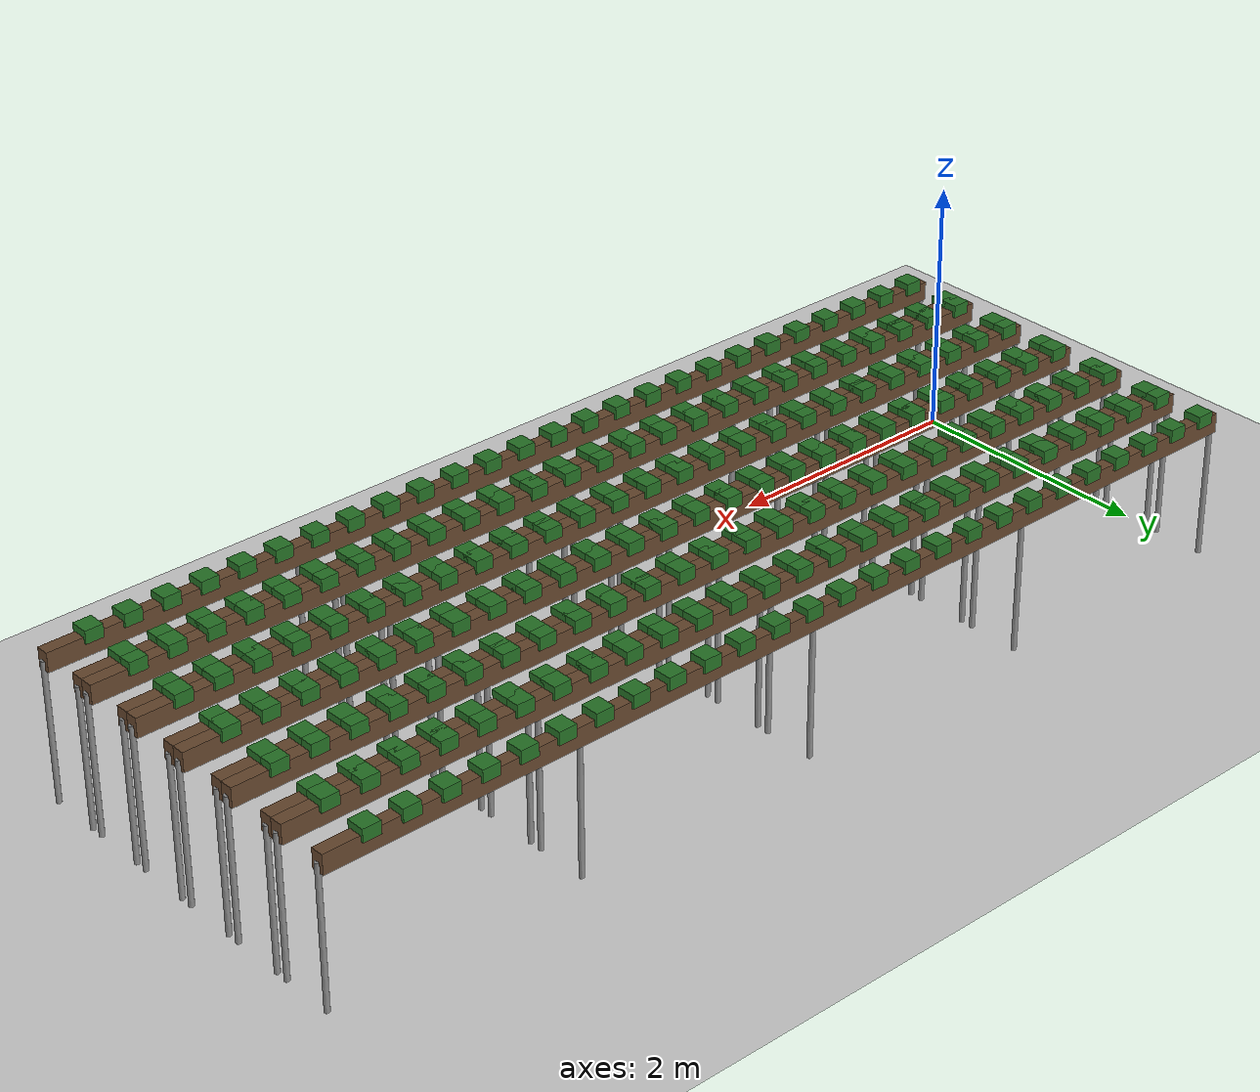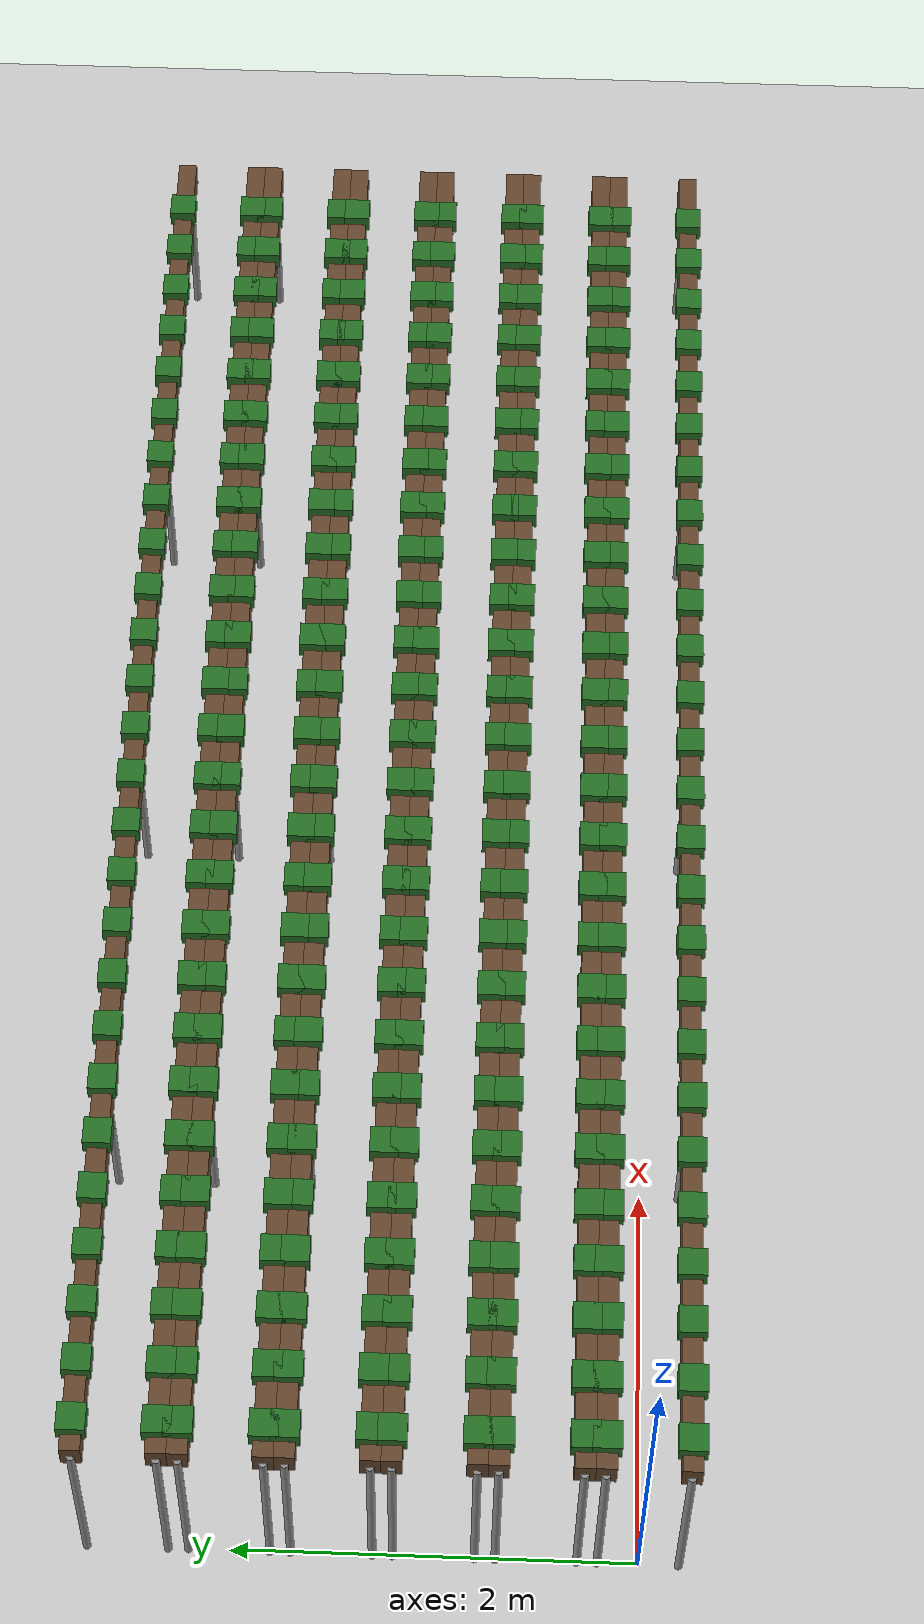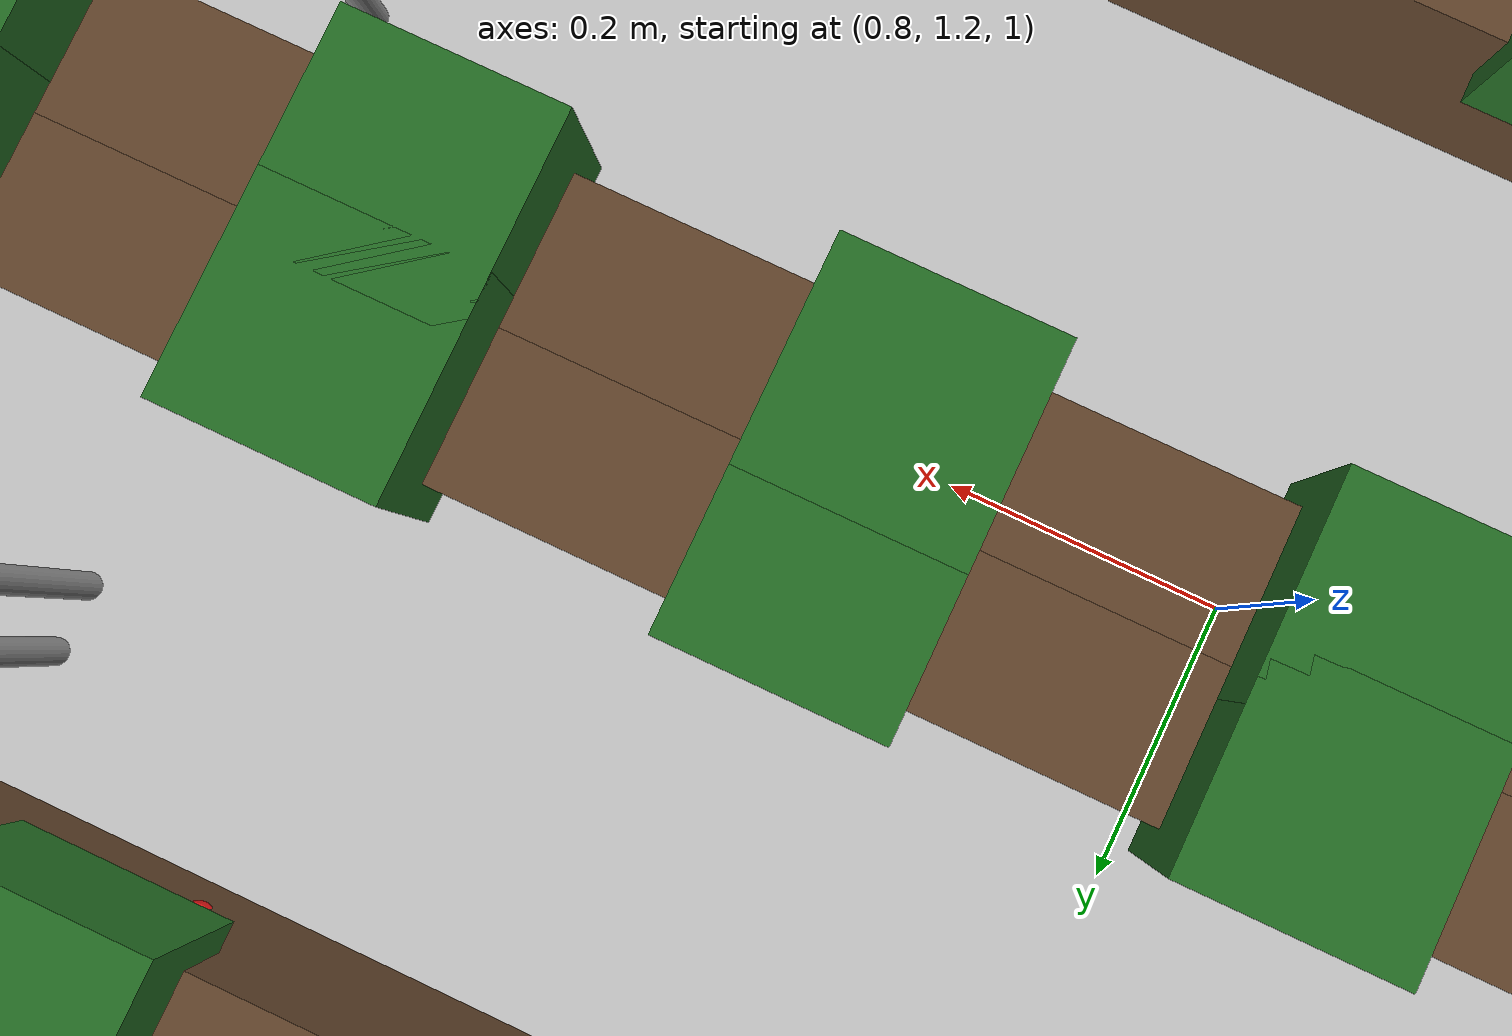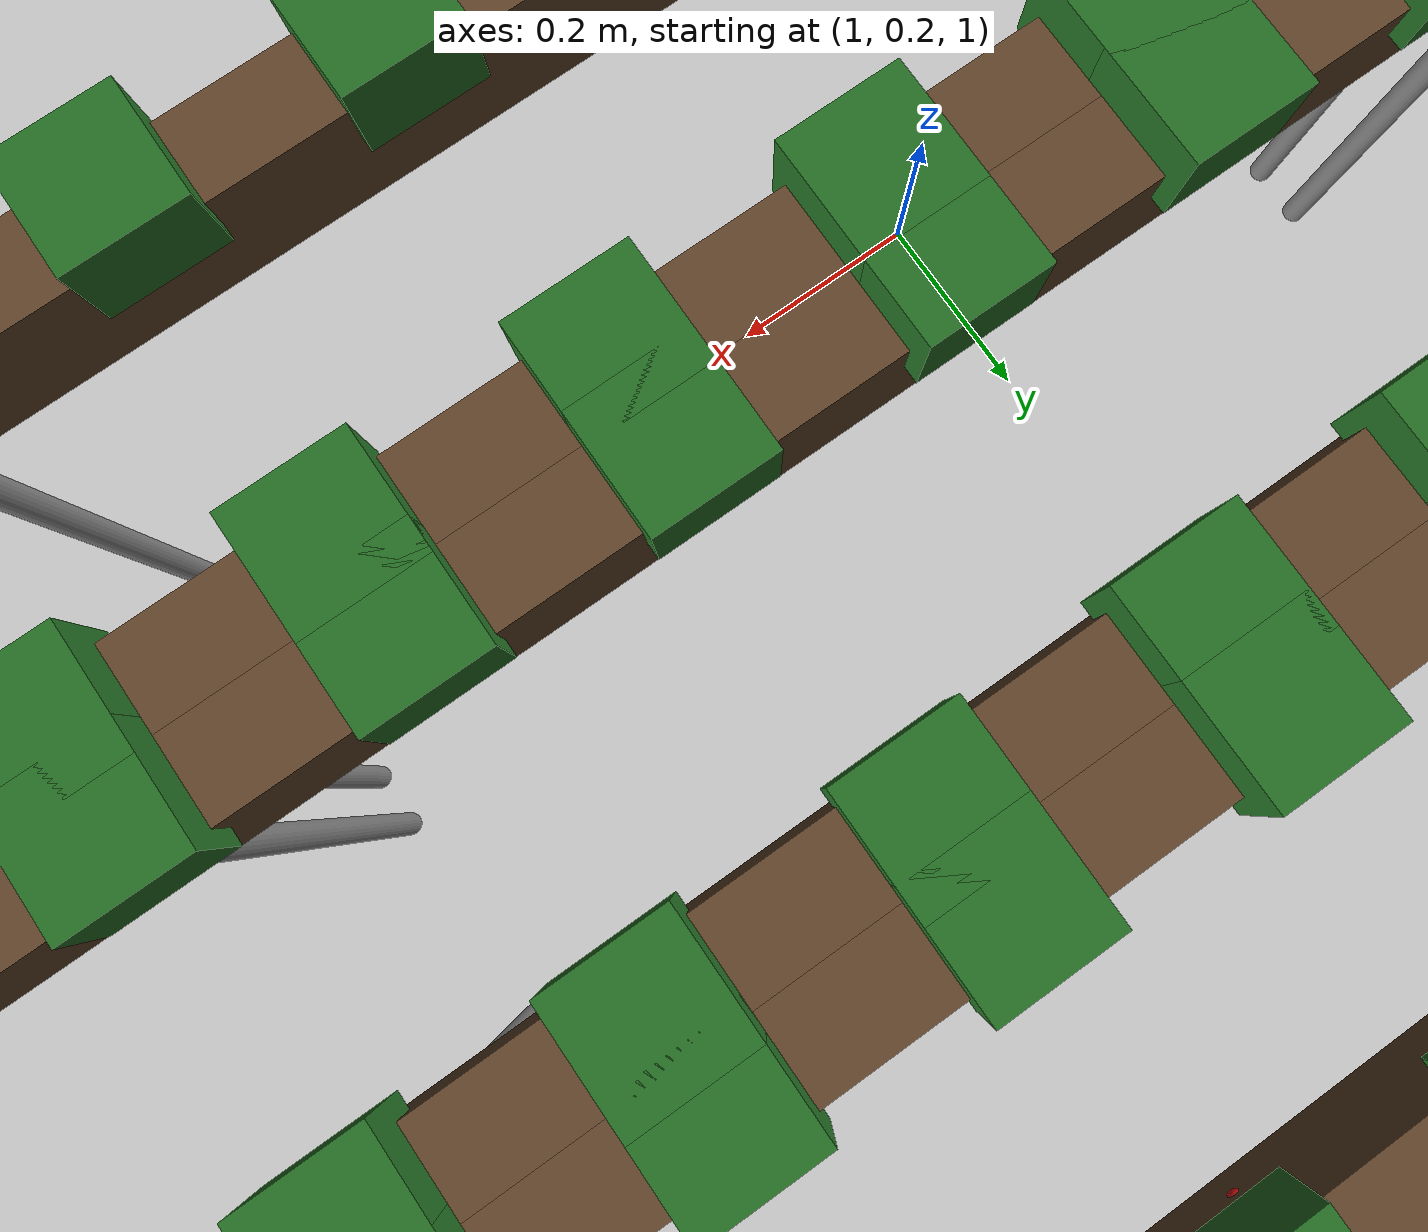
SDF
<?xml version="1.0" ?>
<sdf version="1.7">
  <world name="irish_polytunnel">
    <include><uri>model://sun</uri></include>
    <include><uri>model://ground_plane</uri></include>

    <physics type="ode">
      <max_step_size>0.001</max_step_size>
      <real_time_factor>1.0</real_time_factor>
      <real_time_update_rate>1000</real_time_update_rate>
    </physics>

    <!-- diffuse, indoor-polytunnel-like lighting rather than harsh direct
         sun; a rough approximation only, see the sim URDF's note on
         Gazebo Classic's rendering not being photorealistic -->
    <scene>
      <ambient>0.6 0.6 0.6 1</ambient>
      <background>0.7 0.7 0.7 1</background>
      <shadows>false</shadows>
    </scene>

    <model name="row0_L_post0">
      <static>true</static>
      <pose>0.000 0.200 0.550 0 0 0</pose>
      <link name="link">
        <collision name="collision">
          <geometry><cylinder><radius>0.02</radius><length>1.100</length></cylinder></geometry>
        </collision>
        <visual name="visual">
          <geometry><cylinder><radius>0.02</radius><length>1.100</length></cylinder></geometry>
          <material><ambient>0.5 0.5 0.5 1</ambient><diffuse>0.55 0.55 0.55 1</diffuse></material>
        </visual>
      </link>
    </model>

    <model name="row0_L_post1">
      <static>true</static>
      <pose>2.000 0.200 0.550 0 0 0</pose>
      <link name="link">
        <collision name="collision">
          <geometry><cylinder><radius>0.02</radius><length>1.100</length></cylinder></geometry>
        </collision>
        <visual name="visual">
          <geometry><cylinder><radius>0.02</radius><length>1.100</length></cylinder></geometry>
          <material><ambient>0.5 0.5 0.5 1</ambient><diffuse>0.55 0.55 0.55 1</diffuse></material>
        </visual>
      </link>
    </model>

    <model name="row0_L_post2">
      <static>true</static>
      <pose>4.000 0.200 0.550 0 0 0</pose>
      <link name="link">
        <collision name="collision">
          <geometry><cylinder><radius>0.02</radius><length>1.100</length></cylinder></geometry>
        </collision>
        <visual name="visual">
          <geometry><cylinder><radius>0.02</radius><length>1.100</length></cylinder></geometry>
          <material><ambient>0.5 0.5 0.5 1</ambient><diffuse>0.55 0.55 0.55 1</diffuse></material>
        </visual>
      </link>
    </model>

    <model name="row0_L_post3">
      <static>true</static>
      <pose>6.000 0.200 0.550 0 0 0</pose>
      <link name="link">
        <collision name="collision">
          <geometry><cylinder><radius>0.02</radius><length>1.100</length></cylinder></geometry>
        </collision>
        <visual name="visual">
          <geometry><cylinder><radius>0.02</radius><length>1.100</length></cylinder></geometry>
          <material><ambient>0.5 0.5 0.5 1</ambient><diffuse>0.55 0.55 0.55 1</diffuse></material>
        </visual>
      </link>
    </model>

    <model name="row0_L_post4">
      <static>true</static>
      <pose>8.000 0.200 0.550 0 0 0</pose>
      <link name="link">
        <collision name="collision">
          <geometry><cylinder><radius>0.02</radius><length>1.100</length></cylinder></geometry>
        </collision>
        <visual name="visual">
          <geometry><cylinder><radius>0.02</radius><length>1.100</length></cylinder></geometry>
          <material><ambient>0.5 0.5 0.5 1</ambient><diffuse>0.55 0.55 0.55 1</diffuse></material>
        </visual>
      </link>
    </model>

    <model name="row0_L_trough">
      <static>true</static>
      <pose>4.000 0.200 1.100 0 0 0</pose>
      <link name="link">
        <collision name="collision">
          <geometry><box><size>8.000 0.100 0.15</size></box></geometry>
        </collision>
        <visual name="visual">
          <geometry><box><size>8.000 0.100 0.15</size></box></geometry>
          <material><ambient>0.35 0.25 0.15 1</ambient><diffuse>0.4 0.28 0.18 1</diffuse></material>
        </visual>
      </link>
    </model>

    <model name="row0_L_plant0_foliage">
      <static>true</static>
      <pose>0.150 0.200 1.180 0 0 0</pose>
      <link name="link">
        <visual name="visual">
          <geometry><box><size>0.14 0.14 0.10</size></box></geometry>
          <material><ambient>0.10 0.35 0.10 1</ambient><diffuse>0.15 0.45 0.15 1</diffuse></material>
        </visual>
      </link>
    </model>
    <model name="row0_L_plant0_berry_0">
      <static>true</static>
      <pose>0.120 0.160 1.070 0 0 0</pose>
      <link name="link">
        <visual name="visual">
          <geometry><sphere><radius>0.012</radius></sphere></geometry>
          <material><ambient>0.75 0.05 0.05 1</ambient><diffuse>0.85 0.08 0.08 1</diffuse></material>
        </visual>
      </link>
    </model>
    <model name="row0_L_plant0_berry_1">
      <static>true</static>
      <pose>0.170 0.230 1.050 0 0 0</pose>
      <link name="link">
        <visual name="visual">
          <geometry><sphere><radius>0.012</radius></sphere></geometry>
          <material><ambient>0.75 0.05 0.05 1</ambient><diffuse>0.85 0.08 0.08 1</diffuse></material>
        </visual>
      </link>
    </model>

    <model name="row0_L_plant1_foliage">
      <static>true</static>
      <pose>0.450 0.200 1.180 0 0 0</pose>
      <link name="link">
        <visual name="visual">
          <geometry><box><size>0.14 0.14 0.10</size></box></geometry>
          <material><ambient>0.10 0.35 0.10 1</ambient><diffuse>0.15 0.45 0.15 1</diffuse></material>
        </visual>
      </link>
    </model>
    <model name="row0_L_plant1_berry_0">
      <static>true</static>
      <pose>0.420 0.160 1.070 0 0 0</pose>
      <link name="link">
        <visual name="visual">
          <geometry><sphere><radius>0.012</radius></sphere></geometry>
          <material><ambient>0.75 0.05 0.05 1</ambient><diffuse>0.85 0.08 0.08 1</diffuse></material>
        </visual>
      </link>
    </model>
    <model name="row0_L_plant1_berry_1">
      <static>true</static>
      <pose>0.470 0.230 1.050 0 0 0</pose>
      <link name="link">
        <visual name="visual">
          <geometry><sphere><radius>0.012</radius></sphere></geometry>
          <material><ambient>0.75 0.05 0.05 1</ambient><diffuse>0.85 0.08 0.08 1</diffuse></material>
        </visual>
      </link>
    </model>

    <model name="row0_L_plant2_foliage">
      <static>true</static>
      <pose>0.750 0.200 1.180 0 0 0</pose>
      <link name="link">
        <visual name="visual">
          <geometry><box><size>0.14 0.14 0.10</size></box></geometry>
          <material><ambient>0.10 0.35 0.10 1</ambient><diffuse>0.15 0.45 0.15 1</diffuse></material>
        </visual>
      </link>
    </model>
    <model name="row0_L_plant2_berry_0">
      <static>true</static>
      <pose>0.720 0.160 1.070 0 0 0</pose>
      <link name="link">
        <visual name="visual">
          <geometry><sphere><radius>0.012</radius></sphere></geometry>
          <material><ambient>0.75 0.05 0.05 1</ambient><diffuse>0.85 0.08 0.08 1</diffuse></material>
        </visual>
      </link>
    </model>
    <model name="row0_L_plant2_berry_1">
      <static>true</static>
      <pose>0.770 0.230 1.050 0 0 0</pose>
      <link name="link">
        <visual name="visual">
          <geometry><sphere><radius>0.012</radius></sphere></geometry>
          <material><ambient>0.75 0.05 0.05 1</ambient><diffuse>0.85 0.08 0.08 1</diffuse></material>
        </visual>
      </link>
    </model>

    <model name="row0_L_plant3_foliage">
      <static>true</static>
      <pose>1.050 0.200 1.180 0 0 0</pose>
      <link name="link">
        <visual name="visual">
          <geometry><box><size>0.14 0.14 0.10</size></box></geometry>
          <material><ambient>0.10 0.35 0.10 1</ambient><diffuse>0.15 0.45 0.15 1</diffuse></material>
        </visual>
      </link>
    </model>
    <model name="row0_L_plant3_berry_0">
      <static>true</static>
      <pose>1.020 0.160 1.070 0 0 0</pose>
      <link name="link">
        <visual name="visual">
          <geometry><sphere><radius>0.012</radius></sphere></geometry>
          <material><ambient>0.75 0.05 0.05 1</ambient><diffuse>0.85 0.08 0.08 1</diffuse></material>
        </visual>
      </link>
    </model>
    <model name="row0_L_plant3_berry_1">
      <static>true</static>
      <pose>1.070 0.230 1.050 0 0 0</pose>
      <link name="link">
        <visual name="visual">
          <geometry><sphere><radius>0.012</radius></sphere></geometry>
          <material><ambient>0.75 0.05 0.05 1</ambient><diffuse>0.85 0.08 0.08 1</diffuse></material>
        </visual>
      </link>
    </model>

    <model name="row0_L_plant4_foliage">
      <static>true</static>
      <pose>1.350 0.200 1.180 0 0 0</pose>
      <link name="link">
        <visual name="visual">
          <geometry><box><size>0.14 0.14 0.10</size></box></geometry>
          <material><ambient>0.10 0.35 0.10 1</ambient><diffuse>0.15 0.45 0.15 1</diffuse></material>
        </visual>
      </link>
    </model>
    <model name="row0_L_plant4_berry_0">
      <static>true</static>
      <pose>1.320 0.160 1.070 0 0 0</pose>
      <link name="link">
        <visual name="visual">
          <geometry><sphere><radius>0.012</radius></sphere></geometry>
          <material><ambient>0.75 0.05 0.05 1</ambient><diffuse>0.85 0.08 0.08 1</diffuse></material>
        </visual>
      </link>
    </model>
    <model name="row0_L_plant4_berry_1">
      <static>true</static>
      <pose>1.370 0.230 1.050 0 0 0</pose>
      <link name="link">
        <visual name="visual">
          <geometry><sphere><radius>0.012</radius></sphere></geometry>
          <material><ambient>0.75 0.05 0.05 1</ambient><diffuse>0.85 0.08 0.08 1</diffuse></material>
        </visual>
      </link>
    </model>

    <model name="row0_L_plant5_foliage">
      <static>true</static>
      <pose>1.650 0.200 1.180 0 0 0</pose>
      <link name="link">
        <visual name="visual">
          <geometry><box><size>0.14 0.14 0.10</size></box></geometry>
          <material><ambient>0.10 0.35 0.10 1</ambient><diffuse>0.15 0.45 0.15 1</diffuse></material>
        </visual>
      </link>
    </model>
    <model name="row0_L_plant5_berry_0">
      <static>true</static>
      <pose>1.620 0.160 1.070 0 0 0</pose>
      <link name="link">
        <visual name="visual">
          <geometry><sphere><radius>0.012</radius></sphere></geometry>
          <material><ambient>0.75 0.05 0.05 1</ambient><diffuse>0.85 0.08 0.08 1</diffuse></material>
        </visual>
      </link>
    </model>
    <model name="row0_L_plant5_berry_1">
      <static>true</static>
      <pose>1.670 0.230 1.050 0 0 0</pose>
      <link name="link">
        <visual name="visual">
          <geometry><sphere><radius>0.012</radius></sphere></geometry>
          <material><ambient>0.75 0.05 0.05 1</ambient><diffuse>0.85 0.08 0.08 1</diffuse></material>
        </visual>
      </link>
    </model>

    <model name="row0_L_plant6_foliage">
      <static>true</static>
      <pose>1.950 0.200 1.180 0 0 0</pose>
      <link name="link">
        <visual name="visual">
          <geometry><box><size>0.14 0.14 0.10</size></box></geometry>
          <material><ambient>0.10 0.35 0.10 1</ambient><diffuse>0.15 0.45 0.15 1</diffuse></material>
        </visual>
      </link>
    </model>
    <model name="row0_L_plant6_berry_0">
      <static>true</static>
      <pose>1.920 0.160 1.070 0 0 0</pose>
      <link name="link">
        <visual name="visual">
          <geometry><sphere><radius>0.012</radius></sphere></geometry>
          <material><ambient>0.75 0.05 0.05 1</ambient><diffuse>0.85 0.08 0.08 1</diffuse></material>
        </visual>
      </link>
    </model>
    <model name="row0_L_plant6_berry_1">
      <static>true</static>
      <pose>1.970 0.230 1.050 0 0 0</pose>
      <link name="link">
        <visual name="visual">
          <geometry><sphere><radius>0.012</radius></sphere></geometry>
          <material><ambient>0.75 0.05 0.05 1</ambient><diffuse>0.85 0.08 0.08 1</diffuse></material>
        </visual>
      </link>
    </model>

    <model name="row0_L_plant7_foliage">
      <static>true</static>
      <pose>2.250 0.200 1.180 0 0 0</pose>
      <link name="link">
        <visual name="visual">
          <geometry><box><size>0.14 0.14 0.10</size></box></geometry>
          <material><ambient>0.10 0.35 0.10 1</ambient><diffuse>0.15 0.45 0.15 1</diffuse></material>
        </visual>
      </link>
    </model>
    <model name="row0_L_plant7_berry_0">
      <static>true</static>
      <pose>2.220 0.160 1.070 0 0 0</pose>
      <link name="link">
        <visual name="visual">
          <geometry><sphere><radius>0.012</radius></sphere></geometry>
          <material><ambient>0.75 0.05 0.05 1</ambient><diffuse>0.85 0.08 0.08 1</diffuse></material>
        </visual>
      </link>
    </model>
    <model name="row0_L_plant7_berry_1">
      <static>true</static>
      <pose>2.270 0.230 1.050 0 0 0</pose>
      <link name="link">
        <visual name="visual">
          <geometry><sphere><radius>0.012</radius></sphere></geometry>
          <material><ambient>0.75 0.05 0.05 1</ambient><diffuse>0.85 0.08 0.08 1</diffuse></material>
        </visual>
      </link>
    </model>

    <model name="row0_L_plant8_foliage">
      <static>true</static>
      <pose>2.550 0.200 1.180 0 0 0</pose>
      <link name="link">
        <visual name="visual">
          <geometry><box><size>0.14 0.14 0.10</size></box></geometry>
          <material><ambient>0.10 0.35 0.10 1</ambient><diffuse>0.15 0.45 0.15 1</diffuse></material>
        </visual>
      </link>
    </model>
    <model name="row0_L_plant8_berry_0">
      <static>true</static>
      <pose>2.520 0.160 1.070 0 0 0</pose>
      <link name="link">
        <visual name="visual">
          <geometry><sphere><radius>0.012</radius></sphere></geometry>
          <material><ambient>0.75 0.05 0.05 1</ambient><diffuse>0.85 0.08 0.08 1</diffuse></material>
        </visual>
      </link>
    </model>
    <model name="row0_L_plant8_berry_1">
      <static>true</static>
      <pose>2.570 0.230 1.050 0 0 0</pose>
      <link name="link">
        <visual name="visual">
          <geometry><sphere><radius>0.012</radius></sphere></geometry>
          <material><ambient>0.75 0.05 0.05 1</ambient><diffuse>0.85 0.08 0.08 1</diffuse></material>
        </visual>
      </link>
    </model>

    <model name="row0_L_plant9_foliage">
      <static>true</static>
      <pose>2.850 0.200 1.180 0 0 0</pose>
      <link name="link">
        <visual name="visual">
          <geometry><box><size>0.14 0.14 0.10</size></box></geometry>
          <material><ambient>0.10 0.35 0.10 1</ambient><diffuse>0.15 0.45 0.15 1</diffuse></material>
        </visual>
      </link>
    </model>
    <model name="row0_L_plant9_berry_0">
      <static>true</static>
      <pose>2.820 0.160 1.070 0 0 0</pose>
      <link name="link">
        <visual name="visual">
          <geometry><sphere><radius>0.012</radius></sphere></geometry>
          <material><ambient>0.75 0.05 0.05 1</ambient><diffuse>0.85 0.08 0.08 1</diffuse></material>
        </visual>
      </link>
    </model>
    <model name="row0_L_plant9_berry_1">
      <static>true</static>
      <pose>2.870 0.230 1.050 0 0 0</pose>
      <link name="link">
        <visual name="visual">
          <geometry><sphere><radius>0.012</radius></sphere></geometry>
          <material><ambient>0.75 0.05 0.05 1</ambient><diffuse>0.85 0.08 0.08 1</diffuse></material>
        </visual>
      </link>
    </model>

    <model name="row0_L_plant10_foliage">
      <static>true</static>
      <pose>3.150 0.200 1.180 0 0 0</pose>
      <link name="link">
        <visual name="visual">
          <geometry><box><size>0.14 0.14 0.10</size></box></geometry>
          <material><ambient>0.10 0.35 0.10 1</ambient><diffuse>0.15 0.45 0.15 1</diffuse></material>
        </visual>
      </link>
    </model>
    <model name="row0_L_plant10_berry_0">
      <static>true</static>
      <pose>3.120 0.160 1.070 0 0 0</pose>
      <link name="link">
        <visual name="visual">
          <geometry><sphere><radius>0.012</radius></sphere></geometry>
          <material><ambient>0.75 0.05 0.05 1</ambient><diffuse>0.85 0.08 0.08 1</diffuse></material>
        </visual>
      </link>
    </model>
    <model name="row0_L_plant10_berry_1">
      <static>true</static>
      <pose>3.170 0.230 1.050 0 0 0</pose>
      <link name="link">
        <visual name="visual">
          <geometry><sphere><radius>0.012</radius></sphere></geometry>
          <material><ambient>0.75 0.05 0.05 1</ambient><diffuse>0.85 0.08 0.08 1</diffuse></material>
        </visual>
      </link>
    </model>

    <model name="row0_L_plant11_foliage">
      <static>true</static>
      <pose>3.450 0.200 1.180 0 0 0</pose>
      <link name="link">
        <visual name="visual">
          <geometry><box><size>0.14 0.14 0.10</size></box></geometry>
          <material><ambient>0.10 0.35 0.10 1</ambient><diffuse>0.15 0.45 0.15 1</diffuse></material>
        </visual>
      </link>
    </model>
    <model name="row0_L_plant11_berry_0">
      <static>true</static>
      <pose>3.420 0.160 1.070 0 0 0</pose>
      <link name="link">
        <visual name="visual">
          <geometry><sphere><radius>0.012</radius></sphere></geometry>
          <material><ambient>0.75 0.05 0.05 1</ambient><diffuse>0.85 0.08 0.08 1</diffuse></material>
        </visual>
      </link>
    </model>
    <model name="row0_L_plant11_berry_1">
      <static>true</static>
      <pose>3.470 0.230 1.050 0 0 0</pose>
      <link name="link">
        <visual name="visual">
          <geometry><sphere><radius>0.012</radius></sphere></geometry>
          <material><ambient>0.75 0.05 0.05 1</ambient><diffuse>0.85 0.08 0.08 1</diffuse></material>
        </visual>
      </link>
    </model>

    <model name="row0_L_plant12_foliage">
      <static>true</static>
      <pose>3.750 0.200 1.180 0 0 0</pose>
      <link name="link">
        <visual name="visual">
          <geometry><box><size>0.14 0.14 0.10</size></box></geometry>
          <material><ambient>0.10 0.35 0.10 1</ambient><diffuse>0.15 0.45 0.15 1</diffuse></material>
        </visual>
      </link>
    </model>
    <model name="row0_L_plant12_berry_0">
      <static>true</static>
      <pose>3.720 0.160 1.070 0 0 0</pose>
      <link name="link">
        <visual name="visual">
          <geometry><sphere><radius>0.012</radius></sphere></geometry>
          <material><ambient>0.75 0.05 0.05 1</ambient><diffuse>0.85 0.08 0.08 1</diffuse></material>
        </visual>
      </link>
    </model>
    <model name="row0_L_plant12_berry_1">
      <static>true</static>
      <pose>3.770 0.230 1.050 0 0 0</pose>
      <link name="link">
        <visual name="visual">
          <geometry><sphere><radius>0.012</radius></sphere></geometry>
          <material><ambient>0.75 0.05 0.05 1</ambient><diffuse>0.85 0.08 0.08 1</diffuse></material>
        </visual>
      </link>
    </model>

    <model name="row0_L_plant13_foliage">
      <static>true</static>
      <pose>4.050 0.200 1.180 0 0 0</pose>
      <link name="link">
        <visual name="visual">
          <geometry><box><size>0.14 0.14 0.10</size></box></geometry>
          <material><ambient>0.10 0.35 0.10 1</ambient><diffuse>0.15 0.45 0.15 1</diffuse></material>
        </visual>
      </link>
    </model>
    <model name="row0_L_plant13_berry_0">
      <static>true</static>
      <pose>4.020 0.160 1.070 0 0 0</pose>
      <link name="link">
        <visual name="visual">
          <geometry><sphere><radius>0.012</radius></sphere></geometry>
          <material><ambient>0.75 0.05 0.05 1</ambient><diffuse>0.85 0.08 0.08 1</diffuse></material>
        </visual>
      </link>
    </model>
    <model name="row0_L_plant13_berry_1">
      <static>true</static>
      <pose>4.070 0.230 1.050 0 0 0</pose>
      <link name="link">
        <visual name="visual">
          <geometry><sphere><radius>0.012</radius></sphere></geometry>
          <material><ambient>0.75 0.05 0.05 1</ambient><diffuse>0.85 0.08 0.08 1</diffuse></material>
        </visual>
      </link>
    </model>

    <model name="row0_L_plant14_foliage">
      <static>true</static>
      <pose>4.350 0.200 1.180 0 0 0</pose>
      <link name="link">
        <visual name="visual">
          <geometry><box><size>0.14 0.14 0.10</size></box></geometry>
          <material><ambient>0.10 0.35 0.10 1</ambient><diffuse>0.15 0.45 0.15 1</diffuse></material>
        </visual>
      </link>
    </model>
    <model name="row0_L_plant14_berry_0">
      <static>true</static>
      <pose>4.320 0.160 1.070 0 0 0</pose>
      <link name="link">
        <visual name="visual">
          <geometry><sphere><radius>0.012</radius></sphere></geometry>
          <material><ambient>0.75 0.05 0.05 1</ambient><diffuse>0.85 0.08 0.08 1</diffuse></material>
        </visual>
      </link>
    </model>
    <model name="row0_L_plant14_berry_1">
      <static>true</static>
      <pose>4.370 0.230 1.050 0 0 0</pose>
      <link name="link">
        <visual name="visual">
          <geometry><sphere><radius>0.012</radius></sphere></geometry>
          <material><ambient>0.75 0.05 0.05 1</ambient><diffuse>0.85 0.08 0.08 1</diffuse></material>
        </visual>
      </link>
    </model>

    <model name="row0_L_plant15_foliage">
      <static>true</static>
      <pose>4.650 0.200 1.180 0 0 0</pose>
      <link name="link">
        <visual name="visual">
          <geometry><box><size>0.14 0.14 0.10</size></box></geometry>
          <material><ambient>0.10 0.35 0.10 1</ambient><diffuse>0.15 0.45 0.15 1</diffuse></material>
        </visual>
      </link>
    </model>
    <model name="row0_L_plant15_berry_0">
      <static>true</static>
      <pose>4.620 0.160 1.070 0 0 0</pose>
      <link name="link">
        <visual name="visual">
          <geometry><sphere><radius>0.012</radius></sphere></geometry>
          <material><ambient>0.75 0.05 0.05 1</ambient><diffuse>0.85 0.08 0.08 1</diffuse></material>
        </visual>
      </link>
    </model>
    <model name="row0_L_plant15_berry_1">
      <static>true</static>
      <pose>4.670 0.230 1.050 0 0 0</pose>
      <link name="link">
        <visual name="visual">
          <geometry><sphere><radius>0.012</radius></sphere></geometry>
          <material><ambient>0.75 0.05 0.05 1</ambient><diffuse>0.85 0.08 0.08 1</diffuse></material>
        </visual>
      </link>
    </model>

    <model name="row0_L_plant16_foliage">
      <static>true</static>
      <pose>4.950 0.200 1.180 0 0 0</pose>
      <link name="link">
        <visual name="visual">
          <geometry><box><size>0.14 0.14 0.10</size></box></geometry>
          <material><ambient>0.10 0.35 0.10 1</ambient><diffuse>0.15 0.45 0.15 1</diffuse></material>
        </visual>
      </link>
    </model>
    <model name="row0_L_plant16_berry_0">
      <static>true</static>
      <pose>4.920 0.160 1.070 0 0 0</pose>
      <link name="link">
        <visual name="visual">
          <geometry><sphere><radius>0.012</radius></sphere></geometry>
          <material><ambient>0.75 0.05 0.05 1</ambient><diffuse>0.85 0.08 0.08 1</diffuse></material>
        </visual>
      </link>
    </model>
    <model name="row0_L_plant16_berry_1">
      <static>true</static>
      <pose>4.970 0.230 1.050 0 0 0</pose>
      <link name="link">
        <visual name="visual">
          <geometry><sphere><radius>0.012</radius></sphere></geometry>
          <material><ambient>0.75 0.05 0.05 1</ambient><diffuse>0.85 0.08 0.08 1</diffuse></material>
        </visual>
      </link>
    </model>

    <model name="row0_L_plant17_foliage">
      <static>true</static>
      <pose>5.250 0.200 1.180 0 0 0</pose>
      <link name="link">
        <visual name="visual">
          <geometry><box><size>0.14 0.14 0.10</size></box></geometry>
          <material><ambient>0.10 0.35 0.10 1</ambient><diffuse>0.15 0.45 0.15 1</diffuse></material>
        </visual>
      </link>
    </model>
    <model name="row0_L_plant17_berry_0">
      <static>true</static>
      <pose>5.220 0.160 1.070 0 0 0</pose>
      <link name="link">
        <visual name="visual">
          <geometry><sphere><radius>0.012</radius></sphere></geometry>
          <material><ambient>0.75 0.05 0.05 1</ambient><diffuse>0.85 0.08 0.08 1</diffuse></material>
        </visual>
      </link>
    </model>
    <model name="row0_L_plant17_berry_1">
      <static>true</static>
      <pose>5.270 0.230 1.050 0 0 0</pose>
      <link name="link">
        <visual name="visual">
          <geometry><sphere><radius>0.012</radius></sphere></geometry>
          <material><ambient>0.75 0.05 0.05 1</ambient><diffuse>0.85 0.08 0.08 1</diffuse></material>
        </visual>
      </link>
    </model>

    <model name="row0_L_plant18_foliage">
      <static>true</static>
      <pose>5.550 0.200 1.180 0 0 0</pose>
      <link name="link">
        <visual name="visual">
          <geometry><box><size>0.14 0.14 0.10</size></box></geometry>
          <material><ambient>0.10 0.35 0.10 1</ambient><diffuse>0.15 0.45 0.15 1</diffuse></material>
        </visual>
      </link>
    </model>
    <model name="row0_L_plant18_berry_0">
      <static>true</static>
      <pose>5.520 0.160 1.070 0 0 0</pose>
      <link name="link">
        <visual name="visual">
          <geometry><sphere><radius>0.012</radius></sphere></geometry>
          <material><ambient>0.75 0.05 0.05 1</ambient><diffuse>0.85 0.08 0.08 1</diffuse></material>
        </visual>
      </link>
    </model>
    <model name="row0_L_plant18_berry_1">
      <static>true</static>
      <pose>5.570 0.230 1.050 0 0 0</pose>
      <link name="link">
        <visual name="visual">
          <geometry><sphere><radius>0.012</radius></sphere></geometry>
          <material><ambient>0.75 0.05 0.05 1</ambient><diffuse>0.85 0.08 0.08 1</diffuse></material>
        </visual>
      </link>
    </model>

    <model name="row0_L_plant19_foliage">
      <static>true</static>
      <pose>5.850 0.200 1.180 0 0 0</pose>
      <link name="link">
        <visual name="visual">
          <geometry><box><size>0.14 0.14 0.10</size></box></geometry>
          <material><ambient>0.10 0.35 0.10 1</ambient><diffuse>0.15 0.45 0.15 1</diffuse></material>
        </visual>
      </link>
    </model>
    <model name="row0_L_plant19_berry_0">
      <static>true</static>
      <pose>5.820 0.160 1.070 0 0 0</pose>
      <link name="link">
        <visual name="visual">
          <geometry><sphere><radius>0.012</radius></sphere></geometry>
          <material><ambient>0.75 0.05 0.05 1</ambient><diffuse>0.85 0.08 0.08 1</diffuse></material>
        </visual>
      </link>
    </model>
    <model name="row0_L_plant19_berry_1">
      <static>true</static>
      <pose>5.870 0.230 1.050 0 0 0</pose>
      <link name="link">
        <visual name="visual">
          <geometry><sphere><radius>0.012</radius></sphere></geometry>
          <material><ambient>0.75 0.05 0.05 1</ambient><diffuse>0.85 0.08 0.08 1</diffuse></material>
        </visual>
      </link>
    </model>

    <model name="row0_L_plant20_foliage">
      <static>true</static>
      <pose>6.150 0.200 1.180 0 0 0</pose>
      <link name="link">
        <visual name="visual">
          <geometry><box><size>0.14 0.14 0.10</size></box></geometry>
          <material><ambient>0.10 0.35 0.10 1</ambient><diffuse>0.15 0.45 0.15 1</diffuse></material>
        </visual>
      </link>
    </model>
    <model name="row0_L_plant20_berry_0">
      <static>true</static>
      <pose>6.120 0.160 1.070 0 0 0</pose>
      <link name="link">
        <visual name="visual">
          <geometry><sphere><radius>0.012</radius></sphere></geometry>
          <material><ambient>0.75 0.05 0.05 1</ambient><diffuse>0.85 0.08 0.08 1</diffuse></material>
        </visual>
      </link>
    </model>
    <model name="row0_L_plant20_berry_1">
      <static>true</static>
      <pose>6.170 0.230 1.050 0 0 0</pose>
      <link name="link">
        <visual name="visual">
          <geometry><sphere><radius>0.012</radius></sphere></geometry>
          <material><ambient>0.75 0.05 0.05 1</ambient><diffuse>0.85 0.08 0.08 1</diffuse></material>
        </visual>
      </link>
    </model>

    <model name="row0_L_plant21_foliage">
      <static>true</static>
      <pose>6.450 0.200 1.180 0 0 0</pose>
      <link name="link">
        <visual name="visual">
          <geometry><box><size>0.14 0.14 0.10</size></box></geometry>
          <material><ambient>0.10 0.35 0.10 1</ambient><diffuse>0.15 0.45 0.15 1</diffuse></material>
        </visual>
      </link>
    </model>
    <model name="row0_L_plant21_berry_0">
      <static>true</static>
      <pose>6.420 0.160 1.070 0 0 0</pose>
      <link name="link">
        <visual name="visual">
          <geometry><sphere><radius>0.012</radius></sphere></geometry>
          <material><ambient>0.75 0.05 0.05 1</ambient><diffuse>0.85 0.08 0.08 1</diffuse></material>
        </visual>
      </link>
    </model>
    <model name="row0_L_plant21_berry_1">
      <static>true</static>
      <pose>6.470 0.230 1.050 0 0 0</pose>
      <link name="link">
        <visual name="visual">
          <geometry><sphere><radius>0.012</radius></sphere></geometry>
          <material><ambient>0.75 0.05 0.05 1</ambient><diffuse>0.85 0.08 0.08 1</diffuse></material>
        </visual>
      </link>
    </model>

    <model name="row0_L_plant22_foliage">
      <static>true</static>
      <pose>6.750 0.200 1.180 0 0 0</pose>
      <link name="link">
        <visual name="visual">
          <geometry><box><size>0.14 0.14 0.10</size></box></geometry>
          <material><ambient>0.10 0.35 0.10 1</ambient><diffuse>0.15 0.45 0.15 1</diffuse></material>
        </visual>
      </link>
    </model>
    <model name="row0_L_plant22_berry_0">
      <static>true</static>
      <pose>6.720 0.160 1.070 0 0 0</pose>
      <link name="link">
        <visual name="visual">
          <geometry><sphere><radius>0.012</radius></sphere></geometry>
          <material><ambient>0.75 0.05 0.05 1</ambient><diffuse>0.85 0.08 0.08 1</diffuse></material>
        </visual>
      </link>
    </model>
    <model name="row0_L_plant22_berry_1">
      <static>true</static>
      <pose>6.770 0.230 1.050 0 0 0</pose>
      <link name="link">
        <visual name="visual">
          <geometry><sphere><radius>0.012</radius></sphere></geometry>
          <material><ambient>0.75 0.05 0.05 1</ambient><diffuse>0.85 0.08 0.08 1</diffuse></material>
        </visual>
      </link>
    </model>

    <model name="row0_L_plant23_foliage">
      <static>true</static>
      <pose>7.050 0.200 1.180 0 0 0</pose>
      <link name="link">
        <visual name="visual">
          <geometry><box><size>0.14 0.14 0.10</size></box></geometry>
          <material><ambient>0.10 0.35 0.10 1</ambient><diffuse>0.15 0.45 0.15 1</diffuse></material>
        </visual>
      </link>
    </model>
    <model name="row0_L_plant23_berry_0">
      <static>true</static>
      <pose>7.020 0.160 1.070 0 0 0</pose>
      <link name="link">
        <visual name="visual">
          <geometry><sphere><radius>0.012</radius></sphere></geometry>
          <material><ambient>0.75 0.05 0.05 1</ambient><diffuse>0.85 0.08 0.08 1</diffuse></material>
        </visual>
      </link>
    </model>
    <model name="row0_L_plant23_berry_1">
      <static>true</static>
      <pose>7.070 0.230 1.050 0 0 0</pose>
      <link name="link">
        <visual name="visual">
          <geometry><sphere><radius>0.012</radius></sphere></geometry>
          <material><ambient>0.75 0.05 0.05 1</ambient><diffuse>0.85 0.08 0.08 1</diffuse></material>
        </visual>
      </link>
    </model>

    <model name="row0_L_plant24_foliage">
      <static>true</static>
      <pose>7.350 0.200 1.180 0 0 0</pose>
      <link name="link">
        <visual name="visual">
          <geometry><box><size>0.14 0.14 0.10</size></box></geometry>
          <material><ambient>0.10 0.35 0.10 1</ambient><diffuse>0.15 0.45 0.15 1</diffuse></material>
        </visual>
      </link>
    </model>
    <model name="row0_L_plant24_berry_0">
      <static>true</static>
      <pose>7.320 0.160 1.070 0 0 0</pose>
      <link name="link">
        <visual name="visual">
          <geometry><sphere><radius>0.012</radius></sphere></geometry>
          <material><ambient>0.75 0.05 0.05 1</ambient><diffuse>0.85 0.08 0.08 1</diffuse></material>
        </visual>
      </link>
    </model>
    <model name="row0_L_plant24_berry_1">
      <static>true</static>
      <pose>7.370 0.230 1.050 0 0 0</pose>
      <link name="link">
        <visual name="visual">
          <geometry><sphere><radius>0.012</radius></sphere></geometry>
          <material><ambient>0.75 0.05 0.05 1</ambient><diffuse>0.85 0.08 0.08 1</diffuse></material>
        </visual>
      </link>
    </model>

    <model name="row0_L_plant25_foliage">
      <static>true</static>
      <pose>7.650 0.200 1.180 0 0 0</pose>
      <link name="link">
        <visual name="visual">
          <geometry><box><size>0.14 0.14 0.10</size></box></geometry>
          <material><ambient>0.10 0.35 0.10 1</ambient><diffuse>0.15 0.45 0.15 1</diffuse></material>
        </visual>
      </link>
    </model>
    <model name="row0_L_plant25_berry_0">
      <static>true</static>
      <pose>7.620 0.160 1.070 0 0 0</pose>
      <link name="link">
        <visual name="visual">
          <geometry><sphere><radius>0.012</radius></sphere></geometry>
          <material><ambient>0.75 0.05 0.05 1</ambient><diffuse>0.85 0.08 0.08 1</diffuse></material>
        </visual>
      </link>
    </model>
    <model name="row0_L_plant25_berry_1">
      <static>true</static>
      <pose>7.670 0.230 1.050 0 0 0</pose>
      <link name="link">
        <visual name="visual">
          <geometry><sphere><radius>0.012</radius></sphere></geometry>
          <material><ambient>0.75 0.05 0.05 1</ambient><diffuse>0.85 0.08 0.08 1</diffuse></material>
        </visual>
      </link>
    </model>

    <model name="row0_R_post0">
      <static>true</static>
      <pose>0.000 -0.200 0.550 0 0 0</pose>
      <link name="link">
        <collision name="collision">
          <geometry><cylinder><radius>0.02</radius><length>1.100</length></cylinder></geometry>
        </collision>
        <visual name="visual">
          <geometry><cylinder><radius>0.02</radius><length>1.100</length></cylinder></geometry>
          <material><ambient>0.5 0.5 0.5 1</ambient><diffuse>0.55 0.55 0.55 1</diffuse></material>
        </visual>
      </link>
    </model>

    <model name="row0_R_post1">
      <static>true</static>
      <pose>2.000 -0.200 0.550 0 0 0</pose>
      <link name="link">
        <collision name="collision">
          <geometry><cylinder><radius>0.02</radius><length>1.100</length></cylinder></geometry>
        </collision>
        <visual name="visual">
          <geometry><cylinder><radius>0.02</radius><length>1.100</length></cylinder></geometry>
          <material><ambient>0.5 0.5 0.5 1</ambient><diffuse>0.55 0.55 0.55 1</diffuse></material>
        </visual>
      </link>
    </model>

    <model name="row0_R_post2">
      <static>true</static>
      <pose>4.000 -0.200 0.550 0 0 0</pose>
      <link name="link">
        <collision name="collision">
          <geometry><cylinder><radius>0.02</radius><length>1.100</length></cylinder></geometry>
        </collision>
        <visual name="visual">
          <geometry><cylinder><radius>0.02</radius><length>1.100</length></cylinder></geometry>
          <material><ambient>0.5 0.5 0.5 1</ambient><diffuse>0.55 0.55 0.55 1</diffuse></material>
        </visual>
      </link>
    </model>

    <model name="row0_R_post3">
      <static>true</static>
      <pose>6.000 -0.200 0.550 0 0 0</pose>
      <link name="link">
        <collision name="collision">
          <geometry><cylinder><radius>0.02</radius><length>1.100</length></cylinder></geometry>
        </collision>
        <visual name="visual">
          <geometry><cylinder><radius>0.02</radius><length>1.100</length></cylinder></geometry>
          <material><ambient>0.5 0.5 0.5 1</ambient><diffuse>0.55 0.55 0.55 1</diffuse></material>
        </visual>
      </link>
    </model>

    <model name="row0_R_post4">
      <static>true</static>
      <pose>8.000 -0.200 0.550 0 0 0</pose>
      <link name="link">
        <collision name="collision">
          <geometry><cylinder><radius>0.02</radius><length>1.100</length></cylinder></geometry>
        </collision>
        <visual name="visual">
          <geometry><cylinder><radius>0.02</radius><length>1.100</length></cylinder></geometry>
          <material><ambient>0.5 0.5 0.5 1</ambient><diffuse>0.55 0.55 0.55 1</diffuse></material>
        </visual>
      </link>
    </model>

    <model name="row0_R_trough">
      <static>true</static>
      <pose>4.000 -0.200 1.100 0 0 0</pose>
      <link name="link">
        <collision name="collision">
          <geometry><box><size>8.000 0.100 0.15</size></box></geometry>
        </collision>
        <visual name="visual">
          <geometry><box><size>8.000 0.100 0.15</size></box></geometry>
          <material><ambient>0.35 0.25 0.15 1</ambient><diffuse>0.4 0.28 0.18 1</diffuse></material>
        </visual>
      </link>
    </model>

    <model name="row0_R_plant0_foliage">
      <static>true</static>
      <pose>0.150 -0.200 1.180 0 0 0</pose>
      <link name="link">
        <visual name="visual">
          <geometry><box><size>0.14 0.14 0.10</size></box></geometry>
          <material><ambient>0.10 0.35 0.10 1</ambient><diffuse>0.15 0.45 0.15 1</diffuse></material>
        </visual>
      </link>
    </model>
    <model name="row0_R_plant0_berry_0">
      <static>true</static>
      <pose>0.120 -0.240 1.070 0 0 0</pose>
      <link name="link">
        <visual name="visual">
          <geometry><sphere><radius>0.012</radius></sphere></geometry>
          <material><ambient>0.75 0.05 0.05 1</ambient><diffuse>0.85 0.08 0.08 1</diffuse></material>
        </visual>
      </link>
    </model>
    <model name="row0_R_plant0_berry_1">
      <static>true</static>
      <pose>0.170 -0.170 1.050 0 0 0</pose>
      <link name="link">
        <visual name="visual">
          <geometry><sphere><radius>0.012</radius></sphere></geometry>
          <material><ambient>0.75 0.05 0.05 1</ambient><diffuse>0.85 0.08 0.08 1</diffuse></material>
        </visual>
      </link>
    </model>

    <model name="row0_R_plant1_foliage">
      <static>true</static>
      <pose>0.450 -0.200 1.180 0 0 0</pose>
      <link name="link">
        <visual name="visual">
          <geometry><box><size>0.14 0.14 0.10</size></box></geometry>
          <material><ambient>0.10 0.35 0.10 1</ambient><diffuse>0.15 0.45 0.15 1</diffuse></material>
        </visual>
      </link>
    </model>
    <model name="row0_R_plant1_berry_0">
      <static>true</static>
      <pose>0.420 -0.240 1.070 0 0 0</pose>
      <link name="link">
        <visual name="visual">
          <geometry><sphere><radius>0.012</radius></sphere></geometry>
          <material><ambient>0.75 0.05 0.05 1</ambient><diffuse>0.85 0.08 0.08 1</diffuse></material>
        </visual>
      </link>
    </model>
    <model name="row0_R_plant1_berry_1">
      <static>true</static>
      <pose>0.470 -0.170 1.050 0 0 0</pose>
      <link name="link">
        <visual name="visual">
          <geometry><sphere><radius>0.012</radius></sphere></geometry>
          <material><ambient>0.75 0.05 0.05 1</ambient><diffuse>0.85 0.08 0.08 1</diffuse></material>
        </visual>
      </link>
    </model>

    <model name="row0_R_plant2_foliage">
      <static>true</static>
      <pose>0.750 -0.200 1.180 0 0 0</pose>
      <link name="link">
        <visual name="visual">
          <geometry><box><size>0.14 0.14 0.10</size></box></geometry>
          <material><ambient>0.10 0.35 0.10 1</ambient><diffuse>0.15 0.45 0.15 1</diffuse></material>
        </visual>
      </link>
    </model>
    <model name="row0_R_plant2_berry_0">
      <static>true</static>
      <pose>0.720 -0.240 1.070 0 0 0</pose>
      <link name="link">
        <visual name="visual">
          <geometry><sphere><radius>0.012</radius></sphere></geometry>
          <material><ambient>0.75 0.05 0.05 1</ambient><diffuse>0.85 0.08 0.08 1</diffuse></material>
        </visual>
      </link>
    </model>
    <model name="row0_R_plant2_berry_1">
      <static>true</static>
      <pose>0.770 -0.170 1.050 0 0 0</pose>
      <link name="link">
        <visual name="visual">
          <geometry><sphere><radius>0.012</radius></sphere></geometry>
          <material><ambient>0.75 0.05 0.05 1</ambient><diffuse>0.85 0.08 0.08 1</diffuse></material>
        </visual>
      </link>
    </model>

    <model name="row0_R_plant3_foliage">
      <static>true</static>
      <pose>1.050 -0.200 1.180 0 0 0</pose>
      <link name="link">
        <visual name="visual">
          <geometry><box><size>0.14 0.14 0.10</size></box></geometry>
          <material><ambient>0.10 0.35 0.10 1</ambient><diffuse>0.15 0.45 0.15 1</diffuse></material>
        </visual>
      </link>
    </model>
    <model name="row0_R_plant3_berry_0">
      <static>true</static>
      <pose>1.020 -0.240 1.070 0 0 0</pose>
      <link name="link">
        <visual name="visual">
          <geometry><sphere><radius>0.012</radius></sphere></geometry>
          <material><ambient>0.75 0.05 0.05 1</ambient><diffuse>0.85 0.08 0.08 1</diffuse></material>
        </visual>
      </link>
    </model>
    <model name="row0_R_plant3_berry_1">
      <static>true</static>
      <pose>1.070 -0.170 1.050 0 0 0</pose>
      <link name="link">
        <visual name="visual">
          <geometry><sphere><radius>0.012</radius></sphere></geometry>
          <material><ambient>0.75 0.05 0.05 1</ambient><diffuse>0.85 0.08 0.08 1</diffuse></material>
        </visual>
      </link>
    </model>

    <model name="row0_R_plant4_foliage">
      <static>true</static>
      <pose>1.350 -0.200 1.180 0 0 0</pose>
      <link name="link">
        <visual name="visual">
          <geometry><box><size>0.14 0.14 0.10</size></box></geometry>
          <material><ambient>0.10 0.35 0.10 1</ambient><diffuse>0.15 0.45 0.15 1</diffuse></material>
        </visual>
      </link>
    </model>
    <model name="row0_R_plant4_berry_0">
      <static>true</static>
      <pose>1.320 -0.240 1.070 0 0 0</pose>
      <link name="link">
        <visual name="visual">
          <geometry><sphere><radius>0.012</radius></sphere></geometry>
          <material><ambient>0.75 0.05 0.05 1</ambient><diffuse>0.85 0.08 0.08 1</diffuse></material>
        </visual>
      </link>
    </model>
    <model name="row0_R_plant4_berry_1">
      <static>true</static>
      <pose>1.370 -0.170 1.050 0 0 0</pose>
      <link name="link">
        <visual name="visual">
          <geometry><sphere><radius>0.012</radius></sphere></geometry>
          <material><ambient>0.75 0.05 0.05 1</ambient><diffuse>0.85 0.08 0.08 1</diffuse></material>
        </visual>
      </link>
    </model>

    <model name="row0_R_plant5_foliage">
      <static>true</static>
      <pose>1.650 -0.200 1.180 0 0 0</pose>
      <link name="link">
        <visual name="visual">
          <geometry><box><size>0.14 0.14 0.10</size></box></geometry>
          <material><ambient>0.10 0.35 0.10 1</ambient><diffuse>0.15 0.45 0.15 1</diffuse></material>
        </visual>
      </link>
    </model>
    <model name="row0_R_plant5_berry_0">
      <static>true</static>
      <pose>1.620 -0.240 1.070 0 0 0</pose>
      <link name="link">
        <visual name="visual">
          <geometry><sphere><radius>0.012</radius></sphere></geometry>
          <material><ambient>0.75 0.05 0.05 1</ambient><diffuse>0.85 0.08 0.08 1</diffuse></material>
        </visual>
      </link>
    </model>
    <model name="row0_R_plant5_berry_1">
      <static>true</static>
      <pose>1.670 -0.170 1.050 0 0 0</pose>
      <link name="link">
        <visual name="visual">
          <geometry><sphere><radius>0.012</radius></sphere></geometry>
          <material><ambient>0.75 0.05 0.05 1</ambient><diffuse>0.85 0.08 0.08 1</diffuse></material>
        </visual>
      </link>
    </model>

    <model name="row0_R_plant6_foliage">
      <static>true</static>
      <pose>1.950 -0.200 1.180 0 0 0</pose>
      <link name="link">
        <visual name="visual">
          <geometry><box><size>0.14 0.14 0.10</size></box></geometry>
          <material><ambient>0.10 0.35 0.10 1</ambient><diffuse>0.15 0.45 0.15 1</diffuse></material>
        </visual>
      </link>
    </model>
    <model name="row0_R_plant6_berry_0">
      <static>true</static>
      <pose>1.920 -0.240 1.070 0 0 0</pose>
      <link name="link">
        <visual name="visual">
          <geometry><sphere><radius>0.012</radius></sphere></geometry>
          <material><ambient>0.75 0.05 0.05 1</ambient><diffuse>0.85 0.08 0.08 1</diffuse></material>
        </visual>
      </link>
    </model>
    <model name="row0_R_plant6_berry_1">
      <static>true</static>
      <pose>1.970 -0.170 1.050 0 0 0</pose>
      <link name="link">
        <visual name="visual">
          <geometry><sphere><radius>0.012</radius></sphere></geometry>
          <material><ambient>0.75 0.05 0.05 1</ambient><diffuse>0.85 0.08 0.08 1</diffuse></material>
        </visual>
      </link>
    </model>

    <model name="row0_R_plant7_foliage">
      <static>true</static>
      <pose>2.250 -0.200 1.180 0 0 0</pose>
      <link name="link">
        <visual name="visual">
          <geometry><box><size>0.14 0.14 0.10</size></box></geometry>
          <material><ambient>0.10 0.35 0.10 1</ambient><diffuse>0.15 0.45 0.15 1</diffuse></material>
        </visual>
      </link>
    </model>
    <model name="row0_R_plant7_berry_0">
      <static>true</static>
      <pose>2.220 -0.240 1.070 0 0 0</pose>
      <link name="link">
        <visual name="visual">
          <geometry><sphere><radius>0.012</radius></sphere></geometry>
          <material><ambient>0.75 0.05 0.05 1</ambient><diffuse>0.85 0.08 0.08 1</diffuse></material>
        </visual>
      </link>
    </model>
    <model name="row0_R_plant7_berry_1">
      <static>true</static>
      <pose>2.270 -0.170 1.050 0 0 0</pose>
      <link name="link">
        <visual name="visual">
          <geometry><sphere><radius>0.012</radius></sphere></geometry>
          <material><ambient>0.75 0.05 0.05 1</ambient><diffuse>0.85 0.08 0.08 1</diffuse></material>
        </visual>
      </link>
    </model>

    <model name="row0_R_plant8_foliage">
      <static>true</static>
      <pose>2.550 -0.200 1.180 0 0 0</pose>
      <link name="link">
        <visual name="visual">
          <geometry><box><size>0.14 0.14 0.10</size></box></geometry>
          <material><ambient>0.10 0.35 0.10 1</ambient><diffuse>0.15 0.45 0.15 1</diffuse></material>
        </visual>
      </link>
    </model>
    <model name="row0_R_plant8_berry_0">
      <static>true</static>
      <pose>2.520 -0.240 1.070 0 0 0</pose>
      <link name="link">
        <visual name="visual">
          <geometry><sphere><radius>0.012</radius></sphere></geometry>
          <material><ambient>0.75 0.05 0.05 1</ambient><diffuse>0.85 0.08 0.08 1</diffuse></material>
        </visual>
      </link>
    </model>
    <model name="row0_R_plant8_berry_1">
      <static>true</static>
      <pose>2.570 -0.170 1.050 0 0 0</pose>
      <link name="link">
        <visual name="visual">
          <geometry><sphere><radius>0.012</radius></sphere></geometry>
          <material><ambient>0.75 0.05 0.05 1</ambient><diffuse>0.85 0.08 0.08 1</diffuse></material>
        </visual>
      </link>
    </model>

    <model name="row0_R_plant9_foliage">
      <static>true</static>
      <pose>2.850 -0.200 1.180 0 0 0</pose>
      <link name="link">
        <visual name="visual">
          <geometry><box><size>0.14 0.14 0.10</size></box></geometry>
          <material><ambient>0.10 0.35 0.10 1</ambient><diffuse>0.15 0.45 0.15 1</diffuse></material>
        </visual>
      </link>
    </model>
    <model name="row0_R_plant9_berry_0">
      <static>true</static>
      <pose>2.820 -0.240 1.070 0 0 0</pose>
      <link name="link">
        <visual name="visual">
          <geometry><sphere><radius>0.012</radius></sphere></geometry>
          <material><ambient>0.75 0.05 0.05 1</ambient><diffuse>0.85 0.08 0.08 1</diffuse></material>
        </visual>
      </link>
    </model>
    <model name="row0_R_plant9_berry_1">
      <static>true</static>
      <pose>2.870 -0.170 1.050 0 0 0</pose>
      <link name="link">
        <visual name="visual">
          <geometry><sphere><radius>0.012</radius></sphere></geometry>
          <material><ambient>0.75 0.05 0.05 1</ambient><diffuse>0.85 0.08 0.08 1</diffuse></material>
        </visual>
      </link>
    </model>

    <model name="row0_R_plant10_foliage">
      <static>true</static>
      <pose>3.150 -0.200 1.180 0 0 0</pose>
      <link name="link">
        <visual name="visual">
          <geometry><box><size>0.14 0.14 0.10</size></box></geometry>
          <material><ambient>0.10 0.35 0.10 1</ambient><diffuse>0.15 0.45 0.15 1</diffuse></material>
        </visual>
      </link>
    </model>
    <model name="row0_R_plant10_berry_0">
      <static>true</static>
      <pose>3.120 -0.240 1.070 0 0 0</pose>
      <link name="link">
        <visual name="visual">
          <geometry><sphere><radius>0.012</radius></sphere></geometry>
          <material><ambient>0.75 0.05 0.05 1</ambient><diffuse>0.85 0.08 0.08 1</diffuse></material>
        </visual>
      </link>
    </model>
    <model name="row0_R_plant10_berry_1">
      <static>true</static>
      <pose>3.170 -0.170 1.050 0 0 0</pose>
      <link name="link">
        <visual name="visual">
          <geometry><sphere><radius>0.012</radius></sphere></geometry>
          <material><ambient>0.75 0.05 0.05 1</ambient><diffuse>0.85 0.08 0.08 1</diffuse></material>
        </visual>
      </link>
    </model>

    <model name="row0_R_plant11_foliage">
      <static>true</static>
      <pose>3.450 -0.200 1.180 0 0 0</pose>
      <link name="link">
        <visual name="visual">
          <geometry><box><size>0.14 0.14 0.10</size></box></geometry>
          <material><ambient>0.10 0.35 0.10 1</ambient><diffuse>0.15 0.45 0.15 1</diffuse></material>
        </visual>
      </link>
    </model>
    <model name="row0_R_plant11_berry_0">
      <static>true</static>
      <pose>3.420 -0.240 1.070 0 0 0</pose>
      <link name="link">
        <visual name="visual">
          <geometry><sphere><radius>0.012</radius></sphere></geometry>
          <material><ambient>0.75 0.05 0.05 1</ambient><diffuse>0.85 0.08 0.08 1</diffuse></material>
        </visual>
      </link>
    </model>
    <model name="row0_R_plant11_berry_1">
      <static>true</static>
      <pose>3.470 -0.170 1.050 0 0 0</pose>
      <link name="link">
        <visual name="visual">
          <geometry><sphere><radius>0.012</radius></sphere></geometry>
          <material><ambient>0.75 0.05 0.05 1</ambient><diffuse>0.85 0.08 0.08 1</diffuse></material>
        </visual>
      </link>
    </model>

    <model name="row0_R_plant12_foliage">
      <static>true</static>
      <pose>3.750 -0.200 1.180 0 0 0</pose>
      <link name="link">
        <visual name="visual">
          <geometry><box><size>0.14 0.14 0.10</size></box></geometry>
          <material><ambient>0.10 0.35 0.10 1</ambient><diffuse>0.15 0.45 0.15 1</diffuse></material>
        </visual>
      </link>
    </model>
    <model name="row0_R_plant12_berry_0">
      <static>true</static>
      <pose>3.720 -0.240 1.070 0 0 0</pose>
      <link name="link">
        <visual name="visual">
          <geometry><sphere><radius>0.012</radius></sphere></geometry>
          <material><ambient>0.75 0.05 0.05 1</ambient><diffuse>0.85 0.08 0.08 1</diffuse></material>
        </visual>
      </link>
    </model>
    <model name="row0_R_plant12_berry_1">
      <static>true</static>
      <pose>3.770 -0.170 1.050 0 0 0</pose>
      <link name="link">
        <visual name="visual">
          <geometry><sphere><radius>0.012</radius></sphere></geometry>
          <material><ambient>0.75 0.05 0.05 1</ambient><diffuse>0.85 0.08 0.08 1</diffuse></material>
        </visual>
      </link>
    </model>

    <model name="row0_R_plant13_foliage">
      <static>true</static>
      <pose>4.050 -0.200 1.180 0 0 0</pose>
      <link name="link">
        <visual name="visual">
          <geometry><box><size>0.14 0.14 0.10</size></box></geometry>
          <material><ambient>0.10 0.35 0.10 1</ambient><diffuse>0.15 0.45 0.15 1</diffuse></material>
        </visual>
      </link>
    </model>
    <model name="row0_R_plant13_berry_0">
      <static>true</static>
      <pose>4.020 -0.240 1.070 0 0 0</pose>
      <link name="link">
        <visual name="visual">
          <geometry><sphere><radius>0.012</radius></sphere></geometry>
          <material><ambient>0.75 0.05 0.05 1</ambient><diffuse>0.85 0.08 0.08 1</diffuse></material>
        </visual>
      </link>
    </model>
    <model name="row0_R_plant13_berry_1">
      <static>true</static>
      <pose>4.070 -0.170 1.050 0 0 0</pose>
      <link name="link">
        <visual name="visual">
          <geometry><sphere><radius>0.012</radius></sphere></geometry>
          <material><ambient>0.75 0.05 0.05 1</ambient><diffuse>0.85 0.08 0.08 1</diffuse></material>
        </visual>
      </link>
    </model>

    <model name="row0_R_plant14_foliage">
      <static>true</static>
      <pose>4.350 -0.200 1.180 0 0 0</pose>
      <link name="link">
        <visual name="visual">
          <geometry><box><size>0.14 0.14 0.10</size></box></geometry>
          <material><ambient>0.10 0.35 0.10 1</ambient><diffuse>0.15 0.45 0.15 1</diffuse></material>
        </visual>
      </link>
    </model>
    <model name="row0_R_plant14_berry_0">
      <static>true</static>
      <pose>4.320 -0.240 1.070 0 0 0</pose>
      <link name="link">
        <visual name="visual">
          <geometry><sphere><radius>0.012</radius></sphere></geometry>
          <material><ambient>0.75 0.05 0.05 1</ambient><diffuse>0.85 0.08 0.08 1</diffuse></material>
        </visual>
      </link>
    </model>
    <model name="row0_R_plant14_berry_1">
      <static>true</static>
      <pose>4.370 -0.170 1.050 0 0 0</pose>
      <link name="link">
        <visual name="visual">
          <geometry><sphere><radius>0.012</radius></sphere></geometry>
          <material><ambient>0.75 0.05 0.05 1</ambient><diffuse>0.85 0.08 0.08 1</diffuse></material>
        </visual>
      </link>
    </model>

    <model name="row0_R_plant15_foliage">
      <static>true</static>
      <pose>4.650 -0.200 1.180 0 0 0</pose>
      <link name="link">
        <visual name="visual">
          <geometry><box><size>0.14 0.14 0.10</size></box></geometry>
          <material><ambient>0.10 0.35 0.10 1</ambient><diffuse>0.15 0.45 0.15 1</diffuse></material>
        </visual>
      </link>
    </model>
    <model name="row0_R_plant15_berry_0">
      <static>true</static>
      <pose>4.620 -0.240 1.070 0 0 0</pose>
      <link name="link">
        <visual name="visual">
          <geometry><sphere><radius>0.012</radius></sphere></geometry>
          <material><ambient>0.75 0.05 0.05 1</ambient><diffuse>0.85 0.08 0.08 1</diffuse></material>
        </visual>
      </link>
    </model>
    <model name="row0_R_plant15_berry_1">
      <static>true</static>
      <pose>4.670 -0.170 1.050 0 0 0</pose>
      <link name="link">
        <visual name="visual">
          <geometry><sphere><radius>0.012</radius></sphere></geometry>
          <material><ambient>0.75 0.05 0.05 1</ambient><diffuse>0.85 0.08 0.08 1</diffuse></material>
        </visual>
      </link>
    </model>

    <model name="row0_R_plant16_foliage">
      <static>true</static>
      <pose>4.950 -0.200 1.180 0 0 0</pose>
      <link name="link">
        <visual name="visual">
          <geometry><box><size>0.14 0.14 0.10</size></box></geometry>
          <material><ambient>0.10 0.35 0.10 1</ambient><diffuse>0.15 0.45 0.15 1</diffuse></material>
        </visual>
      </link>
    </model>
    <model name="row0_R_plant16_berry_0">
      <static>true</static>
      <pose>4.920 -0.240 1.070 0 0 0</pose>
      <link name="link">
        <visual name="visual">
          <geometry><sphere><radius>0.012</radius></sphere></geometry>
          <material><ambient>0.75 0.05 0.05 1</ambient><diffuse>0.85 0.08 0.08 1</diffuse></material>
        </visual>
      </link>
    </model>
    <model name="row0_R_plant16_berry_1">
      <static>true</static>
      <pose>4.970 -0.170 1.050 0 0 0</pose>
      <link name="link">
        <visual name="visual">
          <geometry><sphere><radius>0.012</radius></sphere></geometry>
          <material><ambient>0.75 0.05 0.05 1</ambient><diffuse>0.85 0.08 0.08 1</diffuse></material>
        </visual>
      </link>
    </model>

    <model name="row0_R_plant17_foliage">
      <static>true</static>
      <pose>5.250 -0.200 1.180 0 0 0</pose>
      <link name="link">
        <visual name="visual">
          <geometry><box><size>0.14 0.14 0.10</size></box></geometry>
          <material><ambient>0.10 0.35 0.10 1</ambient><diffuse>0.15 0.45 0.15 1</diffuse></material>
        </visual>
      </link>
    </model>
    <model name="row0_R_plant17_berry_0">
      <static>true</static>
      <pose>5.220 -0.240 1.070 0 0 0</pose>
      <link name="link">
        <visual name="visual">
          <geometry><sphere><radius>0.012</radius></sphere></geometry>
          <material><ambient>0.75 0.05 0.05 1</ambient><diffuse>0.85 0.08 0.08 1</diffuse></material>
        </visual>
      </link>
    </model>
    <model name="row0_R_plant17_berry_1">
      <static>true</static>
      <pose>5.270 -0.170 1.050 0 0 0</pose>
      <link name="link">
        <visual name="visual">
          <geometry><sphere><radius>0.012</radius></sphere></geometry>
          <material><ambient>0.75 0.05 0.05 1</ambient><diffuse>0.85 0.08 0.08 1</diffuse></material>
        </visual>
      </link>
    </model>

    <model name="row0_R_plant18_foliage">
      <static>true</static>
      <pose>5.550 -0.200 1.180 0 0 0</pose>
      <link name="link">
        <visual name="visual">
          <geometry><box><size>0.14 0.14 0.10</size></box></geometry>
          <material><ambient>0.10 0.35 0.10 1</ambient><diffuse>0.15 0.45 0.15 1</diffuse></material>
        </visual>
      </link>
    </model>
    <model name="row0_R_plant18_berry_0">
      <static>true</static>
      <pose>5.520 -0.240 1.070 0 0 0</pose>
      <link name="link">
        <visual name="visual">
          <geometry><sphere><radius>0.012</radius></sphere></geometry>
          <material><ambient>0.75 0.05 0.05 1</ambient><diffuse>0.85 0.08 0.08 1</diffuse></material>
        </visual>
      </link>
    </model>
    <model name="row0_R_plant18_berry_1">
      <static>true</static>
      <pose>5.570 -0.170 1.050 0 0 0</pose>
      <link name="link">
        <visual name="visual">
          <geometry><sphere><radius>0.012</radius></sphere></geometry>
          <material><ambient>0.75 0.05 0.05 1</ambient><diffuse>0.85 0.08 0.08 1</diffuse></material>
        </visual>
      </link>
    </model>

    <model name="row0_R_plant19_foliage">
      <static>true</static>
      <pose>5.850 -0.200 1.180 0 0 0</pose>
      <link name="link">
        <visual name="visual">
          <geometry><box><size>0.14 0.14 0.10</size></box></geometry>
          <material><ambient>0.10 0.35 0.10 1</ambient><diffuse>0.15 0.45 0.15 1</diffuse></material>
        </visual>
      </link>
    </model>
    <model name="row0_R_plant19_berry_0">
      <static>true</static>
      <pose>5.820 -0.240 1.070 0 0 0</pose>
      <link name="link">
        <visual name="visual">
          <geometry><sphere><radius>0.012</radius></sphere></geometry>
          <material><ambient>0.75 0.05 0.05 1</ambient><diffuse>0.85 0.08 0.08 1</diffuse></material>
        </visual>
      </link>
    </model>
    <model name="row0_R_plant19_berry_1">
      <static>true</static>
      <pose>5.870 -0.170 1.050 0 0 0</pose>
      <link name="link">
        <visual name="visual">
          <geometry><sphere><radius>0.012</radius></sphere></geometry>
          <material><ambient>0.75 0.05 0.05 1</ambient><diffuse>0.85 0.08 0.08 1</diffuse></material>
        </visual>
      </link>
    </model>

    <model name="row0_R_plant20_foliage">
      <static>true</static>
      <pose>6.150 -0.200 1.180 0 0 0</pose>
      <link name="link">
        <visual name="visual">
          <geometry><box><size>0.14 0.14 0.10</size></box></geometry>
          <material><ambient>0.10 0.35 0.10 1</ambient><diffuse>0.15 0.45 0.15 1</diffuse></material>
        </visual>
      </link>
    </model>
    <model name="row0_R_plant20_berry_0">
      <static>true</static>
      <pose>6.120 -0.240 1.070 0 0 0</pose>
      <link name="link">
        <visual name="visual">
          <geometry><sphere><radius>0.012</radius></sphere></geometry>
          <material><ambient>0.75 0.05 0.05 1</ambient><diffuse>0.85 0.08 0.08 1</diffuse></material>
        </visual>
      </link>
    </model>
    <model name="row0_R_plant20_berry_1">
      <static>true</static>
      <pose>6.170 -0.170 1.050 0 0 0</pose>
      <link name="link">
        <visual name="visual">
          <geometry><sphere><radius>0.012</radius></sphere></geometry>
          <material><ambient>0.75 0.05 0.05 1</ambient><diffuse>0.85 0.08 0.08 1</diffuse></material>
        </visual>
      </link>
    </model>

    <model name="row0_R_plant21_foliage">
      <static>true</static>
      <pose>6.450 -0.200 1.180 0 0 0</pose>
      <link name="link">
        <visual name="visual">
          <geometry><box><size>0.14 0.14 0.10</size></box></geometry>
          <material><ambient>0.10 0.35 0.10 1</ambient><diffuse>0.15 0.45 0.15 1</diffuse></material>
        </visual>
      </link>
    </model>
    <model name="row0_R_plant21_berry_0">
      <static>true</static>
      <pose>6.420 -0.240 1.070 0 0 0</pose>
      <link name="link">
        <visual name="visual">
          <geometry><sphere><radius>0.012</radius></sphere></geometry>
          <material><ambient>0.75 0.05 0.05 1</ambient><diffuse>0.85 0.08 0.08 1</diffuse></material>
        </visual>
      </link>
    </model>
    <model name="row0_R_plant21_berry_1">
      <static>true</static>
      <pose>6.470 -0.170 1.050 0 0 0</pose>
      <link name="link">
        <visual name="visual">
          <geometry><sphere><radius>0.012</radius></sphere></geometry>
          <material><ambient>0.75 0.05 0.05 1</ambient><diffuse>0.85 0.08 0.08 1</diffuse></material>
        </visual>
      </link>
    </model>

    <model name="row0_R_plant22_foliage">
      <static>true</static>
      <pose>6.750 -0.200 1.180 0 0 0</pose>
      <link name="link">
        <visual name="visual">
          <geometry><box><size>0.14 0.14 0.10</size></box></geometry>
          <material><ambient>0.10 0.35 0.10 1</ambient><diffuse>0.15 0.45 0.15 1</diffuse></material>
        </visual>
      </link>
    </model>
    <model name="row0_R_plant22_berry_0">
      <static>true</static>
      <pose>6.720 -0.240 1.070 0 0 0</pose>
      <link name="link">
        <visual name="visual">
          <geometry><sphere><radius>0.012</radius></sphere></geometry>
          <material><ambient>0.75 0.05 0.05 1</ambient><diffuse>0.85 0.08 0.08 1</diffuse></material>
        </visual>
      </link>
    </model>
    <model name="row0_R_plant22_berry_1">
      <static>true</static>
      <pose>6.770 -0.170 1.050 0 0 0</pose>
      <link name="link">
        <visual name="visual">
          <geometry><sphere><radius>0.012</radius></sphere></geometry>
          <material><ambient>0.75 0.05 0.05 1</ambient><diffuse>0.85 0.08 0.08 1</diffuse></material>
        </visual>
      </link>
    </model>

    <model name="row0_R_plant23_foliage">
      <static>true</static>
      <pose>7.050 -0.200 1.180 0 0 0</pose>
      <link name="link">
        <visual name="visual">
          <geometry><box><size>0.14 0.14 0.10</size></box></geometry>
          <material><ambient>0.10 0.35 0.10 1</ambient><diffuse>0.15 0.45 0.15 1</diffuse></material>
        </visual>
      </link>
    </model>
    <model name="row0_R_plant23_berry_0">
      <static>true</static>
      <pose>7.020 -0.240 1.070 0 0 0</pose>
      <link name="link">
        <visual name="visual">
          <geometry><sphere><radius>0.012</radius></sphere></geometry>
          <material><ambient>0.75 0.05 0.05 1</ambient><diffuse>0.85 0.08 0.08 1</diffuse></material>
        </visual>
      </link>
    </model>
    <model name="row0_R_plant23_berry_1">
      <static>true</static>
      <pose>7.070 -0.170 1.050 0 0 0</pose>
      <link name="link">
        <visual name="visual">
          <geometry><sphere><radius>0.012</radius></sphere></geometry>
          <material><ambient>0.75 0.05 0.05 1</ambient><diffuse>0.85 0.08 0.08 1</diffuse></material>
        </visual>
      </link>
    </model>

    <model name="row0_R_plant24_foliage">
      <static>true</static>
      <pose>7.350 -0.200 1.180 0 0 0</pose>
      <link name="link">
        <visual name="visual">
          <geometry><box><size>0.14 0.14 0.10</size></box></geometry>
          <material><ambient>0.10 0.35 0.10 1</ambient><diffuse>0.15 0.45 0.15 1</diffuse></material>
        </visual>
      </link>
    </model>
    <model name="row0_R_plant24_berry_0">
      <static>true</static>
      <pose>7.320 -0.240 1.070 0 0 0</pose>
      <link name="link">
        <visual name="visual">
          <geometry><sphere><radius>0.012</radius></sphere></geometry>
          <material><ambient>0.75 0.05 0.05 1</ambient><diffuse>0.85 0.08 0.08 1</diffuse></material>
        </visual>
      </link>
    </model>
    <model name="row0_R_plant24_berry_1">
      <static>true</static>
      <pose>7.370 -0.170 1.050 0 0 0</pose>
      <link name="link">
        <visual name="visual">
          <geometry><sphere><radius>0.012</radius></sphere></geometry>
          <material><ambient>0.75 0.05 0.05 1</ambient><diffuse>0.85 0.08 0.08 1</diffuse></material>
        </visual>
      </link>
    </model>

    <model name="row0_R_plant25_foliage">
      <static>true</static>
      <pose>7.650 -0.200 1.180 0 0 0</pose>
      <link name="link">
        <visual name="visual">
          <geometry><box><size>0.14 0.14 0.10</size></box></geometry>
          <material><ambient>0.10 0.35 0.10 1</ambient><diffuse>0.15 0.45 0.15 1</diffuse></material>
        </visual>
      </link>
    </model>
    <model name="row0_R_plant25_berry_0">
      <static>true</static>
      <pose>7.620 -0.240 1.070 0 0 0</pose>
      <link name="link">
        <visual name="visual">
          <geometry><sphere><radius>0.012</radius></sphere></geometry>
          <material><ambient>0.75 0.05 0.05 1</ambient><diffuse>0.85 0.08 0.08 1</diffuse></material>
        </visual>
      </link>
    </model>
    <model name="row0_R_plant25_berry_1">
      <static>true</static>
      <pose>7.670 -0.170 1.050 0 0 0</pose>
      <link name="link">
        <visual name="visual">
          <geometry><sphere><radius>0.012</radius></sphere></geometry>
          <material><ambient>0.75 0.05 0.05 1</ambient><diffuse>0.85 0.08 0.08 1</diffuse></material>
        </visual>
      </link>
    </model>

    <model name="row1_L_post0">
      <static>true</static>
      <pose>0.000 0.700 0.550 0 0 0</pose>
      <link name="link">
        <collision name="collision">
          <geometry><cylinder><radius>0.02</radius><length>1.100</length></cylinder></geometry>
        </collision>
        <visual name="visual">
          <geometry><cylinder><radius>0.02</radius><length>1.100</length></cylinder></geometry>
          <material><ambient>0.5 0.5 0.5 1</ambient><diffuse>0.55 0.55 0.55 1</diffuse></material>
        </visual>
      </link>
    </model>

    <model name="row1_L_post1">
      <static>true</static>
      <pose>2.000 0.700 0.550 0 0 0</pose>
      <link name="link">
        <collision name="collision">
          <geometry><cylinder><radius>0.02</radius><length>1.100</length></cylinder></geometry>
        </collision>
        <visual name="visual">
          <geometry><cylinder><radius>0.02</radius><length>1.100</length></cylinder></geometry>
          <material><ambient>0.5 0.5 0.5 1</ambient><diffuse>0.55 0.55 0.55 1</diffuse></material>
        </visual>
      </link>
    </model>

    <model name="row1_L_post2">
      <static>true</static>
      <pose>4.000 0.700 0.550 0 0 0</pose>
      <link name="link">
        <collision name="collision">
          <geometry><cylinder><radius>0.02</radius><length>1.100</length></cylinder></geometry>
        </collision>
        <visual name="visual">
          <geometry><cylinder><radius>0.02</radius><length>1.100</length></cylinder></geometry>
          <material><ambient>0.5 0.5 0.5 1</ambient><diffuse>0.55 0.55 0.55 1</diffuse></material>
        </visual>
      </link>
    </model>

    <model name="row1_L_post3">
      <static>true</static>
      <pose>6.000 0.700 0.550 0 0 0</pose>
      <link name="link">
        <collision name="collision">
          <geometry><cylinder><radius>0.02</radius><length>1.100</length></cylinder></geometry>
        </collision>
        <visual name="visual">
          <geometry><cylinder><radius>0.02</radius><length>1.100</length></cylinder></geometry>
          <material><ambient>0.5 0.5 0.5 1</ambient><diffuse>0.55 0.55 0.55 1</diffuse></material>
        </visual>
      </link>
    </model>

    <model name="row1_L_post4">
      <static>true</static>
      <pose>8.000 0.700 0.550 0 0 0</pose>
      <link name="link">
        <collision name="collision">
          <geometry><cylinder><radius>0.02</radius><length>1.100</length></cylinder></geometry>
        </collision>
        <visual name="visual">
          <geometry><cylinder><radius>0.02</radius><length>1.100</length></cylinder></geometry>
          <material><ambient>0.5 0.5 0.5 1</ambient><diffuse>0.55 0.55 0.55 1</diffuse></material>
        </visual>
      </link>
    </model>

    <model name="row1_L_trough">
      <static>true</static>
      <pose>4.000 0.700 1.100 0 0 0</pose>
      <link name="link">
        <collision name="collision">
          <geometry><box><size>8.000 0.100 0.15</size></box></geometry>
        </collision>
        <visual name="visual">
          <geometry><box><size>8.000 0.100 0.15</size></box></geometry>
          <material><ambient>0.35 0.25 0.15 1</ambient><diffuse>0.4 0.28 0.18 1</diffuse></material>
        </visual>
      </link>
    </model>

    <model name="row1_L_plant0_foliage">
      <static>true</static>
      <pose>0.150 0.700 1.180 0 0 0</pose>
      <link name="link">
        <visual name="visual">
          <geometry><box><size>0.14 0.14 0.10</size></box></geometry>
          <material><ambient>0.10 0.35 0.10 1</ambient><diffuse>0.15 0.45 0.15 1</diffuse></material>
        </visual>
      </link>
    </model>
    <model name="row1_L_plant0_berry_0">
      <static>true</static>
      <pose>0.120 0.660 1.070 0 0 0</pose>
      <link name="link">
        <visual name="visual">
          <geometry><sphere><radius>0.012</radius></sphere></geometry>
          <material><ambient>0.75 0.05 0.05 1</ambient><diffuse>0.85 0.08 0.08 1</diffuse></material>
        </visual>
      </link>
    </model>
    <model name="row1_L_plant0_berry_1">
      <static>true</static>
      <pose>0.170 0.730 1.050 0 0 0</pose>
      <link name="link">
        <visual name="visual">
          <geometry><sphere><radius>0.012</radius></sphere></geometry>
          <material><ambient>0.75 0.05 0.05 1</ambient><diffuse>0.85 0.08 0.08 1</diffuse></material>
        </visual>
      </link>
    </model>

    <model name="row1_L_plant1_foliage">
      <static>true</static>
      <pose>0.450 0.700 1.180 0 0 0</pose>
      <link name="link">
        <visual name="visual">
          <geometry><box><size>0.14 0.14 0.10</size></box></geometry>
          <material><ambient>0.10 0.35 0.10 1</ambient><diffuse>0.15 0.45 0.15 1</diffuse></material>
        </visual>
      </link>
    </model>
    <model name="row1_L_plant1_berry_0">
      <static>true</static>
      <pose>0.420 0.660 1.070 0 0 0</pose>
      <link name="link">
        <visual name="visual">
          <geometry><sphere><radius>0.012</radius></sphere></geometry>
          <material><ambient>0.75 0.05 0.05 1</ambient><diffuse>0.85 0.08 0.08 1</diffuse></material>
        </visual>
      </link>
    </model>
    <model name="row1_L_plant1_berry_1">
      <static>true</static>
      <pose>0.470 0.730 1.050 0 0 0</pose>
      <link name="link">
        <visual name="visual">
          <geometry><sphere><radius>0.012</radius></sphere></geometry>
          <material><ambient>0.75 0.05 0.05 1</ambient><diffuse>0.85 0.08 0.08 1</diffuse></material>
        </visual>
      </link>
    </model>

    <model name="row1_L_plant2_foliage">
      <static>true</static>
      <pose>0.750 0.700 1.180 0 0 0</pose>
      <link name="link">
        <visual name="visual">
          <geometry><box><size>0.14 0.14 0.10</size></box></geometry>
          <material><ambient>0.10 0.35 0.10 1</ambient><diffuse>0.15 0.45 0.15 1</diffuse></material>
        </visual>
      </link>
    </model>
    <model name="row1_L_plant2_berry_0">
      <static>true</static>
      <pose>0.720 0.660 1.070 0 0 0</pose>
      <link name="link">
        <visual name="visual">
          <geometry><sphere><radius>0.012</radius></sphere></geometry>
          <material><ambient>0.75 0.05 0.05 1</ambient><diffuse>0.85 0.08 0.08 1</diffuse></material>
        </visual>
      </link>
    </model>
    <model name="row1_L_plant2_berry_1">
      <static>true</static>
      <pose>0.770 0.730 1.050 0 0 0</pose>
      <link name="link">
        <visual name="visual">
          <geometry><sphere><radius>0.012</radius></sphere></geometry>
          <material><ambient>0.75 0.05 0.05 1</ambient><diffuse>0.85 0.08 0.08 1</diffuse></material>
        </visual>
      </link>
    </model>

    <model name="row1_L_plant3_foliage">
      <static>true</static>
      <pose>1.050 0.700 1.180 0 0 0</pose>
      <link name="link">
        <visual name="visual">
          <geometry><box><size>0.14 0.14 0.10</size></box></geometry>
          <material><ambient>0.10 0.35 0.10 1</ambient><diffuse>0.15 0.45 0.15 1</diffuse></material>
        </visual>
      </link>
    </model>
    <model name="row1_L_plant3_berry_0">
      <static>true</static>
      <pose>1.020 0.660 1.070 0 0 0</pose>
      <link name="link">
        <visual name="visual">
          <geometry><sphere><radius>0.012</radius></sphere></geometry>
          <material><ambient>0.75 0.05 0.05 1</ambient><diffuse>0.85 0.08 0.08 1</diffuse></material>
        </visual>
      </link>
    </model>
    <model name="row1_L_plant3_berry_1">
      <static>true</static>
      <pose>1.070 0.730 1.050 0 0 0</pose>
      <link name="link">
        <visual name="visual">
          <geometry><sphere><radius>0.012</radius></sphere></geometry>
          <material><ambient>0.75 0.05 0.05 1</ambient><diffuse>0.85 0.08 0.08 1</diffuse></material>
        </visual>
      </link>
    </model>

    <model name="row1_L_plant4_foliage">
      <static>true</static>
      <pose>1.350 0.700 1.180 0 0 0</pose>
      <link name="link">
        <visual name="visual">
          <geometry><box><size>0.14 0.14 0.10</size></box></geometry>
          <material><ambient>0.10 0.35 0.10 1</ambient><diffuse>0.15 0.45 0.15 1</diffuse></material>
        </visual>
      </link>
    </model>
    <model name="row1_L_plant4_berry_0">
      <static>true</static>
      <pose>1.320 0.660 1.070 0 0 0</pose>
      <link name="link">
        <visual name="visual">
          <geometry><sphere><radius>0.012</radius></sphere></geometry>
          <material><ambient>0.75 0.05 0.05 1</ambient><diffuse>0.85 0.08 0.08 1</diffuse></material>
        </visual>
      </link>
    </model>
    <model name="row1_L_plant4_berry_1">
      <static>true</static>
      <pose>1.370 0.730 1.050 0 0 0</pose>
      <link name="link">
        <visual name="visual">
          <geometry><sphere><radius>0.012</radius></sphere></geometry>
          <material><ambient>0.75 0.05 0.05 1</ambient><diffuse>0.85 0.08 0.08 1</diffuse></material>
        </visual>
      </link>
    </model>

    <model name="row1_L_plant5_foliage">
      <static>true</static>
      <pose>1.650 0.700 1.180 0 0 0</pose>
      <link name="link">
        <visual name="visual">
          <geometry><box><size>0.14 0.14 0.10</size></box></geometry>
          <material><ambient>0.10 0.35 0.10 1</ambient><diffuse>0.15 0.45 0.15 1</diffuse></material>
        </visual>
      </link>
    </model>
    <model name="row1_L_plant5_berry_0">
      <static>true</static>
      <pose>1.620 0.660 1.070 0 0 0</pose>
      <link name="link">
        <visual name="visual">
          <geometry><sphere><radius>0.012</radius></sphere></geometry>
          <material><ambient>0.75 0.05 0.05 1</ambient><diffuse>0.85 0.08 0.08 1</diffuse></material>
        </visual>
      </link>
    </model>
    <model name="row1_L_plant5_berry_1">
      <static>true</static>
      <pose>1.670 0.730 1.050 0 0 0</pose>
      <link name="link">
        <visual name="visual">
          <geometry><sphere><radius>0.012</radius></sphere></geometry>
          <material><ambient>0.75 0.05 0.05 1</ambient><diffuse>0.85 0.08 0.08 1</diffuse></material>
        </visual>
      </link>
    </model>

    <model name="row1_L_plant6_foliage">
      <static>true</static>
      <pose>1.950 0.700 1.180 0 0 0</pose>
      <link name="link">
        <visual name="visual">
          <geometry><box><size>0.14 0.14 0.10</size></box></geometry>
          <material><ambient>0.10 0.35 0.10 1</ambient><diffuse>0.15 0.45 0.15 1</diffuse></material>
        </visual>
      </link>
    </model>
    <model name="row1_L_plant6_berry_0">
      <static>true</static>
      <pose>1.920 0.660 1.070 0 0 0</pose>
      <link name="link">
        <visual name="visual">
          <geometry><sphere><radius>0.012</radius></sphere></geometry>
          <material><ambient>0.75 0.05 0.05 1</ambient><diffuse>0.85 0.08 0.08 1</diffuse></material>
        </visual>
      </link>
    </model>
    <model name="row1_L_plant6_berry_1">
      <static>true</static>
      <pose>1.970 0.730 1.050 0 0 0</pose>
      <link name="link">
        <visual name="visual">
          <geometry><sphere><radius>0.012</radius></sphere></geometry>
          <material><ambient>0.75 0.05 0.05 1</ambient><diffuse>0.85 0.08 0.08 1</diffuse></material>
        </visual>
      </link>
    </model>

    <model name="row1_L_plant7_foliage">
      <static>true</static>
      <pose>2.250 0.700 1.180 0 0 0</pose>
      <link name="link">
        <visual name="visual">
          <geometry><box><size>0.14 0.14 0.10</size></box></geometry>
          <material><ambient>0.10 0.35 0.10 1</ambient><diffuse>0.15 0.45 0.15 1</diffuse></material>
        </visual>
      </link>
    </model>
    <model name="row1_L_plant7_berry_0">
      <static>true</static>
      <pose>2.220 0.660 1.070 0 0 0</pose>
      <link name="link">
        <visual name="visual">
          <geometry><sphere><radius>0.012</radius></sphere></geometry>
          <material><ambient>0.75 0.05 0.05 1</ambient><diffuse>0.85 0.08 0.08 1</diffuse></material>
        </visual>
      </link>
    </model>
    <model name="row1_L_plant7_berry_1">
      <static>true</static>
      <pose>2.270 0.730 1.050 0 0 0</pose>
      <link name="link">
        <visual name="visual">
          <geometry><sphere><radius>0.012</radius></sphere></geometry>
          <material><ambient>0.75 0.05 0.05 1</ambient><diffuse>0.85 0.08 0.08 1</diffuse></material>
        </visual>
      </link>
    </model>

    <model name="row1_L_plant8_foliage">
      <static>true</static>
      <pose>2.550 0.700 1.180 0 0 0</pose>
      <link name="link">
        <visual name="visual">
          <geometry><box><size>0.14 0.14 0.10</size></box></geometry>
          <material><ambient>0.10 0.35 0.10 1</ambient><diffuse>0.15 0.45 0.15 1</diffuse></material>
        </visual>
      </link>
    </model>
    <model name="row1_L_plant8_berry_0">
      <static>true</static>
      <pose>2.520 0.660 1.070 0 0 0</pose>
      <link name="link">
        <visual name="visual">
          <geometry><sphere><radius>0.012</radius></sphere></geometry>
          <material><ambient>0.75 0.05 0.05 1</ambient><diffuse>0.85 0.08 0.08 1</diffuse></material>
        </visual>
      </link>
    </model>
    <model name="row1_L_plant8_berry_1">
      <static>true</static>
      <pose>2.570 0.730 1.050 0 0 0</pose>
      <link name="link">
        <visual name="visual">
          <geometry><sphere><radius>0.012</radius></sphere></geometry>
          <material><ambient>0.75 0.05 0.05 1</ambient><diffuse>0.85 0.08 0.08 1</diffuse></material>
        </visual>
      </link>
    </model>

    <model name="row1_L_plant9_foliage">
      <static>true</static>
      <pose>2.850 0.700 1.180 0 0 0</pose>
      <link name="link">
        <visual name="visual">
          <geometry><box><size>0.14 0.14 0.10</size></box></geometry>
          <material><ambient>0.10 0.35 0.10 1</ambient><diffuse>0.15 0.45 0.15 1</diffuse></material>
        </visual>
      </link>
    </model>
    <model name="row1_L_plant9_berry_0">
      <static>true</static>
      <pose>2.820 0.660 1.070 0 0 0</pose>
      <link name="link">
        <visual name="visual">
          <geometry><sphere><radius>0.012</radius></sphere></geometry>
          <material><ambient>0.75 0.05 0.05 1</ambient><diffuse>0.85 0.08 0.08 1</diffuse></material>
        </visual>
      </link>
    </model>
    <model name="row1_L_plant9_berry_1">
      <static>true</static>
      <pose>2.870 0.730 1.050 0 0 0</pose>
      <link name="link">
        <visual name="visual">
          <geometry><sphere><radius>0.012</radius></sphere></geometry>
          <material><ambient>0.75 0.05 0.05 1</ambient><diffuse>0.85 0.08 0.08 1</diffuse></material>
        </visual>
      </link>
    </model>

    <model name="row1_L_plant10_foliage">
      <static>true</static>
      <pose>3.150 0.700 1.180 0 0 0</pose>
      <link name="link">
        <visual name="visual">
          <geometry><box><size>0.14 0.14 0.10</size></box></geometry>
          <material><ambient>0.10 0.35 0.10 1</ambient><diffuse>0.15 0.45 0.15 1</diffuse></material>
        </visual>
      </link>
    </model>
    <model name="row1_L_plant10_berry_0">
      <static>true</static>
      <pose>3.120 0.660 1.070 0 0 0</pose>
      <link name="link">
        <visual name="visual">
          <geometry><sphere><radius>0.012</radius></sphere></geometry>
          <material><ambient>0.75 0.05 0.05 1</ambient><diffuse>0.85 0.08 0.08 1</diffuse></material>
        </visual>
      </link>
    </model>
    <model name="row1_L_plant10_berry_1">
      <static>true</static>
      <pose>3.170 0.730 1.050 0 0 0</pose>
      <link name="link">
        <visual name="visual">
          <geometry><sphere><radius>0.012</radius></sphere></geometry>
          <material><ambient>0.75 0.05 0.05 1</ambient><diffuse>0.85 0.08 0.08 1</diffuse></material>
        </visual>
      </link>
    </model>

    <model name="row1_L_plant11_foliage">
      <static>true</static>
      <pose>3.450 0.700 1.180 0 0 0</pose>
      <link name="link">
        <visual name="visual">
          <geometry><box><size>0.14 0.14 0.10</size></box></geometry>
          <material><ambient>0.10 0.35 0.10 1</ambient><diffuse>0.15 0.45 0.15 1</diffuse></material>
        </visual>
      </link>
    </model>
    <model name="row1_L_plant11_berry_0">
      <static>true</static>
      <pose>3.420 0.660 1.070 0 0 0</pose>
      <link name="link">
        <visual name="visual">
          <geometry><sphere><radius>0.012</radius></sphere></geometry>
          <material><ambient>0.75 0.05 0.05 1</ambient><diffuse>0.85 0.08 0.08 1</diffuse></material>
        </visual>
      </link>
    </model>
    <model name="row1_L_plant11_berry_1">
      <static>true</static>
      <pose>3.470 0.730 1.050 0 0 0</pose>
      <link name="link">
        <visual name="visual">
          <geometry><sphere><radius>0.012</radius></sphere></geometry>
          <material><ambient>0.75 0.05 0.05 1</ambient><diffuse>0.85 0.08 0.08 1</diffuse></material>
        </visual>
      </link>
    </model>

    <model name="row1_L_plant12_foliage">
      <static>true</static>
      <pose>3.750 0.700 1.180 0 0 0</pose>
      <link name="link">
        <visual name="visual">
          <geometry><box><size>0.14 0.14 0.10</size></box></geometry>
          <material><ambient>0.10 0.35 0.10 1</ambient><diffuse>0.15 0.45 0.15 1</diffuse></material>
        </visual>
      </link>
    </model>
    <model name="row1_L_plant12_berry_0">
      <static>true</static>
      <pose>3.720 0.660 1.070 0 0 0</pose>
      <link name="link">
        <visual name="visual">
          <geometry><sphere><radius>0.012</radius></sphere></geometry>
          <material><ambient>0.75 0.05 0.05 1</ambient><diffuse>0.85 0.08 0.08 1</diffuse></material>
        </visual>
      </link>
    </model>
    <model name="row1_L_plant12_berry_1">
      <static>true</static>
      <pose>3.770 0.730 1.050 0 0 0</pose>
      <link name="link">
        <visual name="visual">
          <geometry><sphere><radius>0.012</radius></sphere></geometry>
          <material><ambient>0.75 0.05 0.05 1</ambient><diffuse>0.85 0.08 0.08 1</diffuse></material>
        </visual>
      </link>
    </model>

    <model name="row1_L_plant13_foliage">
      <static>true</static>
      <pose>4.050 0.700 1.180 0 0 0</pose>
      <link name="link">
        <visual name="visual">
          <geometry><box><size>0.14 0.14 0.10</size></box></geometry>
          <material><ambient>0.10 0.35 0.10 1</ambient><diffuse>0.15 0.45 0.15 1</diffuse></material>
        </visual>
      </link>
    </model>
    <model name="row1_L_plant13_berry_0">
      <static>true</static>
      <pose>4.020 0.660 1.070 0 0 0</pose>
      <link name="link">
        <visual name="visual">
          <geometry><sphere><radius>0.012</radius></sphere></geometry>
          <material><ambient>0.75 0.05 0.05 1</ambient><diffuse>0.85 0.08 0.08 1</diffuse></material>
        </visual>
      </link>
    </model>
    <model name="row1_L_plant13_berry_1">
      <static>true</static>
      <pose>4.070 0.730 1.050 0 0 0</pose>
      <link name="link">
        <visual name="visual">
          <geometry><sphere><radius>0.012</radius></sphere></geometry>
          <material><ambient>0.75 0.05 0.05 1</ambient><diffuse>0.85 0.08 0.08 1</diffuse></material>
        </visual>
      </link>
    </model>

    <model name="row1_L_plant14_foliage">
      <static>true</static>
      <pose>4.350 0.700 1.180 0 0 0</pose>
      <link name="link">
        <visual name="visual">
          <geometry><box><size>0.14 0.14 0.10</size></box></geometry>
          <material><ambient>0.10 0.35 0.10 1</ambient><diffuse>0.15 0.45 0.15 1</diffuse></material>
        </visual>
      </link>
    </model>
    <model name="row1_L_plant14_berry_0">
      <static>true</static>
      <pose>4.320 0.660 1.070 0 0 0</pose>
      <link name="link">
        <visual name="visual">
          <geometry><sphere><radius>0.012</radius></sphere></geometry>
          <material><ambient>0.75 0.05 0.05 1</ambient><diffuse>0.85 0.08 0.08 1</diffuse></material>
        </visual>
      </link>
    </model>
    <model name="row1_L_plant14_berry_1">
      <static>true</static>
      <pose>4.370 0.730 1.050 0 0 0</pose>
      <link name="link">
        <visual name="visual">
          <geometry><sphere><radius>0.012</radius></sphere></geometry>
          <material><ambient>0.75 0.05 0.05 1</ambient><diffuse>0.85 0.08 0.08 1</diffuse></material>
        </visual>
      </link>
    </model>

    <model name="row1_L_plant15_foliage">
      <static>true</static>
      <pose>4.650 0.700 1.180 0 0 0</pose>
      <link name="link">
        <visual name="visual">
          <geometry><box><size>0.14 0.14 0.10</size></box></geometry>
          <material><ambient>0.10 0.35 0.10 1</ambient><diffuse>0.15 0.45 0.15 1</diffuse></material>
        </visual>
      </link>
    </model>
    <model name="row1_L_plant15_berry_0">
      <static>true</static>
      <pose>4.620 0.660 1.070 0 0 0</pose>
      <link name="link">
        <visual name="visual">
          <geometry><sphere><radius>0.012</radius></sphere></geometry>
          <material><ambient>0.75 0.05 0.05 1</ambient><diffuse>0.85 0.08 0.08 1</diffuse></material>
        </visual>
      </link>
    </model>
    <model name="row1_L_plant15_berry_1">
      <static>true</static>
      <pose>4.670 0.730 1.050 0 0 0</pose>
      <link name="link">
        <visual name="visual">
          <geometry><sphere><radius>0.012</radius></sphere></geometry>
          <material><ambient>0.75 0.05 0.05 1</ambient><diffuse>0.85 0.08 0.08 1</diffuse></material>
        </visual>
      </link>
    </model>

    <model name="row1_L_plant16_foliage">
      <static>true</static>
      <pose>4.950 0.700 1.180 0 0 0</pose>
      <link name="link">
        <visual name="visual">
          <geometry><box><size>0.14 0.14 0.10</size></box></geometry>
          <material><ambient>0.10 0.35 0.10 1</ambient><diffuse>0.15 0.45 0.15 1</diffuse></material>
        </visual>
      </link>
    </model>
    <model name="row1_L_plant16_berry_0">
      <static>true</static>
      <pose>4.920 0.660 1.070 0 0 0</pose>
      <link name="link">
        <visual name="visual">
          <geometry><sphere><radius>0.012</radius></sphere></geometry>
          <material><ambient>0.75 0.05 0.05 1</ambient><diffuse>0.85 0.08 0.08 1</diffuse></material>
        </visual>
      </link>
    </model>
    <model name="row1_L_plant16_berry_1">
      <static>true</static>
      <pose>4.970 0.730 1.050 0 0 0</pose>
      <link name="link">
        <visual name="visual">
          <geometry><sphere><radius>0.012</radius></sphere></geometry>
          <material><ambient>0.75 0.05 0.05 1</ambient><diffuse>0.85 0.08 0.08 1</diffuse></material>
        </visual>
      </link>
    </model>

    <model name="row1_L_plant17_foliage">
      <static>true</static>
      <pose>5.250 0.700 1.180 0 0 0</pose>
      <link name="link">
        <visual name="visual">
          <geometry><box><size>0.14 0.14 0.10</size></box></geometry>
          <material><ambient>0.10 0.35 0.10 1</ambient><diffuse>0.15 0.45 0.15 1</diffuse></material>
        </visual>
      </link>
    </model>
    <model name="row1_L_plant17_berry_0">
      <static>true</static>
      <pose>5.220 0.660 1.070 0 0 0</pose>
      <link name="link">
        <visual name="visual">
          <geometry><sphere><radius>0.012</radius></sphere></geometry>
          <material><ambient>0.75 0.05 0.05 1</ambient><diffuse>0.85 0.08 0.08 1</diffuse></material>
        </visual>
      </link>
    </model>
    <model name="row1_L_plant17_berry_1">
      <static>true</static>
      <pose>5.270 0.730 1.050 0 0 0</pose>
      <link name="link">
        <visual name="visual">
          <geometry><sphere><radius>0.012</radius></sphere></geometry>
          <material><ambient>0.75 0.05 0.05 1</ambient><diffuse>0.85 0.08 0.08 1</diffuse></material>
        </visual>
      </link>
    </model>

    <model name="row1_L_plant18_foliage">
      <static>true</static>
      <pose>5.550 0.700 1.180 0 0 0</pose>
      <link name="link">
        <visual name="visual">
          <geometry><box><size>0.14 0.14 0.10</size></box></geometry>
          <material><ambient>0.10 0.35 0.10 1</ambient><diffuse>0.15 0.45 0.15 1</diffuse></material>
        </visual>
      </link>
    </model>
    <model name="row1_L_plant18_berry_0">
      <static>true</static>
      <pose>5.520 0.660 1.070 0 0 0</pose>
      <link name="link">
        <visual name="visual">
          <geometry><sphere><radius>0.012</radius></sphere></geometry>
          <material><ambient>0.75 0.05 0.05 1</ambient><diffuse>0.85 0.08 0.08 1</diffuse></material>
        </visual>
      </link>
    </model>
    <model name="row1_L_plant18_berry_1">
      <static>true</static>
      <pose>5.570 0.730 1.050 0 0 0</pose>
      <link name="link">
        <visual name="visual">
          <geometry><sphere><radius>0.012</radius></sphere></geometry>
          <material><ambient>0.75 0.05 0.05 1</ambient><diffuse>0.85 0.08 0.08 1</diffuse></material>
        </visual>
      </link>
    </model>

    <model name="row1_L_plant19_foliage">
      <static>true</static>
      <pose>5.850 0.700 1.180 0 0 0</pose>
      <link name="link">
        <visual name="visual">
          <geometry><box><size>0.14 0.14 0.10</size></box></geometry>
          <material><ambient>0.10 0.35 0.10 1</ambient><diffuse>0.15 0.45 0.15 1</diffuse></material>
        </visual>
      </link>
    </model>
    <model name="row1_L_plant19_berry_0">
      <static>true</static>
      <pose>5.820 0.660 1.070 0 0 0</pose>
      <link name="link">
        <visual name="visual">
          <geometry><sphere><radius>0.012</radius></sphere></geometry>
          <material><ambient>0.75 0.05 0.05 1</ambient><diffuse>0.85 0.08 0.08 1</diffuse></material>
        </visual>
      </link>
    </model>
    <model name="row1_L_plant19_berry_1">
      <static>true</static>
      <pose>5.870 0.730 1.050 0 0 0</pose>
      <link name="link">
        <visual name="visual">
          <geometry><sphere><radius>0.012</radius></sphere></geometry>
          <material><ambient>0.75 0.05 0.05 1</ambient><diffuse>0.85 0.08 0.08 1</diffuse></material>
        </visual>
      </link>
    </model>

    <model name="row1_L_plant20_foliage">
      <static>true</static>
      <pose>6.150 0.700 1.180 0 0 0</pose>
      <link name="link">
        <visual name="visual">
          <geometry><box><size>0.14 0.14 0.10</size></box></geometry>
          <material><ambient>0.10 0.35 0.10 1</ambient><diffuse>0.15 0.45 0.15 1</diffuse></material>
        </visual>
      </link>
    </model>
    <model name="row1_L_plant20_berry_0">
      <static>true</static>
      <pose>6.120 0.660 1.070 0 0 0</pose>
      <link name="link">
        <visual name="visual">
          <geometry><sphere><radius>0.012</radius></sphere></geometry>
          <material><ambient>0.75 0.05 0.05 1</ambient><diffuse>0.85 0.08 0.08 1</diffuse></material>
        </visual>
      </link>
    </model>
    <model name="row1_L_plant20_berry_1">
      <static>true</static>
      <pose>6.170 0.730 1.050 0 0 0</pose>
      <link name="link">
        <visual name="visual">
          <geometry><sphere><radius>0.012</radius></sphere></geometry>
          <material><ambient>0.75 0.05 0.05 1</ambient><diffuse>0.85 0.08 0.08 1</diffuse></material>
        </visual>
      </link>
    </model>

    <model name="row1_L_plant21_foliage">
      <static>true</static>
      <pose>6.450 0.700 1.180 0 0 0</pose>
      <link name="link">
        <visual name="visual">
          <geometry><box><size>0.14 0.14 0.10</size></box></geometry>
          <material><ambient>0.10 0.35 0.10 1</ambient><diffuse>0.15 0.45 0.15 1</diffuse></material>
        </visual>
      </link>
    </model>
    <model name="row1_L_plant21_berry_0">
      <static>true</static>
      <pose>6.420 0.660 1.070 0 0 0</pose>
      <link name="link">
        <visual name="visual">
          <geometry><sphere><radius>0.012</radius></sphere></geometry>
          <material><ambient>0.75 0.05 0.05 1</ambient><diffuse>0.85 0.08 0.08 1</diffuse></material>
        </visual>
      </link>
    </model>
    <model name="row1_L_plant21_berry_1">
      <static>true</static>
      <pose>6.470 0.730 1.050 0 0 0</pose>
      <link name="link">
        <visual name="visual">
          <geometry><sphere><radius>0.012</radius></sphere></geometry>
          <material><ambient>0.75 0.05 0.05 1</ambient><diffuse>0.85 0.08 0.08 1</diffuse></material>
        </visual>
      </link>
    </model>

    <model name="row1_L_plant22_foliage">
      <static>true</static>
      <pose>6.750 0.700 1.180 0 0 0</pose>
      <link name="link">
        <visual name="visual">
          <geometry><box><size>0.14 0.14 0.10</size></box></geometry>
          <material><ambient>0.10 0.35 0.10 1</ambient><diffuse>0.15 0.45 0.15 1</diffuse></material>
        </visual>
      </link>
    </model>
    <model name="row1_L_plant22_berry_0">
      <static>true</static>
      <pose>6.720 0.660 1.070 0 0 0</pose>
      <link name="link">
        <visual name="visual">
          <geometry><sphere><radius>0.012</radius></sphere></geometry>
          <material><ambient>0.75 0.05 0.05 1</ambient><diffuse>0.85 0.08 0.08 1</diffuse></material>
        </visual>
      </link>
    </model>
    <model name="row1_L_plant22_berry_1">
      <static>true</static>
      <pose>6.770 0.730 1.050 0 0 0</pose>
      <link name="link">
        <visual name="visual">
          <geometry><sphere><radius>0.012</radius></sphere></geometry>
          <material><ambient>0.75 0.05 0.05 1</ambient><diffuse>0.85 0.08 0.08 1</diffuse></material>
        </visual>
      </link>
    </model>

    <model name="row1_L_plant23_foliage">
      <static>true</static>
      <pose>7.050 0.700 1.180 0 0 0</pose>
      <link name="link">
        <visual name="visual">
          <geometry><box><size>0.14 0.14 0.10</size></box></geometry>
          <material><ambient>0.10 0.35 0.10 1</ambient><diffuse>0.15 0.45 0.15 1</diffuse></material>
        </visual>
      </link>
    </model>
    <model name="row1_L_plant23_berry_0">
      <static>true</static>
      <pose>7.020 0.660 1.070 0 0 0</pose>
      <link name="link">
        <visual name="visual">
          <geometry><sphere><radius>0.012</radius></sphere></geometry>
          <material><ambient>0.75 0.05 0.05 1</ambient><diffuse>0.85 0.08 0.08 1</diffuse></material>
        </visual>
      </link>
    </model>
    <model name="row1_L_plant23_berry_1">
      <static>true</static>
      <pose>7.070 0.730 1.050 0 0 0</pose>
      <link name="link">
        <visual name="visual">
          <geometry><sphere><radius>0.012</radius></sphere></geometry>
          <material><ambient>0.75 0.05 0.05 1</ambient><diffuse>0.85 0.08 0.08 1</diffuse></material>
        </visual>
      </link>
    </model>

    <model name="row1_L_plant24_foliage">
      <static>true</static>
      <pose>7.350 0.700 1.180 0 0 0</pose>
      <link name="link">
        <visual name="visual">
          <geometry><box><size>0.14 0.14 0.10</size></box></geometry>
          <material><ambient>0.10 0.35 0.10 1</ambient><diffuse>0.15 0.45 0.15 1</diffuse></material>
        </visual>
      </link>
    </model>
    <model name="row1_L_plant24_berry_0">
      <static>true</static>
      <pose>7.320 0.660 1.070 0 0 0</pose>
      <link name="link">
        <visual name="visual">
          <geometry><sphere><radius>0.012</radius></sphere></geometry>
          <material><ambient>0.75 0.05 0.05 1</ambient><diffuse>0.85 0.08 0.08 1</diffuse></material>
        </visual>
      </link>
    </model>
    <model name="row1_L_plant24_berry_1">
      <static>true</static>
      <pose>7.370 0.730 1.050 0 0 0</pose>
      <link name="link">
        <visual name="visual">
          <geometry><sphere><radius>0.012</radius></sphere></geometry>
          <material><ambient>0.75 0.05 0.05 1</ambient><diffuse>0.85 0.08 0.08 1</diffuse></material>
        </visual>
      </link>
    </model>

    <model name="row1_L_plant25_foliage">
      <static>true</static>
      <pose>7.650 0.700 1.180 0 0 0</pose>
      <link name="link">
        <visual name="visual">
          <geometry><box><size>0.14 0.14 0.10</size></box></geometry>
          <material><ambient>0.10 0.35 0.10 1</ambient><diffuse>0.15 0.45 0.15 1</diffuse></material>
        </visual>
      </link>
    </model>
    <model name="row1_L_plant25_berry_0">
      <static>true</static>
      <pose>7.620 0.660 1.070 0 0 0</pose>
      <link name="link">
        <visual name="visual">
          <geometry><sphere><radius>0.012</radius></sphere></geometry>
          <material><ambient>0.75 0.05 0.05 1</ambient><diffuse>0.85 0.08 0.08 1</diffuse></material>
        </visual>
      </link>
    </model>
    <model name="row1_L_plant25_berry_1">
      <static>true</static>
      <pose>7.670 0.730 1.050 0 0 0</pose>
      <link name="link">
        <visual name="visual">
          <geometry><sphere><radius>0.012</radius></sphere></geometry>
          <material><ambient>0.75 0.05 0.05 1</ambient><diffuse>0.85 0.08 0.08 1</diffuse></material>
        </visual>
      </link>
    </model>

    <model name="row1_R_post0">
      <static>true</static>
      <pose>0.000 0.300 0.550 0 0 0</pose>
      <link name="link">
        <collision name="collision">
          <geometry><cylinder><radius>0.02</radius><length>1.100</length></cylinder></geometry>
        </collision>
        <visual name="visual">
          <geometry><cylinder><radius>0.02</radius><length>1.100</length></cylinder></geometry>
          <material><ambient>0.5 0.5 0.5 1</ambient><diffuse>0.55 0.55 0.55 1</diffuse></material>
        </visual>
      </link>
    </model>

    <model name="row1_R_post1">
      <static>true</static>
      <pose>2.000 0.300 0.550 0 0 0</pose>
      <link name="link">
        <collision name="collision">
          <geometry><cylinder><radius>0.02</radius><length>1.100</length></cylinder></geometry>
        </collision>
        <visual name="visual">
          <geometry><cylinder><radius>0.02</radius><length>1.100</length></cylinder></geometry>
          <material><ambient>0.5 0.5 0.5 1</ambient><diffuse>0.55 0.55 0.55 1</diffuse></material>
        </visual>
      </link>
    </model>

    <model name="row1_R_post2">
      <static>true</static>
      <pose>4.000 0.300 0.550 0 0 0</pose>
      <link name="link">
        <collision name="collision">
          <geometry><cylinder><radius>0.02</radius><length>1.100</length></cylinder></geometry>
        </collision>
        <visual name="visual">
          <geometry><cylinder><radius>0.02</radius><length>1.100</length></cylinder></geometry>
          <material><ambient>0.5 0.5 0.5 1</ambient><diffuse>0.55 0.55 0.55 1</diffuse></material>
        </visual>
      </link>
    </model>

    <model name="row1_R_post3">
      <static>true</static>
      <pose>6.000 0.300 0.550 0 0 0</pose>
      <link name="link">
        <collision name="collision">
          <geometry><cylinder><radius>0.02</radius><length>1.100</length></cylinder></geometry>
        </collision>
        <visual name="visual">
          <geometry><cylinder><radius>0.02</radius><length>1.100</length></cylinder></geometry>
          <material><ambient>0.5 0.5 0.5 1</ambient><diffuse>0.55 0.55 0.55 1</diffuse></material>
        </visual>
      </link>
    </model>

    <model name="row1_R_post4">
      <static>true</static>
      <pose>8.000 0.300 0.550 0 0 0</pose>
      <link name="link">
        <collision name="collision">
          <geometry><cylinder><radius>0.02</radius><length>1.100</length></cylinder></geometry>
        </collision>
        <visual name="visual">
          <geometry><cylinder><radius>0.02</radius><length>1.100</length></cylinder></geometry>
          <material><ambient>0.5 0.5 0.5 1</ambient><diffuse>0.55 0.55 0.55 1</diffuse></material>
        </visual>
      </link>
    </model>

    <model name="row1_R_trough">
      <static>true</static>
      <pose>4.000 0.300 1.100 0 0 0</pose>
      <link name="link">
        <collision name="collision">
          <geometry><box><size>8.000 0.100 0.15</size></box></geometry>
        </collision>
        <visual name="visual">
          <geometry><box><size>8.000 0.100 0.15</size></box></geometry>
          <material><ambient>0.35 0.25 0.15 1</ambient><diffuse>0.4 0.28 0.18 1</diffuse></material>
        </visual>
      </link>
    </model>

    <model name="row1_R_plant0_foliage">
      <static>true</static>
      <pose>0.150 0.300 1.180 0 0 0</pose>
      <link name="link">
        <visual name="visual">
          <geometry><box><size>0.14 0.14 0.10</size></box></geometry>
          <material><ambient>0.10 0.35 0.10 1</ambient><diffuse>0.15 0.45 0.15 1</diffuse></material>
        </visual>
      </link>
    </model>
    <model name="row1_R_plant0_berry_0">
      <static>true</static>
      <pose>0.120 0.260 1.070 0 0 0</pose>
      <link name="link">
        <visual name="visual">
          <geometry><sphere><radius>0.012</radius></sphere></geometry>
          <material><ambient>0.75 0.05 0.05 1</ambient><diffuse>0.85 0.08 0.08 1</diffuse></material>
        </visual>
      </link>
    </model>
    <model name="row1_R_plant0_berry_1">
      <static>true</static>
      <pose>0.170 0.330 1.050 0 0 0</pose>
      <link name="link">
        <visual name="visual">
          <geometry><sphere><radius>0.012</radius></sphere></geometry>
          <material><ambient>0.75 0.05 0.05 1</ambient><diffuse>0.85 0.08 0.08 1</diffuse></material>
        </visual>
      </link>
    </model>

    <model name="row1_R_plant1_foliage">
      <static>true</static>
      <pose>0.450 0.300 1.180 0 0 0</pose>
      <link name="link">
        <visual name="visual">
          <geometry><box><size>0.14 0.14 0.10</size></box></geometry>
          <material><ambient>0.10 0.35 0.10 1</ambient><diffuse>0.15 0.45 0.15 1</diffuse></material>
        </visual>
      </link>
    </model>
    <model name="row1_R_plant1_berry_0">
      <static>true</static>
      <pose>0.420 0.260 1.070 0 0 0</pose>
      <link name="link">
        <visual name="visual">
          <geometry><sphere><radius>0.012</radius></sphere></geometry>
          <material><ambient>0.75 0.05 0.05 1</ambient><diffuse>0.85 0.08 0.08 1</diffuse></material>
        </visual>
      </link>
    </model>
    <model name="row1_R_plant1_berry_1">
      <static>true</static>
      <pose>0.470 0.330 1.050 0 0 0</pose>
      <link name="link">
        <visual name="visual">
          <geometry><sphere><radius>0.012</radius></sphere></geometry>
          <material><ambient>0.75 0.05 0.05 1</ambient><diffuse>0.85 0.08 0.08 1</diffuse></material>
        </visual>
      </link>
    </model>

    <model name="row1_R_plant2_foliage">
      <static>true</static>
      <pose>0.750 0.300 1.180 0 0 0</pose>
      <link name="link">
        <visual name="visual">
          <geometry><box><size>0.14 0.14 0.10</size></box></geometry>
          <material><ambient>0.10 0.35 0.10 1</ambient><diffuse>0.15 0.45 0.15 1</diffuse></material>
        </visual>
      </link>
    </model>
    <model name="row1_R_plant2_berry_0">
      <static>true</static>
      <pose>0.720 0.260 1.070 0 0 0</pose>
      <link name="link">
        <visual name="visual">
          <geometry><sphere><radius>0.012</radius></sphere></geometry>
          <material><ambient>0.75 0.05 0.05 1</ambient><diffuse>0.85 0.08 0.08 1</diffuse></material>
        </visual>
      </link>
    </model>
    <model name="row1_R_plant2_berry_1">
      <static>true</static>
      <pose>0.770 0.330 1.050 0 0 0</pose>
      <link name="link">
        <visual name="visual">
          <geometry><sphere><radius>0.012</radius></sphere></geometry>
          <material><ambient>0.75 0.05 0.05 1</ambient><diffuse>0.85 0.08 0.08 1</diffuse></material>
        </visual>
      </link>
    </model>

    <model name="row1_R_plant3_foliage">
      <static>true</static>
      <pose>1.050 0.300 1.180 0 0 0</pose>
      <link name="link">
        <visual name="visual">
          <geometry><box><size>0.14 0.14 0.10</size></box></geometry>
          <material><ambient>0.10 0.35 0.10 1</ambient><diffuse>0.15 0.45 0.15 1</diffuse></material>
        </visual>
      </link>
    </model>
    <model name="row1_R_plant3_berry_0">
      <static>true</static>
      <pose>1.020 0.260 1.070 0 0 0</pose>
      <link name="link">
        <visual name="visual">
          <geometry><sphere><radius>0.012</radius></sphere></geometry>
          <material><ambient>0.75 0.05 0.05 1</ambient><diffuse>0.85 0.08 0.08 1</diffuse></material>
        </visual>
      </link>
    </model>
    <model name="row1_R_plant3_berry_1">
      <static>true</static>
      <pose>1.070 0.330 1.050 0 0 0</pose>
      <link name="link">
        <visual name="visual">
          <geometry><sphere><radius>0.012</radius></sphere></geometry>
          <material><ambient>0.75 0.05 0.05 1</ambient><diffuse>0.85 0.08 0.08 1</diffuse></material>
        </visual>
      </link>
    </model>

    <model name="row1_R_plant4_foliage">
      <static>true</static>
      <pose>1.350 0.300 1.180 0 0 0</pose>
      <link name="link">
        <visual name="visual">
          <geometry><box><size>0.14 0.14 0.10</size></box></geometry>
          <material><ambient>0.10 0.35 0.10 1</ambient><diffuse>0.15 0.45 0.15 1</diffuse></material>
        </visual>
      </link>
    </model>
    <model name="row1_R_plant4_berry_0">
      <static>true</static>
      <pose>1.320 0.260 1.070 0 0 0</pose>
      <link name="link">
        <visual name="visual">
          <geometry><sphere><radius>0.012</radius></sphere></geometry>
          <material><ambient>0.75 0.05 0.05 1</ambient><diffuse>0.85 0.08 0.08 1</diffuse></material>
        </visual>
      </link>
    </model>
    <model name="row1_R_plant4_berry_1">
      <static>true</static>
      <pose>1.370 0.330 1.050 0 0 0</pose>
      <link name="link">
        <visual name="visual">
          <geometry><sphere><radius>0.012</radius></sphere></geometry>
          <material><ambient>0.75 0.05 0.05 1</ambient><diffuse>0.85 0.08 0.08 1</diffuse></material>
        </visual>
      </link>
    </model>

    <model name="row1_R_plant5_foliage">
      <static>true</static>
      <pose>1.650 0.300 1.180 0 0 0</pose>
      <link name="link">
        <visual name="visual">
          <geometry><box><size>0.14 0.14 0.10</size></box></geometry>
          <material><ambient>0.10 0.35 0.10 1</ambient><diffuse>0.15 0.45 0.15 1</diffuse></material>
        </visual>
      </link>
    </model>
    <model name="row1_R_plant5_berry_0">
      <static>true</static>
      <pose>1.620 0.260 1.070 0 0 0</pose>
      <link name="link">
        <visual name="visual">
          <geometry><sphere><radius>0.012</radius></sphere></geometry>
          <material><ambient>0.75 0.05 0.05 1</ambient><diffuse>0.85 0.08 0.08 1</diffuse></material>
        </visual>
      </link>
    </model>
    <model name="row1_R_plant5_berry_1">
      <static>true</static>
      <pose>1.670 0.330 1.050 0 0 0</pose>
      <link name="link">
        <visual name="visual">
          <geometry><sphere><radius>0.012</radius></sphere></geometry>
          <material><ambient>0.75 0.05 0.05 1</ambient><diffuse>0.85 0.08 0.08 1</diffuse></material>
        </visual>
      </link>
    </model>

    <model name="row1_R_plant6_foliage">
      <static>true</static>
      <pose>1.950 0.300 1.180 0 0 0</pose>
      <link name="link">
        <visual name="visual">
          <geometry><box><size>0.14 0.14 0.10</size></box></geometry>
          <material><ambient>0.10 0.35 0.10 1</ambient><diffuse>0.15 0.45 0.15 1</diffuse></material>
        </visual>
      </link>
    </model>
    <model name="row1_R_plant6_berry_0">
      <static>true</static>
      <pose>1.920 0.260 1.070 0 0 0</pose>
      <link name="link">
        <visual name="visual">
          <geometry><sphere><radius>0.012</radius></sphere></geometry>
          <material><ambient>0.75 0.05 0.05 1</ambient><diffuse>0.85 0.08 0.08 1</diffuse></material>
        </visual>
      </link>
    </model>
    <model name="row1_R_plant6_berry_1">
      <static>true</static>
      <pose>1.970 0.330 1.050 0 0 0</pose>
      <link name="link">
        <visual name="visual">
          <geometry><sphere><radius>0.012</radius></sphere></geometry>
          <material><ambient>0.75 0.05 0.05 1</ambient><diffuse>0.85 0.08 0.08 1</diffuse></material>
        </visual>
      </link>
    </model>

    <model name="row1_R_plant7_foliage">
      <static>true</static>
      <pose>2.250 0.300 1.180 0 0 0</pose>
      <link name="link">
        <visual name="visual">
          <geometry><box><size>0.14 0.14 0.10</size></box></geometry>
          <material><ambient>0.10 0.35 0.10 1</ambient><diffuse>0.15 0.45 0.15 1</diffuse></material>
        </visual>
      </link>
    </model>
    <model name="row1_R_plant7_berry_0">
      <static>true</static>
      <pose>2.220 0.260 1.070 0 0 0</pose>
      <link name="link">
        <visual name="visual">
          <geometry><sphere><radius>0.012</radius></sphere></geometry>
          <material><ambient>0.75 0.05 0.05 1</ambient><diffuse>0.85 0.08 0.08 1</diffuse></material>
        </visual>
      </link>
    </model>
    <model name="row1_R_plant7_berry_1">
      <static>true</static>
      <pose>2.270 0.330 1.050 0 0 0</pose>
      <link name="link">
        <visual name="visual">
          <geometry><sphere><radius>0.012</radius></sphere></geometry>
          <material><ambient>0.75 0.05 0.05 1</ambient><diffuse>0.85 0.08 0.08 1</diffuse></material>
        </visual>
      </link>
    </model>

    <model name="row1_R_plant8_foliage">
      <static>true</static>
      <pose>2.550 0.300 1.180 0 0 0</pose>
      <link name="link">
        <visual name="visual">
          <geometry><box><size>0.14 0.14 0.10</size></box></geometry>
          <material><ambient>0.10 0.35 0.10 1</ambient><diffuse>0.15 0.45 0.15 1</diffuse></material>
        </visual>
      </link>
    </model>
    <model name="row1_R_plant8_berry_0">
      <static>true</static>
      <pose>2.520 0.260 1.070 0 0 0</pose>
      <link name="link">
        <visual name="visual">
          <geometry><sphere><radius>0.012</radius></sphere></geometry>
          <material><ambient>0.75 0.05 0.05 1</ambient><diffuse>0.85 0.08 0.08 1</diffuse></material>
        </visual>
      </link>
    </model>
    <model name="row1_R_plant8_berry_1">
      <static>true</static>
      <pose>2.570 0.330 1.050 0 0 0</pose>
      <link name="link">
        <visual name="visual">
          <geometry><sphere><radius>0.012</radius></sphere></geometry>
          <material><ambient>0.75 0.05 0.05 1</ambient><diffuse>0.85 0.08 0.08 1</diffuse></material>
        </visual>
      </link>
    </model>

    <model name="row1_R_plant9_foliage">
      <static>true</static>
      <pose>2.850 0.300 1.180 0 0 0</pose>
      <link name="link">
        <visual name="visual">
          <geometry><box><size>0.14 0.14 0.10</size></box></geometry>
          <material><ambient>0.10 0.35 0.10 1</ambient><diffuse>0.15 0.45 0.15 1</diffuse></material>
        </visual>
      </link>
    </model>
    <model name="row1_R_plant9_berry_0">
      <static>true</static>
      <pose>2.820 0.260 1.070 0 0 0</pose>
      <link name="link">
        <visual name="visual">
          <geometry><sphere><radius>0.012</radius></sphere></geometry>
          <material><ambient>0.75 0.05 0.05 1</ambient><diffuse>0.85 0.08 0.08 1</diffuse></material>
        </visual>
      </link>
    </model>
    <model name="row1_R_plant9_berry_1">
      <static>true</static>
      <pose>2.870 0.330 1.050 0 0 0</pose>
      <link name="link">
        <visual name="visual">
          <geometry><sphere><radius>0.012</radius></sphere></geometry>
          <material><ambient>0.75 0.05 0.05 1</ambient><diffuse>0.85 0.08 0.08 1</diffuse></material>
        </visual>
      </link>
    </model>

    <model name="row1_R_plant10_foliage">
      <static>true</static>
      <pose>3.150 0.300 1.180 0 0 0</pose>
      <link name="link">
        <visual name="visual">
          <geometry><box><size>0.14 0.14 0.10</size></box></geometry>
          <material><ambient>0.10 0.35 0.10 1</ambient><diffuse>0.15 0.45 0.15 1</diffuse></material>
        </visual>
      </link>
    </model>
    <model name="row1_R_plant10_berry_0">
      <static>true</static>
      <pose>3.120 0.260 1.070 0 0 0</pose>
      <link name="link">
        <visual name="visual">
          <geometry><sphere><radius>0.012</radius></sphere></geometry>
          <material><ambient>0.75 0.05 0.05 1</ambient><diffuse>0.85 0.08 0.08 1</diffuse></material>
        </visual>
      </link>
    </model>
    <model name="row1_R_plant10_berry_1">
      <static>true</static>
      <pose>3.170 0.330 1.050 0 0 0</pose>
      <link name="link">
        <visual name="visual">
          <geometry><sphere><radius>0.012</radius></sphere></geometry>
          <material><ambient>0.75 0.05 0.05 1</ambient><diffuse>0.85 0.08 0.08 1</diffuse></material>
        </visual>
      </link>
    </model>

    <model name="row1_R_plant11_foliage">
      <static>true</static>
      <pose>3.450 0.300 1.180 0 0 0</pose>
      <link name="link">
        <visual name="visual">
          <geometry><box><size>0.14 0.14 0.10</size></box></geometry>
          <material><ambient>0.10 0.35 0.10 1</ambient><diffuse>0.15 0.45 0.15 1</diffuse></material>
        </visual>
      </link>
    </model>
    <model name="row1_R_plant11_berry_0">
      <static>true</static>
      <pose>3.420 0.260 1.070 0 0 0</pose>
      <link name="link">
        <visual name="visual">
          <geometry><sphere><radius>0.012</radius></sphere></geometry>
          <material><ambient>0.75 0.05 0.05 1</ambient><diffuse>0.85 0.08 0.08 1</diffuse></material>
        </visual>
      </link>
    </model>
    <model name="row1_R_plant11_berry_1">
      <static>true</static>
      <pose>3.470 0.330 1.050 0 0 0</pose>
      <link name="link">
        <visual name="visual">
          <geometry><sphere><radius>0.012</radius></sphere></geometry>
          <material><ambient>0.75 0.05 0.05 1</ambient><diffuse>0.85 0.08 0.08 1</diffuse></material>
        </visual>
      </link>
    </model>

    <model name="row1_R_plant12_foliage">
      <static>true</static>
      <pose>3.750 0.300 1.180 0 0 0</pose>
      <link name="link">
        <visual name="visual">
          <geometry><box><size>0.14 0.14 0.10</size></box></geometry>
          <material><ambient>0.10 0.35 0.10 1</ambient><diffuse>0.15 0.45 0.15 1</diffuse></material>
        </visual>
      </link>
    </model>
    <model name="row1_R_plant12_berry_0">
      <static>true</static>
      <pose>3.720 0.260 1.070 0 0 0</pose>
      <link name="link">
        <visual name="visual">
          <geometry><sphere><radius>0.012</radius></sphere></geometry>
          <material><ambient>0.75 0.05 0.05 1</ambient><diffuse>0.85 0.08 0.08 1</diffuse></material>
        </visual>
      </link>
    </model>
    <model name="row1_R_plant12_berry_1">
      <static>true</static>
      <pose>3.770 0.330 1.050 0 0 0</pose>
      <link name="link">
        <visual name="visual">
          <geometry><sphere><radius>0.012</radius></sphere></geometry>
          <material><ambient>0.75 0.05 0.05 1</ambient><diffuse>0.85 0.08 0.08 1</diffuse></material>
        </visual>
      </link>
    </model>

    <model name="row1_R_plant13_foliage">
      <static>true</static>
      <pose>4.050 0.300 1.180 0 0 0</pose>
      <link name="link">
        <visual name="visual">
          <geometry><box><size>0.14 0.14 0.10</size></box></geometry>
          <material><ambient>0.10 0.35 0.10 1</ambient><diffuse>0.15 0.45 0.15 1</diffuse></material>
        </visual>
      </link>
    </model>
    <model name="row1_R_plant13_berry_0">
      <static>true</static>
      <pose>4.020 0.260 1.070 0 0 0</pose>
      <link name="link">
        <visual name="visual">
          <geometry><sphere><radius>0.012</radius></sphere></geometry>
          <material><ambient>0.75 0.05 0.05 1</ambient><diffuse>0.85 0.08 0.08 1</diffuse></material>
        </visual>
      </link>
    </model>
    <model name="row1_R_plant13_berry_1">
      <static>true</static>
      <pose>4.070 0.330 1.050 0 0 0</pose>
      <link name="link">
        <visual name="visual">
          <geometry><sphere><radius>0.012</radius></sphere></geometry>
          <material><ambient>0.75 0.05 0.05 1</ambient><diffuse>0.85 0.08 0.08 1</diffuse></material>
        </visual>
      </link>
    </model>

    <model name="row1_R_plant14_foliage">
      <static>true</static>
      <pose>4.350 0.300 1.180 0 0 0</pose>
      <link name="link">
        <visual name="visual">
          <geometry><box><size>0.14 0.14 0.10</size></box></geometry>
          <material><ambient>0.10 0.35 0.10 1</ambient><diffuse>0.15 0.45 0.15 1</diffuse></material>
        </visual>
      </link>
    </model>
    <model name="row1_R_plant14_berry_0">
      <static>true</static>
      <pose>4.320 0.260 1.070 0 0 0</pose>
      <link name="link">
        <visual name="visual">
          <geometry><sphere><radius>0.012</radius></sphere></geometry>
          <material><ambient>0.75 0.05 0.05 1</ambient><diffuse>0.85 0.08 0.08 1</diffuse></material>
        </visual>
      </link>
    </model>
    <model name="row1_R_plant14_berry_1">
      <static>true</static>
      <pose>4.370 0.330 1.050 0 0 0</pose>
      <link name="link">
        <visual name="visual">
          <geometry><sphere><radius>0.012</radius></sphere></geometry>
          <material><ambient>0.75 0.05 0.05 1</ambient><diffuse>0.85 0.08 0.08 1</diffuse></material>
        </visual>
      </link>
    </model>

    <model name="row1_R_plant15_foliage">
      <static>true</static>
      <pose>4.650 0.300 1.180 0 0 0</pose>
      <link name="link">
        <visual name="visual">
          <geometry><box><size>0.14 0.14 0.10</size></box></geometry>
          <material><ambient>0.10 0.35 0.10 1</ambient><diffuse>0.15 0.45 0.15 1</diffuse></material>
        </visual>
      </link>
    </model>
    <model name="row1_R_plant15_berry_0">
      <static>true</static>
      <pose>4.620 0.260 1.070 0 0 0</pose>
      <link name="link">
        <visual name="visual">
          <geometry><sphere><radius>0.012</radius></sphere></geometry>
          <material><ambient>0.75 0.05 0.05 1</ambient><diffuse>0.85 0.08 0.08 1</diffuse></material>
        </visual>
      </link>
    </model>
    <model name="row1_R_plant15_berry_1">
      <static>true</static>
      <pose>4.670 0.330 1.050 0 0 0</pose>
      <link name="link">
        <visual name="visual">
          <geometry><sphere><radius>0.012</radius></sphere></geometry>
          <material><ambient>0.75 0.05 0.05 1</ambient><diffuse>0.85 0.08 0.08 1</diffuse></material>
        </visual>
      </link>
    </model>

    <model name="row1_R_plant16_foliage">
      <static>true</static>
      <pose>4.950 0.300 1.180 0 0 0</pose>
      <link name="link">
        <visual name="visual">
          <geometry><box><size>0.14 0.14 0.10</size></box></geometry>
          <material><ambient>0.10 0.35 0.10 1</ambient><diffuse>0.15 0.45 0.15 1</diffuse></material>
        </visual>
      </link>
    </model>
    <model name="row1_R_plant16_berry_0">
      <static>true</static>
      <pose>4.920 0.260 1.070 0 0 0</pose>
      <link name="link">
        <visual name="visual">
          <geometry><sphere><radius>0.012</radius></sphere></geometry>
          <material><ambient>0.75 0.05 0.05 1</ambient><diffuse>0.85 0.08 0.08 1</diffuse></material>
        </visual>
      </link>
    </model>
    <model name="row1_R_plant16_berry_1">
      <static>true</static>
      <pose>4.970 0.330 1.050 0 0 0</pose>
      <link name="link">
        <visual name="visual">
          <geometry><sphere><radius>0.012</radius></sphere></geometry>
          <material><ambient>0.75 0.05 0.05 1</ambient><diffuse>0.85 0.08 0.08 1</diffuse></material>
        </visual>
      </link>
    </model>

    <model name="row1_R_plant17_foliage">
      <static>true</static>
      <pose>5.250 0.300 1.180 0 0 0</pose>
      <link name="link">
        <visual name="visual">
          <geometry><box><size>0.14 0.14 0.10</size></box></geometry>
          <material><ambient>0.10 0.35 0.10 1</ambient><diffuse>0.15 0.45 0.15 1</diffuse></material>
        </visual>
      </link>
    </model>
    <model name="row1_R_plant17_berry_0">
      <static>true</static>
      <pose>5.220 0.260 1.070 0 0 0</pose>
      <link name="link">
        <visual name="visual">
          <geometry><sphere><radius>0.012</radius></sphere></geometry>
          <material><ambient>0.75 0.05 0.05 1</ambient><diffuse>0.85 0.08 0.08 1</diffuse></material>
        </visual>
      </link>
    </model>
    <model name="row1_R_plant17_berry_1">
      <static>true</static>
      <pose>5.270 0.330 1.050 0 0 0</pose>
      <link name="link">
        <visual name="visual">
          <geometry><sphere><radius>0.012</radius></sphere></geometry>
          <material><ambient>0.75 0.05 0.05 1</ambient><diffuse>0.85 0.08 0.08 1</diffuse></material>
        </visual>
      </link>
    </model>

    <model name="row1_R_plant18_foliage">
      <static>true</static>
      <pose>5.550 0.300 1.180 0 0 0</pose>
      <link name="link">
        <visual name="visual">
          <geometry><box><size>0.14 0.14 0.10</size></box></geometry>
          <material><ambient>0.10 0.35 0.10 1</ambient><diffuse>0.15 0.45 0.15 1</diffuse></material>
        </visual>
      </link>
    </model>
    <model name="row1_R_plant18_berry_0">
      <static>true</static>
      <pose>5.520 0.260 1.070 0 0 0</pose>
      <link name="link">
        <visual name="visual">
          <geometry><sphere><radius>0.012</radius></sphere></geometry>
          <material><ambient>0.75 0.05 0.05 1</ambient><diffuse>0.85 0.08 0.08 1</diffuse></material>
        </visual>
      </link>
    </model>
    <model name="row1_R_plant18_berry_1">
      <static>true</static>
      <pose>5.570 0.330 1.050 0 0 0</pose>
      <link name="link">
        <visual name="visual">
          <geometry><sphere><radius>0.012</radius></sphere></geometry>
          <material><ambient>0.75 0.05 0.05 1</ambient><diffuse>0.85 0.08 0.08 1</diffuse></material>
        </visual>
      </link>
    </model>

    <model name="row1_R_plant19_foliage">
      <static>true</static>
      <pose>5.850 0.300 1.180 0 0 0</pose>
      <link name="link">
        <visual name="visual">
          <geometry><box><size>0.14 0.14 0.10</size></box></geometry>
          <material><ambient>0.10 0.35 0.10 1</ambient><diffuse>0.15 0.45 0.15 1</diffuse></material>
        </visual>
      </link>
    </model>
    <model name="row1_R_plant19_berry_0">
      <static>true</static>
      <pose>5.820 0.260 1.070 0 0 0</pose>
      <link name="link">
        <visual name="visual">
          <geometry><sphere><radius>0.012</radius></sphere></geometry>
          <material><ambient>0.75 0.05 0.05 1</ambient><diffuse>0.85 0.08 0.08 1</diffuse></material>
        </visual>
      </link>
    </model>
    <model name="row1_R_plant19_berry_1">
      <static>true</static>
      <pose>5.870 0.330 1.050 0 0 0</pose>
      <link name="link">
        <visual name="visual">
          <geometry><sphere><radius>0.012</radius></sphere></geometry>
          <material><ambient>0.75 0.05 0.05 1</ambient><diffuse>0.85 0.08 0.08 1</diffuse></material>
        </visual>
      </link>
    </model>

    <model name="row1_R_plant20_foliage">
      <static>true</static>
      <pose>6.150 0.300 1.180 0 0 0</pose>
      <link name="link">
        <visual name="visual">
          <geometry><box><size>0.14 0.14 0.10</size></box></geometry>
          <material><ambient>0.10 0.35 0.10 1</ambient><diffuse>0.15 0.45 0.15 1</diffuse></material>
        </visual>
      </link>
    </model>
    <model name="row1_R_plant20_berry_0">
      <static>true</static>
      <pose>6.120 0.260 1.070 0 0 0</pose>
      <link name="link">
        <visual name="visual">
          <geometry><sphere><radius>0.012</radius></sphere></geometry>
          <material><ambient>0.75 0.05 0.05 1</ambient><diffuse>0.85 0.08 0.08 1</diffuse></material>
        </visual>
      </link>
    </model>
    <model name="row1_R_plant20_berry_1">
      <static>true</static>
      <pose>6.170 0.330 1.050 0 0 0</pose>
      <link name="link">
        <visual name="visual">
          <geometry><sphere><radius>0.012</radius></sphere></geometry>
          <material><ambient>0.75 0.05 0.05 1</ambient><diffuse>0.85 0.08 0.08 1</diffuse></material>
        </visual>
      </link>
    </model>

    <model name="row1_R_plant21_foliage">
      <static>true</static>
      <pose>6.450 0.300 1.180 0 0 0</pose>
      <link name="link">
        <visual name="visual">
          <geometry><box><size>0.14 0.14 0.10</size></box></geometry>
          <material><ambient>0.10 0.35 0.10 1</ambient><diffuse>0.15 0.45 0.15 1</diffuse></material>
        </visual>
      </link>
    </model>
    <model name="row1_R_plant21_berry_0">
      <static>true</static>
      <pose>6.420 0.260 1.070 0 0 0</pose>
      <link name="link">
        <visual name="visual">
          <geometry><sphere><radius>0.012</radius></sphere></geometry>
          <material><ambient>0.75 0.05 0.05 1</ambient><diffuse>0.85 0.08 0.08 1</diffuse></material>
        </visual>
      </link>
    </model>
    <model name="row1_R_plant21_berry_1">
      <static>true</static>
      <pose>6.470 0.330 1.050 0 0 0</pose>
      <link name="link">
        <visual name="visual">
          <geometry><sphere><radius>0.012</radius></sphere></geometry>
          <material><ambient>0.75 0.05 0.05 1</ambient><diffuse>0.85 0.08 0.08 1</diffuse></material>
        </visual>
      </link>
    </model>

    <model name="row1_R_plant22_foliage">
      <static>true</static>
      <pose>6.750 0.300 1.180 0 0 0</pose>
      <link name="link">
        <visual name="visual">
          <geometry><box><size>0.14 0.14 0.10</size></box></geometry>
          <material><ambient>0.10 0.35 0.10 1</ambient><diffuse>0.15 0.45 0.15 1</diffuse></material>
        </visual>
      </link>
    </model>
    <model name="row1_R_plant22_berry_0">
      <static>true</static>
      <pose>6.720 0.260 1.070 0 0 0</pose>
      <link name="link">
        <visual name="visual">
          <geometry><sphere><radius>0.012</radius></sphere></geometry>
          <material><ambient>0.75 0.05 0.05 1</ambient><diffuse>0.85 0.08 0.08 1</diffuse></material>
        </visual>
      </link>
    </model>
    <model name="row1_R_plant22_berry_1">
      <static>true</static>
      <pose>6.770 0.330 1.050 0 0 0</pose>
      <link name="link">
        <visual name="visual">
          <geometry><sphere><radius>0.012</radius></sphere></geometry>
          <material><ambient>0.75 0.05 0.05 1</ambient><diffuse>0.85 0.08 0.08 1</diffuse></material>
        </visual>
      </link>
    </model>

    <model name="row1_R_plant23_foliage">
      <static>true</static>
      <pose>7.050 0.300 1.180 0 0 0</pose>
      <link name="link">
        <visual name="visual">
          <geometry><box><size>0.14 0.14 0.10</size></box></geometry>
          <material><ambient>0.10 0.35 0.10 1</ambient><diffuse>0.15 0.45 0.15 1</diffuse></material>
        </visual>
      </link>
    </model>
    <model name="row1_R_plant23_berry_0">
      <static>true</static>
      <pose>7.020 0.260 1.070 0 0 0</pose>
      <link name="link">
        <visual name="visual">
          <geometry><sphere><radius>0.012</radius></sphere></geometry>
          <material><ambient>0.75 0.05 0.05 1</ambient><diffuse>0.85 0.08 0.08 1</diffuse></material>
        </visual>
      </link>
    </model>
    <model name="row1_R_plant23_berry_1">
      <static>true</static>
      <pose>7.070 0.330 1.050 0 0 0</pose>
      <link name="link">
        <visual name="visual">
          <geometry><sphere><radius>0.012</radius></sphere></geometry>
          <material><ambient>0.75 0.05 0.05 1</ambient><diffuse>0.85 0.08 0.08 1</diffuse></material>
        </visual>
      </link>
    </model>

    <model name="row1_R_plant24_foliage">
      <static>true</static>
      <pose>7.350 0.300 1.180 0 0 0</pose>
      <link name="link">
        <visual name="visual">
          <geometry><box><size>0.14 0.14 0.10</size></box></geometry>
          <material><ambient>0.10 0.35 0.10 1</ambient><diffuse>0.15 0.45 0.15 1</diffuse></material>
        </visual>
      </link>
    </model>
    <model name="row1_R_plant24_berry_0">
      <static>true</static>
      <pose>7.320 0.260 1.070 0 0 0</pose>
      <link name="link">
        <visual name="visual">
          <geometry><sphere><radius>0.012</radius></sphere></geometry>
          <material><ambient>0.75 0.05 0.05 1</ambient><diffuse>0.85 0.08 0.08 1</diffuse></material>
        </visual>
      </link>
    </model>
    <model name="row1_R_plant24_berry_1">
      <static>true</static>
      <pose>7.370 0.330 1.050 0 0 0</pose>
      <link name="link">
        <visual name="visual">
          <geometry><sphere><radius>0.012</radius></sphere></geometry>
          <material><ambient>0.75 0.05 0.05 1</ambient><diffuse>0.85 0.08 0.08 1</diffuse></material>
        </visual>
      </link>
    </model>

    <model name="row1_R_plant25_foliage">
      <static>true</static>
      <pose>7.650 0.300 1.180 0 0 0</pose>
      <link name="link">
        <visual name="visual">
          <geometry><box><size>0.14 0.14 0.10</size></box></geometry>
          <material><ambient>0.10 0.35 0.10 1</ambient><diffuse>0.15 0.45 0.15 1</diffuse></material>
        </visual>
      </link>
    </model>
    <model name="row1_R_plant25_berry_0">
      <static>true</static>
      <pose>7.620 0.260 1.070 0 0 0</pose>
      <link name="link">
        <visual name="visual">
          <geometry><sphere><radius>0.012</radius></sphere></geometry>
          <material><ambient>0.75 0.05 0.05 1</ambient><diffuse>0.85 0.08 0.08 1</diffuse></material>
        </visual>
      </link>
    </model>
    <model name="row1_R_plant25_berry_1">
      <static>true</static>
      <pose>7.670 0.330 1.050 0 0 0</pose>
      <link name="link">
        <visual name="visual">
          <geometry><sphere><radius>0.012</radius></sphere></geometry>
          <material><ambient>0.75 0.05 0.05 1</ambient><diffuse>0.85 0.08 0.08 1</diffuse></material>
        </visual>
      </link>
    </model>

    <model name="row2_L_post0">
      <static>true</static>
      <pose>0.000 1.200 0.550 0 0 0</pose>
      <link name="link">
        <collision name="collision">
          <geometry><cylinder><radius>0.02</radius><length>1.100</length></cylinder></geometry>
        </collision>
        <visual name="visual">
          <geometry><cylinder><radius>0.02</radius><length>1.100</length></cylinder></geometry>
          <material><ambient>0.5 0.5 0.5 1</ambient><diffuse>0.55 0.55 0.55 1</diffuse></material>
        </visual>
      </link>
    </model>

    <model name="row2_L_post1">
      <static>true</static>
      <pose>2.000 1.200 0.550 0 0 0</pose>
      <link name="link">
        <collision name="collision">
          <geometry><cylinder><radius>0.02</radius><length>1.100</length></cylinder></geometry>
        </collision>
        <visual name="visual">
          <geometry><cylinder><radius>0.02</radius><length>1.100</length></cylinder></geometry>
          <material><ambient>0.5 0.5 0.5 1</ambient><diffuse>0.55 0.55 0.55 1</diffuse></material>
        </visual>
      </link>
    </model>

    <model name="row2_L_post2">
      <static>true</static>
      <pose>4.000 1.200 0.550 0 0 0</pose>
      <link name="link">
        <collision name="collision">
          <geometry><cylinder><radius>0.02</radius><length>1.100</length></cylinder></geometry>
        </collision>
        <visual name="visual">
          <geometry><cylinder><radius>0.02</radius><length>1.100</length></cylinder></geometry>
          <material><ambient>0.5 0.5 0.5 1</ambient><diffuse>0.55 0.55 0.55 1</diffuse></material>
        </visual>
      </link>
    </model>

    <model name="row2_L_post3">
      <static>true</static>
      <pose>6.000 1.200 0.550 0 0 0</pose>
      <link name="link">
        <collision name="collision">
          <geometry><cylinder><radius>0.02</radius><length>1.100</length></cylinder></geometry>
        </collision>
        <visual name="visual">
          <geometry><cylinder><radius>0.02</radius><length>1.100</length></cylinder></geometry>
          <material><ambient>0.5 0.5 0.5 1</ambient><diffuse>0.55 0.55 0.55 1</diffuse></material>
        </visual>
      </link>
    </model>

    <model name="row2_L_post4">
      <static>true</static>
      <pose>8.000 1.200 0.550 0 0 0</pose>
      <link name="link">
        <collision name="collision">
          <geometry><cylinder><radius>0.02</radius><length>1.100</length></cylinder></geometry>
        </collision>
        <visual name="visual">
          <geometry><cylinder><radius>0.02</radius><length>1.100</length></cylinder></geometry>
          <material><ambient>0.5 0.5 0.5 1</ambient><diffuse>0.55 0.55 0.55 1</diffuse></material>
        </visual>
      </link>
    </model>

    <model name="row2_L_trough">
      <static>true</static>
      <pose>4.000 1.200 1.100 0 0 0</pose>
      <link name="link">
        <collision name="collision">
          <geometry><box><size>8.000 0.100 0.15</size></box></geometry>
        </collision>
        <visual name="visual">
          <geometry><box><size>8.000 0.100 0.15</size></box></geometry>
          <material><ambient>0.35 0.25 0.15 1</ambient><diffuse>0.4 0.28 0.18 1</diffuse></material>
        </visual>
      </link>
    </model>

    <model name="row2_L_plant0_foliage">
      <static>true</static>
      <pose>0.150 1.200 1.180 0 0 0</pose>
      <link name="link">
        <visual name="visual">
          <geometry><box><size>0.14 0.14 0.10</size></box></geometry>
          <material><ambient>0.10 0.35 0.10 1</ambient><diffuse>0.15 0.45 0.15 1</diffuse></material>
        </visual>
      </link>
    </model>
    <model name="row2_L_plant0_berry_0">
      <static>true</static>
      <pose>0.120 1.160 1.070 0 0 0</pose>
      <link name="link">
        <visual name="visual">
          <geometry><sphere><radius>0.012</radius></sphere></geometry>
          <material><ambient>0.75 0.05 0.05 1</ambient><diffuse>0.85 0.08 0.08 1</diffuse></material>
        </visual>
      </link>
    </model>
    <model name="row2_L_plant0_berry_1">
      <static>true</static>
      <pose>0.170 1.230 1.050 0 0 0</pose>
      <link name="link">
        <visual name="visual">
          <geometry><sphere><radius>0.012</radius></sphere></geometry>
          <material><ambient>0.75 0.05 0.05 1</ambient><diffuse>0.85 0.08 0.08 1</diffuse></material>
        </visual>
      </link>
    </model>

    <model name="row2_L_plant1_foliage">
      <static>true</static>
      <pose>0.450 1.200 1.180 0 0 0</pose>
      <link name="link">
        <visual name="visual">
          <geometry><box><size>0.14 0.14 0.10</size></box></geometry>
          <material><ambient>0.10 0.35 0.10 1</ambient><diffuse>0.15 0.45 0.15 1</diffuse></material>
        </visual>
      </link>
    </model>
    <model name="row2_L_plant1_berry_0">
      <static>true</static>
      <pose>0.420 1.160 1.070 0 0 0</pose>
      <link name="link">
        <visual name="visual">
          <geometry><sphere><radius>0.012</radius></sphere></geometry>
          <material><ambient>0.75 0.05 0.05 1</ambient><diffuse>0.85 0.08 0.08 1</diffuse></material>
        </visual>
      </link>
    </model>
    <model name="row2_L_plant1_berry_1">
      <static>true</static>
      <pose>0.470 1.230 1.050 0 0 0</pose>
      <link name="link">
        <visual name="visual">
          <geometry><sphere><radius>0.012</radius></sphere></geometry>
          <material><ambient>0.75 0.05 0.05 1</ambient><diffuse>0.85 0.08 0.08 1</diffuse></material>
        </visual>
      </link>
    </model>

    <model name="row2_L_plant2_foliage">
      <static>true</static>
      <pose>0.750 1.200 1.180 0 0 0</pose>
      <link name="link">
        <visual name="visual">
          <geometry><box><size>0.14 0.14 0.10</size></box></geometry>
          <material><ambient>0.10 0.35 0.10 1</ambient><diffuse>0.15 0.45 0.15 1</diffuse></material>
        </visual>
      </link>
    </model>
    <model name="row2_L_plant2_berry_0">
      <static>true</static>
      <pose>0.720 1.160 1.070 0 0 0</pose>
      <link name="link">
        <visual name="visual">
          <geometry><sphere><radius>0.012</radius></sphere></geometry>
          <material><ambient>0.75 0.05 0.05 1</ambient><diffuse>0.85 0.08 0.08 1</diffuse></material>
        </visual>
      </link>
    </model>
    <model name="row2_L_plant2_berry_1">
      <static>true</static>
      <pose>0.770 1.230 1.050 0 0 0</pose>
      <link name="link">
        <visual name="visual">
          <geometry><sphere><radius>0.012</radius></sphere></geometry>
          <material><ambient>0.75 0.05 0.05 1</ambient><diffuse>0.85 0.08 0.08 1</diffuse></material>
        </visual>
      </link>
    </model>

    <model name="row2_L_plant3_foliage">
      <static>true</static>
      <pose>1.050 1.200 1.180 0 0 0</pose>
      <link name="link">
        <visual name="visual">
          <geometry><box><size>0.14 0.14 0.10</size></box></geometry>
          <material><ambient>0.10 0.35 0.10 1</ambient><diffuse>0.15 0.45 0.15 1</diffuse></material>
        </visual>
      </link>
    </model>
    <model name="row2_L_plant3_berry_0">
      <static>true</static>
      <pose>1.020 1.160 1.070 0 0 0</pose>
      <link name="link">
        <visual name="visual">
          <geometry><sphere><radius>0.012</radius></sphere></geometry>
          <material><ambient>0.75 0.05 0.05 1</ambient><diffuse>0.85 0.08 0.08 1</diffuse></material>
        </visual>
      </link>
    </model>
    <model name="row2_L_plant3_berry_1">
      <static>true</static>
      <pose>1.070 1.230 1.050 0 0 0</pose>
      <link name="link">
        <visual name="visual">
          <geometry><sphere><radius>0.012</radius></sphere></geometry>
          <material><ambient>0.75 0.05 0.05 1</ambient><diffuse>0.85 0.08 0.08 1</diffuse></material>
        </visual>
      </link>
    </model>

    <model name="row2_L_plant4_foliage">
      <static>true</static>
      <pose>1.350 1.200 1.180 0 0 0</pose>
      <link name="link">
        <visual name="visual">
          <geometry><box><size>0.14 0.14 0.10</size></box></geometry>
          <material><ambient>0.10 0.35 0.10 1</ambient><diffuse>0.15 0.45 0.15 1</diffuse></material>
        </visual>
      </link>
    </model>
    <model name="row2_L_plant4_berry_0">
      <static>true</static>
      <pose>1.320 1.160 1.070 0 0 0</pose>
      <link name="link">
        <visual name="visual">
          <geometry><sphere><radius>0.012</radius></sphere></geometry>
          <material><ambient>0.75 0.05 0.05 1</ambient><diffuse>0.85 0.08 0.08 1</diffuse></material>
        </visual>
      </link>
    </model>
    <model name="row2_L_plant4_berry_1">
      <static>true</static>
      <pose>1.370 1.230 1.050 0 0 0</pose>
      <link name="link">
        <visual name="visual">
          <geometry><sphere><radius>0.012</radius></sphere></geometry>
          <material><ambient>0.75 0.05 0.05 1</ambient><diffuse>0.85 0.08 0.08 1</diffuse></material>
        </visual>
      </link>
    </model>

    <model name="row2_L_plant5_foliage">
      <static>true</static>
      <pose>1.650 1.200 1.180 0 0 0</pose>
      <link name="link">
        <visual name="visual">
          <geometry><box><size>0.14 0.14 0.10</size></box></geometry>
          <material><ambient>0.10 0.35 0.10 1</ambient><diffuse>0.15 0.45 0.15 1</diffuse></material>
        </visual>
      </link>
    </model>
    <model name="row2_L_plant5_berry_0">
      <static>true</static>
      <pose>1.620 1.160 1.070 0 0 0</pose>
      <link name="link">
        <visual name="visual">
          <geometry><sphere><radius>0.012</radius></sphere></geometry>
          <material><ambient>0.75 0.05 0.05 1</ambient><diffuse>0.85 0.08 0.08 1</diffuse></material>
        </visual>
      </link>
    </model>
    <model name="row2_L_plant5_berry_1">
      <static>true</static>
      <pose>1.670 1.230 1.050 0 0 0</pose>
      <link name="link">
        <visual name="visual">
          <geometry><sphere><radius>0.012</radius></sphere></geometry>
          <material><ambient>0.75 0.05 0.05 1</ambient><diffuse>0.85 0.08 0.08 1</diffuse></material>
        </visual>
      </link>
    </model>

    <model name="row2_L_plant6_foliage">
      <static>true</static>
      <pose>1.950 1.200 1.180 0 0 0</pose>
      <link name="link">
        <visual name="visual">
          <geometry><box><size>0.14 0.14 0.10</size></box></geometry>
          <material><ambient>0.10 0.35 0.10 1</ambient><diffuse>0.15 0.45 0.15 1</diffuse></material>
        </visual>
      </link>
    </model>
    <model name="row2_L_plant6_berry_0">
      <static>true</static>
      <pose>1.920 1.160 1.070 0 0 0</pose>
      <link name="link">
        <visual name="visual">
          <geometry><sphere><radius>0.012</radius></sphere></geometry>
          <material><ambient>0.75 0.05 0.05 1</ambient><diffuse>0.85 0.08 0.08 1</diffuse></material>
        </visual>
      </link>
    </model>
    <model name="row2_L_plant6_berry_1">
      <static>true</static>
      <pose>1.970 1.230 1.050 0 0 0</pose>
      <link name="link">
        <visual name="visual">
          <geometry><sphere><radius>0.012</radius></sphere></geometry>
          <material><ambient>0.75 0.05 0.05 1</ambient><diffuse>0.85 0.08 0.08 1</diffuse></material>
        </visual>
      </link>
    </model>

    <model name="row2_L_plant7_foliage">
      <static>true</static>
      <pose>2.250 1.200 1.180 0 0 0</pose>
      <link name="link">
        <visual name="visual">
          <geometry><box><size>0.14 0.14 0.10</size></box></geometry>
          <material><ambient>0.10 0.35 0.10 1</ambient><diffuse>0.15 0.45 0.15 1</diffuse></material>
        </visual>
      </link>
    </model>
    <model name="row2_L_plant7_berry_0">
      <static>true</static>
      <pose>2.220 1.160 1.070 0 0 0</pose>
      <link name="link">
        <visual name="visual">
          <geometry><sphere><radius>0.012</radius></sphere></geometry>
          <material><ambient>0.75 0.05 0.05 1</ambient><diffuse>0.85 0.08 0.08 1</diffuse></material>
        </visual>
      </link>
    </model>
    <model name="row2_L_plant7_berry_1">
      <static>true</static>
      <pose>2.270 1.230 1.050 0 0 0</pose>
      <link name="link">
        <visual name="visual">
          <geometry><sphere><radius>0.012</radius></sphere></geometry>
          <material><ambient>0.75 0.05 0.05 1</ambient><diffuse>0.85 0.08 0.08 1</diffuse></material>
        </visual>
      </link>
    </model>

    <model name="row2_L_plant8_foliage">
      <static>true</static>
      <pose>2.550 1.200 1.180 0 0 0</pose>
      <link name="link">
        <visual name="visual">
          <geometry><box><size>0.14 0.14 0.10</size></box></geometry>
          <material><ambient>0.10 0.35 0.10 1</ambient><diffuse>0.15 0.45 0.15 1</diffuse></material>
        </visual>
      </link>
    </model>
    <model name="row2_L_plant8_berry_0">
      <static>true</static>
      <pose>2.520 1.160 1.070 0 0 0</pose>
      <link name="link">
        <visual name="visual">
          <geometry><sphere><radius>0.012</radius></sphere></geometry>
          <material><ambient>0.75 0.05 0.05 1</ambient><diffuse>0.85 0.08 0.08 1</diffuse></material>
        </visual>
      </link>
    </model>
    <model name="row2_L_plant8_berry_1">
      <static>true</static>
      <pose>2.570 1.230 1.050 0 0 0</pose>
      <link name="link">
        <visual name="visual">
          <geometry><sphere><radius>0.012</radius></sphere></geometry>
          <material><ambient>0.75 0.05 0.05 1</ambient><diffuse>0.85 0.08 0.08 1</diffuse></material>
        </visual>
      </link>
    </model>

    <model name="row2_L_plant9_foliage">
      <static>true</static>
      <pose>2.850 1.200 1.180 0 0 0</pose>
      <link name="link">
        <visual name="visual">
          <geometry><box><size>0.14 0.14 0.10</size></box></geometry>
          <material><ambient>0.10 0.35 0.10 1</ambient><diffuse>0.15 0.45 0.15 1</diffuse></material>
        </visual>
      </link>
    </model>
    <model name="row2_L_plant9_berry_0">
      <static>true</static>
      <pose>2.820 1.160 1.070 0 0 0</pose>
      <link name="link">
        <visual name="visual">
          <geometry><sphere><radius>0.012</radius></sphere></geometry>
          <material><ambient>0.75 0.05 0.05 1</ambient><diffuse>0.85 0.08 0.08 1</diffuse></material>
        </visual>
      </link>
    </model>
    <model name="row2_L_plant9_berry_1">
      <static>true</static>
      <pose>2.870 1.230 1.050 0 0 0</pose>
      <link name="link">
        <visual name="visual">
          <geometry><sphere><radius>0.012</radius></sphere></geometry>
          <material><ambient>0.75 0.05 0.05 1</ambient><diffuse>0.85 0.08 0.08 1</diffuse></material>
        </visual>
      </link>
    </model>

    <model name="row2_L_plant10_foliage">
      <static>true</static>
      <pose>3.150 1.200 1.180 0 0 0</pose>
      <link name="link">
        <visual name="visual">
          <geometry><box><size>0.14 0.14 0.10</size></box></geometry>
          <material><ambient>0.10 0.35 0.10 1</ambient><diffuse>0.15 0.45 0.15 1</diffuse></material>
        </visual>
      </link>
    </model>
    <model name="row2_L_plant10_berry_0">
      <static>true</static>
      <pose>3.120 1.160 1.070 0 0 0</pose>
      <link name="link">
        <visual name="visual">
          <geometry><sphere><radius>0.012</radius></sphere></geometry>
          <material><ambient>0.75 0.05 0.05 1</ambient><diffuse>0.85 0.08 0.08 1</diffuse></material>
        </visual>
      </link>
    </model>
    <model name="row2_L_plant10_berry_1">
      <static>true</static>
      <pose>3.170 1.230 1.050 0 0 0</pose>
      <link name="link">
        <visual name="visual">
          <geometry><sphere><radius>0.012</radius></sphere></geometry>
          <material><ambient>0.75 0.05 0.05 1</ambient><diffuse>0.85 0.08 0.08 1</diffuse></material>
        </visual>
      </link>
    </model>

    <model name="row2_L_plant11_foliage">
      <static>true</static>
      <pose>3.450 1.200 1.180 0 0 0</pose>
      <link name="link">
        <visual name="visual">
          <geometry><box><size>0.14 0.14 0.10</size></box></geometry>
          <material><ambient>0.10 0.35 0.10 1</ambient><diffuse>0.15 0.45 0.15 1</diffuse></material>
        </visual>
      </link>
    </model>
    <model name="row2_L_plant11_berry_0">
      <static>true</static>
      <pose>3.420 1.160 1.070 0 0 0</pose>
      <link name="link">
        <visual name="visual">
          <geometry><sphere><radius>0.012</radius></sphere></geometry>
          <material><ambient>0.75 0.05 0.05 1</ambient><diffuse>0.85 0.08 0.08 1</diffuse></material>
        </visual>
      </link>
    </model>
    <model name="row2_L_plant11_berry_1">
      <static>true</static>
      <pose>3.470 1.230 1.050 0 0 0</pose>
      <link name="link">
        <visual name="visual">
          <geometry><sphere><radius>0.012</radius></sphere></geometry>
          <material><ambient>0.75 0.05 0.05 1</ambient><diffuse>0.85 0.08 0.08 1</diffuse></material>
        </visual>
      </link>
    </model>

    <model name="row2_L_plant12_foliage">
      <static>true</static>
      <pose>3.750 1.200 1.180 0 0 0</pose>
      <link name="link">
        <visual name="visual">
          <geometry><box><size>0.14 0.14 0.10</size></box></geometry>
          <material><ambient>0.10 0.35 0.10 1</ambient><diffuse>0.15 0.45 0.15 1</diffuse></material>
        </visual>
      </link>
    </model>
    <model name="row2_L_plant12_berry_0">
      <static>true</static>
      <pose>3.720 1.160 1.070 0 0 0</pose>
      <link name="link">
        <visual name="visual">
          <geometry><sphere><radius>0.012</radius></sphere></geometry>
          <material><ambient>0.75 0.05 0.05 1</ambient><diffuse>0.85 0.08 0.08 1</diffuse></material>
        </visual>
      </link>
    </model>
    <model name="row2_L_plant12_berry_1">
      <static>true</static>
      <pose>3.770 1.230 1.050 0 0 0</pose>
      <link name="link">
        <visual name="visual">
          <geometry><sphere><radius>0.012</radius></sphere></geometry>
          <material><ambient>0.75 0.05 0.05 1</ambient><diffuse>0.85 0.08 0.08 1</diffuse></material>
        </visual>
      </link>
    </model>

    <model name="row2_L_plant13_foliage">
      <static>true</static>
      <pose>4.050 1.200 1.180 0 0 0</pose>
      <link name="link">
        <visual name="visual">
          <geometry><box><size>0.14 0.14 0.10</size></box></geometry>
          <material><ambient>0.10 0.35 0.10 1</ambient><diffuse>0.15 0.45 0.15 1</diffuse></material>
        </visual>
      </link>
    </model>
    <model name="row2_L_plant13_berry_0">
      <static>true</static>
      <pose>4.020 1.160 1.070 0 0 0</pose>
      <link name="link">
        <visual name="visual">
          <geometry><sphere><radius>0.012</radius></sphere></geometry>
          <material><ambient>0.75 0.05 0.05 1</ambient><diffuse>0.85 0.08 0.08 1</diffuse></material>
        </visual>
      </link>
    </model>
    <model name="row2_L_plant13_berry_1">
      <static>true</static>
      <pose>4.070 1.230 1.050 0 0 0</pose>
      <link name="link">
        <visual name="visual">
          <geometry><sphere><radius>0.012</radius></sphere></geometry>
          <material><ambient>0.75 0.05 0.05 1</ambient><diffuse>0.85 0.08 0.08 1</diffuse></material>
        </visual>
      </link>
    </model>

    <model name="row2_L_plant14_foliage">
      <static>true</static>
      <pose>4.350 1.200 1.180 0 0 0</pose>
      <link name="link">
        <visual name="visual">
          <geometry><box><size>0.14 0.14 0.10</size></box></geometry>
          <material><ambient>0.10 0.35 0.10 1</ambient><diffuse>0.15 0.45 0.15 1</diffuse></material>
        </visual>
      </link>
    </model>
    <model name="row2_L_plant14_berry_0">
      <static>true</static>
      <pose>4.320 1.160 1.070 0 0 0</pose>
      <link name="link">
        <visual name="visual">
          <geometry><sphere><radius>0.012</radius></sphere></geometry>
          <material><ambient>0.75 0.05 0.05 1</ambient><diffuse>0.85 0.08 0.08 1</diffuse></material>
        </visual>
      </link>
    </model>
    <model name="row2_L_plant14_berry_1">
      <static>true</static>
      <pose>4.370 1.230 1.050 0 0 0</pose>
      <link name="link">
        <visual name="visual">
          <geometry><sphere><radius>0.012</radius></sphere></geometry>
          <material><ambient>0.75 0.05 0.05 1</ambient><diffuse>0.85 0.08 0.08 1</diffuse></material>
        </visual>
      </link>
    </model>

    <model name="row2_L_plant15_foliage">
      <static>true</static>
      <pose>4.650 1.200 1.180 0 0 0</pose>
      <link name="link">
        <visual name="visual">
          <geometry><box><size>0.14 0.14 0.10</size></box></geometry>
          <material><ambient>0.10 0.35 0.10 1</ambient><diffuse>0.15 0.45 0.15 1</diffuse></material>
        </visual>
      </link>
    </model>
    <model name="row2_L_plant15_berry_0">
      <static>true</static>
      <pose>4.620 1.160 1.070 0 0 0</pose>
      <link name="link">
        <visual name="visual">
          <geometry><sphere><radius>0.012</radius></sphere></geometry>
          <material><ambient>0.75 0.05 0.05 1</ambient><diffuse>0.85 0.08 0.08 1</diffuse></material>
        </visual>
      </link>
    </model>
    <model name="row2_L_plant15_berry_1">
      <static>true</static>
      <pose>4.670 1.230 1.050 0 0 0</pose>
      <link name="link">
        <visual name="visual">
          <geometry><sphere><radius>0.012</radius></sphere></geometry>
          <material><ambient>0.75 0.05 0.05 1</ambient><diffuse>0.85 0.08 0.08 1</diffuse></material>
        </visual>
      </link>
    </model>

    <model name="row2_L_plant16_foliage">
      <static>true</static>
      <pose>4.950 1.200 1.180 0 0 0</pose>
      <link name="link">
        <visual name="visual">
          <geometry><box><size>0.14 0.14 0.10</size></box></geometry>
          <material><ambient>0.10 0.35 0.10 1</ambient><diffuse>0.15 0.45 0.15 1</diffuse></material>
        </visual>
      </link>
    </model>
    <model name="row2_L_plant16_berry_0">
      <static>true</static>
      <pose>4.920 1.160 1.070 0 0 0</pose>
      <link name="link">
        <visual name="visual">
          <geometry><sphere><radius>0.012</radius></sphere></geometry>
          <material><ambient>0.75 0.05 0.05 1</ambient><diffuse>0.85 0.08 0.08 1</diffuse></material>
        </visual>
      </link>
    </model>
    <model name="row2_L_plant16_berry_1">
      <static>true</static>
      <pose>4.970 1.230 1.050 0 0 0</pose>
      <link name="link">
        <visual name="visual">
          <geometry><sphere><radius>0.012</radius></sphere></geometry>
          <material><ambient>0.75 0.05 0.05 1</ambient><diffuse>0.85 0.08 0.08 1</diffuse></material>
        </visual>
      </link>
    </model>

    <model name="row2_L_plant17_foliage">
      <static>true</static>
      <pose>5.250 1.200 1.180 0 0 0</pose>
      <link name="link">
        <visual name="visual">
          <geometry><box><size>0.14 0.14 0.10</size></box></geometry>
          <material><ambient>0.10 0.35 0.10 1</ambient><diffuse>0.15 0.45 0.15 1</diffuse></material>
        </visual>
      </link>
    </model>
    <model name="row2_L_plant17_berry_0">
      <static>true</static>
      <pose>5.220 1.160 1.070 0 0 0</pose>
      <link name="link">
        <visual name="visual">
          <geometry><sphere><radius>0.012</radius></sphere></geometry>
          <material><ambient>0.75 0.05 0.05 1</ambient><diffuse>0.85 0.08 0.08 1</diffuse></material>
        </visual>
      </link>
    </model>
    <model name="row2_L_plant17_berry_1">
      <static>true</static>
      <pose>5.270 1.230 1.050 0 0 0</pose>
      <link name="link">
        <visual name="visual">
          <geometry><sphere><radius>0.012</radius></sphere></geometry>
          <material><ambient>0.75 0.05 0.05 1</ambient><diffuse>0.85 0.08 0.08 1</diffuse></material>
        </visual>
      </link>
    </model>

    <model name="row2_L_plant18_foliage">
      <static>true</static>
      <pose>5.550 1.200 1.180 0 0 0</pose>
      <link name="link">
        <visual name="visual">
          <geometry><box><size>0.14 0.14 0.10</size></box></geometry>
          <material><ambient>0.10 0.35 0.10 1</ambient><diffuse>0.15 0.45 0.15 1</diffuse></material>
        </visual>
      </link>
    </model>
    <model name="row2_L_plant18_berry_0">
      <static>true</static>
      <pose>5.520 1.160 1.070 0 0 0</pose>
      <link name="link">
        <visual name="visual">
          <geometry><sphere><radius>0.012</radius></sphere></geometry>
          <material><ambient>0.75 0.05 0.05 1</ambient><diffuse>0.85 0.08 0.08 1</diffuse></material>
        </visual>
      </link>
    </model>
    <model name="row2_L_plant18_berry_1">
      <static>true</static>
      <pose>5.570 1.230 1.050 0 0 0</pose>
      <link name="link">
        <visual name="visual">
          <geometry><sphere><radius>0.012</radius></sphere></geometry>
          <material><ambient>0.75 0.05 0.05 1</ambient><diffuse>0.85 0.08 0.08 1</diffuse></material>
        </visual>
      </link>
    </model>

    <model name="row2_L_plant19_foliage">
      <static>true</static>
      <pose>5.850 1.200 1.180 0 0 0</pose>
      <link name="link">
        <visual name="visual">
          <geometry><box><size>0.14 0.14 0.10</size></box></geometry>
          <material><ambient>0.10 0.35 0.10 1</ambient><diffuse>0.15 0.45 0.15 1</diffuse></material>
        </visual>
      </link>
    </model>
    <model name="row2_L_plant19_berry_0">
      <static>true</static>
      <pose>5.820 1.160 1.070 0 0 0</pose>
      <link name="link">
        <visual name="visual">
          <geometry><sphere><radius>0.012</radius></sphere></geometry>
          <material><ambient>0.75 0.05 0.05 1</ambient><diffuse>0.85 0.08 0.08 1</diffuse></material>
        </visual>
      </link>
    </model>
    <model name="row2_L_plant19_berry_1">
      <static>true</static>
      <pose>5.870 1.230 1.050 0 0 0</pose>
      <link name="link">
        <visual name="visual">
          <geometry><sphere><radius>0.012</radius></sphere></geometry>
          <material><ambient>0.75 0.05 0.05 1</ambient><diffuse>0.85 0.08 0.08 1</diffuse></material>
        </visual>
      </link>
    </model>

    <model name="row2_L_plant20_foliage">
      <static>true</static>
      <pose>6.150 1.200 1.180 0 0 0</pose>
      <link name="link">
        <visual name="visual">
          <geometry><box><size>0.14 0.14 0.10</size></box></geometry>
          <material><ambient>0.10 0.35 0.10 1</ambient><diffuse>0.15 0.45 0.15 1</diffuse></material>
        </visual>
      </link>
    </model>
    <model name="row2_L_plant20_berry_0">
      <static>true</static>
      <pose>6.120 1.160 1.070 0 0 0</pose>
      <link name="link">
        <visual name="visual">
          <geometry><sphere><radius>0.012</radius></sphere></geometry>
          <material><ambient>0.75 0.05 0.05 1</ambient><diffuse>0.85 0.08 0.08 1</diffuse></material>
        </visual>
      </link>
    </model>
    <model name="row2_L_plant20_berry_1">
      <static>true</static>
      <pose>6.170 1.230 1.050 0 0 0</pose>
      <link name="link">
        <visual name="visual">
          <geometry><sphere><radius>0.012</radius></sphere></geometry>
          <material><ambient>0.75 0.05 0.05 1</ambient><diffuse>0.85 0.08 0.08 1</diffuse></material>
        </visual>
      </link>
    </model>

    <model name="row2_L_plant21_foliage">
      <static>true</static>
      <pose>6.450 1.200 1.180 0 0 0</pose>
      <link name="link">
        <visual name="visual">
          <geometry><box><size>0.14 0.14 0.10</size></box></geometry>
          <material><ambient>0.10 0.35 0.10 1</ambient><diffuse>0.15 0.45 0.15 1</diffuse></material>
        </visual>
      </link>
    </model>
    <model name="row2_L_plant21_berry_0">
      <static>true</static>
      <pose>6.420 1.160 1.070 0 0 0</pose>
      <link name="link">
        <visual name="visual">
          <geometry><sphere><radius>0.012</radius></sphere></geometry>
          <material><ambient>0.75 0.05 0.05 1</ambient><diffuse>0.85 0.08 0.08 1</diffuse></material>
        </visual>
      </link>
    </model>
    <model name="row2_L_plant21_berry_1">
      <static>true</static>
      <pose>6.470 1.230 1.050 0 0 0</pose>
      <link name="link">
        <visual name="visual">
          <geometry><sphere><radius>0.012</radius></sphere></geometry>
          <material><ambient>0.75 0.05 0.05 1</ambient><diffuse>0.85 0.08 0.08 1</diffuse></material>
        </visual>
      </link>
    </model>

    <model name="row2_L_plant22_foliage">
      <static>true</static>
      <pose>6.750 1.200 1.180 0 0 0</pose>
      <link name="link">
        <visual name="visual">
          <geometry><box><size>0.14 0.14 0.10</size></box></geometry>
          <material><ambient>0.10 0.35 0.10 1</ambient><diffuse>0.15 0.45 0.15 1</diffuse></material>
        </visual>
      </link>
    </model>
    <model name="row2_L_plant22_berry_0">
      <static>true</static>
      <pose>6.720 1.160 1.070 0 0 0</pose>
      <link name="link">
        <visual name="visual">
          <geometry><sphere><radius>0.012</radius></sphere></geometry>
          <material><ambient>0.75 0.05 0.05 1</ambient><diffuse>0.85 0.08 0.08 1</diffuse></material>
        </visual>
      </link>
    </model>
    <model name="row2_L_plant22_berry_1">
      <static>true</static>
      <pose>6.770 1.230 1.050 0 0 0</pose>
      <link name="link">
        <visual name="visual">
          <geometry><sphere><radius>0.012</radius></sphere></geometry>
          <material><ambient>0.75 0.05 0.05 1</ambient><diffuse>0.85 0.08 0.08 1</diffuse></material>
        </visual>
      </link>
    </model>

    <model name="row2_L_plant23_foliage">
      <static>true</static>
      <pose>7.050 1.200 1.180 0 0 0</pose>
      <link name="link">
        <visual name="visual">
          <geometry><box><size>0.14 0.14 0.10</size></box></geometry>
          <material><ambient>0.10 0.35 0.10 1</ambient><diffuse>0.15 0.45 0.15 1</diffuse></material>
        </visual>
      </link>
    </model>
    <model name="row2_L_plant23_berry_0">
      <static>true</static>
      <pose>7.020 1.160 1.070 0 0 0</pose>
      <link name="link">
        <visual name="visual">
          <geometry><sphere><radius>0.012</radius></sphere></geometry>
          <material><ambient>0.75 0.05 0.05 1</ambient><diffuse>0.85 0.08 0.08 1</diffuse></material>
        </visual>
      </link>
    </model>
    <model name="row2_L_plant23_berry_1">
      <static>true</static>
      <pose>7.070 1.230 1.050 0 0 0</pose>
      <link name="link">
        <visual name="visual">
          <geometry><sphere><radius>0.012</radius></sphere></geometry>
          <material><ambient>0.75 0.05 0.05 1</ambient><diffuse>0.85 0.08 0.08 1</diffuse></material>
        </visual>
      </link>
    </model>

    <model name="row2_L_plant24_foliage">
      <static>true</static>
      <pose>7.350 1.200 1.180 0 0 0</pose>
      <link name="link">
        <visual name="visual">
          <geometry><box><size>0.14 0.14 0.10</size></box></geometry>
          <material><ambient>0.10 0.35 0.10 1</ambient><diffuse>0.15 0.45 0.15 1</diffuse></material>
        </visual>
      </link>
    </model>
    <model name="row2_L_plant24_berry_0">
      <static>true</static>
      <pose>7.320 1.160 1.070 0 0 0</pose>
      <link name="link">
        <visual name="visual">
          <geometry><sphere><radius>0.012</radius></sphere></geometry>
          <material><ambient>0.75 0.05 0.05 1</ambient><diffuse>0.85 0.08 0.08 1</diffuse></material>
        </visual>
      </link>
    </model>
    <model name="row2_L_plant24_berry_1">
      <static>true</static>
      <pose>7.370 1.230 1.050 0 0 0</pose>
      <link name="link">
        <visual name="visual">
          <geometry><sphere><radius>0.012</radius></sphere></geometry>
          <material><ambient>0.75 0.05 0.05 1</ambient><diffuse>0.85 0.08 0.08 1</diffuse></material>
        </visual>
      </link>
    </model>

    <model name="row2_L_plant25_foliage">
      <static>true</static>
      <pose>7.650 1.200 1.180 0 0 0</pose>
      <link name="link">
        <visual name="visual">
          <geometry><box><size>0.14 0.14 0.10</size></box></geometry>
          <material><ambient>0.10 0.35 0.10 1</ambient><diffuse>0.15 0.45 0.15 1</diffuse></material>
        </visual>
      </link>
    </model>
    <model name="row2_L_plant25_berry_0">
      <static>true</static>
      <pose>7.620 1.160 1.070 0 0 0</pose>
      <link name="link">
        <visual name="visual">
          <geometry><sphere><radius>0.012</radius></sphere></geometry>
          <material><ambient>0.75 0.05 0.05 1</ambient><diffuse>0.85 0.08 0.08 1</diffuse></material>
        </visual>
      </link>
    </model>
    <model name="row2_L_plant25_berry_1">
      <static>true</static>
      <pose>7.670 1.230 1.050 0 0 0</pose>
      <link name="link">
        <visual name="visual">
          <geometry><sphere><radius>0.012</radius></sphere></geometry>
          <material><ambient>0.75 0.05 0.05 1</ambient><diffuse>0.85 0.08 0.08 1</diffuse></material>
        </visual>
      </link>
    </model>

    <model name="row2_R_post0">
      <static>true</static>
      <pose>0.000 0.800 0.550 0 0 0</pose>
      <link name="link">
        <collision name="collision">
          <geometry><cylinder><radius>0.02</radius><length>1.100</length></cylinder></geometry>
        </collision>
        <visual name="visual">
          <geometry><cylinder><radius>0.02</radius><length>1.100</length></cylinder></geometry>
          <material><ambient>0.5 0.5 0.5 1</ambient><diffuse>0.55 0.55 0.55 1</diffuse></material>
        </visual>
      </link>
    </model>

    <model name="row2_R_post1">
      <static>true</static>
      <pose>2.000 0.800 0.550 0 0 0</pose>
      <link name="link">
        <collision name="collision">
          <geometry><cylinder><radius>0.02</radius><length>1.100</length></cylinder></geometry>
        </collision>
        <visual name="visual">
          <geometry><cylinder><radius>0.02</radius><length>1.100</length></cylinder></geometry>
          <material><ambient>0.5 0.5 0.5 1</ambient><diffuse>0.55 0.55 0.55 1</diffuse></material>
        </visual>
      </link>
    </model>

    <model name="row2_R_post2">
      <static>true</static>
      <pose>4.000 0.800 0.550 0 0 0</pose>
      <link name="link">
        <collision name="collision">
          <geometry><cylinder><radius>0.02</radius><length>1.100</length></cylinder></geometry>
        </collision>
        <visual name="visual">
          <geometry><cylinder><radius>0.02</radius><length>1.100</length></cylinder></geometry>
          <material><ambient>0.5 0.5 0.5 1</ambient><diffuse>0.55 0.55 0.55 1</diffuse></material>
        </visual>
      </link>
    </model>

    <model name="row2_R_post3">
      <static>true</static>
      <pose>6.000 0.800 0.550 0 0 0</pose>
      <link name="link">
        <collision name="collision">
          <geometry><cylinder><radius>0.02</radius><length>1.100</length></cylinder></geometry>
        </collision>
        <visual name="visual">
          <geometry><cylinder><radius>0.02</radius><length>1.100</length></cylinder></geometry>
          <material><ambient>0.5 0.5 0.5 1</ambient><diffuse>0.55 0.55 0.55 1</diffuse></material>
        </visual>
      </link>
    </model>

    <model name="row2_R_post4">
      <static>true</static>
      <pose>8.000 0.800 0.550 0 0 0</pose>
      <link name="link">
        <collision name="collision">
          <geometry><cylinder><radius>0.02</radius><length>1.100</length></cylinder></geometry>
        </collision>
        <visual name="visual">
          <geometry><cylinder><radius>0.02</radius><length>1.100</length></cylinder></geometry>
          <material><ambient>0.5 0.5 0.5 1</ambient><diffuse>0.55 0.55 0.55 1</diffuse></material>
        </visual>
      </link>
    </model>

    <model name="row2_R_trough">
      <static>true</static>
      <pose>4.000 0.800 1.100 0 0 0</pose>
      <link name="link">
        <collision name="collision">
          <geometry><box><size>8.000 0.100 0.15</size></box></geometry>
        </collision>
        <visual name="visual">
          <geometry><box><size>8.000 0.100 0.15</size></box></geometry>
          <material><ambient>0.35 0.25 0.15 1</ambient><diffuse>0.4 0.28 0.18 1</diffuse></material>
        </visual>
      </link>
    </model>

    <model name="row2_R_plant0_foliage">
      <static>true</static>
      <pose>0.150 0.800 1.180 0 0 0</pose>
      <link name="link">
        <visual name="visual">
          <geometry><box><size>0.14 0.14 0.10</size></box></geometry>
          <material><ambient>0.10 0.35 0.10 1</ambient><diffuse>0.15 0.45 0.15 1</diffuse></material>
        </visual>
      </link>
    </model>
    <model name="row2_R_plant0_berry_0">
      <static>true</static>
      <pose>0.120 0.760 1.070 0 0 0</pose>
      <link name="link">
        <visual name="visual">
          <geometry><sphere><radius>0.012</radius></sphere></geometry>
          <material><ambient>0.75 0.05 0.05 1</ambient><diffuse>0.85 0.08 0.08 1</diffuse></material>
        </visual>
      </link>
    </model>
    <model name="row2_R_plant0_berry_1">
      <static>true</static>
      <pose>0.170 0.830 1.050 0 0 0</pose>
      <link name="link">
        <visual name="visual">
          <geometry><sphere><radius>0.012</radius></sphere></geometry>
          <material><ambient>0.75 0.05 0.05 1</ambient><diffuse>0.85 0.08 0.08 1</diffuse></material>
        </visual>
      </link>
    </model>

    <model name="row2_R_plant1_foliage">
      <static>true</static>
      <pose>0.450 0.800 1.180 0 0 0</pose>
      <link name="link">
        <visual name="visual">
          <geometry><box><size>0.14 0.14 0.10</size></box></geometry>
          <material><ambient>0.10 0.35 0.10 1</ambient><diffuse>0.15 0.45 0.15 1</diffuse></material>
        </visual>
      </link>
    </model>
    <model name="row2_R_plant1_berry_0">
      <static>true</static>
      <pose>0.420 0.760 1.070 0 0 0</pose>
      <link name="link">
        <visual name="visual">
          <geometry><sphere><radius>0.012</radius></sphere></geometry>
          <material><ambient>0.75 0.05 0.05 1</ambient><diffuse>0.85 0.08 0.08 1</diffuse></material>
        </visual>
      </link>
    </model>
    <model name="row2_R_plant1_berry_1">
      <static>true</static>
      <pose>0.470 0.830 1.050 0 0 0</pose>
      <link name="link">
        <visual name="visual">
          <geometry><sphere><radius>0.012</radius></sphere></geometry>
          <material><ambient>0.75 0.05 0.05 1</ambient><diffuse>0.85 0.08 0.08 1</diffuse></material>
        </visual>
      </link>
    </model>

    <model name="row2_R_plant2_foliage">
      <static>true</static>
      <pose>0.750 0.800 1.180 0 0 0</pose>
      <link name="link">
        <visual name="visual">
          <geometry><box><size>0.14 0.14 0.10</size></box></geometry>
          <material><ambient>0.10 0.35 0.10 1</ambient><diffuse>0.15 0.45 0.15 1</diffuse></material>
        </visual>
      </link>
    </model>
    <model name="row2_R_plant2_berry_0">
      <static>true</static>
      <pose>0.720 0.760 1.070 0 0 0</pose>
      <link name="link">
        <visual name="visual">
          <geometry><sphere><radius>0.012</radius></sphere></geometry>
          <material><ambient>0.75 0.05 0.05 1</ambient><diffuse>0.85 0.08 0.08 1</diffuse></material>
        </visual>
      </link>
    </model>
    <model name="row2_R_plant2_berry_1">
      <static>true</static>
      <pose>0.770 0.830 1.050 0 0 0</pose>
      <link name="link">
        <visual name="visual">
          <geometry><sphere><radius>0.012</radius></sphere></geometry>
          <material><ambient>0.75 0.05 0.05 1</ambient><diffuse>0.85 0.08 0.08 1</diffuse></material>
        </visual>
      </link>
    </model>

    <model name="row2_R_plant3_foliage">
      <static>true</static>
      <pose>1.050 0.800 1.180 0 0 0</pose>
      <link name="link">
        <visual name="visual">
          <geometry><box><size>0.14 0.14 0.10</size></box></geometry>
          <material><ambient>0.10 0.35 0.10 1</ambient><diffuse>0.15 0.45 0.15 1</diffuse></material>
        </visual>
      </link>
    </model>
    <model name="row2_R_plant3_berry_0">
      <static>true</static>
      <pose>1.020 0.760 1.070 0 0 0</pose>
      <link name="link">
        <visual name="visual">
          <geometry><sphere><radius>0.012</radius></sphere></geometry>
          <material><ambient>0.75 0.05 0.05 1</ambient><diffuse>0.85 0.08 0.08 1</diffuse></material>
        </visual>
      </link>
    </model>
    <model name="row2_R_plant3_berry_1">
      <static>true</static>
      <pose>1.070 0.830 1.050 0 0 0</pose>
      <link name="link">
        <visual name="visual">
          <geometry><sphere><radius>0.012</radius></sphere></geometry>
          <material><ambient>0.75 0.05 0.05 1</ambient><diffuse>0.85 0.08 0.08 1</diffuse></material>
        </visual>
      </link>
    </model>

    <model name="row2_R_plant4_foliage">
      <static>true</static>
      <pose>1.350 0.800 1.180 0 0 0</pose>
      <link name="link">
        <visual name="visual">
          <geometry><box><size>0.14 0.14 0.10</size></box></geometry>
          <material><ambient>0.10 0.35 0.10 1</ambient><diffuse>0.15 0.45 0.15 1</diffuse></material>
        </visual>
      </link>
    </model>
    <model name="row2_R_plant4_berry_0">
      <static>true</static>
      <pose>1.320 0.760 1.070 0 0 0</pose>
      <link name="link">
        <visual name="visual">
          <geometry><sphere><radius>0.012</radius></sphere></geometry>
          <material><ambient>0.75 0.05 0.05 1</ambient><diffuse>0.85 0.08 0.08 1</diffuse></material>
        </visual>
      </link>
    </model>
    <model name="row2_R_plant4_berry_1">
      <static>true</static>
      <pose>1.370 0.830 1.050 0 0 0</pose>
      <link name="link">
        <visual name="visual">
          <geometry><sphere><radius>0.012</radius></sphere></geometry>
          <material><ambient>0.75 0.05 0.05 1</ambient><diffuse>0.85 0.08 0.08 1</diffuse></material>
        </visual>
      </link>
    </model>

    <model name="row2_R_plant5_foliage">
      <static>true</static>
      <pose>1.650 0.800 1.180 0 0 0</pose>
      <link name="link">
        <visual name="visual">
          <geometry><box><size>0.14 0.14 0.10</size></box></geometry>
          <material><ambient>0.10 0.35 0.10 1</ambient><diffuse>0.15 0.45 0.15 1</diffuse></material>
        </visual>
      </link>
    </model>
    <model name="row2_R_plant5_berry_0">
      <static>true</static>
      <pose>1.620 0.760 1.070 0 0 0</pose>
      <link name="link">
        <visual name="visual">
          <geometry><sphere><radius>0.012</radius></sphere></geometry>
          <material><ambient>0.75 0.05 0.05 1</ambient><diffuse>0.85 0.08 0.08 1</diffuse></material>
        </visual>
      </link>
    </model>
    <model name="row2_R_plant5_berry_1">
      <static>true</static>
      <pose>1.670 0.830 1.050 0 0 0</pose>
      <link name="link">
        <visual name="visual">
          <geometry><sphere><radius>0.012</radius></sphere></geometry>
          <material><ambient>0.75 0.05 0.05 1</ambient><diffuse>0.85 0.08 0.08 1</diffuse></material>
        </visual>
      </link>
    </model>

    <model name="row2_R_plant6_foliage">
      <static>true</static>
      <pose>1.950 0.800 1.180 0 0 0</pose>
      <link name="link">
        <visual name="visual">
          <geometry><box><size>0.14 0.14 0.10</size></box></geometry>
          <material><ambient>0.10 0.35 0.10 1</ambient><diffuse>0.15 0.45 0.15 1</diffuse></material>
        </visual>
      </link>
    </model>
    <model name="row2_R_plant6_berry_0">
      <static>true</static>
      <pose>1.920 0.760 1.070 0 0 0</pose>
      <link name="link">
        <visual name="visual">
          <geometry><sphere><radius>0.012</radius></sphere></geometry>
          <material><ambient>0.75 0.05 0.05 1</ambient><diffuse>0.85 0.08 0.08 1</diffuse></material>
        </visual>
      </link>
    </model>
    <model name="row2_R_plant6_berry_1">
      <static>true</static>
      <pose>1.970 0.830 1.050 0 0 0</pose>
      <link name="link">
        <visual name="visual">
          <geometry><sphere><radius>0.012</radius></sphere></geometry>
          <material><ambient>0.75 0.05 0.05 1</ambient><diffuse>0.85 0.08 0.08 1</diffuse></material>
        </visual>
      </link>
    </model>

    <model name="row2_R_plant7_foliage">
      <static>true</static>
      <pose>2.250 0.800 1.180 0 0 0</pose>
      <link name="link">
        <visual name="visual">
          <geometry><box><size>0.14 0.14 0.10</size></box></geometry>
          <material><ambient>0.10 0.35 0.10 1</ambient><diffuse>0.15 0.45 0.15 1</diffuse></material>
        </visual>
      </link>
    </model>
    <model name="row2_R_plant7_berry_0">
      <static>true</static>
      <pose>2.220 0.760 1.070 0 0 0</pose>
      <link name="link">
        <visual name="visual">
          <geometry><sphere><radius>0.012</radius></sphere></geometry>
          <material><ambient>0.75 0.05 0.05 1</ambient><diffuse>0.85 0.08 0.08 1</diffuse></material>
        </visual>
      </link>
    </model>
    <model name="row2_R_plant7_berry_1">
      <static>true</static>
      <pose>2.270 0.830 1.050 0 0 0</pose>
      <link name="link">
        <visual name="visual">
          <geometry><sphere><radius>0.012</radius></sphere></geometry>
          <material><ambient>0.75 0.05 0.05 1</ambient><diffuse>0.85 0.08 0.08 1</diffuse></material>
        </visual>
      </link>
    </model>

    <model name="row2_R_plant8_foliage">
      <static>true</static>
      <pose>2.550 0.800 1.180 0 0 0</pose>
      <link name="link">
        <visual name="visual">
          <geometry><box><size>0.14 0.14 0.10</size></box></geometry>
          <material><ambient>0.10 0.35 0.10 1</ambient><diffuse>0.15 0.45 0.15 1</diffuse></material>
        </visual>
      </link>
    </model>
    <model name="row2_R_plant8_berry_0">
      <static>true</static>
      <pose>2.520 0.760 1.070 0 0 0</pose>
      <link name="link">
        <visual name="visual">
          <geometry><sphere><radius>0.012</radius></sphere></geometry>
          <material><ambient>0.75 0.05 0.05 1</ambient><diffuse>0.85 0.08 0.08 1</diffuse></material>
        </visual>
      </link>
    </model>
    <model name="row2_R_plant8_berry_1">
      <static>true</static>
      <pose>2.570 0.830 1.050 0 0 0</pose>
      <link name="link">
        <visual name="visual">
          <geometry><sphere><radius>0.012</radius></sphere></geometry>
          <material><ambient>0.75 0.05 0.05 1</ambient><diffuse>0.85 0.08 0.08 1</diffuse></material>
        </visual>
      </link>
    </model>

    <model name="row2_R_plant9_foliage">
      <static>true</static>
      <pose>2.850 0.800 1.180 0 0 0</pose>
      <link name="link">
        <visual name="visual">
          <geometry><box><size>0.14 0.14 0.10</size></box></geometry>
          <material><ambient>0.10 0.35 0.10 1</ambient><diffuse>0.15 0.45 0.15 1</diffuse></material>
        </visual>
      </link>
    </model>
    <model name="row2_R_plant9_berry_0">
      <static>true</static>
      <pose>2.820 0.760 1.070 0 0 0</pose>
      <link name="link">
        <visual name="visual">
          <geometry><sphere><radius>0.012</radius></sphere></geometry>
          <material><ambient>0.75 0.05 0.05 1</ambient><diffuse>0.85 0.08 0.08 1</diffuse></material>
        </visual>
      </link>
    </model>
    <model name="row2_R_plant9_berry_1">
      <static>true</static>
      <pose>2.870 0.830 1.050 0 0 0</pose>
      <link name="link">
        <visual name="visual">
          <geometry><sphere><radius>0.012</radius></sphere></geometry>
          <material><ambient>0.75 0.05 0.05 1</ambient><diffuse>0.85 0.08 0.08 1</diffuse></material>
        </visual>
      </link>
    </model>

    <model name="row2_R_plant10_foliage">
      <static>true</static>
      <pose>3.150 0.800 1.180 0 0 0</pose>
      <link name="link">
        <visual name="visual">
          <geometry><box><size>0.14 0.14 0.10</size></box></geometry>
          <material><ambient>0.10 0.35 0.10 1</ambient><diffuse>0.15 0.45 0.15 1</diffuse></material>
        </visual>
      </link>
    </model>
    <model name="row2_R_plant10_berry_0">
      <static>true</static>
      <pose>3.120 0.760 1.070 0 0 0</pose>
      <link name="link">
        <visual name="visual">
          <geometry><sphere><radius>0.012</radius></sphere></geometry>
          <material><ambient>0.75 0.05 0.05 1</ambient><diffuse>0.85 0.08 0.08 1</diffuse></material>
        </visual>
      </link>
    </model>
    <model name="row2_R_plant10_berry_1">
      <static>true</static>
      <pose>3.170 0.830 1.050 0 0 0</pose>
      <link name="link">
        <visual name="visual">
          <geometry><sphere><radius>0.012</radius></sphere></geometry>
          <material><ambient>0.75 0.05 0.05 1</ambient><diffuse>0.85 0.08 0.08 1</diffuse></material>
        </visual>
      </link>
    </model>

    <model name="row2_R_plant11_foliage">
      <static>true</static>
      <pose>3.450 0.800 1.180 0 0 0</pose>
      <link name="link">
        <visual name="visual">
          <geometry><box><size>0.14 0.14 0.10</size></box></geometry>
          <material><ambient>0.10 0.35 0.10 1</ambient><diffuse>0.15 0.45 0.15 1</diffuse></material>
        </visual>
      </link>
    </model>
    <model name="row2_R_plant11_berry_0">
      <static>true</static>
      <pose>3.420 0.760 1.070 0 0 0</pose>
      <link name="link">
        <visual name="visual">
          <geometry><sphere><radius>0.012</radius></sphere></geometry>
          <material><ambient>0.75 0.05 0.05 1</ambient><diffuse>0.85 0.08 0.08 1</diffuse></material>
        </visual>
      </link>
    </model>
    <model name="row2_R_plant11_berry_1">
      <static>true</static>
      <pose>3.470 0.830 1.050 0 0 0</pose>
      <link name="link">
        <visual name="visual">
          <geometry><sphere><radius>0.012</radius></sphere></geometry>
          <material><ambient>0.75 0.05 0.05 1</ambient><diffuse>0.85 0.08 0.08 1</diffuse></material>
        </visual>
      </link>
    </model>

    <model name="row2_R_plant12_foliage">
      <static>true</static>
      <pose>3.750 0.800 1.180 0 0 0</pose>
      <link name="link">
        <visual name="visual">
          <geometry><box><size>0.14 0.14 0.10</size></box></geometry>
          <material><ambient>0.10 0.35 0.10 1</ambient><diffuse>0.15 0.45 0.15 1</diffuse></material>
        </visual>
      </link>
    </model>
    <model name="row2_R_plant12_berry_0">
      <static>true</static>
      <pose>3.720 0.760 1.070 0 0 0</pose>
      <link name="link">
        <visual name="visual">
          <geometry><sphere><radius>0.012</radius></sphere></geometry>
          <material><ambient>0.75 0.05 0.05 1</ambient><diffuse>0.85 0.08 0.08 1</diffuse></material>
        </visual>
      </link>
    </model>
    <model name="row2_R_plant12_berry_1">
      <static>true</static>
      <pose>3.770 0.830 1.050 0 0 0</pose>
      <link name="link">
        <visual name="visual">
          <geometry><sphere><radius>0.012</radius></sphere></geometry>
          <material><ambient>0.75 0.05 0.05 1</ambient><diffuse>0.85 0.08 0.08 1</diffuse></material>
        </visual>
      </link>
    </model>

    <model name="row2_R_plant13_foliage">
      <static>true</static>
      <pose>4.050 0.800 1.180 0 0 0</pose>
      <link name="link">
        <visual name="visual">
          <geometry><box><size>0.14 0.14 0.10</size></box></geometry>
          <material><ambient>0.10 0.35 0.10 1</ambient><diffuse>0.15 0.45 0.15 1</diffuse></material>
        </visual>
      </link>
    </model>
    <model name="row2_R_plant13_berry_0">
      <static>true</static>
      <pose>4.020 0.760 1.070 0 0 0</pose>
      <link name="link">
        <visual name="visual">
          <geometry><sphere><radius>0.012</radius></sphere></geometry>
          <material><ambient>0.75 0.05 0.05 1</ambient><diffuse>0.85 0.08 0.08 1</diffuse></material>
        </visual>
      </link>
    </model>
    <model name="row2_R_plant13_berry_1">
      <static>true</static>
      <pose>4.070 0.830 1.050 0 0 0</pose>
      <link name="link">
        <visual name="visual">
          <geometry><sphere><radius>0.012</radius></sphere></geometry>
          <material><ambient>0.75 0.05 0.05 1</ambient><diffuse>0.85 0.08 0.08 1</diffuse></material>
        </visual>
      </link>
    </model>

    <model name="row2_R_plant14_foliage">
      <static>true</static>
      <pose>4.350 0.800 1.180 0 0 0</pose>
      <link name="link">
        <visual name="visual">
          <geometry><box><size>0.14 0.14 0.10</size></box></geometry>
          <material><ambient>0.10 0.35 0.10 1</ambient><diffuse>0.15 0.45 0.15 1</diffuse></material>
        </visual>
      </link>
    </model>
    <model name="row2_R_plant14_berry_0">
      <static>true</static>
      <pose>4.320 0.760 1.070 0 0 0</pose>
      <link name="link">
        <visual name="visual">
          <geometry><sphere><radius>0.012</radius></sphere></geometry>
          <material><ambient>0.75 0.05 0.05 1</ambient><diffuse>0.85 0.08 0.08 1</diffuse></material>
        </visual>
      </link>
    </model>
    <model name="row2_R_plant14_berry_1">
      <static>true</static>
      <pose>4.370 0.830 1.050 0 0 0</pose>
      <link name="link">
        <visual name="visual">
          <geometry><sphere><radius>0.012</radius></sphere></geometry>
          <material><ambient>0.75 0.05 0.05 1</ambient><diffuse>0.85 0.08 0.08 1</diffuse></material>
        </visual>
      </link>
    </model>

    <model name="row2_R_plant15_foliage">
      <static>true</static>
      <pose>4.650 0.800 1.180 0 0 0</pose>
      <link name="link">
        <visual name="visual">
          <geometry><box><size>0.14 0.14 0.10</size></box></geometry>
          <material><ambient>0.10 0.35 0.10 1</ambient><diffuse>0.15 0.45 0.15 1</diffuse></material>
        </visual>
      </link>
    </model>
    <model name="row2_R_plant15_berry_0">
      <static>true</static>
      <pose>4.620 0.760 1.070 0 0 0</pose>
      <link name="link">
        <visual name="visual">
          <geometry><sphere><radius>0.012</radius></sphere></geometry>
          <material><ambient>0.75 0.05 0.05 1</ambient><diffuse>0.85 0.08 0.08 1</diffuse></material>
        </visual>
      </link>
    </model>
    <model name="row2_R_plant15_berry_1">
      <static>true</static>
      <pose>4.670 0.830 1.050 0 0 0</pose>
      <link name="link">
        <visual name="visual">
          <geometry><sphere><radius>0.012</radius></sphere></geometry>
          <material><ambient>0.75 0.05 0.05 1</ambient><diffuse>0.85 0.08 0.08 1</diffuse></material>
        </visual>
      </link>
    </model>

    <model name="row2_R_plant16_foliage">
      <static>true</static>
      <pose>4.950 0.800 1.180 0 0 0</pose>
      <link name="link">
        <visual name="visual">
          <geometry><box><size>0.14 0.14 0.10</size></box></geometry>
          <material><ambient>0.10 0.35 0.10 1</ambient><diffuse>0.15 0.45 0.15 1</diffuse></material>
        </visual>
      </link>
    </model>
    <model name="row2_R_plant16_berry_0">
      <static>true</static>
      <pose>4.920 0.760 1.070 0 0 0</pose>
      <link name="link">
        <visual name="visual">
          <geometry><sphere><radius>0.012</radius></sphere></geometry>
          <material><ambient>0.75 0.05 0.05 1</ambient><diffuse>0.85 0.08 0.08 1</diffuse></material>
        </visual>
      </link>
    </model>
    <model name="row2_R_plant16_berry_1">
      <static>true</static>
      <pose>4.970 0.830 1.050 0 0 0</pose>
      <link name="link">
        <visual name="visual">
          <geometry><sphere><radius>0.012</radius></sphere></geometry>
          <material><ambient>0.75 0.05 0.05 1</ambient><diffuse>0.85 0.08 0.08 1</diffuse></material>
        </visual>
      </link>
    </model>

    <model name="row2_R_plant17_foliage">
      <static>true</static>
      <pose>5.250 0.800 1.180 0 0 0</pose>
      <link name="link">
        <visual name="visual">
          <geometry><box><size>0.14 0.14 0.10</size></box></geometry>
          <material><ambient>0.10 0.35 0.10 1</ambient><diffuse>0.15 0.45 0.15 1</diffuse></material>
        </visual>
      </link>
    </model>
    <model name="row2_R_plant17_berry_0">
      <static>true</static>
      <pose>5.220 0.760 1.070 0 0 0</pose>
      <link name="link">
        <visual name="visual">
          <geometry><sphere><radius>0.012</radius></sphere></geometry>
          <material><ambient>0.75 0.05 0.05 1</ambient><diffuse>0.85 0.08 0.08 1</diffuse></material>
        </visual>
      </link>
    </model>
    <model name="row2_R_plant17_berry_1">
      <static>true</static>
      <pose>5.270 0.830 1.050 0 0 0</pose>
      <link name="link">
        <visual name="visual">
          <geometry><sphere><radius>0.012</radius></sphere></geometry>
          <material><ambient>0.75 0.05 0.05 1</ambient><diffuse>0.85 0.08 0.08 1</diffuse></material>
        </visual>
      </link>
    </model>

    <model name="row2_R_plant18_foliage">
      <static>true</static>
      <pose>5.550 0.800 1.180 0 0 0</pose>
      <link name="link">
        <visual name="visual">
          <geometry><box><size>0.14 0.14 0.10</size></box></geometry>
          <material><ambient>0.10 0.35 0.10 1</ambient><diffuse>0.15 0.45 0.15 1</diffuse></material>
        </visual>
      </link>
    </model>
    <model name="row2_R_plant18_berry_0">
      <static>true</static>
      <pose>5.520 0.760 1.070 0 0 0</pose>
      <link name="link">
        <visual name="visual">
          <geometry><sphere><radius>0.012</radius></sphere></geometry>
          <material><ambient>0.75 0.05 0.05 1</ambient><diffuse>0.85 0.08 0.08 1</diffuse></material>
        </visual>
      </link>
    </model>
    <model name="row2_R_plant18_berry_1">
      <static>true</static>
      <pose>5.570 0.830 1.050 0 0 0</pose>
      <link name="link">
        <visual name="visual">
          <geometry><sphere><radius>0.012</radius></sphere></geometry>
          <material><ambient>0.75 0.05 0.05 1</ambient><diffuse>0.85 0.08 0.08 1</diffuse></material>
        </visual>
      </link>
    </model>

    <model name="row2_R_plant19_foliage">
      <static>true</static>
      <pose>5.850 0.800 1.180 0 0 0</pose>
      <link name="link">
        <visual name="visual">
          <geometry><box><size>0.14 0.14 0.10</size></box></geometry>
          <material><ambient>0.10 0.35 0.10 1</ambient><diffuse>0.15 0.45 0.15 1</diffuse></material>
        </visual>
      </link>
    </model>
    <model name="row2_R_plant19_berry_0">
      <static>true</static>
      <pose>5.820 0.760 1.070 0 0 0</pose>
      <link name="link">
        <visual name="visual">
          <geometry><sphere><radius>0.012</radius></sphere></geometry>
          <material><ambient>0.75 0.05 0.05 1</ambient><diffuse>0.85 0.08 0.08 1</diffuse></material>
        </visual>
      </link>
    </model>
    <model name="row2_R_plant19_berry_1">
      <static>true</static>
      <pose>5.870 0.830 1.050 0 0 0</pose>
      <link name="link">
        <visual name="visual">
          <geometry><sphere><radius>0.012</radius></sphere></geometry>
          <material><ambient>0.75 0.05 0.05 1</ambient><diffuse>0.85 0.08 0.08 1</diffuse></material>
        </visual>
      </link>
    </model>

    <model name="row2_R_plant20_foliage">
      <static>true</static>
      <pose>6.150 0.800 1.180 0 0 0</pose>
      <link name="link">
        <visual name="visual">
          <geometry><box><size>0.14 0.14 0.10</size></box></geometry>
          <material><ambient>0.10 0.35 0.10 1</ambient><diffuse>0.15 0.45 0.15 1</diffuse></material>
        </visual>
      </link>
    </model>
    <model name="row2_R_plant20_berry_0">
      <static>true</static>
      <pose>6.120 0.760 1.070 0 0 0</pose>
      <link name="link">
        <visual name="visual">
          <geometry><sphere><radius>0.012</radius></sphere></geometry>
          <material><ambient>0.75 0.05 0.05 1</ambient><diffuse>0.85 0.08 0.08 1</diffuse></material>
        </visual>
      </link>
    </model>
    <model name="row2_R_plant20_berry_1">
      <static>true</static>
      <pose>6.170 0.830 1.050 0 0 0</pose>
      <link name="link">
        <visual name="visual">
          <geometry><sphere><radius>0.012</radius></sphere></geometry>
          <material><ambient>0.75 0.05 0.05 1</ambient><diffuse>0.85 0.08 0.08 1</diffuse></material>
        </visual>
      </link>
    </model>

    <model name="row2_R_plant21_foliage">
      <static>true</static>
      <pose>6.450 0.800 1.180 0 0 0</pose>
      <link name="link">
        <visual name="visual">
          <geometry><box><size>0.14 0.14 0.10</size></box></geometry>
          <material><ambient>0.10 0.35 0.10 1</ambient><diffuse>0.15 0.45 0.15 1</diffuse></material>
        </visual>
      </link>
    </model>
    <model name="row2_R_plant21_berry_0">
      <static>true</static>
      <pose>6.420 0.760 1.070 0 0 0</pose>
      <link name="link">
        <visual name="visual">
          <geometry><sphere><radius>0.012</radius></sphere></geometry>
          <material><ambient>0.75 0.05 0.05 1</ambient><diffuse>0.85 0.08 0.08 1</diffuse></material>
        </visual>
      </link>
    </model>
    <model name="row2_R_plant21_berry_1">
      <static>true</static>
      <pose>6.470 0.830 1.050 0 0 0</pose>
      <link name="link">
        <visual name="visual">
          <geometry><sphere><radius>0.012</radius></sphere></geometry>
          <material><ambient>0.75 0.05 0.05 1</ambient><diffuse>0.85 0.08 0.08 1</diffuse></material>
        </visual>
      </link>
    </model>

    <model name="row2_R_plant22_foliage">
      <static>true</static>
      <pose>6.750 0.800 1.180 0 0 0</pose>
      <link name="link">
        <visual name="visual">
          <geometry><box><size>0.14 0.14 0.10</size></box></geometry>
          <material><ambient>0.10 0.35 0.10 1</ambient><diffuse>0.15 0.45 0.15 1</diffuse></material>
        </visual>
      </link>
    </model>
    <model name="row2_R_plant22_berry_0">
      <static>true</static>
      <pose>6.720 0.760 1.070 0 0 0</pose>
      <link name="link">
        <visual name="visual">
          <geometry><sphere><radius>0.012</radius></sphere></geometry>
          <material><ambient>0.75 0.05 0.05 1</ambient><diffuse>0.85 0.08 0.08 1</diffuse></material>
        </visual>
      </link>
    </model>
    <model name="row2_R_plant22_berry_1">
      <static>true</static>
      <pose>6.770 0.830 1.050 0 0 0</pose>
      <link name="link">
        <visual name="visual">
          <geometry><sphere><radius>0.012</radius></sphere></geometry>
          <material><ambient>0.75 0.05 0.05 1</ambient><diffuse>0.85 0.08 0.08 1</diffuse></material>
        </visual>
      </link>
    </model>

    <model name="row2_R_plant23_foliage">
      <static>true</static>
      <pose>7.050 0.800 1.180 0 0 0</pose>
      <link name="link">
        <visual name="visual">
          <geometry><box><size>0.14 0.14 0.10</size></box></geometry>
          <material><ambient>0.10 0.35 0.10 1</ambient><diffuse>0.15 0.45 0.15 1</diffuse></material>
        </visual>
      </link>
    </model>
    <model name="row2_R_plant23_berry_0">
      <static>true</static>
      <pose>7.020 0.760 1.070 0 0 0</pose>
      <link name="link">
        <visual name="visual">
          <geometry><sphere><radius>0.012</radius></sphere></geometry>
          <material><ambient>0.75 0.05 0.05 1</ambient><diffuse>0.85 0.08 0.08 1</diffuse></material>
        </visual>
      </link>
    </model>
    <model name="row2_R_plant23_berry_1">
      <static>true</static>
      <pose>7.070 0.830 1.050 0 0 0</pose>
      <link name="link">
        <visual name="visual">
          <geometry><sphere><radius>0.012</radius></sphere></geometry>
          <material><ambient>0.75 0.05 0.05 1</ambient><diffuse>0.85 0.08 0.08 1</diffuse></material>
        </visual>
      </link>
    </model>

    <model name="row2_R_plant24_foliage">
      <static>true</static>
      <pose>7.350 0.800 1.180 0 0 0</pose>
      <link name="link">
        <visual name="visual">
          <geometry><box><size>0.14 0.14 0.10</size></box></geometry>
          <material><ambient>0.10 0.35 0.10 1</ambient><diffuse>0.15 0.45 0.15 1</diffuse></material>
        </visual>
      </link>
    </model>
    <model name="row2_R_plant24_berry_0">
      <static>true</static>
      <pose>7.320 0.760 1.070 0 0 0</pose>
      <link name="link">
        <visual name="visual">
          <geometry><sphere><radius>0.012</radius></sphere></geometry>
          <material><ambient>0.75 0.05 0.05 1</ambient><diffuse>0.85 0.08 0.08 1</diffuse></material>
        </visual>
      </link>
    </model>
    <model name="row2_R_plant24_berry_1">
      <static>true</static>
      <pose>7.370 0.830 1.050 0 0 0</pose>
      <link name="link">
        <visual name="visual">
          <geometry><sphere><radius>0.012</radius></sphere></geometry>
          <material><ambient>0.75 0.05 0.05 1</ambient><diffuse>0.85 0.08 0.08 1</diffuse></material>
        </visual>
      </link>
    </model>

    <model name="row2_R_plant25_foliage">
      <static>true</static>
      <pose>7.650 0.800 1.180 0 0 0</pose>
      <link name="link">
        <visual name="visual">
          <geometry><box><size>0.14 0.14 0.10</size></box></geometry>
          <material><ambient>0.10 0.35 0.10 1</ambient><diffuse>0.15 0.45 0.15 1</diffuse></material>
        </visual>
      </link>
    </model>
    <model name="row2_R_plant25_berry_0">
      <static>true</static>
      <pose>7.620 0.760 1.070 0 0 0</pose>
      <link name="link">
        <visual name="visual">
          <geometry><sphere><radius>0.012</radius></sphere></geometry>
          <material><ambient>0.75 0.05 0.05 1</ambient><diffuse>0.85 0.08 0.08 1</diffuse></material>
        </visual>
      </link>
    </model>
    <model name="row2_R_plant25_berry_1">
      <static>true</static>
      <pose>7.670 0.830 1.050 0 0 0</pose>
      <link name="link">
        <visual name="visual">
          <geometry><sphere><radius>0.012</radius></sphere></geometry>
          <material><ambient>0.75 0.05 0.05 1</ambient><diffuse>0.85 0.08 0.08 1</diffuse></material>
        </visual>
      </link>
    </model>

    <model name="row3_L_post0">
      <static>true</static>
      <pose>0.000 1.700 0.550 0 0 0</pose>
      <link name="link">
        <collision name="collision">
          <geometry><cylinder><radius>0.02</radius><length>1.100</length></cylinder></geometry>
        </collision>
        <visual name="visual">
          <geometry><cylinder><radius>0.02</radius><length>1.100</length></cylinder></geometry>
          <material><ambient>0.5 0.5 0.5 1</ambient><diffuse>0.55 0.55 0.55 1</diffuse></material>
        </visual>
      </link>
    </model>

    <model name="row3_L_post1">
      <static>true</static>
      <pose>2.000 1.700 0.550 0 0 0</pose>
      <link name="link">
        <collision name="collision">
          <geometry><cylinder><radius>0.02</radius><length>1.100</length></cylinder></geometry>
        </collision>
        <visual name="visual">
          <geometry><cylinder><radius>0.02</radius><length>1.100</length></cylinder></geometry>
          <material><ambient>0.5 0.5 0.5 1</ambient><diffuse>0.55 0.55 0.55 1</diffuse></material>
        </visual>
      </link>
    </model>

    <model name="row3_L_post2">
      <static>true</static>
      <pose>4.000 1.700 0.550 0 0 0</pose>
      <link name="link">
        <collision name="collision">
          <geometry><cylinder><radius>0.02</radius><length>1.100</length></cylinder></geometry>
        </collision>
        <visual name="visual">
          <geometry><cylinder><radius>0.02</radius><length>1.100</length></cylinder></geometry>
          <material><ambient>0.5 0.5 0.5 1</ambient><diffuse>0.55 0.55 0.55 1</diffuse></material>
        </visual>
      </link>
    </model>

    <model name="row3_L_post3">
      <static>true</static>
      <pose>6.000 1.700 0.550 0 0 0</pose>
      <link name="link">
        <collision name="collision">
          <geometry><cylinder><radius>0.02</radius><length>1.100</length></cylinder></geometry>
        </collision>
        <visual name="visual">
          <geometry><cylinder><radius>0.02</radius><length>1.100</length></cylinder></geometry>
          <material><ambient>0.5 0.5 0.5 1</ambient><diffuse>0.55 0.55 0.55 1</diffuse></material>
        </visual>
      </link>
    </model>

    <model name="row3_L_post4">
      <static>true</static>
      <pose>8.000 1.700 0.550 0 0 0</pose>
      <link name="link">
        <collision name="collision">
          <geometry><cylinder><radius>0.02</radius><length>1.100</length></cylinder></geometry>
        </collision>
        <visual name="visual">
          <geometry><cylinder><radius>0.02</radius><length>1.100</length></cylinder></geometry>
          <material><ambient>0.5 0.5 0.5 1</ambient><diffuse>0.55 0.55 0.55 1</diffuse></material>
        </visual>
      </link>
    </model>

    <model name="row3_L_trough">
      <static>true</static>
      <pose>4.000 1.700 1.100 0 0 0</pose>
      <link name="link">
        <collision name="collision">
          <geometry><box><size>8.000 0.100 0.15</size></box></geometry>
        </collision>
        <visual name="visual">
          <geometry><box><size>8.000 0.100 0.15</size></box></geometry>
          <material><ambient>0.35 0.25 0.15 1</ambient><diffuse>0.4 0.28 0.18 1</diffuse></material>
        </visual>
      </link>
    </model>

    <model name="row3_L_plant0_foliage">
      <static>true</static>
      <pose>0.150 1.700 1.180 0 0 0</pose>
      <link name="link">
        <visual name="visual">
          <geometry><box><size>0.14 0.14 0.10</size></box></geometry>
          <material><ambient>0.10 0.35 0.10 1</ambient><diffuse>0.15 0.45 0.15 1</diffuse></material>
        </visual>
      </link>
    </model>
    <model name="row3_L_plant0_berry_0">
      <static>true</static>
      <pose>0.120 1.660 1.070 0 0 0</pose>
      <link name="link">
        <visual name="visual">
          <geometry><sphere><radius>0.012</radius></sphere></geometry>
          <material><ambient>0.75 0.05 0.05 1</ambient><diffuse>0.85 0.08 0.08 1</diffuse></material>
        </visual>
      </link>
    </model>
    <model name="row3_L_plant0_berry_1">
      <static>true</static>
      <pose>0.170 1.730 1.050 0 0 0</pose>
      <link name="link">
        <visual name="visual">
          <geometry><sphere><radius>0.012</radius></sphere></geometry>
          <material><ambient>0.75 0.05 0.05 1</ambient><diffuse>0.85 0.08 0.08 1</diffuse></material>
        </visual>
      </link>
    </model>

    <model name="row3_L_plant1_foliage">
      <static>true</static>
      <pose>0.450 1.700 1.180 0 0 0</pose>
      <link name="link">
        <visual name="visual">
          <geometry><box><size>0.14 0.14 0.10</size></box></geometry>
          <material><ambient>0.10 0.35 0.10 1</ambient><diffuse>0.15 0.45 0.15 1</diffuse></material>
        </visual>
      </link>
    </model>
    <model name="row3_L_plant1_berry_0">
      <static>true</static>
      <pose>0.420 1.660 1.070 0 0 0</pose>
      <link name="link">
        <visual name="visual">
          <geometry><sphere><radius>0.012</radius></sphere></geometry>
          <material><ambient>0.75 0.05 0.05 1</ambient><diffuse>0.85 0.08 0.08 1</diffuse></material>
        </visual>
      </link>
    </model>
    <model name="row3_L_plant1_berry_1">
      <static>true</static>
      <pose>0.470 1.730 1.050 0 0 0</pose>
      <link name="link">
        <visual name="visual">
          <geometry><sphere><radius>0.012</radius></sphere></geometry>
          <material><ambient>0.75 0.05 0.05 1</ambient><diffuse>0.85 0.08 0.08 1</diffuse></material>
        </visual>
      </link>
    </model>

    <model name="row3_L_plant2_foliage">
      <static>true</static>
      <pose>0.750 1.700 1.180 0 0 0</pose>
      <link name="link">
        <visual name="visual">
          <geometry><box><size>0.14 0.14 0.10</size></box></geometry>
          <material><ambient>0.10 0.35 0.10 1</ambient><diffuse>0.15 0.45 0.15 1</diffuse></material>
        </visual>
      </link>
    </model>
    <model name="row3_L_plant2_berry_0">
      <static>true</static>
      <pose>0.720 1.660 1.070 0 0 0</pose>
      <link name="link">
        <visual name="visual">
          <geometry><sphere><radius>0.012</radius></sphere></geometry>
          <material><ambient>0.75 0.05 0.05 1</ambient><diffuse>0.85 0.08 0.08 1</diffuse></material>
        </visual>
      </link>
    </model>
    <model name="row3_L_plant2_berry_1">
      <static>true</static>
      <pose>0.770 1.730 1.050 0 0 0</pose>
      <link name="link">
        <visual name="visual">
          <geometry><sphere><radius>0.012</radius></sphere></geometry>
          <material><ambient>0.75 0.05 0.05 1</ambient><diffuse>0.85 0.08 0.08 1</diffuse></material>
        </visual>
      </link>
    </model>

    <model name="row3_L_plant3_foliage">
      <static>true</static>
      <pose>1.050 1.700 1.180 0 0 0</pose>
      <link name="link">
        <visual name="visual">
          <geometry><box><size>0.14 0.14 0.10</size></box></geometry>
          <material><ambient>0.10 0.35 0.10 1</ambient><diffuse>0.15 0.45 0.15 1</diffuse></material>
        </visual>
      </link>
    </model>
    <model name="row3_L_plant3_berry_0">
      <static>true</static>
      <pose>1.020 1.660 1.070 0 0 0</pose>
      <link name="link">
        <visual name="visual">
          <geometry><sphere><radius>0.012</radius></sphere></geometry>
          <material><ambient>0.75 0.05 0.05 1</ambient><diffuse>0.85 0.08 0.08 1</diffuse></material>
        </visual>
      </link>
    </model>
    <model name="row3_L_plant3_berry_1">
      <static>true</static>
      <pose>1.070 1.730 1.050 0 0 0</pose>
      <link name="link">
        <visual name="visual">
          <geometry><sphere><radius>0.012</radius></sphere></geometry>
          <material><ambient>0.75 0.05 0.05 1</ambient><diffuse>0.85 0.08 0.08 1</diffuse></material>
        </visual>
      </link>
    </model>

    <model name="row3_L_plant4_foliage">
      <static>true</static>
      <pose>1.350 1.700 1.180 0 0 0</pose>
      <link name="link">
        <visual name="visual">
          <geometry><box><size>0.14 0.14 0.10</size></box></geometry>
          <material><ambient>0.10 0.35 0.10 1</ambient><diffuse>0.15 0.45 0.15 1</diffuse></material>
        </visual>
      </link>
    </model>
    <model name="row3_L_plant4_berry_0">
      <static>true</static>
      <pose>1.320 1.660 1.070 0 0 0</pose>
      <link name="link">
        <visual name="visual">
          <geometry><sphere><radius>0.012</radius></sphere></geometry>
          <material><ambient>0.75 0.05 0.05 1</ambient><diffuse>0.85 0.08 0.08 1</diffuse></material>
        </visual>
      </link>
    </model>
    <model name="row3_L_plant4_berry_1">
      <static>true</static>
      <pose>1.370 1.730 1.050 0 0 0</pose>
      <link name="link">
        <visual name="visual">
          <geometry><sphere><radius>0.012</radius></sphere></geometry>
          <material><ambient>0.75 0.05 0.05 1</ambient><diffuse>0.85 0.08 0.08 1</diffuse></material>
        </visual>
      </link>
    </model>

    <model name="row3_L_plant5_foliage">
      <static>true</static>
      <pose>1.650 1.700 1.180 0 0 0</pose>
      <link name="link">
        <visual name="visual">
          <geometry><box><size>0.14 0.14 0.10</size></box></geometry>
          <material><ambient>0.10 0.35 0.10 1</ambient><diffuse>0.15 0.45 0.15 1</diffuse></material>
        </visual>
      </link>
    </model>
    <model name="row3_L_plant5_berry_0">
      <static>true</static>
      <pose>1.620 1.660 1.070 0 0 0</pose>
      <link name="link">
        <visual name="visual">
          <geometry><sphere><radius>0.012</radius></sphere></geometry>
          <material><ambient>0.75 0.05 0.05 1</ambient><diffuse>0.85 0.08 0.08 1</diffuse></material>
        </visual>
      </link>
    </model>
    <model name="row3_L_plant5_berry_1">
      <static>true</static>
      <pose>1.670 1.730 1.050 0 0 0</pose>
      <link name="link">
        <visual name="visual">
          <geometry><sphere><radius>0.012</radius></sphere></geometry>
          <material><ambient>0.75 0.05 0.05 1</ambient><diffuse>0.85 0.08 0.08 1</diffuse></material>
        </visual>
      </link>
    </model>

    <model name="row3_L_plant6_foliage">
      <static>true</static>
      <pose>1.950 1.700 1.180 0 0 0</pose>
      <link name="link">
        <visual name="visual">
          <geometry><box><size>0.14 0.14 0.10</size></box></geometry>
          <material><ambient>0.10 0.35 0.10 1</ambient><diffuse>0.15 0.45 0.15 1</diffuse></material>
        </visual>
      </link>
    </model>
    <model name="row3_L_plant6_berry_0">
      <static>true</static>
      <pose>1.920 1.660 1.070 0 0 0</pose>
      <link name="link">
        <visual name="visual">
          <geometry><sphere><radius>0.012</radius></sphere></geometry>
          <material><ambient>0.75 0.05 0.05 1</ambient><diffuse>0.85 0.08 0.08 1</diffuse></material>
        </visual>
      </link>
    </model>
    <model name="row3_L_plant6_berry_1">
      <static>true</static>
      <pose>1.970 1.730 1.050 0 0 0</pose>
      <link name="link">
        <visual name="visual">
          <geometry><sphere><radius>0.012</radius></sphere></geometry>
          <material><ambient>0.75 0.05 0.05 1</ambient><diffuse>0.85 0.08 0.08 1</diffuse></material>
        </visual>
      </link>
    </model>

    <model name="row3_L_plant7_foliage">
      <static>true</static>
      <pose>2.250 1.700 1.180 0 0 0</pose>
      <link name="link">
        <visual name="visual">
          <geometry><box><size>0.14 0.14 0.10</size></box></geometry>
          <material><ambient>0.10 0.35 0.10 1</ambient><diffuse>0.15 0.45 0.15 1</diffuse></material>
        </visual>
      </link>
    </model>
    <model name="row3_L_plant7_berry_0">
      <static>true</static>
      <pose>2.220 1.660 1.070 0 0 0</pose>
      <link name="link">
        <visual name="visual">
          <geometry><sphere><radius>0.012</radius></sphere></geometry>
          <material><ambient>0.75 0.05 0.05 1</ambient><diffuse>0.85 0.08 0.08 1</diffuse></material>
        </visual>
      </link>
    </model>
    <model name="row3_L_plant7_berry_1">
      <static>true</static>
      <pose>2.270 1.730 1.050 0 0 0</pose>
      <link name="link">
        <visual name="visual">
          <geometry><sphere><radius>0.012</radius></sphere></geometry>
          <material><ambient>0.75 0.05 0.05 1</ambient><diffuse>0.85 0.08 0.08 1</diffuse></material>
        </visual>
      </link>
    </model>

    <model name="row3_L_plant8_foliage">
      <static>true</static>
      <pose>2.550 1.700 1.180 0 0 0</pose>
      <link name="link">
        <visual name="visual">
          <geometry><box><size>0.14 0.14 0.10</size></box></geometry>
          <material><ambient>0.10 0.35 0.10 1</ambient><diffuse>0.15 0.45 0.15 1</diffuse></material>
        </visual>
      </link>
    </model>
    <model name="row3_L_plant8_berry_0">
      <static>true</static>
      <pose>2.520 1.660 1.070 0 0 0</pose>
      <link name="link">
        <visual name="visual">
          <geometry><sphere><radius>0.012</radius></sphere></geometry>
          <material><ambient>0.75 0.05 0.05 1</ambient><diffuse>0.85 0.08 0.08 1</diffuse></material>
        </visual>
      </link>
    </model>
    <model name="row3_L_plant8_berry_1">
      <static>true</static>
      <pose>2.570 1.730 1.050 0 0 0</pose>
      <link name="link">
        <visual name="visual">
          <geometry><sphere><radius>0.012</radius></sphere></geometry>
          <material><ambient>0.75 0.05 0.05 1</ambient><diffuse>0.85 0.08 0.08 1</diffuse></material>
        </visual>
      </link>
    </model>

    <model name="row3_L_plant9_foliage">
      <static>true</static>
      <pose>2.850 1.700 1.180 0 0 0</pose>
      <link name="link">
        <visual name="visual">
          <geometry><box><size>0.14 0.14 0.10</size></box></geometry>
          <material><ambient>0.10 0.35 0.10 1</ambient><diffuse>0.15 0.45 0.15 1</diffuse></material>
        </visual>
      </link>
    </model>
    <model name="row3_L_plant9_berry_0">
      <static>true</static>
      <pose>2.820 1.660 1.070 0 0 0</pose>
      <link name="link">
        <visual name="visual">
          <geometry><sphere><radius>0.012</radius></sphere></geometry>
          <material><ambient>0.75 0.05 0.05 1</ambient><diffuse>0.85 0.08 0.08 1</diffuse></material>
        </visual>
      </link>
    </model>
    <model name="row3_L_plant9_berry_1">
      <static>true</static>
      <pose>2.870 1.730 1.050 0 0 0</pose>
      <link name="link">
        <visual name="visual">
          <geometry><sphere><radius>0.012</radius></sphere></geometry>
          <material><ambient>0.75 0.05 0.05 1</ambient><diffuse>0.85 0.08 0.08 1</diffuse></material>
        </visual>
      </link>
    </model>

    <model name="row3_L_plant10_foliage">
      <static>true</static>
      <pose>3.150 1.700 1.180 0 0 0</pose>
      <link name="link">
        <visual name="visual">
          <geometry><box><size>0.14 0.14 0.10</size></box></geometry>
          <material><ambient>0.10 0.35 0.10 1</ambient><diffuse>0.15 0.45 0.15 1</diffuse></material>
        </visual>
      </link>
    </model>
    <model name="row3_L_plant10_berry_0">
      <static>true</static>
      <pose>3.120 1.660 1.070 0 0 0</pose>
      <link name="link">
        <visual name="visual">
          <geometry><sphere><radius>0.012</radius></sphere></geometry>
          <material><ambient>0.75 0.05 0.05 1</ambient><diffuse>0.85 0.08 0.08 1</diffuse></material>
        </visual>
      </link>
    </model>
    <model name="row3_L_plant10_berry_1">
      <static>true</static>
      <pose>3.170 1.730 1.050 0 0 0</pose>
      <link name="link">
        <visual name="visual">
          <geometry><sphere><radius>0.012</radius></sphere></geometry>
          <material><ambient>0.75 0.05 0.05 1</ambient><diffuse>0.85 0.08 0.08 1</diffuse></material>
        </visual>
      </link>
    </model>

    <model name="row3_L_plant11_foliage">
      <static>true</static>
      <pose>3.450 1.700 1.180 0 0 0</pose>
      <link name="link">
        <visual name="visual">
          <geometry><box><size>0.14 0.14 0.10</size></box></geometry>
          <material><ambient>0.10 0.35 0.10 1</ambient><diffuse>0.15 0.45 0.15 1</diffuse></material>
        </visual>
      </link>
    </model>
    <model name="row3_L_plant11_berry_0">
      <static>true</static>
      <pose>3.420 1.660 1.070 0 0 0</pose>
      <link name="link">
        <visual name="visual">
          <geometry><sphere><radius>0.012</radius></sphere></geometry>
          <material><ambient>0.75 0.05 0.05 1</ambient><diffuse>0.85 0.08 0.08 1</diffuse></material>
        </visual>
      </link>
    </model>
    <model name="row3_L_plant11_berry_1">
      <static>true</static>
      <pose>3.470 1.730 1.050 0 0 0</pose>
      <link name="link">
        <visual name="visual">
          <geometry><sphere><radius>0.012</radius></sphere></geometry>
          <material><ambient>0.75 0.05 0.05 1</ambient><diffuse>0.85 0.08 0.08 1</diffuse></material>
        </visual>
      </link>
    </model>

    <model name="row3_L_plant12_foliage">
      <static>true</static>
      <pose>3.750 1.700 1.180 0 0 0</pose>
      <link name="link">
        <visual name="visual">
          <geometry><box><size>0.14 0.14 0.10</size></box></geometry>
          <material><ambient>0.10 0.35 0.10 1</ambient><diffuse>0.15 0.45 0.15 1</diffuse></material>
        </visual>
      </link>
    </model>
    <model name="row3_L_plant12_berry_0">
      <static>true</static>
      <pose>3.720 1.660 1.070 0 0 0</pose>
      <link name="link">
        <visual name="visual">
          <geometry><sphere><radius>0.012</radius></sphere></geometry>
          <material><ambient>0.75 0.05 0.05 1</ambient><diffuse>0.85 0.08 0.08 1</diffuse></material>
        </visual>
      </link>
    </model>
    <model name="row3_L_plant12_berry_1">
      <static>true</static>
      <pose>3.770 1.730 1.050 0 0 0</pose>
      <link name="link">
        <visual name="visual">
          <geometry><sphere><radius>0.012</radius></sphere></geometry>
          <material><ambient>0.75 0.05 0.05 1</ambient><diffuse>0.85 0.08 0.08 1</diffuse></material>
        </visual>
      </link>
    </model>

    <model name="row3_L_plant13_foliage">
      <static>true</static>
      <pose>4.050 1.700 1.180 0 0 0</pose>
      <link name="link">
        <visual name="visual">
          <geometry><box><size>0.14 0.14 0.10</size></box></geometry>
          <material><ambient>0.10 0.35 0.10 1</ambient><diffuse>0.15 0.45 0.15 1</diffuse></material>
        </visual>
      </link>
    </model>
    <model name="row3_L_plant13_berry_0">
      <static>true</static>
      <pose>4.020 1.660 1.070 0 0 0</pose>
      <link name="link">
        <visual name="visual">
          <geometry><sphere><radius>0.012</radius></sphere></geometry>
          <material><ambient>0.75 0.05 0.05 1</ambient><diffuse>0.85 0.08 0.08 1</diffuse></material>
        </visual>
      </link>
    </model>
    <model name="row3_L_plant13_berry_1">
      <static>true</static>
      <pose>4.070 1.730 1.050 0 0 0</pose>
      <link name="link">
        <visual name="visual">
          <geometry><sphere><radius>0.012</radius></sphere></geometry>
          <material><ambient>0.75 0.05 0.05 1</ambient><diffuse>0.85 0.08 0.08 1</diffuse></material>
        </visual>
      </link>
    </model>

    <model name="row3_L_plant14_foliage">
      <static>true</static>
      <pose>4.350 1.700 1.180 0 0 0</pose>
      <link name="link">
        <visual name="visual">
          <geometry><box><size>0.14 0.14 0.10</size></box></geometry>
          <material><ambient>0.10 0.35 0.10 1</ambient><diffuse>0.15 0.45 0.15 1</diffuse></material>
        </visual>
      </link>
    </model>
    <model name="row3_L_plant14_berry_0">
      <static>true</static>
      <pose>4.320 1.660 1.070 0 0 0</pose>
      <link name="link">
        <visual name="visual">
          <geometry><sphere><radius>0.012</radius></sphere></geometry>
          <material><ambient>0.75 0.05 0.05 1</ambient><diffuse>0.85 0.08 0.08 1</diffuse></material>
        </visual>
      </link>
    </model>
    <model name="row3_L_plant14_berry_1">
      <static>true</static>
      <pose>4.370 1.730 1.050 0 0 0</pose>
      <link name="link">
        <visual name="visual">
          <geometry><sphere><radius>0.012</radius></sphere></geometry>
          <material><ambient>0.75 0.05 0.05 1</ambient><diffuse>0.85 0.08 0.08 1</diffuse></material>
        </visual>
      </link>
    </model>

    <model name="row3_L_plant15_foliage">
      <static>true</static>
      <pose>4.650 1.700 1.180 0 0 0</pose>
      <link name="link">
        <visual name="visual">
          <geometry><box><size>0.14 0.14 0.10</size></box></geometry>
          <material><ambient>0.10 0.35 0.10 1</ambient><diffuse>0.15 0.45 0.15 1</diffuse></material>
        </visual>
      </link>
    </model>
    <model name="row3_L_plant15_berry_0">
      <static>true</static>
      <pose>4.620 1.660 1.070 0 0 0</pose>
      <link name="link">
        <visual name="visual">
          <geometry><sphere><radius>0.012</radius></sphere></geometry>
          <material><ambient>0.75 0.05 0.05 1</ambient><diffuse>0.85 0.08 0.08 1</diffuse></material>
        </visual>
      </link>
    </model>
    <model name="row3_L_plant15_berry_1">
      <static>true</static>
      <pose>4.670 1.730 1.050 0 0 0</pose>
      <link name="link">
        <visual name="visual">
          <geometry><sphere><radius>0.012</radius></sphere></geometry>
          <material><ambient>0.75 0.05 0.05 1</ambient><diffuse>0.85 0.08 0.08 1</diffuse></material>
        </visual>
      </link>
    </model>

    <model name="row3_L_plant16_foliage">
      <static>true</static>
      <pose>4.950 1.700 1.180 0 0 0</pose>
      <link name="link">
        <visual name="visual">
          <geometry><box><size>0.14 0.14 0.10</size></box></geometry>
          <material><ambient>0.10 0.35 0.10 1</ambient><diffuse>0.15 0.45 0.15 1</diffuse></material>
        </visual>
      </link>
    </model>
    <model name="row3_L_plant16_berry_0">
      <static>true</static>
      <pose>4.920 1.660 1.070 0 0 0</pose>
      <link name="link">
        <visual name="visual">
          <geometry><sphere><radius>0.012</radius></sphere></geometry>
          <material><ambient>0.75 0.05 0.05 1</ambient><diffuse>0.85 0.08 0.08 1</diffuse></material>
        </visual>
      </link>
    </model>
    <model name="row3_L_plant16_berry_1">
      <static>true</static>
      <pose>4.970 1.730 1.050 0 0 0</pose>
      <link name="link">
        <visual name="visual">
          <geometry><sphere><radius>0.012</radius></sphere></geometry>
          <material><ambient>0.75 0.05 0.05 1</ambient><diffuse>0.85 0.08 0.08 1</diffuse></material>
        </visual>
      </link>
    </model>

    <model name="row3_L_plant17_foliage">
      <static>true</static>
      <pose>5.250 1.700 1.180 0 0 0</pose>
      <link name="link">
        <visual name="visual">
          <geometry><box><size>0.14 0.14 0.10</size></box></geometry>
          <material><ambient>0.10 0.35 0.10 1</ambient><diffuse>0.15 0.45 0.15 1</diffuse></material>
        </visual>
      </link>
    </model>
    <model name="row3_L_plant17_berry_0">
      <static>true</static>
      <pose>5.220 1.660 1.070 0 0 0</pose>
      <link name="link">
        <visual name="visual">
          <geometry><sphere><radius>0.012</radius></sphere></geometry>
          <material><ambient>0.75 0.05 0.05 1</ambient><diffuse>0.85 0.08 0.08 1</diffuse></material>
        </visual>
      </link>
    </model>
    <model name="row3_L_plant17_berry_1">
      <static>true</static>
      <pose>5.270 1.730 1.050 0 0 0</pose>
      <link name="link">
        <visual name="visual">
          <geometry><sphere><radius>0.012</radius></sphere></geometry>
          <material><ambient>0.75 0.05 0.05 1</ambient><diffuse>0.85 0.08 0.08 1</diffuse></material>
        </visual>
      </link>
    </model>

    <model name="row3_L_plant18_foliage">
      <static>true</static>
      <pose>5.550 1.700 1.180 0 0 0</pose>
      <link name="link">
        <visual name="visual">
          <geometry><box><size>0.14 0.14 0.10</size></box></geometry>
          <material><ambient>0.10 0.35 0.10 1</ambient><diffuse>0.15 0.45 0.15 1</diffuse></material>
        </visual>
      </link>
    </model>
    <model name="row3_L_plant18_berry_0">
      <static>true</static>
      <pose>5.520 1.660 1.070 0 0 0</pose>
      <link name="link">
        <visual name="visual">
          <geometry><sphere><radius>0.012</radius></sphere></geometry>
          <material><ambient>0.75 0.05 0.05 1</ambient><diffuse>0.85 0.08 0.08 1</diffuse></material>
        </visual>
      </link>
    </model>
    <model name="row3_L_plant18_berry_1">
      <static>true</static>
      <pose>5.570 1.730 1.050 0 0 0</pose>
      <link name="link">
        <visual name="visual">
          <geometry><sphere><radius>0.012</radius></sphere></geometry>
          <material><ambient>0.75 0.05 0.05 1</ambient><diffuse>0.85 0.08 0.08 1</diffuse></material>
        </visual>
      </link>
    </model>

    <model name="row3_L_plant19_foliage">
      <static>true</static>
      <pose>5.850 1.700 1.180 0 0 0</pose>
      <link name="link">
        <visual name="visual">
          <geometry><box><size>0.14 0.14 0.10</size></box></geometry>
          <material><ambient>0.10 0.35 0.10 1</ambient><diffuse>0.15 0.45 0.15 1</diffuse></material>
        </visual>
      </link>
    </model>
    <model name="row3_L_plant19_berry_0">
      <static>true</static>
      <pose>5.820 1.660 1.070 0 0 0</pose>
      <link name="link">
        <visual name="visual">
          <geometry><sphere><radius>0.012</radius></sphere></geometry>
          <material><ambient>0.75 0.05 0.05 1</ambient><diffuse>0.85 0.08 0.08 1</diffuse></material>
        </visual>
      </link>
    </model>
    <model name="row3_L_plant19_berry_1">
      <static>true</static>
      <pose>5.870 1.730 1.050 0 0 0</pose>
      <link name="link">
        <visual name="visual">
          <geometry><sphere><radius>0.012</radius></sphere></geometry>
          <material><ambient>0.75 0.05 0.05 1</ambient><diffuse>0.85 0.08 0.08 1</diffuse></material>
        </visual>
      </link>
    </model>

    <model name="row3_L_plant20_foliage">
      <static>true</static>
      <pose>6.150 1.700 1.180 0 0 0</pose>
      <link name="link">
        <visual name="visual">
          <geometry><box><size>0.14 0.14 0.10</size></box></geometry>
          <material><ambient>0.10 0.35 0.10 1</ambient><diffuse>0.15 0.45 0.15 1</diffuse></material>
        </visual>
      </link>
    </model>
    <model name="row3_L_plant20_berry_0">
      <static>true</static>
      <pose>6.120 1.660 1.070 0 0 0</pose>
      <link name="link">
        <visual name="visual">
          <geometry><sphere><radius>0.012</radius></sphere></geometry>
          <material><ambient>0.75 0.05 0.05 1</ambient><diffuse>0.85 0.08 0.08 1</diffuse></material>
        </visual>
      </link>
    </model>
    <model name="row3_L_plant20_berry_1">
      <static>true</static>
      <pose>6.170 1.730 1.050 0 0 0</pose>
      <link name="link">
        <visual name="visual">
          <geometry><sphere><radius>0.012</radius></sphere></geometry>
          <material><ambient>0.75 0.05 0.05 1</ambient><diffuse>0.85 0.08 0.08 1</diffuse></material>
        </visual>
      </link>
    </model>

    <model name="row3_L_plant21_foliage">
      <static>true</static>
      <pose>6.450 1.700 1.180 0 0 0</pose>
      <link name="link">
        <visual name="visual">
          <geometry><box><size>0.14 0.14 0.10</size></box></geometry>
          <material><ambient>0.10 0.35 0.10 1</ambient><diffuse>0.15 0.45 0.15 1</diffuse></material>
        </visual>
      </link>
    </model>
    <model name="row3_L_plant21_berry_0">
      <static>true</static>
      <pose>6.420 1.660 1.070 0 0 0</pose>
      <link name="link">
        <visual name="visual">
          <geometry><sphere><radius>0.012</radius></sphere></geometry>
          <material><ambient>0.75 0.05 0.05 1</ambient><diffuse>0.85 0.08 0.08 1</diffuse></material>
        </visual>
      </link>
    </model>
    <model name="row3_L_plant21_berry_1">
      <static>true</static>
      <pose>6.470 1.730 1.050 0 0 0</pose>
      <link name="link">
        <visual name="visual">
          <geometry><sphere><radius>0.012</radius></sphere></geometry>
          <material><ambient>0.75 0.05 0.05 1</ambient><diffuse>0.85 0.08 0.08 1</diffuse></material>
        </visual>
      </link>
    </model>

    <model name="row3_L_plant22_foliage">
      <static>true</static>
      <pose>6.750 1.700 1.180 0 0 0</pose>
      <link name="link">
        <visual name="visual">
          <geometry><box><size>0.14 0.14 0.10</size></box></geometry>
          <material><ambient>0.10 0.35 0.10 1</ambient><diffuse>0.15 0.45 0.15 1</diffuse></material>
        </visual>
      </link>
    </model>
    <model name="row3_L_plant22_berry_0">
      <static>true</static>
      <pose>6.720 1.660 1.070 0 0 0</pose>
      <link name="link">
        <visual name="visual">
          <geometry><sphere><radius>0.012</radius></sphere></geometry>
          <material><ambient>0.75 0.05 0.05 1</ambient><diffuse>0.85 0.08 0.08 1</diffuse></material>
        </visual>
      </link>
    </model>
    <model name="row3_L_plant22_berry_1">
      <static>true</static>
      <pose>6.770 1.730 1.050 0 0 0</pose>
      <link name="link">
        <visual name="visual">
          <geometry><sphere><radius>0.012</radius></sphere></geometry>
          <material><ambient>0.75 0.05 0.05 1</ambient><diffuse>0.85 0.08 0.08 1</diffuse></material>
        </visual>
      </link>
    </model>

    <model name="row3_L_plant23_foliage">
      <static>true</static>
      <pose>7.050 1.700 1.180 0 0 0</pose>
      <link name="link">
        <visual name="visual">
          <geometry><box><size>0.14 0.14 0.10</size></box></geometry>
          <material><ambient>0.10 0.35 0.10 1</ambient><diffuse>0.15 0.45 0.15 1</diffuse></material>
        </visual>
      </link>
    </model>
    <model name="row3_L_plant23_berry_0">
      <static>true</static>
      <pose>7.020 1.660 1.070 0 0 0</pose>
      <link name="link">
        <visual name="visual">
          <geometry><sphere><radius>0.012</radius></sphere></geometry>
          <material><ambient>0.75 0.05 0.05 1</ambient><diffuse>0.85 0.08 0.08 1</diffuse></material>
        </visual>
      </link>
    </model>
    <model name="row3_L_plant23_berry_1">
      <static>true</static>
      <pose>7.070 1.730 1.050 0 0 0</pose>
      <link name="link">
        <visual name="visual">
          <geometry><sphere><radius>0.012</radius></sphere></geometry>
          <material><ambient>0.75 0.05 0.05 1</ambient><diffuse>0.85 0.08 0.08 1</diffuse></material>
        </visual>
      </link>
    </model>

    <model name="row3_L_plant24_foliage">
      <static>true</static>
      <pose>7.350 1.700 1.180 0 0 0</pose>
      <link name="link">
        <visual name="visual">
          <geometry><box><size>0.14 0.14 0.10</size></box></geometry>
          <material><ambient>0.10 0.35 0.10 1</ambient><diffuse>0.15 0.45 0.15 1</diffuse></material>
        </visual>
      </link>
    </model>
    <model name="row3_L_plant24_berry_0">
      <static>true</static>
      <pose>7.320 1.660 1.070 0 0 0</pose>
      <link name="link">
        <visual name="visual">
          <geometry><sphere><radius>0.012</radius></sphere></geometry>
          <material><ambient>0.75 0.05 0.05 1</ambient><diffuse>0.85 0.08 0.08 1</diffuse></material>
        </visual>
      </link>
    </model>
    <model name="row3_L_plant24_berry_1">
      <static>true</static>
      <pose>7.370 1.730 1.050 0 0 0</pose>
      <link name="link">
        <visual name="visual">
          <geometry><sphere><radius>0.012</radius></sphere></geometry>
          <material><ambient>0.75 0.05 0.05 1</ambient><diffuse>0.85 0.08 0.08 1</diffuse></material>
        </visual>
      </link>
    </model>

    <model name="row3_L_plant25_foliage">
      <static>true</static>
      <pose>7.650 1.700 1.180 0 0 0</pose>
      <link name="link">
        <visual name="visual">
          <geometry><box><size>0.14 0.14 0.10</size></box></geometry>
          <material><ambient>0.10 0.35 0.10 1</ambient><diffuse>0.15 0.45 0.15 1</diffuse></material>
        </visual>
      </link>
    </model>
    <model name="row3_L_plant25_berry_0">
      <static>true</static>
      <pose>7.620 1.660 1.070 0 0 0</pose>
      <link name="link">
        <visual name="visual">
          <geometry><sphere><radius>0.012</radius></sphere></geometry>
          <material><ambient>0.75 0.05 0.05 1</ambient><diffuse>0.85 0.08 0.08 1</diffuse></material>
        </visual>
      </link>
    </model>
    <model name="row3_L_plant25_berry_1">
      <static>true</static>
      <pose>7.670 1.730 1.050 0 0 0</pose>
      <link name="link">
        <visual name="visual">
          <geometry><sphere><radius>0.012</radius></sphere></geometry>
          <material><ambient>0.75 0.05 0.05 1</ambient><diffuse>0.85 0.08 0.08 1</diffuse></material>
        </visual>
      </link>
    </model>

    <model name="row3_R_post0">
      <static>true</static>
      <pose>0.000 1.300 0.550 0 0 0</pose>
      <link name="link">
        <collision name="collision">
          <geometry><cylinder><radius>0.02</radius><length>1.100</length></cylinder></geometry>
        </collision>
        <visual name="visual">
          <geometry><cylinder><radius>0.02</radius><length>1.100</length></cylinder></geometry>
          <material><ambient>0.5 0.5 0.5 1</ambient><diffuse>0.55 0.55 0.55 1</diffuse></material>
        </visual>
      </link>
    </model>

    <model name="row3_R_post1">
      <static>true</static>
      <pose>2.000 1.300 0.550 0 0 0</pose>
      <link name="link">
        <collision name="collision">
          <geometry><cylinder><radius>0.02</radius><length>1.100</length></cylinder></geometry>
        </collision>
        <visual name="visual">
          <geometry><cylinder><radius>0.02</radius><length>1.100</length></cylinder></geometry>
          <material><ambient>0.5 0.5 0.5 1</ambient><diffuse>0.55 0.55 0.55 1</diffuse></material>
        </visual>
      </link>
    </model>

    <model name="row3_R_post2">
      <static>true</static>
      <pose>4.000 1.300 0.550 0 0 0</pose>
      <link name="link">
        <collision name="collision">
          <geometry><cylinder><radius>0.02</radius><length>1.100</length></cylinder></geometry>
        </collision>
        <visual name="visual">
          <geometry><cylinder><radius>0.02</radius><length>1.100</length></cylinder></geometry>
          <material><ambient>0.5 0.5 0.5 1</ambient><diffuse>0.55 0.55 0.55 1</diffuse></material>
        </visual>
      </link>
    </model>

    <model name="row3_R_post3">
      <static>true</static>
      <pose>6.000 1.300 0.550 0 0 0</pose>
      <link name="link">
        <collision name="collision">
          <geometry><cylinder><radius>0.02</radius><length>1.100</length></cylinder></geometry>
        </collision>
        <visual name="visual">
          <geometry><cylinder><radius>0.02</radius><length>1.100</length></cylinder></geometry>
          <material><ambient>0.5 0.5 0.5 1</ambient><diffuse>0.55 0.55 0.55 1</diffuse></material>
        </visual>
      </link>
    </model>

    <model name="row3_R_post4">
      <static>true</static>
      <pose>8.000 1.300 0.550 0 0 0</pose>
      <link name="link">
        <collision name="collision">
          <geometry><cylinder><radius>0.02</radius><length>1.100</length></cylinder></geometry>
        </collision>
        <visual name="visual">
          <geometry><cylinder><radius>0.02</radius><length>1.100</length></cylinder></geometry>
          <material><ambient>0.5 0.5 0.5 1</ambient><diffuse>0.55 0.55 0.55 1</diffuse></material>
        </visual>
      </link>
    </model>

    <model name="row3_R_trough">
      <static>true</static>
      <pose>4.000 1.300 1.100 0 0 0</pose>
      <link name="link">
        <collision name="collision">
          <geometry><box><size>8.000 0.100 0.15</size></box></geometry>
        </collision>
        <visual name="visual">
          <geometry><box><size>8.000 0.100 0.15</size></box></geometry>
          <material><ambient>0.35 0.25 0.15 1</ambient><diffuse>0.4 0.28 0.18 1</diffuse></material>
        </visual>
      </link>
    </model>

    <model name="row3_R_plant0_foliage">
      <static>true</static>
      <pose>0.150 1.300 1.180 0 0 0</pose>
      <link name="link">
        <visual name="visual">
          <geometry><box><size>0.14 0.14 0.10</size></box></geometry>
          <material><ambient>0.10 0.35 0.10 1</ambient><diffuse>0.15 0.45 0.15 1</diffuse></material>
        </visual>
      </link>
    </model>
    <model name="row3_R_plant0_berry_0">
      <static>true</static>
      <pose>0.120 1.260 1.070 0 0 0</pose>
      <link name="link">
        <visual name="visual">
          <geometry><sphere><radius>0.012</radius></sphere></geometry>
          <material><ambient>0.75 0.05 0.05 1</ambient><diffuse>0.85 0.08 0.08 1</diffuse></material>
        </visual>
      </link>
    </model>
    <model name="row3_R_plant0_berry_1">
      <static>true</static>
      <pose>0.170 1.330 1.050 0 0 0</pose>
      <link name="link">
        <visual name="visual">
          <geometry><sphere><radius>0.012</radius></sphere></geometry>
          <material><ambient>0.75 0.05 0.05 1</ambient><diffuse>0.85 0.08 0.08 1</diffuse></material>
        </visual>
      </link>
    </model>

    <model name="row3_R_plant1_foliage">
      <static>true</static>
      <pose>0.450 1.300 1.180 0 0 0</pose>
      <link name="link">
        <visual name="visual">
          <geometry><box><size>0.14 0.14 0.10</size></box></geometry>
          <material><ambient>0.10 0.35 0.10 1</ambient><diffuse>0.15 0.45 0.15 1</diffuse></material>
        </visual>
      </link>
    </model>
    <model name="row3_R_plant1_berry_0">
      <static>true</static>
      <pose>0.420 1.260 1.070 0 0 0</pose>
      <link name="link">
        <visual name="visual">
          <geometry><sphere><radius>0.012</radius></sphere></geometry>
          <material><ambient>0.75 0.05 0.05 1</ambient><diffuse>0.85 0.08 0.08 1</diffuse></material>
        </visual>
      </link>
    </model>
    <model name="row3_R_plant1_berry_1">
      <static>true</static>
      <pose>0.470 1.330 1.050 0 0 0</pose>
      <link name="link">
        <visual name="visual">
          <geometry><sphere><radius>0.012</radius></sphere></geometry>
          <material><ambient>0.75 0.05 0.05 1</ambient><diffuse>0.85 0.08 0.08 1</diffuse></material>
        </visual>
      </link>
    </model>

    <model name="row3_R_plant2_foliage">
      <static>true</static>
      <pose>0.750 1.300 1.180 0 0 0</pose>
      <link name="link">
        <visual name="visual">
          <geometry><box><size>0.14 0.14 0.10</size></box></geometry>
          <material><ambient>0.10 0.35 0.10 1</ambient><diffuse>0.15 0.45 0.15 1</diffuse></material>
        </visual>
      </link>
    </model>
    <model name="row3_R_plant2_berry_0">
      <static>true</static>
      <pose>0.720 1.260 1.070 0 0 0</pose>
      <link name="link">
        <visual name="visual">
          <geometry><sphere><radius>0.012</radius></sphere></geometry>
          <material><ambient>0.75 0.05 0.05 1</ambient><diffuse>0.85 0.08 0.08 1</diffuse></material>
        </visual>
      </link>
    </model>
    <model name="row3_R_plant2_berry_1">
      <static>true</static>
      <pose>0.770 1.330 1.050 0 0 0</pose>
      <link name="link">
        <visual name="visual">
          <geometry><sphere><radius>0.012</radius></sphere></geometry>
          <material><ambient>0.75 0.05 0.05 1</ambient><diffuse>0.85 0.08 0.08 1</diffuse></material>
        </visual>
      </link>
    </model>

    <model name="row3_R_plant3_foliage">
      <static>true</static>
      <pose>1.050 1.300 1.180 0 0 0</pose>
      <link name="link">
        <visual name="visual">
          <geometry><box><size>0.14 0.14 0.10</size></box></geometry>
          <material><ambient>0.10 0.35 0.10 1</ambient><diffuse>0.15 0.45 0.15 1</diffuse></material>
        </visual>
      </link>
    </model>
    <model name="row3_R_plant3_berry_0">
      <static>true</static>
      <pose>1.020 1.260 1.070 0 0 0</pose>
      <link name="link">
        <visual name="visual">
          <geometry><sphere><radius>0.012</radius></sphere></geometry>
          <material><ambient>0.75 0.05 0.05 1</ambient><diffuse>0.85 0.08 0.08 1</diffuse></material>
        </visual>
      </link>
    </model>
    <model name="row3_R_plant3_berry_1">
      <static>true</static>
      <pose>1.070 1.330 1.050 0 0 0</pose>
      <link name="link">
        <visual name="visual">
          <geometry><sphere><radius>0.012</radius></sphere></geometry>
          <material><ambient>0.75 0.05 0.05 1</ambient><diffuse>0.85 0.08 0.08 1</diffuse></material>
        </visual>
      </link>
    </model>

    <model name="row3_R_plant4_foliage">
      <static>true</static>
      <pose>1.350 1.300 1.180 0 0 0</pose>
      <link name="link">
        <visual name="visual">
          <geometry><box><size>0.14 0.14 0.10</size></box></geometry>
          <material><ambient>0.10 0.35 0.10 1</ambient><diffuse>0.15 0.45 0.15 1</diffuse></material>
        </visual>
      </link>
    </model>
    <model name="row3_R_plant4_berry_0">
      <static>true</static>
      <pose>1.320 1.260 1.070 0 0 0</pose>
      <link name="link">
        <visual name="visual">
          <geometry><sphere><radius>0.012</radius></sphere></geometry>
          <material><ambient>0.75 0.05 0.05 1</ambient><diffuse>0.85 0.08 0.08 1</diffuse></material>
        </visual>
      </link>
    </model>
    <model name="row3_R_plant4_berry_1">
      <static>true</static>
      <pose>1.370 1.330 1.050 0 0 0</pose>
      <link name="link">
        <visual name="visual">
          <geometry><sphere><radius>0.012</radius></sphere></geometry>
          <material><ambient>0.75 0.05 0.05 1</ambient><diffuse>0.85 0.08 0.08 1</diffuse></material>
        </visual>
      </link>
    </model>

    <model name="row3_R_plant5_foliage">
      <static>true</static>
      <pose>1.650 1.300 1.180 0 0 0</pose>
      <link name="link">
        <visual name="visual">
          <geometry><box><size>0.14 0.14 0.10</size></box></geometry>
          <material><ambient>0.10 0.35 0.10 1</ambient><diffuse>0.15 0.45 0.15 1</diffuse></material>
        </visual>
      </link>
    </model>
    <model name="row3_R_plant5_berry_0">
      <static>true</static>
      <pose>1.620 1.260 1.070 0 0 0</pose>
      <link name="link">
        <visual name="visual">
          <geometry><sphere><radius>0.012</radius></sphere></geometry>
          <material><ambient>0.75 0.05 0.05 1</ambient><diffuse>0.85 0.08 0.08 1</diffuse></material>
        </visual>
      </link>
    </model>
    <model name="row3_R_plant5_berry_1">
      <static>true</static>
      <pose>1.670 1.330 1.050 0 0 0</pose>
      <link name="link">
        <visual name="visual">
          <geometry><sphere><radius>0.012</radius></sphere></geometry>
          <material><ambient>0.75 0.05 0.05 1</ambient><diffuse>0.85 0.08 0.08 1</diffuse></material>
        </visual>
      </link>
    </model>

    <model name="row3_R_plant6_foliage">
      <static>true</static>
      <pose>1.950 1.300 1.180 0 0 0</pose>
      <link name="link">
        <visual name="visual">
          <geometry><box><size>0.14 0.14 0.10</size></box></geometry>
          <material><ambient>0.10 0.35 0.10 1</ambient><diffuse>0.15 0.45 0.15 1</diffuse></material>
        </visual>
      </link>
    </model>
    <model name="row3_R_plant6_berry_0">
      <static>true</static>
      <pose>1.920 1.260 1.070 0 0 0</pose>
      <link name="link">
        <visual name="visual">
          <geometry><sphere><radius>0.012</radius></sphere></geometry>
          <material><ambient>0.75 0.05 0.05 1</ambient><diffuse>0.85 0.08 0.08 1</diffuse></material>
        </visual>
      </link>
    </model>
    <model name="row3_R_plant6_berry_1">
      <static>true</static>
      <pose>1.970 1.330 1.050 0 0 0</pose>
      <link name="link">
        <visual name="visual">
          <geometry><sphere><radius>0.012</radius></sphere></geometry>
          <material><ambient>0.75 0.05 0.05 1</ambient><diffuse>0.85 0.08 0.08 1</diffuse></material>
        </visual>
      </link>
    </model>

    <model name="row3_R_plant7_foliage">
      <static>true</static>
      <pose>2.250 1.300 1.180 0 0 0</pose>
      <link name="link">
        <visual name="visual">
          <geometry><box><size>0.14 0.14 0.10</size></box></geometry>
          <material><ambient>0.10 0.35 0.10 1</ambient><diffuse>0.15 0.45 0.15 1</diffuse></material>
        </visual>
      </link>
    </model>
    <model name="row3_R_plant7_berry_0">
      <static>true</static>
      <pose>2.220 1.260 1.070 0 0 0</pose>
      <link name="link">
        <visual name="visual">
          <geometry><sphere><radius>0.012</radius></sphere></geometry>
          <material><ambient>0.75 0.05 0.05 1</ambient><diffuse>0.85 0.08 0.08 1</diffuse></material>
        </visual>
      </link>
    </model>
    <model name="row3_R_plant7_berry_1">
      <static>true</static>
      <pose>2.270 1.330 1.050 0 0 0</pose>
      <link name="link">
        <visual name="visual">
          <geometry><sphere><radius>0.012</radius></sphere></geometry>
          <material><ambient>0.75 0.05 0.05 1</ambient><diffuse>0.85 0.08 0.08 1</diffuse></material>
        </visual>
      </link>
    </model>

    <model name="row3_R_plant8_foliage">
      <static>true</static>
      <pose>2.550 1.300 1.180 0 0 0</pose>
      <link name="link">
        <visual name="visual">
          <geometry><box><size>0.14 0.14 0.10</size></box></geometry>
          <material><ambient>0.10 0.35 0.10 1</ambient><diffuse>0.15 0.45 0.15 1</diffuse></material>
        </visual>
      </link>
    </model>
    <model name="row3_R_plant8_berry_0">
      <static>true</static>
      <pose>2.520 1.260 1.070 0 0 0</pose>
      <link name="link">
        <visual name="visual">
          <geometry><sphere><radius>0.012</radius></sphere></geometry>
          <material><ambient>0.75 0.05 0.05 1</ambient><diffuse>0.85 0.08 0.08 1</diffuse></material>
        </visual>
      </link>
    </model>
    <model name="row3_R_plant8_berry_1">
      <static>true</static>
      <pose>2.570 1.330 1.050 0 0 0</pose>
      <link name="link">
        <visual name="visual">
          <geometry><sphere><radius>0.012</radius></sphere></geometry>
          <material><ambient>0.75 0.05 0.05 1</ambient><diffuse>0.85 0.08 0.08 1</diffuse></material>
        </visual>
      </link>
    </model>

    <model name="row3_R_plant9_foliage">
      <static>true</static>
      <pose>2.850 1.300 1.180 0 0 0</pose>
      <link name="link">
        <visual name="visual">
          <geometry><box><size>0.14 0.14 0.10</size></box></geometry>
          <material><ambient>0.10 0.35 0.10 1</ambient><diffuse>0.15 0.45 0.15 1</diffuse></material>
        </visual>
      </link>
    </model>
    <model name="row3_R_plant9_berry_0">
      <static>true</static>
      <pose>2.820 1.260 1.070 0 0 0</pose>
      <link name="link">
        <visual name="visual">
          <geometry><sphere><radius>0.012</radius></sphere></geometry>
          <material><ambient>0.75 0.05 0.05 1</ambient><diffuse>0.85 0.08 0.08 1</diffuse></material>
        </visual>
      </link>
    </model>
    <model name="row3_R_plant9_berry_1">
      <static>true</static>
      <pose>2.870 1.330 1.050 0 0 0</pose>
      <link name="link">
        <visual name="visual">
          <geometry><sphere><radius>0.012</radius></sphere></geometry>
          <material><ambient>0.75 0.05 0.05 1</ambient><diffuse>0.85 0.08 0.08 1</diffuse></material>
        </visual>
      </link>
    </model>

    <model name="row3_R_plant10_foliage">
      <static>true</static>
      <pose>3.150 1.300 1.180 0 0 0</pose>
      <link name="link">
        <visual name="visual">
          <geometry><box><size>0.14 0.14 0.10</size></box></geometry>
          <material><ambient>0.10 0.35 0.10 1</ambient><diffuse>0.15 0.45 0.15 1</diffuse></material>
        </visual>
      </link>
    </model>
    <model name="row3_R_plant10_berry_0">
      <static>true</static>
      <pose>3.120 1.260 1.070 0 0 0</pose>
      <link name="link">
        <visual name="visual">
          <geometry><sphere><radius>0.012</radius></sphere></geometry>
          <material><ambient>0.75 0.05 0.05 1</ambient><diffuse>0.85 0.08 0.08 1</diffuse></material>
        </visual>
      </link>
    </model>
    <model name="row3_R_plant10_berry_1">
      <static>true</static>
      <pose>3.170 1.330 1.050 0 0 0</pose>
      <link name="link">
        <visual name="visual">
          <geometry><sphere><radius>0.012</radius></sphere></geometry>
          <material><ambient>0.75 0.05 0.05 1</ambient><diffuse>0.85 0.08 0.08 1</diffuse></material>
        </visual>
      </link>
    </model>

    <model name="row3_R_plant11_foliage">
      <static>true</static>
      <pose>3.450 1.300 1.180 0 0 0</pose>
      <link name="link">
        <visual name="visual">
          <geometry><box><size>0.14 0.14 0.10</size></box></geometry>
          <material><ambient>0.10 0.35 0.10 1</ambient><diffuse>0.15 0.45 0.15 1</diffuse></material>
        </visual>
      </link>
    </model>
    <model name="row3_R_plant11_berry_0">
      <static>true</static>
      <pose>3.420 1.260 1.070 0 0 0</pose>
      <link name="link">
        <visual name="visual">
          <geometry><sphere><radius>0.012</radius></sphere></geometry>
          <material><ambient>0.75 0.05 0.05 1</ambient><diffuse>0.85 0.08 0.08 1</diffuse></material>
        </visual>
      </link>
    </model>
    <model name="row3_R_plant11_berry_1">
      <static>true</static>
      <pose>3.470 1.330 1.050 0 0 0</pose>
      <link name="link">
        <visual name="visual">
          <geometry><sphere><radius>0.012</radius></sphere></geometry>
          <material><ambient>0.75 0.05 0.05 1</ambient><diffuse>0.85 0.08 0.08 1</diffuse></material>
        </visual>
      </link>
    </model>

    <model name="row3_R_plant12_foliage">
      <static>true</static>
      <pose>3.750 1.300 1.180 0 0 0</pose>
      <link name="link">
        <visual name="visual">
          <geometry><box><size>0.14 0.14 0.10</size></box></geometry>
          <material><ambient>0.10 0.35 0.10 1</ambient><diffuse>0.15 0.45 0.15 1</diffuse></material>
        </visual>
      </link>
    </model>
    <model name="row3_R_plant12_berry_0">
      <static>true</static>
      <pose>3.720 1.260 1.070 0 0 0</pose>
      <link name="link">
        <visual name="visual">
          <geometry><sphere><radius>0.012</radius></sphere></geometry>
          <material><ambient>0.75 0.05 0.05 1</ambient><diffuse>0.85 0.08 0.08 1</diffuse></material>
        </visual>
      </link>
    </model>
    <model name="row3_R_plant12_berry_1">
      <static>true</static>
      <pose>3.770 1.330 1.050 0 0 0</pose>
      <link name="link">
        <visual name="visual">
          <geometry><sphere><radius>0.012</radius></sphere></geometry>
          <material><ambient>0.75 0.05 0.05 1</ambient><diffuse>0.85 0.08 0.08 1</diffuse></material>
        </visual>
      </link>
    </model>

    <model name="row3_R_plant13_foliage">
      <static>true</static>
      <pose>4.050 1.300 1.180 0 0 0</pose>
      <link name="link">
        <visual name="visual">
          <geometry><box><size>0.14 0.14 0.10</size></box></geometry>
          <material><ambient>0.10 0.35 0.10 1</ambient><diffuse>0.15 0.45 0.15 1</diffuse></material>
        </visual>
      </link>
    </model>
    <model name="row3_R_plant13_berry_0">
      <static>true</static>
      <pose>4.020 1.260 1.070 0 0 0</pose>
      <link name="link">
        <visual name="visual">
          <geometry><sphere><radius>0.012</radius></sphere></geometry>
          <material><ambient>0.75 0.05 0.05 1</ambient><diffuse>0.85 0.08 0.08 1</diffuse></material>
        </visual>
      </link>
    </model>
    <model name="row3_R_plant13_berry_1">
      <static>true</static>
      <pose>4.070 1.330 1.050 0 0 0</pose>
      <link name="link">
        <visual name="visual">
          <geometry><sphere><radius>0.012</radius></sphere></geometry>
          <material><ambient>0.75 0.05 0.05 1</ambient><diffuse>0.85 0.08 0.08 1</diffuse></material>
        </visual>
      </link>
    </model>

    <model name="row3_R_plant14_foliage">
      <static>true</static>
      <pose>4.350 1.300 1.180 0 0 0</pose>
      <link name="link">
        <visual name="visual">
          <geometry><box><size>0.14 0.14 0.10</size></box></geometry>
          <material><ambient>0.10 0.35 0.10 1</ambient><diffuse>0.15 0.45 0.15 1</diffuse></material>
        </visual>
      </link>
    </model>
    <model name="row3_R_plant14_berry_0">
      <static>true</static>
      <pose>4.320 1.260 1.070 0 0 0</pose>
      <link name="link">
        <visual name="visual">
          <geometry><sphere><radius>0.012</radius></sphere></geometry>
          <material><ambient>0.75 0.05 0.05 1</ambient><diffuse>0.85 0.08 0.08 1</diffuse></material>
        </visual>
      </link>
    </model>
    <model name="row3_R_plant14_berry_1">
      <static>true</static>
      <pose>4.370 1.330 1.050 0 0 0</pose>
      <link name="link">
        <visual name="visual">
          <geometry><sphere><radius>0.012</radius></sphere></geometry>
          <material><ambient>0.75 0.05 0.05 1</ambient><diffuse>0.85 0.08 0.08 1</diffuse></material>
        </visual>
      </link>
    </model>

    <model name="row3_R_plant15_foliage">
      <static>true</static>
      <pose>4.650 1.300 1.180 0 0 0</pose>
      <link name="link">
        <visual name="visual">
          <geometry><box><size>0.14 0.14 0.10</size></box></geometry>
          <material><ambient>0.10 0.35 0.10 1</ambient><diffuse>0.15 0.45 0.15 1</diffuse></material>
        </visual>
      </link>
    </model>
    <model name="row3_R_plant15_berry_0">
      <static>true</static>
      <pose>4.620 1.260 1.070 0 0 0</pose>
      <link name="link">
        <visual name="visual">
          <geometry><sphere><radius>0.012</radius></sphere></geometry>
          <material><ambient>0.75 0.05 0.05 1</ambient><diffuse>0.85 0.08 0.08 1</diffuse></material>
        </visual>
      </link>
    </model>
    <model name="row3_R_plant15_berry_1">
      <static>true</static>
      <pose>4.670 1.330 1.050 0 0 0</pose>
      <link name="link">
        <visual name="visual">
          <geometry><sphere><radius>0.012</radius></sphere></geometry>
          <material><ambient>0.75 0.05 0.05 1</ambient><diffuse>0.85 0.08 0.08 1</diffuse></material>
        </visual>
      </link>
    </model>

    <model name="row3_R_plant16_foliage">
      <static>true</static>
      <pose>4.950 1.300 1.180 0 0 0</pose>
      <link name="link">
        <visual name="visual">
          <geometry><box><size>0.14 0.14 0.10</size></box></geometry>
          <material><ambient>0.10 0.35 0.10 1</ambient><diffuse>0.15 0.45 0.15 1</diffuse></material>
        </visual>
      </link>
    </model>
    <model name="row3_R_plant16_berry_0">
      <static>true</static>
      <pose>4.920 1.260 1.070 0 0 0</pose>
      <link name="link">
        <visual name="visual">
          <geometry><sphere><radius>0.012</radius></sphere></geometry>
          <material><ambient>0.75 0.05 0.05 1</ambient><diffuse>0.85 0.08 0.08 1</diffuse></material>
        </visual>
      </link>
    </model>
    <model name="row3_R_plant16_berry_1">
      <static>true</static>
      <pose>4.970 1.330 1.050 0 0 0</pose>
      <link name="link">
        <visual name="visual">
          <geometry><sphere><radius>0.012</radius></sphere></geometry>
          <material><ambient>0.75 0.05 0.05 1</ambient><diffuse>0.85 0.08 0.08 1</diffuse></material>
        </visual>
      </link>
    </model>

    <model name="row3_R_plant17_foliage">
      <static>true</static>
      <pose>5.250 1.300 1.180 0 0 0</pose>
      <link name="link">
        <visual name="visual">
          <geometry><box><size>0.14 0.14 0.10</size></box></geometry>
          <material><ambient>0.10 0.35 0.10 1</ambient><diffuse>0.15 0.45 0.15 1</diffuse></material>
        </visual>
      </link>
    </model>
    <model name="row3_R_plant17_berry_0">
      <static>true</static>
      <pose>5.220 1.260 1.070 0 0 0</pose>
      <link name="link">
        <visual name="visual">
          <geometry><sphere><radius>0.012</radius></sphere></geometry>
          <material><ambient>0.75 0.05 0.05 1</ambient><diffuse>0.85 0.08 0.08 1</diffuse></material>
        </visual>
      </link>
    </model>
    <model name="row3_R_plant17_berry_1">
      <static>true</static>
      <pose>5.270 1.330 1.050 0 0 0</pose>
      <link name="link">
        <visual name="visual">
          <geometry><sphere><radius>0.012</radius></sphere></geometry>
          <material><ambient>0.75 0.05 0.05 1</ambient><diffuse>0.85 0.08 0.08 1</diffuse></material>
        </visual>
      </link>
    </model>

    <model name="row3_R_plant18_foliage">
      <static>true</static>
      <pose>5.550 1.300 1.180 0 0 0</pose>
      <link name="link">
        <visual name="visual">
          <geometry><box><size>0.14 0.14 0.10</size></box></geometry>
          <material><ambient>0.10 0.35 0.10 1</ambient><diffuse>0.15 0.45 0.15 1</diffuse></material>
        </visual>
      </link>
    </model>
    <model name="row3_R_plant18_berry_0">
      <static>true</static>
      <pose>5.520 1.260 1.070 0 0 0</pose>
      <link name="link">
        <visual name="visual">
          <geometry><sphere><radius>0.012</radius></sphere></geometry>
          <material><ambient>0.75 0.05 0.05 1</ambient><diffuse>0.85 0.08 0.08 1</diffuse></material>
        </visual>
      </link>
    </model>
    <model name="row3_R_plant18_berry_1">
      <static>true</static>
      <pose>5.570 1.330 1.050 0 0 0</pose>
      <link name="link">
        <visual name="visual">
          <geometry><sphere><radius>0.012</radius></sphere></geometry>
          <material><ambient>0.75 0.05 0.05 1</ambient><diffuse>0.85 0.08 0.08 1</diffuse></material>
        </visual>
      </link>
    </model>

    <model name="row3_R_plant19_foliage">
      <static>true</static>
      <pose>5.850 1.300 1.180 0 0 0</pose>
      <link name="link">
        <visual name="visual">
          <geometry><box><size>0.14 0.14 0.10</size></box></geometry>
          <material><ambient>0.10 0.35 0.10 1</ambient><diffuse>0.15 0.45 0.15 1</diffuse></material>
        </visual>
      </link>
    </model>
    <model name="row3_R_plant19_berry_0">
      <static>true</static>
      <pose>5.820 1.260 1.070 0 0 0</pose>
      <link name="link">
        <visual name="visual">
          <geometry><sphere><radius>0.012</radius></sphere></geometry>
          <material><ambient>0.75 0.05 0.05 1</ambient><diffuse>0.85 0.08 0.08 1</diffuse></material>
        </visual>
      </link>
    </model>
    <model name="row3_R_plant19_berry_1">
      <static>true</static>
      <pose>5.870 1.330 1.050 0 0 0</pose>
      <link name="link">
        <visual name="visual">
          <geometry><sphere><radius>0.012</radius></sphere></geometry>
          <material><ambient>0.75 0.05 0.05 1</ambient><diffuse>0.85 0.08 0.08 1</diffuse></material>
        </visual>
      </link>
    </model>

    <model name="row3_R_plant20_foliage">
      <static>true</static>
      <pose>6.150 1.300 1.180 0 0 0</pose>
      <link name="link">
        <visual name="visual">
          <geometry><box><size>0.14 0.14 0.10</size></box></geometry>
          <material><ambient>0.10 0.35 0.10 1</ambient><diffuse>0.15 0.45 0.15 1</diffuse></material>
        </visual>
      </link>
    </model>
    <model name="row3_R_plant20_berry_0">
      <static>true</static>
      <pose>6.120 1.260 1.070 0 0 0</pose>
      <link name="link">
        <visual name="visual">
          <geometry><sphere><radius>0.012</radius></sphere></geometry>
          <material><ambient>0.75 0.05 0.05 1</ambient><diffuse>0.85 0.08 0.08 1</diffuse></material>
        </visual>
      </link>
    </model>
    <model name="row3_R_plant20_berry_1">
      <static>true</static>
      <pose>6.170 1.330 1.050 0 0 0</pose>
      <link name="link">
        <visual name="visual">
          <geometry><sphere><radius>0.012</radius></sphere></geometry>
          <material><ambient>0.75 0.05 0.05 1</ambient><diffuse>0.85 0.08 0.08 1</diffuse></material>
        </visual>
      </link>
    </model>

    <model name="row3_R_plant21_foliage">
      <static>true</static>
      <pose>6.450 1.300 1.180 0 0 0</pose>
      <link name="link">
        <visual name="visual">
          <geometry><box><size>0.14 0.14 0.10</size></box></geometry>
          <material><ambient>0.10 0.35 0.10 1</ambient><diffuse>0.15 0.45 0.15 1</diffuse></material>
        </visual>
      </link>
    </model>
    <model name="row3_R_plant21_berry_0">
      <static>true</static>
      <pose>6.420 1.260 1.070 0 0 0</pose>
      <link name="link">
        <visual name="visual">
          <geometry><sphere><radius>0.012</radius></sphere></geometry>
          <material><ambient>0.75 0.05 0.05 1</ambient><diffuse>0.85 0.08 0.08 1</diffuse></material>
        </visual>
      </link>
    </model>
    <model name="row3_R_plant21_berry_1">
      <static>true</static>
      <pose>6.470 1.330 1.050 0 0 0</pose>
      <link name="link">
        <visual name="visual">
          <geometry><sphere><radius>0.012</radius></sphere></geometry>
          <material><ambient>0.75 0.05 0.05 1</ambient><diffuse>0.85 0.08 0.08 1</diffuse></material>
        </visual>
      </link>
    </model>

    <model name="row3_R_plant22_foliage">
      <static>true</static>
      <pose>6.750 1.300 1.180 0 0 0</pose>
      <link name="link">
        <visual name="visual">
          <geometry><box><size>0.14 0.14 0.10</size></box></geometry>
          <material><ambient>0.10 0.35 0.10 1</ambient><diffuse>0.15 0.45 0.15 1</diffuse></material>
        </visual>
      </link>
    </model>
    <model name="row3_R_plant22_berry_0">
      <static>true</static>
      <pose>6.720 1.260 1.070 0 0 0</pose>
      <link name="link">
        <visual name="visual">
          <geometry><sphere><radius>0.012</radius></sphere></geometry>
          <material><ambient>0.75 0.05 0.05 1</ambient><diffuse>0.85 0.08 0.08 1</diffuse></material>
        </visual>
      </link>
    </model>
    <model name="row3_R_plant22_berry_1">
      <static>true</static>
      <pose>6.770 1.330 1.050 0 0 0</pose>
      <link name="link">
        <visual name="visual">
          <geometry><sphere><radius>0.012</radius></sphere></geometry>
          <material><ambient>0.75 0.05 0.05 1</ambient><diffuse>0.85 0.08 0.08 1</diffuse></material>
        </visual>
      </link>
    </model>

    <model name="row3_R_plant23_foliage">
      <static>true</static>
      <pose>7.050 1.300 1.180 0 0 0</pose>
      <link name="link">
        <visual name="visual">
          <geometry><box><size>0.14 0.14 0.10</size></box></geometry>
          <material><ambient>0.10 0.35 0.10 1</ambient><diffuse>0.15 0.45 0.15 1</diffuse></material>
        </visual>
      </link>
    </model>
    <model name="row3_R_plant23_berry_0">
      <static>true</static>
      <pose>7.020 1.260 1.070 0 0 0</pose>
      <link name="link">
        <visual name="visual">
          <geometry><sphere><radius>0.012</radius></sphere></geometry>
          <material><ambient>0.75 0.05 0.05 1</ambient><diffuse>0.85 0.08 0.08 1</diffuse></material>
        </visual>
      </link>
    </model>
    <model name="row3_R_plant23_berry_1">
      <static>true</static>
      <pose>7.070 1.330 1.050 0 0 0</pose>
      <link name="link">
        <visual name="visual">
          <geometry><sphere><radius>0.012</radius></sphere></geometry>
          <material><ambient>0.75 0.05 0.05 1</ambient><diffuse>0.85 0.08 0.08 1</diffuse></material>
        </visual>
      </link>
    </model>

    <model name="row3_R_plant24_foliage">
      <static>true</static>
      <pose>7.350 1.300 1.180 0 0 0</pose>
      <link name="link">
        <visual name="visual">
          <geometry><box><size>0.14 0.14 0.10</size></box></geometry>
          <material><ambient>0.10 0.35 0.10 1</ambient><diffuse>0.15 0.45 0.15 1</diffuse></material>
        </visual>
      </link>
    </model>
    <model name="row3_R_plant24_berry_0">
      <static>true</static>
      <pose>7.320 1.260 1.070 0 0 0</pose>
      <link name="link">
        <visual name="visual">
          <geometry><sphere><radius>0.012</radius></sphere></geometry>
          <material><ambient>0.75 0.05 0.05 1</ambient><diffuse>0.85 0.08 0.08 1</diffuse></material>
        </visual>
      </link>
    </model>
    <model name="row3_R_plant24_berry_1">
      <static>true</static>
      <pose>7.370 1.330 1.050 0 0 0</pose>
      <link name="link">
        <visual name="visual">
          <geometry><sphere><radius>0.012</radius></sphere></geometry>
          <material><ambient>0.75 0.05 0.05 1</ambient><diffuse>0.85 0.08 0.08 1</diffuse></material>
        </visual>
      </link>
    </model>

    <model name="row3_R_plant25_foliage">
      <static>true</static>
      <pose>7.650 1.300 1.180 0 0 0</pose>
      <link name="link">
        <visual name="visual">
          <geometry><box><size>0.14 0.14 0.10</size></box></geometry>
          <material><ambient>0.10 0.35 0.10 1</ambient><diffuse>0.15 0.45 0.15 1</diffuse></material>
        </visual>
      </link>
    </model>
    <model name="row3_R_plant25_berry_0">
      <static>true</static>
      <pose>7.620 1.260 1.070 0 0 0</pose>
      <link name="link">
        <visual name="visual">
          <geometry><sphere><radius>0.012</radius></sphere></geometry>
          <material><ambient>0.75 0.05 0.05 1</ambient><diffuse>0.85 0.08 0.08 1</diffuse></material>
        </visual>
      </link>
    </model>
    <model name="row3_R_plant25_berry_1">
      <static>true</static>
      <pose>7.670 1.330 1.050 0 0 0</pose>
      <link name="link">
        <visual name="visual">
          <geometry><sphere><radius>0.012</radius></sphere></geometry>
          <material><ambient>0.75 0.05 0.05 1</ambient><diffuse>0.85 0.08 0.08 1</diffuse></material>
        </visual>
      </link>
    </model>

    <model name="row4_L_post0">
      <static>true</static>
      <pose>0.000 2.200 0.550 0 0 0</pose>
      <link name="link">
        <collision name="collision">
          <geometry><cylinder><radius>0.02</radius><length>1.100</length></cylinder></geometry>
        </collision>
        <visual name="visual">
          <geometry><cylinder><radius>0.02</radius><length>1.100</length></cylinder></geometry>
          <material><ambient>0.5 0.5 0.5 1</ambient><diffuse>0.55 0.55 0.55 1</diffuse></material>
        </visual>
      </link>
    </model>

    <model name="row4_L_post1">
      <static>true</static>
      <pose>2.000 2.200 0.550 0 0 0</pose>
      <link name="link">
        <collision name="collision">
          <geometry><cylinder><radius>0.02</radius><length>1.100</length></cylinder></geometry>
        </collision>
        <visual name="visual">
          <geometry><cylinder><radius>0.02</radius><length>1.100</length></cylinder></geometry>
          <material><ambient>0.5 0.5 0.5 1</ambient><diffuse>0.55 0.55 0.55 1</diffuse></material>
        </visual>
      </link>
    </model>

    <model name="row4_L_post2">
      <static>true</static>
      <pose>4.000 2.200 0.550 0 0 0</pose>
      <link name="link">
        <collision name="collision">
          <geometry><cylinder><radius>0.02</radius><length>1.100</length></cylinder></geometry>
        </collision>
        <visual name="visual">
          <geometry><cylinder><radius>0.02</radius><length>1.100</length></cylinder></geometry>
          <material><ambient>0.5 0.5 0.5 1</ambient><diffuse>0.55 0.55 0.55 1</diffuse></material>
        </visual>
      </link>
    </model>

    <model name="row4_L_post3">
      <static>true</static>
      <pose>6.000 2.200 0.550 0 0 0</pose>
      <link name="link">
        <collision name="collision">
          <geometry><cylinder><radius>0.02</radius><length>1.100</length></cylinder></geometry>
        </collision>
        <visual name="visual">
          <geometry><cylinder><radius>0.02</radius><length>1.100</length></cylinder></geometry>
          <material><ambient>0.5 0.5 0.5 1</ambient><diffuse>0.55 0.55 0.55 1</diffuse></material>
        </visual>
      </link>
    </model>

    <model name="row4_L_post4">
      <static>true</static>
      <pose>8.000 2.200 0.550 0 0 0</pose>
      <link name="link">
        <collision name="collision">
          <geometry><cylinder><radius>0.02</radius><length>1.100</length></cylinder></geometry>
        </collision>
        <visual name="visual">
          <geometry><cylinder><radius>0.02</radius><length>1.100</length></cylinder></geometry>
          <material><ambient>0.5 0.5 0.5 1</ambient><diffuse>0.55 0.55 0.55 1</diffuse></material>
        </visual>
      </link>
    </model>

    <model name="row4_L_trough">
      <static>true</static>
      <pose>4.000 2.200 1.100 0 0 0</pose>
      <link name="link">
        <collision name="collision">
          <geometry><box><size>8.000 0.100 0.15</size></box></geometry>
        </collision>
        <visual name="visual">
          <geometry><box><size>8.000 0.100 0.15</size></box></geometry>
          <material><ambient>0.35 0.25 0.15 1</ambient><diffuse>0.4 0.28 0.18 1</diffuse></material>
        </visual>
      </link>
    </model>

    <model name="row4_L_plant0_foliage">
      <static>true</static>
      <pose>0.150 2.200 1.180 0 0 0</pose>
      <link name="link">
        <visual name="visual">
          <geometry><box><size>0.14 0.14 0.10</size></box></geometry>
          <material><ambient>0.10 0.35 0.10 1</ambient><diffuse>0.15 0.45 0.15 1</diffuse></material>
        </visual>
      </link>
    </model>
    <model name="row4_L_plant0_berry_0">
      <static>true</static>
      <pose>0.120 2.160 1.070 0 0 0</pose>
      <link name="link">
        <visual name="visual">
          <geometry><sphere><radius>0.012</radius></sphere></geometry>
          <material><ambient>0.75 0.05 0.05 1</ambient><diffuse>0.85 0.08 0.08 1</diffuse></material>
        </visual>
      </link>
    </model>
    <model name="row4_L_plant0_berry_1">
      <static>true</static>
      <pose>0.170 2.230 1.050 0 0 0</pose>
      <link name="link">
        <visual name="visual">
          <geometry><sphere><radius>0.012</radius></sphere></geometry>
          <material><ambient>0.75 0.05 0.05 1</ambient><diffuse>0.85 0.08 0.08 1</diffuse></material>
        </visual>
      </link>
    </model>

    <model name="row4_L_plant1_foliage">
      <static>true</static>
      <pose>0.450 2.200 1.180 0 0 0</pose>
      <link name="link">
        <visual name="visual">
          <geometry><box><size>0.14 0.14 0.10</size></box></geometry>
          <material><ambient>0.10 0.35 0.10 1</ambient><diffuse>0.15 0.45 0.15 1</diffuse></material>
        </visual>
      </link>
    </model>
    <model name="row4_L_plant1_berry_0">
      <static>true</static>
      <pose>0.420 2.160 1.070 0 0 0</pose>
      <link name="link">
        <visual name="visual">
          <geometry><sphere><radius>0.012</radius></sphere></geometry>
          <material><ambient>0.75 0.05 0.05 1</ambient><diffuse>0.85 0.08 0.08 1</diffuse></material>
        </visual>
      </link>
    </model>
    <model name="row4_L_plant1_berry_1">
      <static>true</static>
      <pose>0.470 2.230 1.050 0 0 0</pose>
      <link name="link">
        <visual name="visual">
          <geometry><sphere><radius>0.012</radius></sphere></geometry>
          <material><ambient>0.75 0.05 0.05 1</ambient><diffuse>0.85 0.08 0.08 1</diffuse></material>
        </visual>
      </link>
    </model>

    <model name="row4_L_plant2_foliage">
      <static>true</static>
      <pose>0.750 2.200 1.180 0 0 0</pose>
      <link name="link">
        <visual name="visual">
          <geometry><box><size>0.14 0.14 0.10</size></box></geometry>
          <material><ambient>0.10 0.35 0.10 1</ambient><diffuse>0.15 0.45 0.15 1</diffuse></material>
        </visual>
      </link>
    </model>
    <model name="row4_L_plant2_berry_0">
      <static>true</static>
      <pose>0.720 2.160 1.070 0 0 0</pose>
      <link name="link">
        <visual name="visual">
          <geometry><sphere><radius>0.012</radius></sphere></geometry>
          <material><ambient>0.75 0.05 0.05 1</ambient><diffuse>0.85 0.08 0.08 1</diffuse></material>
        </visual>
      </link>
    </model>
    <model name="row4_L_plant2_berry_1">
      <static>true</static>
      <pose>0.770 2.230 1.050 0 0 0</pose>
      <link name="link">
        <visual name="visual">
          <geometry><sphere><radius>0.012</radius></sphere></geometry>
          <material><ambient>0.75 0.05 0.05 1</ambient><diffuse>0.85 0.08 0.08 1</diffuse></material>
        </visual>
      </link>
    </model>

    <model name="row4_L_plant3_foliage">
      <static>true</static>
      <pose>1.050 2.200 1.180 0 0 0</pose>
      <link name="link">
        <visual name="visual">
          <geometry><box><size>0.14 0.14 0.10</size></box></geometry>
          <material><ambient>0.10 0.35 0.10 1</ambient><diffuse>0.15 0.45 0.15 1</diffuse></material>
        </visual>
      </link>
    </model>
    <model name="row4_L_plant3_berry_0">
      <static>true</static>
      <pose>1.020 2.160 1.070 0 0 0</pose>
      <link name="link">
        <visual name="visual">
          <geometry><sphere><radius>0.012</radius></sphere></geometry>
          <material><ambient>0.75 0.05 0.05 1</ambient><diffuse>0.85 0.08 0.08 1</diffuse></material>
        </visual>
      </link>
    </model>
    <model name="row4_L_plant3_berry_1">
      <static>true</static>
      <pose>1.070 2.230 1.050 0 0 0</pose>
      <link name="link">
        <visual name="visual">
          <geometry><sphere><radius>0.012</radius></sphere></geometry>
          <material><ambient>0.75 0.05 0.05 1</ambient><diffuse>0.85 0.08 0.08 1</diffuse></material>
        </visual>
      </link>
    </model>

    <model name="row4_L_plant4_foliage">
      <static>true</static>
      <pose>1.350 2.200 1.180 0 0 0</pose>
      <link name="link">
        <visual name="visual">
          <geometry><box><size>0.14 0.14 0.10</size></box></geometry>
          <material><ambient>0.10 0.35 0.10 1</ambient><diffuse>0.15 0.45 0.15 1</diffuse></material>
        </visual>
      </link>
    </model>
    <model name="row4_L_plant4_berry_0">
      <static>true</static>
      <pose>1.320 2.160 1.070 0 0 0</pose>
      <link name="link">
        <visual name="visual">
          <geometry><sphere><radius>0.012</radius></sphere></geometry>
          <material><ambient>0.75 0.05 0.05 1</ambient><diffuse>0.85 0.08 0.08 1</diffuse></material>
        </visual>
      </link>
    </model>
    <model name="row4_L_plant4_berry_1">
      <static>true</static>
      <pose>1.370 2.230 1.050 0 0 0</pose>
      <link name="link">
        <visual name="visual">
          <geometry><sphere><radius>0.012</radius></sphere></geometry>
          <material><ambient>0.75 0.05 0.05 1</ambient><diffuse>0.85 0.08 0.08 1</diffuse></material>
        </visual>
      </link>
    </model>

    <model name="row4_L_plant5_foliage">
      <static>true</static>
      <pose>1.650 2.200 1.180 0 0 0</pose>
      <link name="link">
        <visual name="visual">
          <geometry><box><size>0.14 0.14 0.10</size></box></geometry>
          <material><ambient>0.10 0.35 0.10 1</ambient><diffuse>0.15 0.45 0.15 1</diffuse></material>
        </visual>
      </link>
    </model>
    <model name="row4_L_plant5_berry_0">
      <static>true</static>
      <pose>1.620 2.160 1.070 0 0 0</pose>
      <link name="link">
        <visual name="visual">
          <geometry><sphere><radius>0.012</radius></sphere></geometry>
          <material><ambient>0.75 0.05 0.05 1</ambient><diffuse>0.85 0.08 0.08 1</diffuse></material>
        </visual>
      </link>
    </model>
    <model name="row4_L_plant5_berry_1">
      <static>true</static>
      <pose>1.670 2.230 1.050 0 0 0</pose>
      <link name="link">
        <visual name="visual">
          <geometry><sphere><radius>0.012</radius></sphere></geometry>
          <material><ambient>0.75 0.05 0.05 1</ambient><diffuse>0.85 0.08 0.08 1</diffuse></material>
        </visual>
      </link>
    </model>

    <model name="row4_L_plant6_foliage">
      <static>true</static>
      <pose>1.950 2.200 1.180 0 0 0</pose>
      <link name="link">
        <visual name="visual">
          <geometry><box><size>0.14 0.14 0.10</size></box></geometry>
          <material><ambient>0.10 0.35 0.10 1</ambient><diffuse>0.15 0.45 0.15 1</diffuse></material>
        </visual>
      </link>
    </model>
    <model name="row4_L_plant6_berry_0">
      <static>true</static>
      <pose>1.920 2.160 1.070 0 0 0</pose>
      <link name="link">
        <visual name="visual">
          <geometry><sphere><radius>0.012</radius></sphere></geometry>
          <material><ambient>0.75 0.05 0.05 1</ambient><diffuse>0.85 0.08 0.08 1</diffuse></material>
        </visual>
      </link>
    </model>
    <model name="row4_L_plant6_berry_1">
      <static>true</static>
      <pose>1.970 2.230 1.050 0 0 0</pose>
      <link name="link">
        <visual name="visual">
          <geometry><sphere><radius>0.012</radius></sphere></geometry>
          <material><ambient>0.75 0.05 0.05 1</ambient><diffuse>0.85 0.08 0.08 1</diffuse></material>
        </visual>
      </link>
    </model>

    <model name="row4_L_plant7_foliage">
      <static>true</static>
      <pose>2.250 2.200 1.180 0 0 0</pose>
      <link name="link">
        <visual name="visual">
          <geometry><box><size>0.14 0.14 0.10</size></box></geometry>
          <material><ambient>0.10 0.35 0.10 1</ambient><diffuse>0.15 0.45 0.15 1</diffuse></material>
        </visual>
      </link>
    </model>
    <model name="row4_L_plant7_berry_0">
      <static>true</static>
      <pose>2.220 2.160 1.070 0 0 0</pose>
      <link name="link">
        <visual name="visual">
          <geometry><sphere><radius>0.012</radius></sphere></geometry>
          <material><ambient>0.75 0.05 0.05 1</ambient><diffuse>0.85 0.08 0.08 1</diffuse></material>
        </visual>
      </link>
    </model>
    <model name="row4_L_plant7_berry_1">
      <static>true</static>
      <pose>2.270 2.230 1.050 0 0 0</pose>
      <link name="link">
        <visual name="visual">
          <geometry><sphere><radius>0.012</radius></sphere></geometry>
          <material><ambient>0.75 0.05 0.05 1</ambient><diffuse>0.85 0.08 0.08 1</diffuse></material>
        </visual>
      </link>
    </model>

    <model name="row4_L_plant8_foliage">
      <static>true</static>
      <pose>2.550 2.200 1.180 0 0 0</pose>
      <link name="link">
        <visual name="visual">
          <geometry><box><size>0.14 0.14 0.10</size></box></geometry>
          <material><ambient>0.10 0.35 0.10 1</ambient><diffuse>0.15 0.45 0.15 1</diffuse></material>
        </visual>
      </link>
    </model>
    <model name="row4_L_plant8_berry_0">
      <static>true</static>
      <pose>2.520 2.160 1.070 0 0 0</pose>
      <link name="link">
        <visual name="visual">
          <geometry><sphere><radius>0.012</radius></sphere></geometry>
          <material><ambient>0.75 0.05 0.05 1</ambient><diffuse>0.85 0.08 0.08 1</diffuse></material>
        </visual>
      </link>
    </model>
    <model name="row4_L_plant8_berry_1">
      <static>true</static>
      <pose>2.570 2.230 1.050 0 0 0</pose>
      <link name="link">
        <visual name="visual">
          <geometry><sphere><radius>0.012</radius></sphere></geometry>
          <material><ambient>0.75 0.05 0.05 1</ambient><diffuse>0.85 0.08 0.08 1</diffuse></material>
        </visual>
      </link>
    </model>

    <model name="row4_L_plant9_foliage">
      <static>true</static>
      <pose>2.850 2.200 1.180 0 0 0</pose>
      <link name="link">
        <visual name="visual">
          <geometry><box><size>0.14 0.14 0.10</size></box></geometry>
          <material><ambient>0.10 0.35 0.10 1</ambient><diffuse>0.15 0.45 0.15 1</diffuse></material>
        </visual>
      </link>
    </model>
    <model name="row4_L_plant9_berry_0">
      <static>true</static>
      <pose>2.820 2.160 1.070 0 0 0</pose>
      <link name="link">
        <visual name="visual">
          <geometry><sphere><radius>0.012</radius></sphere></geometry>
          <material><ambient>0.75 0.05 0.05 1</ambient><diffuse>0.85 0.08 0.08 1</diffuse></material>
        </visual>
      </link>
    </model>
    <model name="row4_L_plant9_berry_1">
      <static>true</static>
      <pose>2.870 2.230 1.050 0 0 0</pose>
      <link name="link">
        <visual name="visual">
          <geometry><sphere><radius>0.012</radius></sphere></geometry>
          <material><ambient>0.75 0.05 0.05 1</ambient><diffuse>0.85 0.08 0.08 1</diffuse></material>
        </visual>
      </link>
    </model>

    <model name="row4_L_plant10_foliage">
      <static>true</static>
      <pose>3.150 2.200 1.180 0 0 0</pose>
      <link name="link">
        <visual name="visual">
          <geometry><box><size>0.14 0.14 0.10</size></box></geometry>
          <material><ambient>0.10 0.35 0.10 1</ambient><diffuse>0.15 0.45 0.15 1</diffuse></material>
        </visual>
      </link>
    </model>
    <model name="row4_L_plant10_berry_0">
      <static>true</static>
      <pose>3.120 2.160 1.070 0 0 0</pose>
      <link name="link">
        <visual name="visual">
          <geometry><sphere><radius>0.012</radius></sphere></geometry>
          <material><ambient>0.75 0.05 0.05 1</ambient><diffuse>0.85 0.08 0.08 1</diffuse></material>
        </visual>
      </link>
    </model>
    <model name="row4_L_plant10_berry_1">
      <static>true</static>
      <pose>3.170 2.230 1.050 0 0 0</pose>
      <link name="link">
        <visual name="visual">
          <geometry><sphere><radius>0.012</radius></sphere></geometry>
          <material><ambient>0.75 0.05 0.05 1</ambient><diffuse>0.85 0.08 0.08 1</diffuse></material>
        </visual>
      </link>
    </model>

    <model name="row4_L_plant11_foliage">
      <static>true</static>
      <pose>3.450 2.200 1.180 0 0 0</pose>
      <link name="link">
        <visual name="visual">
          <geometry><box><size>0.14 0.14 0.10</size></box></geometry>
          <material><ambient>0.10 0.35 0.10 1</ambient><diffuse>0.15 0.45 0.15 1</diffuse></material>
        </visual>
      </link>
    </model>
    <model name="row4_L_plant11_berry_0">
      <static>true</static>
      <pose>3.420 2.160 1.070 0 0 0</pose>
      <link name="link">
        <visual name="visual">
          <geometry><sphere><radius>0.012</radius></sphere></geometry>
          <material><ambient>0.75 0.05 0.05 1</ambient><diffuse>0.85 0.08 0.08 1</diffuse></material>
        </visual>
      </link>
    </model>
    <model name="row4_L_plant11_berry_1">
      <static>true</static>
      <pose>3.470 2.230 1.050 0 0 0</pose>
      <link name="link">
        <visual name="visual">
          <geometry><sphere><radius>0.012</radius></sphere></geometry>
          <material><ambient>0.75 0.05 0.05 1</ambient><diffuse>0.85 0.08 0.08 1</diffuse></material>
        </visual>
      </link>
    </model>

    <model name="row4_L_plant12_foliage">
      <static>true</static>
      <pose>3.750 2.200 1.180 0 0 0</pose>
      <link name="link">
        <visual name="visual">
          <geometry><box><size>0.14 0.14 0.10</size></box></geometry>
          <material><ambient>0.10 0.35 0.10 1</ambient><diffuse>0.15 0.45 0.15 1</diffuse></material>
        </visual>
      </link>
    </model>
    <model name="row4_L_plant12_berry_0">
      <static>true</static>
      <pose>3.720 2.160 1.070 0 0 0</pose>
      <link name="link">
        <visual name="visual">
          <geometry><sphere><radius>0.012</radius></sphere></geometry>
          <material><ambient>0.75 0.05 0.05 1</ambient><diffuse>0.85 0.08 0.08 1</diffuse></material>
        </visual>
      </link>
    </model>
    <model name="row4_L_plant12_berry_1">
      <static>true</static>
      <pose>3.770 2.230 1.050 0 0 0</pose>
      <link name="link">
        <visual name="visual">
          <geometry><sphere><radius>0.012</radius></sphere></geometry>
          <material><ambient>0.75 0.05 0.05 1</ambient><diffuse>0.85 0.08 0.08 1</diffuse></material>
        </visual>
      </link>
    </model>

    <model name="row4_L_plant13_foliage">
      <static>true</static>
      <pose>4.050 2.200 1.180 0 0 0</pose>
      <link name="link">
        <visual name="visual">
          <geometry><box><size>0.14 0.14 0.10</size></box></geometry>
          <material><ambient>0.10 0.35 0.10 1</ambient><diffuse>0.15 0.45 0.15 1</diffuse></material>
        </visual>
      </link>
    </model>
    <model name="row4_L_plant13_berry_0">
      <static>true</static>
      <pose>4.020 2.160 1.070 0 0 0</pose>
      <link name="link">
        <visual name="visual">
          <geometry><sphere><radius>0.012</radius></sphere></geometry>
          <material><ambient>0.75 0.05 0.05 1</ambient><diffuse>0.85 0.08 0.08 1</diffuse></material>
        </visual>
      </link>
    </model>
    <model name="row4_L_plant13_berry_1">
      <static>true</static>
      <pose>4.070 2.230 1.050 0 0 0</pose>
      <link name="link">
        <visual name="visual">
          <geometry><sphere><radius>0.012</radius></sphere></geometry>
          <material><ambient>0.75 0.05 0.05 1</ambient><diffuse>0.85 0.08 0.08 1</diffuse></material>
        </visual>
      </link>
    </model>

    <model name="row4_L_plant14_foliage">
      <static>true</static>
      <pose>4.350 2.200 1.180 0 0 0</pose>
      <link name="link">
        <visual name="visual">
          <geometry><box><size>0.14 0.14 0.10</size></box></geometry>
          <material><ambient>0.10 0.35 0.10 1</ambient><diffuse>0.15 0.45 0.15 1</diffuse></material>
        </visual>
      </link>
    </model>
    <model name="row4_L_plant14_berry_0">
      <static>true</static>
      <pose>4.320 2.160 1.070 0 0 0</pose>
      <link name="link">
        <visual name="visual">
          <geometry><sphere><radius>0.012</radius></sphere></geometry>
          <material><ambient>0.75 0.05 0.05 1</ambient><diffuse>0.85 0.08 0.08 1</diffuse></material>
        </visual>
      </link>
    </model>
    <model name="row4_L_plant14_berry_1">
      <static>true</static>
      <pose>4.370 2.230 1.050 0 0 0</pose>
      <link name="link">
        <visual name="visual">
          <geometry><sphere><radius>0.012</radius></sphere></geometry>
          <material><ambient>0.75 0.05 0.05 1</ambient><diffuse>0.85 0.08 0.08 1</diffuse></material>
        </visual>
      </link>
    </model>

    <model name="row4_L_plant15_foliage">
      <static>true</static>
      <pose>4.650 2.200 1.180 0 0 0</pose>
      <link name="link">
        <visual name="visual">
          <geometry><box><size>0.14 0.14 0.10</size></box></geometry>
          <material><ambient>0.10 0.35 0.10 1</ambient><diffuse>0.15 0.45 0.15 1</diffuse></material>
        </visual>
      </link>
    </model>
    <model name="row4_L_plant15_berry_0">
      <static>true</static>
      <pose>4.620 2.160 1.070 0 0 0</pose>
      <link name="link">
        <visual name="visual">
          <geometry><sphere><radius>0.012</radius></sphere></geometry>
          <material><ambient>0.75 0.05 0.05 1</ambient><diffuse>0.85 0.08 0.08 1</diffuse></material>
        </visual>
      </link>
    </model>
    <model name="row4_L_plant15_berry_1">
      <static>true</static>
      <pose>4.670 2.230 1.050 0 0 0</pose>
      <link name="link">
        <visual name="visual">
          <geometry><sphere><radius>0.012</radius></sphere></geometry>
          <material><ambient>0.75 0.05 0.05 1</ambient><diffuse>0.85 0.08 0.08 1</diffuse></material>
        </visual>
      </link>
    </model>

    <model name="row4_L_plant16_foliage">
      <static>true</static>
      <pose>4.950 2.200 1.180 0 0 0</pose>
      <link name="link">
        <visual name="visual">
          <geometry><box><size>0.14 0.14 0.10</size></box></geometry>
          <material><ambient>0.10 0.35 0.10 1</ambient><diffuse>0.15 0.45 0.15 1</diffuse></material>
        </visual>
      </link>
    </model>
    <model name="row4_L_plant16_berry_0">
      <static>true</static>
      <pose>4.920 2.160 1.070 0 0 0</pose>
      <link name="link">
        <visual name="visual">
          <geometry><sphere><radius>0.012</radius></sphere></geometry>
          <material><ambient>0.75 0.05 0.05 1</ambient><diffuse>0.85 0.08 0.08 1</diffuse></material>
        </visual>
      </link>
    </model>
    <model name="row4_L_plant16_berry_1">
      <static>true</static>
      <pose>4.970 2.230 1.050 0 0 0</pose>
      <link name="link">
        <visual name="visual">
          <geometry><sphere><radius>0.012</radius></sphere></geometry>
          <material><ambient>0.75 0.05 0.05 1</ambient><diffuse>0.85 0.08 0.08 1</diffuse></material>
        </visual>
      </link>
    </model>

    <model name="row4_L_plant17_foliage">
      <static>true</static>
      <pose>5.250 2.200 1.180 0 0 0</pose>
      <link name="link">
        <visual name="visual">
          <geometry><box><size>0.14 0.14 0.10</size></box></geometry>
          <material><ambient>0.10 0.35 0.10 1</ambient><diffuse>0.15 0.45 0.15 1</diffuse></material>
        </visual>
      </link>
    </model>
    <model name="row4_L_plant17_berry_0">
      <static>true</static>
      <pose>5.220 2.160 1.070 0 0 0</pose>
      <link name="link">
        <visual name="visual">
          <geometry><sphere><radius>0.012</radius></sphere></geometry>
          <material><ambient>0.75 0.05 0.05 1</ambient><diffuse>0.85 0.08 0.08 1</diffuse></material>
        </visual>
      </link>
    </model>
    <model name="row4_L_plant17_berry_1">
      <static>true</static>
      <pose>5.270 2.230 1.050 0 0 0</pose>
      <link name="link">
        <visual name="visual">
          <geometry><sphere><radius>0.012</radius></sphere></geometry>
          <material><ambient>0.75 0.05 0.05 1</ambient><diffuse>0.85 0.08 0.08 1</diffuse></material>
        </visual>
      </link>
    </model>

    <model name="row4_L_plant18_foliage">
      <static>true</static>
      <pose>5.550 2.200 1.180 0 0 0</pose>
      <link name="link">
        <visual name="visual">
          <geometry><box><size>0.14 0.14 0.10</size></box></geometry>
          <material><ambient>0.10 0.35 0.10 1</ambient><diffuse>0.15 0.45 0.15 1</diffuse></material>
        </visual>
      </link>
    </model>
    <model name="row4_L_plant18_berry_0">
      <static>true</static>
      <pose>5.520 2.160 1.070 0 0 0</pose>
      <link name="link">
        <visual name="visual">
          <geometry><sphere><radius>0.012</radius></sphere></geometry>
          <material><ambient>0.75 0.05 0.05 1</ambient><diffuse>0.85 0.08 0.08 1</diffuse></material>
        </visual>
      </link>
    </model>
    <model name="row4_L_plant18_berry_1">
      <static>true</static>
      <pose>5.570 2.230 1.050 0 0 0</pose>
      <link name="link">
        <visual name="visual">
          <geometry><sphere><radius>0.012</radius></sphere></geometry>
          <material><ambient>0.75 0.05 0.05 1</ambient><diffuse>0.85 0.08 0.08 1</diffuse></material>
        </visual>
      </link>
    </model>

    <model name="row4_L_plant19_foliage">
      <static>true</static>
      <pose>5.850 2.200 1.180 0 0 0</pose>
      <link name="link">
        <visual name="visual">
          <geometry><box><size>0.14 0.14 0.10</size></box></geometry>
          <material><ambient>0.10 0.35 0.10 1</ambient><diffuse>0.15 0.45 0.15 1</diffuse></material>
        </visual>
      </link>
    </model>
    <model name="row4_L_plant19_berry_0">
      <static>true</static>
      <pose>5.820 2.160 1.070 0 0 0</pose>
      <link name="link">
        <visual name="visual">
          <geometry><sphere><radius>0.012</radius></sphere></geometry>
          <material><ambient>0.75 0.05 0.05 1</ambient><diffuse>0.85 0.08 0.08 1</diffuse></material>
        </visual>
      </link>
    </model>
    <model name="row4_L_plant19_berry_1">
      <static>true</static>
      <pose>5.870 2.230 1.050 0 0 0</pose>
      <link name="link">
        <visual name="visual">
          <geometry><sphere><radius>0.012</radius></sphere></geometry>
          <material><ambient>0.75 0.05 0.05 1</ambient><diffuse>0.85 0.08 0.08 1</diffuse></material>
        </visual>
      </link>
    </model>

    <model name="row4_L_plant20_foliage">
      <static>true</static>
      <pose>6.150 2.200 1.180 0 0 0</pose>
      <link name="link">
        <visual name="visual">
          <geometry><box><size>0.14 0.14 0.10</size></box></geometry>
          <material><ambient>0.10 0.35 0.10 1</ambient><diffuse>0.15 0.45 0.15 1</diffuse></material>
        </visual>
      </link>
    </model>
    <model name="row4_L_plant20_berry_0">
      <static>true</static>
      <pose>6.120 2.160 1.070 0 0 0</pose>
      <link name="link">
        <visual name="visual">
          <geometry><sphere><radius>0.012</radius></sphere></geometry>
          <material><ambient>0.75 0.05 0.05 1</ambient><diffuse>0.85 0.08 0.08 1</diffuse></material>
        </visual>
      </link>
    </model>
    <model name="row4_L_plant20_berry_1">
      <static>true</static>
      <pose>6.170 2.230 1.050 0 0 0</pose>
      <link name="link">
        <visual name="visual">
          <geometry><sphere><radius>0.012</radius></sphere></geometry>
          <material><ambient>0.75 0.05 0.05 1</ambient><diffuse>0.85 0.08 0.08 1</diffuse></material>
        </visual>
      </link>
    </model>

    <model name="row4_L_plant21_foliage">
      <static>true</static>
      <pose>6.450 2.200 1.180 0 0 0</pose>
      <link name="link">
        <visual name="visual">
          <geometry><box><size>0.14 0.14 0.10</size></box></geometry>
          <material><ambient>0.10 0.35 0.10 1</ambient><diffuse>0.15 0.45 0.15 1</diffuse></material>
        </visual>
      </link>
    </model>
    <model name="row4_L_plant21_berry_0">
      <static>true</static>
      <pose>6.420 2.160 1.070 0 0 0</pose>
      <link name="link">
        <visual name="visual">
          <geometry><sphere><radius>0.012</radius></sphere></geometry>
          <material><ambient>0.75 0.05 0.05 1</ambient><diffuse>0.85 0.08 0.08 1</diffuse></material>
        </visual>
      </link>
    </model>
    <model name="row4_L_plant21_berry_1">
      <static>true</static>
      <pose>6.470 2.230 1.050 0 0 0</pose>
      <link name="link">
        <visual name="visual">
          <geometry><sphere><radius>0.012</radius></sphere></geometry>
          <material><ambient>0.75 0.05 0.05 1</ambient><diffuse>0.85 0.08 0.08 1</diffuse></material>
        </visual>
      </link>
    </model>

    <model name="row4_L_plant22_foliage">
      <static>true</static>
      <pose>6.750 2.200 1.180 0 0 0</pose>
      <link name="link">
        <visual name="visual">
          <geometry><box><size>0.14 0.14 0.10</size></box></geometry>
          <material><ambient>0.10 0.35 0.10 1</ambient><diffuse>0.15 0.45 0.15 1</diffuse></material>
        </visual>
      </link>
    </model>
    <model name="row4_L_plant22_berry_0">
      <static>true</static>
      <pose>6.720 2.160 1.070 0 0 0</pose>
      <link name="link">
        <visual name="visual">
          <geometry><sphere><radius>0.012</radius></sphere></geometry>
          <material><ambient>0.75 0.05 0.05 1</ambient><diffuse>0.85 0.08 0.08 1</diffuse></material>
        </visual>
      </link>
    </model>
    <model name="row4_L_plant22_berry_1">
      <static>true</static>
      <pose>6.770 2.230 1.050 0 0 0</pose>
      <link name="link">
        <visual name="visual">
          <geometry><sphere><radius>0.012</radius></sphere></geometry>
          <material><ambient>0.75 0.05 0.05 1</ambient><diffuse>0.85 0.08 0.08 1</diffuse></material>
        </visual>
      </link>
    </model>

    <model name="row4_L_plant23_foliage">
      <static>true</static>
      <pose>7.050 2.200 1.180 0 0 0</pose>
      <link name="link">
        <visual name="visual">
          <geometry><box><size>0.14 0.14 0.10</size></box></geometry>
          <material><ambient>0.10 0.35 0.10 1</ambient><diffuse>0.15 0.45 0.15 1</diffuse></material>
        </visual>
      </link>
    </model>
    <model name="row4_L_plant23_berry_0">
      <static>true</static>
      <pose>7.020 2.160 1.070 0 0 0</pose>
      <link name="link">
        <visual name="visual">
          <geometry><sphere><radius>0.012</radius></sphere></geometry>
          <material><ambient>0.75 0.05 0.05 1</ambient><diffuse>0.85 0.08 0.08 1</diffuse></material>
        </visual>
      </link>
    </model>
    <model name="row4_L_plant23_berry_1">
      <static>true</static>
      <pose>7.070 2.230 1.050 0 0 0</pose>
      <link name="link">
        <visual name="visual">
          <geometry><sphere><radius>0.012</radius></sphere></geometry>
          <material><ambient>0.75 0.05 0.05 1</ambient><diffuse>0.85 0.08 0.08 1</diffuse></material>
        </visual>
      </link>
    </model>

    <model name="row4_L_plant24_foliage">
      <static>true</static>
      <pose>7.350 2.200 1.180 0 0 0</pose>
      <link name="link">
        <visual name="visual">
          <geometry><box><size>0.14 0.14 0.10</size></box></geometry>
          <material><ambient>0.10 0.35 0.10 1</ambient><diffuse>0.15 0.45 0.15 1</diffuse></material>
        </visual>
      </link>
    </model>
    <model name="row4_L_plant24_berry_0">
      <static>true</static>
      <pose>7.320 2.160 1.070 0 0 0</pose>
      <link name="link">
        <visual name="visual">
          <geometry><sphere><radius>0.012</radius></sphere></geometry>
          <material><ambient>0.75 0.05 0.05 1</ambient><diffuse>0.85 0.08 0.08 1</diffuse></material>
        </visual>
      </link>
    </model>
    <model name="row4_L_plant24_berry_1">
      <static>true</static>
      <pose>7.370 2.230 1.050 0 0 0</pose>
      <link name="link">
        <visual name="visual">
          <geometry><sphere><radius>0.012</radius></sphere></geometry>
          <material><ambient>0.75 0.05 0.05 1</ambient><diffuse>0.85 0.08 0.08 1</diffuse></material>
        </visual>
      </link>
    </model>

    <model name="row4_L_plant25_foliage">
      <static>true</static>
      <pose>7.650 2.200 1.180 0 0 0</pose>
      <link name="link">
        <visual name="visual">
          <geometry><box><size>0.14 0.14 0.10</size></box></geometry>
          <material><ambient>0.10 0.35 0.10 1</ambient><diffuse>0.15 0.45 0.15 1</diffuse></material>
        </visual>
      </link>
    </model>
    <model name="row4_L_plant25_berry_0">
      <static>true</static>
      <pose>7.620 2.160 1.070 0 0 0</pose>
      <link name="link">
        <visual name="visual">
          <geometry><sphere><radius>0.012</radius></sphere></geometry>
          <material><ambient>0.75 0.05 0.05 1</ambient><diffuse>0.85 0.08 0.08 1</diffuse></material>
        </visual>
      </link>
    </model>
    <model name="row4_L_plant25_berry_1">
      <static>true</static>
      <pose>7.670 2.230 1.050 0 0 0</pose>
      <link name="link">
        <visual name="visual">
          <geometry><sphere><radius>0.012</radius></sphere></geometry>
          <material><ambient>0.75 0.05 0.05 1</ambient><diffuse>0.85 0.08 0.08 1</diffuse></material>
        </visual>
      </link>
    </model>

    <model name="row4_R_post0">
      <static>true</static>
      <pose>0.000 1.800 0.550 0 0 0</pose>
      <link name="link">
        <collision name="collision">
          <geometry><cylinder><radius>0.02</radius><length>1.100</length></cylinder></geometry>
        </collision>
        <visual name="visual">
          <geometry><cylinder><radius>0.02</radius><length>1.100</length></cylinder></geometry>
          <material><ambient>0.5 0.5 0.5 1</ambient><diffuse>0.55 0.55 0.55 1</diffuse></material>
        </visual>
      </link>
    </model>

    <model name="row4_R_post1">
      <static>true</static>
      <pose>2.000 1.800 0.550 0 0 0</pose>
      <link name="link">
        <collision name="collision">
          <geometry><cylinder><radius>0.02</radius><length>1.100</length></cylinder></geometry>
        </collision>
        <visual name="visual">
          <geometry><cylinder><radius>0.02</radius><length>1.100</length></cylinder></geometry>
          <material><ambient>0.5 0.5 0.5 1</ambient><diffuse>0.55 0.55 0.55 1</diffuse></material>
        </visual>
      </link>
    </model>

    <model name="row4_R_post2">
      <static>true</static>
      <pose>4.000 1.800 0.550 0 0 0</pose>
      <link name="link">
        <collision name="collision">
          <geometry><cylinder><radius>0.02</radius><length>1.100</length></cylinder></geometry>
        </collision>
        <visual name="visual">
          <geometry><cylinder><radius>0.02</radius><length>1.100</length></cylinder></geometry>
          <material><ambient>0.5 0.5 0.5 1</ambient><diffuse>0.55 0.55 0.55 1</diffuse></material>
        </visual>
      </link>
    </model>

    <model name="row4_R_post3">
      <static>true</static>
      <pose>6.000 1.800 0.550 0 0 0</pose>
      <link name="link">
        <collision name="collision">
          <geometry><cylinder><radius>0.02</radius><length>1.100</length></cylinder></geometry>
        </collision>
        <visual name="visual">
          <geometry><cylinder><radius>0.02</radius><length>1.100</length></cylinder></geometry>
          <material><ambient>0.5 0.5 0.5 1</ambient><diffuse>0.55 0.55 0.55 1</diffuse></material>
        </visual>
      </link>
    </model>

    <model name="row4_R_post4">
      <static>true</static>
      <pose>8.000 1.800 0.550 0 0 0</pose>
      <link name="link">
        <collision name="collision">
          <geometry><cylinder><radius>0.02</radius><length>1.100</length></cylinder></geometry>
        </collision>
        <visual name="visual">
          <geometry><cylinder><radius>0.02</radius><length>1.100</length></cylinder></geometry>
          <material><ambient>0.5 0.5 0.5 1</ambient><diffuse>0.55 0.55 0.55 1</diffuse></material>
        </visual>
      </link>
    </model>

    <model name="row4_R_trough">
      <static>true</static>
      <pose>4.000 1.800 1.100 0 0 0</pose>
      <link name="link">
        <collision name="collision">
          <geometry><box><size>8.000 0.100 0.15</size></box></geometry>
        </collision>
        <visual name="visual">
          <geometry><box><size>8.000 0.100 0.15</size></box></geometry>
          <material><ambient>0.35 0.25 0.15 1</ambient><diffuse>0.4 0.28 0.18 1</diffuse></material>
        </visual>
      </link>
    </model>

    <model name="row4_R_plant0_foliage">
      <static>true</static>
      <pose>0.150 1.800 1.180 0 0 0</pose>
      <link name="link">
        <visual name="visual">
          <geometry><box><size>0.14 0.14 0.10</size></box></geometry>
          <material><ambient>0.10 0.35 0.10 1</ambient><diffuse>0.15 0.45 0.15 1</diffuse></material>
        </visual>
      </link>
    </model>
    <model name="row4_R_plant0_berry_0">
      <static>true</static>
      <pose>0.120 1.760 1.070 0 0 0</pose>
      <link name="link">
        <visual name="visual">
          <geometry><sphere><radius>0.012</radius></sphere></geometry>
          <material><ambient>0.75 0.05 0.05 1</ambient><diffuse>0.85 0.08 0.08 1</diffuse></material>
        </visual>
      </link>
    </model>
    <model name="row4_R_plant0_berry_1">
      <static>true</static>
      <pose>0.170 1.830 1.050 0 0 0</pose>
      <link name="link">
        <visual name="visual">
          <geometry><sphere><radius>0.012</radius></sphere></geometry>
          <material><ambient>0.75 0.05 0.05 1</ambient><diffuse>0.85 0.08 0.08 1</diffuse></material>
        </visual>
      </link>
    </model>

    <model name="row4_R_plant1_foliage">
      <static>true</static>
      <pose>0.450 1.800 1.180 0 0 0</pose>
      <link name="link">
        <visual name="visual">
          <geometry><box><size>0.14 0.14 0.10</size></box></geometry>
          <material><ambient>0.10 0.35 0.10 1</ambient><diffuse>0.15 0.45 0.15 1</diffuse></material>
        </visual>
      </link>
    </model>
    <model name="row4_R_plant1_berry_0">
      <static>true</static>
      <pose>0.420 1.760 1.070 0 0 0</pose>
      <link name="link">
        <visual name="visual">
          <geometry><sphere><radius>0.012</radius></sphere></geometry>
          <material><ambient>0.75 0.05 0.05 1</ambient><diffuse>0.85 0.08 0.08 1</diffuse></material>
        </visual>
      </link>
    </model>
    <model name="row4_R_plant1_berry_1">
      <static>true</static>
      <pose>0.470 1.830 1.050 0 0 0</pose>
      <link name="link">
        <visual name="visual">
          <geometry><sphere><radius>0.012</radius></sphere></geometry>
          <material><ambient>0.75 0.05 0.05 1</ambient><diffuse>0.85 0.08 0.08 1</diffuse></material>
        </visual>
      </link>
    </model>

    <model name="row4_R_plant2_foliage">
      <static>true</static>
      <pose>0.750 1.800 1.180 0 0 0</pose>
      <link name="link">
        <visual name="visual">
          <geometry><box><size>0.14 0.14 0.10</size></box></geometry>
          <material><ambient>0.10 0.35 0.10 1</ambient><diffuse>0.15 0.45 0.15 1</diffuse></material>
        </visual>
      </link>
    </model>
    <model name="row4_R_plant2_berry_0">
      <static>true</static>
      <pose>0.720 1.760 1.070 0 0 0</pose>
      <link name="link">
        <visual name="visual">
          <geometry><sphere><radius>0.012</radius></sphere></geometry>
          <material><ambient>0.75 0.05 0.05 1</ambient><diffuse>0.85 0.08 0.08 1</diffuse></material>
        </visual>
      </link>
    </model>
    <model name="row4_R_plant2_berry_1">
      <static>true</static>
      <pose>0.770 1.830 1.050 0 0 0</pose>
      <link name="link">
        <visual name="visual">
          <geometry><sphere><radius>0.012</radius></sphere></geometry>
          <material><ambient>0.75 0.05 0.05 1</ambient><diffuse>0.85 0.08 0.08 1</diffuse></material>
        </visual>
      </link>
    </model>

    <model name="row4_R_plant3_foliage">
      <static>true</static>
      <pose>1.050 1.800 1.180 0 0 0</pose>
      <link name="link">
        <visual name="visual">
          <geometry><box><size>0.14 0.14 0.10</size></box></geometry>
          <material><ambient>0.10 0.35 0.10 1</ambient><diffuse>0.15 0.45 0.15 1</diffuse></material>
        </visual>
      </link>
    </model>
    <model name="row4_R_plant3_berry_0">
      <static>true</static>
      <pose>1.020 1.760 1.070 0 0 0</pose>
      <link name="link">
        <visual name="visual">
          <geometry><sphere><radius>0.012</radius></sphere></geometry>
          <material><ambient>0.75 0.05 0.05 1</ambient><diffuse>0.85 0.08 0.08 1</diffuse></material>
        </visual>
      </link>
    </model>
    <model name="row4_R_plant3_berry_1">
      <static>true</static>
      <pose>1.070 1.830 1.050 0 0 0</pose>
      <link name="link">
        <visual name="visual">
          <geometry><sphere><radius>0.012</radius></sphere></geometry>
          <material><ambient>0.75 0.05 0.05 1</ambient><diffuse>0.85 0.08 0.08 1</diffuse></material>
        </visual>
      </link>
    </model>

    <model name="row4_R_plant4_foliage">
      <static>true</static>
      <pose>1.350 1.800 1.180 0 0 0</pose>
      <link name="link">
        <visual name="visual">
          <geometry><box><size>0.14 0.14 0.10</size></box></geometry>
          <material><ambient>0.10 0.35 0.10 1</ambient><diffuse>0.15 0.45 0.15 1</diffuse></material>
        </visual>
      </link>
    </model>
    <model name="row4_R_plant4_berry_0">
      <static>true</static>
      <pose>1.320 1.760 1.070 0 0 0</pose>
      <link name="link">
        <visual name="visual">
          <geometry><sphere><radius>0.012</radius></sphere></geometry>
          <material><ambient>0.75 0.05 0.05 1</ambient><diffuse>0.85 0.08 0.08 1</diffuse></material>
        </visual>
      </link>
    </model>
    <model name="row4_R_plant4_berry_1">
      <static>true</static>
      <pose>1.370 1.830 1.050 0 0 0</pose>
      <link name="link">
        <visual name="visual">
          <geometry><sphere><radius>0.012</radius></sphere></geometry>
          <material><ambient>0.75 0.05 0.05 1</ambient><diffuse>0.85 0.08 0.08 1</diffuse></material>
        </visual>
      </link>
    </model>

    <model name="row4_R_plant5_foliage">
      <static>true</static>
      <pose>1.650 1.800 1.180 0 0 0</pose>
      <link name="link">
        <visual name="visual">
          <geometry><box><size>0.14 0.14 0.10</size></box></geometry>
          <material><ambient>0.10 0.35 0.10 1</ambient><diffuse>0.15 0.45 0.15 1</diffuse></material>
        </visual>
      </link>
    </model>
    <model name="row4_R_plant5_berry_0">
      <static>true</static>
      <pose>1.620 1.760 1.070 0 0 0</pose>
      <link name="link">
        <visual name="visual">
          <geometry><sphere><radius>0.012</radius></sphere></geometry>
          <material><ambient>0.75 0.05 0.05 1</ambient><diffuse>0.85 0.08 0.08 1</diffuse></material>
        </visual>
      </link>
    </model>
    <model name="row4_R_plant5_berry_1">
      <static>true</static>
      <pose>1.670 1.830 1.050 0 0 0</pose>
      <link name="link">
        <visual name="visual">
          <geometry><sphere><radius>0.012</radius></sphere></geometry>
          <material><ambient>0.75 0.05 0.05 1</ambient><diffuse>0.85 0.08 0.08 1</diffuse></material>
        </visual>
      </link>
    </model>

    <model name="row4_R_plant6_foliage">
      <static>true</static>
      <pose>1.950 1.800 1.180 0 0 0</pose>
      <link name="link">
        <visual name="visual">
          <geometry><box><size>0.14 0.14 0.10</size></box></geometry>
          <material><ambient>0.10 0.35 0.10 1</ambient><diffuse>0.15 0.45 0.15 1</diffuse></material>
        </visual>
      </link>
    </model>
    <model name="row4_R_plant6_berry_0">
      <static>true</static>
      <pose>1.920 1.760 1.070 0 0 0</pose>
      <link name="link">
        <visual name="visual">
          <geometry><sphere><radius>0.012</radius></sphere></geometry>
          <material><ambient>0.75 0.05 0.05 1</ambient><diffuse>0.85 0.08 0.08 1</diffuse></material>
        </visual>
      </link>
    </model>
    <model name="row4_R_plant6_berry_1">
      <static>true</static>
      <pose>1.970 1.830 1.050 0 0 0</pose>
      <link name="link">
        <visual name="visual">
          <geometry><sphere><radius>0.012</radius></sphere></geometry>
          <material><ambient>0.75 0.05 0.05 1</ambient><diffuse>0.85 0.08 0.08 1</diffuse></material>
        </visual>
      </link>
    </model>

    <model name="row4_R_plant7_foliage">
      <static>true</static>
      <pose>2.250 1.800 1.180 0 0 0</pose>
      <link name="link">
        <visual name="visual">
          <geometry><box><size>0.14 0.14 0.10</size></box></geometry>
          <material><ambient>0.10 0.35 0.10 1</ambient><diffuse>0.15 0.45 0.15 1</diffuse></material>
        </visual>
      </link>
    </model>
    <model name="row4_R_plant7_berry_0">
      <static>true</static>
      <pose>2.220 1.760 1.070 0 0 0</pose>
      <link name="link">
        <visual name="visual">
          <geometry><sphere><radius>0.012</radius></sphere></geometry>
          <material><ambient>0.75 0.05 0.05 1</ambient><diffuse>0.85 0.08 0.08 1</diffuse></material>
        </visual>
      </link>
    </model>
    <model name="row4_R_plant7_berry_1">
      <static>true</static>
      <pose>2.270 1.830 1.050 0 0 0</pose>
      <link name="link">
        <visual name="visual">
          <geometry><sphere><radius>0.012</radius></sphere></geometry>
          <material><ambient>0.75 0.05 0.05 1</ambient><diffuse>0.85 0.08 0.08 1</diffuse></material>
        </visual>
      </link>
    </model>

    <model name="row4_R_plant8_foliage">
      <static>true</static>
      <pose>2.550 1.800 1.180 0 0 0</pose>
      <link name="link">
        <visual name="visual">
          <geometry><box><size>0.14 0.14 0.10</size></box></geometry>
          <material><ambient>0.10 0.35 0.10 1</ambient><diffuse>0.15 0.45 0.15 1</diffuse></material>
        </visual>
      </link>
    </model>
    <model name="row4_R_plant8_berry_0">
      <static>true</static>
      <pose>2.520 1.760 1.070 0 0 0</pose>
      <link name="link">
        <visual name="visual">
          <geometry><sphere><radius>0.012</radius></sphere></geometry>
          <material><ambient>0.75 0.05 0.05 1</ambient><diffuse>0.85 0.08 0.08 1</diffuse></material>
        </visual>
      </link>
    </model>
    <model name="row4_R_plant8_berry_1">
      <static>true</static>
      <pose>2.570 1.830 1.050 0 0 0</pose>
      <link name="link">
        <visual name="visual">
          <geometry><sphere><radius>0.012</radius></sphere></geometry>
          <material><ambient>0.75 0.05 0.05 1</ambient><diffuse>0.85 0.08 0.08 1</diffuse></material>
        </visual>
      </link>
    </model>

    <model name="row4_R_plant9_foliage">
      <static>true</static>
      <pose>2.850 1.800 1.180 0 0 0</pose>
      <link name="link">
        <visual name="visual">
          <geometry><box><size>0.14 0.14 0.10</size></box></geometry>
          <material><ambient>0.10 0.35 0.10 1</ambient><diffuse>0.15 0.45 0.15 1</diffuse></material>
        </visual>
      </link>
    </model>
    <model name="row4_R_plant9_berry_0">
      <static>true</static>
      <pose>2.820 1.760 1.070 0 0 0</pose>
      <link name="link">
        <visual name="visual">
          <geometry><sphere><radius>0.012</radius></sphere></geometry>
          <material><ambient>0.75 0.05 0.05 1</ambient><diffuse>0.85 0.08 0.08 1</diffuse></material>
        </visual>
      </link>
    </model>
    <model name="row4_R_plant9_berry_1">
      <static>true</static>
      <pose>2.870 1.830 1.050 0 0 0</pose>
      <link name="link">
        <visual name="visual">
          <geometry><sphere><radius>0.012</radius></sphere></geometry>
          <material><ambient>0.75 0.05 0.05 1</ambient><diffuse>0.85 0.08 0.08 1</diffuse></material>
        </visual>
      </link>
    </model>

    <model name="row4_R_plant10_foliage">
      <static>true</static>
      <pose>3.150 1.800 1.180 0 0 0</pose>
      <link name="link">
        <visual name="visual">
          <geometry><box><size>0.14 0.14 0.10</size></box></geometry>
          <material><ambient>0.10 0.35 0.10 1</ambient><diffuse>0.15 0.45 0.15 1</diffuse></material>
        </visual>
      </link>
    </model>
    <model name="row4_R_plant10_berry_0">
      <static>true</static>
      <pose>3.120 1.760 1.070 0 0 0</pose>
      <link name="link">
        <visual name="visual">
          <geometry><sphere><radius>0.012</radius></sphere></geometry>
          <material><ambient>0.75 0.05 0.05 1</ambient><diffuse>0.85 0.08 0.08 1</diffuse></material>
        </visual>
      </link>
    </model>
    <model name="row4_R_plant10_berry_1">
      <static>true</static>
      <pose>3.170 1.830 1.050 0 0 0</pose>
      <link name="link">
        <visual name="visual">
          <geometry><sphere><radius>0.012</radius></sphere></geometry>
          <material><ambient>0.75 0.05 0.05 1</ambient><diffuse>0.85 0.08 0.08 1</diffuse></material>
        </visual>
      </link>
    </model>

    <model name="row4_R_plant11_foliage">
      <static>true</static>
      <pose>3.450 1.800 1.180 0 0 0</pose>
      <link name="link">
        <visual name="visual">
          <geometry><box><size>0.14 0.14 0.10</size></box></geometry>
          <material><ambient>0.10 0.35 0.10 1</ambient><diffuse>0.15 0.45 0.15 1</diffuse></material>
        </visual>
      </link>
    </model>
    <model name="row4_R_plant11_berry_0">
      <static>true</static>
      <pose>3.420 1.760 1.070 0 0 0</pose>
      <link name="link">
        <visual name="visual">
          <geometry><sphere><radius>0.012</radius></sphere></geometry>
          <material><ambient>0.75 0.05 0.05 1</ambient><diffuse>0.85 0.08 0.08 1</diffuse></material>
        </visual>
      </link>
    </model>
    <model name="row4_R_plant11_berry_1">
      <static>true</static>
      <pose>3.470 1.830 1.050 0 0 0</pose>
      <link name="link">
        <visual name="visual">
          <geometry><sphere><radius>0.012</radius></sphere></geometry>
          <material><ambient>0.75 0.05 0.05 1</ambient><diffuse>0.85 0.08 0.08 1</diffuse></material>
        </visual>
      </link>
    </model>

    <model name="row4_R_plant12_foliage">
      <static>true</static>
      <pose>3.750 1.800 1.180 0 0 0</pose>
      <link name="link">
        <visual name="visual">
          <geometry><box><size>0.14 0.14 0.10</size></box></geometry>
          <material><ambient>0.10 0.35 0.10 1</ambient><diffuse>0.15 0.45 0.15 1</diffuse></material>
        </visual>
      </link>
    </model>
    <model name="row4_R_plant12_berry_0">
      <static>true</static>
      <pose>3.720 1.760 1.070 0 0 0</pose>
      <link name="link">
        <visual name="visual">
          <geometry><sphere><radius>0.012</radius></sphere></geometry>
          <material><ambient>0.75 0.05 0.05 1</ambient><diffuse>0.85 0.08 0.08 1</diffuse></material>
        </visual>
      </link>
    </model>
    <model name="row4_R_plant12_berry_1">
      <static>true</static>
      <pose>3.770 1.830 1.050 0 0 0</pose>
      <link name="link">
        <visual name="visual">
          <geometry><sphere><radius>0.012</radius></sphere></geometry>
          <material><ambient>0.75 0.05 0.05 1</ambient><diffuse>0.85 0.08 0.08 1</diffuse></material>
        </visual>
      </link>
    </model>

    <model name="row4_R_plant13_foliage">
      <static>true</static>
      <pose>4.050 1.800 1.180 0 0 0</pose>
      <link name="link">
        <visual name="visual">
          <geometry><box><size>0.14 0.14 0.10</size></box></geometry>
          <material><ambient>0.10 0.35 0.10 1</ambient><diffuse>0.15 0.45 0.15 1</diffuse></material>
        </visual>
      </link>
    </model>
    <model name="row4_R_plant13_berry_0">
      <static>true</static>
      <pose>4.020 1.760 1.070 0 0 0</pose>
      <link name="link">
        <visual name="visual">
          <geometry><sphere><radius>0.012</radius></sphere></geometry>
          <material><ambient>0.75 0.05 0.05 1</ambient><diffuse>0.85 0.08 0.08 1</diffuse></material>
        </visual>
      </link>
    </model>
    <model name="row4_R_plant13_berry_1">
      <static>true</static>
      <pose>4.070 1.830 1.050 0 0 0</pose>
      <link name="link">
        <visual name="visual">
          <geometry><sphere><radius>0.012</radius></sphere></geometry>
          <material><ambient>0.75 0.05 0.05 1</ambient><diffuse>0.85 0.08 0.08 1</diffuse></material>
        </visual>
      </link>
    </model>

    <model name="row4_R_plant14_foliage">
      <static>true</static>
      <pose>4.350 1.800 1.180 0 0 0</pose>
      <link name="link">
        <visual name="visual">
          <geometry><box><size>0.14 0.14 0.10</size></box></geometry>
          <material><ambient>0.10 0.35 0.10 1</ambient><diffuse>0.15 0.45 0.15 1</diffuse></material>
        </visual>
      </link>
    </model>
    <model name="row4_R_plant14_berry_0">
      <static>true</static>
      <pose>4.320 1.760 1.070 0 0 0</pose>
      <link name="link">
        <visual name="visual">
          <geometry><sphere><radius>0.012</radius></sphere></geometry>
          <material><ambient>0.75 0.05 0.05 1</ambient><diffuse>0.85 0.08 0.08 1</diffuse></material>
        </visual>
      </link>
    </model>
    <model name="row4_R_plant14_berry_1">
      <static>true</static>
      <pose>4.370 1.830 1.050 0 0 0</pose>
      <link name="link">
        <visual name="visual">
          <geometry><sphere><radius>0.012</radius></sphere></geometry>
          <material><ambient>0.75 0.05 0.05 1</ambient><diffuse>0.85 0.08 0.08 1</diffuse></material>
        </visual>
      </link>
    </model>

    <model name="row4_R_plant15_foliage">
      <static>true</static>
      <pose>4.650 1.800 1.180 0 0 0</pose>
      <link name="link">
        <visual name="visual">
          <geometry><box><size>0.14 0.14 0.10</size></box></geometry>
          <material><ambient>0.10 0.35 0.10 1</ambient><diffuse>0.15 0.45 0.15 1</diffuse></material>
        </visual>
      </link>
    </model>
    <model name="row4_R_plant15_berry_0">
      <static>true</static>
      <pose>4.620 1.760 1.070 0 0 0</pose>
      <link name="link">
        <visual name="visual">
          <geometry><sphere><radius>0.012</radius></sphere></geometry>
          <material><ambient>0.75 0.05 0.05 1</ambient><diffuse>0.85 0.08 0.08 1</diffuse></material>
        </visual>
      </link>
    </model>
    <model name="row4_R_plant15_berry_1">
      <static>true</static>
      <pose>4.670 1.830 1.050 0 0 0</pose>
      <link name="link">
        <visual name="visual">
          <geometry><sphere><radius>0.012</radius></sphere></geometry>
          <material><ambient>0.75 0.05 0.05 1</ambient><diffuse>0.85 0.08 0.08 1</diffuse></material>
        </visual>
      </link>
    </model>

    <model name="row4_R_plant16_foliage">
      <static>true</static>
      <pose>4.950 1.800 1.180 0 0 0</pose>
      <link name="link">
        <visual name="visual">
          <geometry><box><size>0.14 0.14 0.10</size></box></geometry>
          <material><ambient>0.10 0.35 0.10 1</ambient><diffuse>0.15 0.45 0.15 1</diffuse></material>
        </visual>
      </link>
    </model>
    <model name="row4_R_plant16_berry_0">
      <static>true</static>
      <pose>4.920 1.760 1.070 0 0 0</pose>
      <link name="link">
        <visual name="visual">
          <geometry><sphere><radius>0.012</radius></sphere></geometry>
          <material><ambient>0.75 0.05 0.05 1</ambient><diffuse>0.85 0.08 0.08 1</diffuse></material>
        </visual>
      </link>
    </model>
    <model name="row4_R_plant16_berry_1">
      <static>true</static>
      <pose>4.970 1.830 1.050 0 0 0</pose>
      <link name="link">
        <visual name="visual">
          <geometry><sphere><radius>0.012</radius></sphere></geometry>
          <material><ambient>0.75 0.05 0.05 1</ambient><diffuse>0.85 0.08 0.08 1</diffuse></material>
        </visual>
      </link>
    </model>

    <model name="row4_R_plant17_foliage">
      <static>true</static>
      <pose>5.250 1.800 1.180 0 0 0</pose>
      <link name="link">
        <visual name="visual">
          <geometry><box><size>0.14 0.14 0.10</size></box></geometry>
          <material><ambient>0.10 0.35 0.10 1</ambient><diffuse>0.15 0.45 0.15 1</diffuse></material>
        </visual>
      </link>
    </model>
    <model name="row4_R_plant17_berry_0">
      <static>true</static>
      <pose>5.220 1.760 1.070 0 0 0</pose>
      <link name="link">
        <visual name="visual">
          <geometry><sphere><radius>0.012</radius></sphere></geometry>
          <material><ambient>0.75 0.05 0.05 1</ambient><diffuse>0.85 0.08 0.08 1</diffuse></material>
        </visual>
      </link>
    </model>
    <model name="row4_R_plant17_berry_1">
      <static>true</static>
      <pose>5.270 1.830 1.050 0 0 0</pose>
      <link name="link">
        <visual name="visual">
          <geometry><sphere><radius>0.012</radius></sphere></geometry>
          <material><ambient>0.75 0.05 0.05 1</ambient><diffuse>0.85 0.08 0.08 1</diffuse></material>
        </visual>
      </link>
    </model>

    <model name="row4_R_plant18_foliage">
      <static>true</static>
      <pose>5.550 1.800 1.180 0 0 0</pose>
      <link name="link">
        <visual name="visual">
          <geometry><box><size>0.14 0.14 0.10</size></box></geometry>
          <material><ambient>0.10 0.35 0.10 1</ambient><diffuse>0.15 0.45 0.15 1</diffuse></material>
        </visual>
      </link>
    </model>
    <model name="row4_R_plant18_berry_0">
      <static>true</static>
      <pose>5.520 1.760 1.070 0 0 0</pose>
      <link name="link">
        <visual name="visual">
          <geometry><sphere><radius>0.012</radius></sphere></geometry>
          <material><ambient>0.75 0.05 0.05 1</ambient><diffuse>0.85 0.08 0.08 1</diffuse></material>
        </visual>
      </link>
    </model>
    <model name="row4_R_plant18_berry_1">
      <static>true</static>
      <pose>5.570 1.830 1.050 0 0 0</pose>
      <link name="link">
        <visual name="visual">
          <geometry><sphere><radius>0.012</radius></sphere></geometry>
          <material><ambient>0.75 0.05 0.05 1</ambient><diffuse>0.85 0.08 0.08 1</diffuse></material>
        </visual>
      </link>
    </model>

    <model name="row4_R_plant19_foliage">
      <static>true</static>
      <pose>5.850 1.800 1.180 0 0 0</pose>
      <link name="link">
        <visual name="visual">
          <geometry><box><size>0.14 0.14 0.10</size></box></geometry>
          <material><ambient>0.10 0.35 0.10 1</ambient><diffuse>0.15 0.45 0.15 1</diffuse></material>
        </visual>
      </link>
    </model>
    <model name="row4_R_plant19_berry_0">
      <static>true</static>
      <pose>5.820 1.760 1.070 0 0 0</pose>
      <link name="link">
        <visual name="visual">
          <geometry><sphere><radius>0.012</radius></sphere></geometry>
          <material><ambient>0.75 0.05 0.05 1</ambient><diffuse>0.85 0.08 0.08 1</diffuse></material>
        </visual>
      </link>
    </model>
    <model name="row4_R_plant19_berry_1">
      <static>true</static>
      <pose>5.870 1.830 1.050 0 0 0</pose>
      <link name="link">
        <visual name="visual">
          <geometry><sphere><radius>0.012</radius></sphere></geometry>
          <material><ambient>0.75 0.05 0.05 1</ambient><diffuse>0.85 0.08 0.08 1</diffuse></material>
        </visual>
      </link>
    </model>

    <model name="row4_R_plant20_foliage">
      <static>true</static>
      <pose>6.150 1.800 1.180 0 0 0</pose>
      <link name="link">
        <visual name="visual">
          <geometry><box><size>0.14 0.14 0.10</size></box></geometry>
          <material><ambient>0.10 0.35 0.10 1</ambient><diffuse>0.15 0.45 0.15 1</diffuse></material>
        </visual>
      </link>
    </model>
    <model name="row4_R_plant20_berry_0">
      <static>true</static>
      <pose>6.120 1.760 1.070 0 0 0</pose>
      <link name="link">
        <visual name="visual">
          <geometry><sphere><radius>0.012</radius></sphere></geometry>
          <material><ambient>0.75 0.05 0.05 1</ambient><diffuse>0.85 0.08 0.08 1</diffuse></material>
        </visual>
      </link>
    </model>
    <model name="row4_R_plant20_berry_1">
      <static>true</static>
      <pose>6.170 1.830 1.050 0 0 0</pose>
      <link name="link">
        <visual name="visual">
          <geometry><sphere><radius>0.012</radius></sphere></geometry>
          <material><ambient>0.75 0.05 0.05 1</ambient><diffuse>0.85 0.08 0.08 1</diffuse></material>
        </visual>
      </link>
    </model>

    <model name="row4_R_plant21_foliage">
      <static>true</static>
      <pose>6.450 1.800 1.180 0 0 0</pose>
      <link name="link">
        <visual name="visual">
          <geometry><box><size>0.14 0.14 0.10</size></box></geometry>
          <material><ambient>0.10 0.35 0.10 1</ambient><diffuse>0.15 0.45 0.15 1</diffuse></material>
        </visual>
      </link>
    </model>
    <model name="row4_R_plant21_berry_0">
      <static>true</static>
      <pose>6.420 1.760 1.070 0 0 0</pose>
      <link name="link">
        <visual name="visual">
          <geometry><sphere><radius>0.012</radius></sphere></geometry>
          <material><ambient>0.75 0.05 0.05 1</ambient><diffuse>0.85 0.08 0.08 1</diffuse></material>
        </visual>
      </link>
    </model>
    <model name="row4_R_plant21_berry_1">
      <static>true</static>
      <pose>6.470 1.830 1.050 0 0 0</pose>
      <link name="link">
        <visual name="visual">
          <geometry><sphere><radius>0.012</radius></sphere></geometry>
          <material><ambient>0.75 0.05 0.05 1</ambient><diffuse>0.85 0.08 0.08 1</diffuse></material>
        </visual>
      </link>
    </model>

    <model name="row4_R_plant22_foliage">
      <static>true</static>
      <pose>6.750 1.800 1.180 0 0 0</pose>
      <link name="link">
        <visual name="visual">
          <geometry><box><size>0.14 0.14 0.10</size></box></geometry>
          <material><ambient>0.10 0.35 0.10 1</ambient><diffuse>0.15 0.45 0.15 1</diffuse></material>
        </visual>
      </link>
    </model>
    <model name="row4_R_plant22_berry_0">
      <static>true</static>
      <pose>6.720 1.760 1.070 0 0 0</pose>
      <link name="link">
        <visual name="visual">
          <geometry><sphere><radius>0.012</radius></sphere></geometry>
          <material><ambient>0.75 0.05 0.05 1</ambient><diffuse>0.85 0.08 0.08 1</diffuse></material>
        </visual>
      </link>
    </model>
    <model name="row4_R_plant22_berry_1">
      <static>true</static>
      <pose>6.770 1.830 1.050 0 0 0</pose>
      <link name="link">
        <visual name="visual">
          <geometry><sphere><radius>0.012</radius></sphere></geometry>
          <material><ambient>0.75 0.05 0.05 1</ambient><diffuse>0.85 0.08 0.08 1</diffuse></material>
        </visual>
      </link>
    </model>

    <model name="row4_R_plant23_foliage">
      <static>true</static>
      <pose>7.050 1.800 1.180 0 0 0</pose>
      <link name="link">
        <visual name="visual">
          <geometry><box><size>0.14 0.14 0.10</size></box></geometry>
          <material><ambient>0.10 0.35 0.10 1</ambient><diffuse>0.15 0.45 0.15 1</diffuse></material>
        </visual>
      </link>
    </model>
    <model name="row4_R_plant23_berry_0">
      <static>true</static>
      <pose>7.020 1.760 1.070 0 0 0</pose>
      <link name="link">
        <visual name="visual">
          <geometry><sphere><radius>0.012</radius></sphere></geometry>
          <material><ambient>0.75 0.05 0.05 1</ambient><diffuse>0.85 0.08 0.08 1</diffuse></material>
        </visual>
      </link>
    </model>
    <model name="row4_R_plant23_berry_1">
      <static>true</static>
      <pose>7.070 1.830 1.050 0 0 0</pose>
      <link name="link">
        <visual name="visual">
          <geometry><sphere><radius>0.012</radius></sphere></geometry>
          <material><ambient>0.75 0.05 0.05 1</ambient><diffuse>0.85 0.08 0.08 1</diffuse></material>
        </visual>
      </link>
    </model>

    <model name="row4_R_plant24_foliage">
      <static>true</static>
      <pose>7.350 1.800 1.180 0 0 0</pose>
      <link name="link">
        <visual name="visual">
          <geometry><box><size>0.14 0.14 0.10</size></box></geometry>
          <material><ambient>0.10 0.35 0.10 1</ambient><diffuse>0.15 0.45 0.15 1</diffuse></material>
        </visual>
      </link>
    </model>
    <model name="row4_R_plant24_berry_0">
      <static>true</static>
      <pose>7.320 1.760 1.070 0 0 0</pose>
      <link name="link">
        <visual name="visual">
          <geometry><sphere><radius>0.012</radius></sphere></geometry>
          <material><ambient>0.75 0.05 0.05 1</ambient><diffuse>0.85 0.08 0.08 1</diffuse></material>
        </visual>
      </link>
    </model>
    <model name="row4_R_plant24_berry_1">
      <static>true</static>
      <pose>7.370 1.830 1.050 0 0 0</pose>
      <link name="link">
        <visual name="visual">
          <geometry><sphere><radius>0.012</radius></sphere></geometry>
          <material><ambient>0.75 0.05 0.05 1</ambient><diffuse>0.85 0.08 0.08 1</diffuse></material>
        </visual>
      </link>
    </model>

    <model name="row4_R_plant25_foliage">
      <static>true</static>
      <pose>7.650 1.800 1.180 0 0 0</pose>
      <link name="link">
        <visual name="visual">
          <geometry><box><size>0.14 0.14 0.10</size></box></geometry>
          <material><ambient>0.10 0.35 0.10 1</ambient><diffuse>0.15 0.45 0.15 1</diffuse></material>
        </visual>
      </link>
    </model>
    <model name="row4_R_plant25_berry_0">
      <static>true</static>
      <pose>7.620 1.760 1.070 0 0 0</pose>
      <link name="link">
        <visual name="visual">
          <geometry><sphere><radius>0.012</radius></sphere></geometry>
          <material><ambient>0.75 0.05 0.05 1</ambient><diffuse>0.85 0.08 0.08 1</diffuse></material>
        </visual>
      </link>
    </model>
    <model name="row4_R_plant25_berry_1">
      <static>true</static>
      <pose>7.670 1.830 1.050 0 0 0</pose>
      <link name="link">
        <visual name="visual">
          <geometry><sphere><radius>0.012</radius></sphere></geometry>
          <material><ambient>0.75 0.05 0.05 1</ambient><diffuse>0.85 0.08 0.08 1</diffuse></material>
        </visual>
      </link>
    </model>

    <model name="row5_L_post0">
      <static>true</static>
      <pose>0.000 2.700 0.550 0 0 0</pose>
      <link name="link">
        <collision name="collision">
          <geometry><cylinder><radius>0.02</radius><length>1.100</length></cylinder></geometry>
        </collision>
        <visual name="visual">
          <geometry><cylinder><radius>0.02</radius><length>1.100</length></cylinder></geometry>
          <material><ambient>0.5 0.5 0.5 1</ambient><diffuse>0.55 0.55 0.55 1</diffuse></material>
        </visual>
      </link>
    </model>

    <model name="row5_L_post1">
      <static>true</static>
      <pose>2.000 2.700 0.550 0 0 0</pose>
      <link name="link">
        <collision name="collision">
          <geometry><cylinder><radius>0.02</radius><length>1.100</length></cylinder></geometry>
        </collision>
        <visual name="visual">
          <geometry><cylinder><radius>0.02</radius><length>1.100</length></cylinder></geometry>
          <material><ambient>0.5 0.5 0.5 1</ambient><diffuse>0.55 0.55 0.55 1</diffuse></material>
        </visual>
      </link>
    </model>

    <model name="row5_L_post2">
      <static>true</static>
      <pose>4.000 2.700 0.550 0 0 0</pose>
      <link name="link">
        <collision name="collision">
          <geometry><cylinder><radius>0.02</radius><length>1.100</length></cylinder></geometry>
        </collision>
        <visual name="visual">
          <geometry><cylinder><radius>0.02</radius><length>1.100</length></cylinder></geometry>
          <material><ambient>0.5 0.5 0.5 1</ambient><diffuse>0.55 0.55 0.55 1</diffuse></material>
        </visual>
      </link>
    </model>

    <model name="row5_L_post3">
      <static>true</static>
      <pose>6.000 2.700 0.550 0 0 0</pose>
      <link name="link">
        <collision name="collision">
          <geometry><cylinder><radius>0.02</radius><length>1.100</length></cylinder></geometry>
        </collision>
        <visual name="visual">
          <geometry><cylinder><radius>0.02</radius><length>1.100</length></cylinder></geometry>
          <material><ambient>0.5 0.5 0.5 1</ambient><diffuse>0.55 0.55 0.55 1</diffuse></material>
        </visual>
      </link>
    </model>

    <model name="row5_L_post4">
      <static>true</static>
      <pose>8.000 2.700 0.550 0 0 0</pose>
      <link name="link">
        <collision name="collision">
          <geometry><cylinder><radius>0.02</radius><length>1.100</length></cylinder></geometry>
        </collision>
        <visual name="visual">
          <geometry><cylinder><radius>0.02</radius><length>1.100</length></cylinder></geometry>
          <material><ambient>0.5 0.5 0.5 1</ambient><diffuse>0.55 0.55 0.55 1</diffuse></material>
        </visual>
      </link>
    </model>

    <model name="row5_L_trough">
      <static>true</static>
      <pose>4.000 2.700 1.100 0 0 0</pose>
      <link name="link">
        <collision name="collision">
          <geometry><box><size>8.000 0.100 0.15</size></box></geometry>
        </collision>
        <visual name="visual">
          <geometry><box><size>8.000 0.100 0.15</size></box></geometry>
          <material><ambient>0.35 0.25 0.15 1</ambient><diffuse>0.4 0.28 0.18 1</diffuse></material>
        </visual>
      </link>
    </model>

    <model name="row5_L_plant0_foliage">
      <static>true</static>
      <pose>0.150 2.700 1.180 0 0 0</pose>
      <link name="link">
        <visual name="visual">
          <geometry><box><size>0.14 0.14 0.10</size></box></geometry>
          <material><ambient>0.10 0.35 0.10 1</ambient><diffuse>0.15 0.45 0.15 1</diffuse></material>
        </visual>
      </link>
    </model>
    <model name="row5_L_plant0_berry_0">
      <static>true</static>
      <pose>0.120 2.660 1.070 0 0 0</pose>
      <link name="link">
        <visual name="visual">
          <geometry><sphere><radius>0.012</radius></sphere></geometry>
          <material><ambient>0.75 0.05 0.05 1</ambient><diffuse>0.85 0.08 0.08 1</diffuse></material>
        </visual>
      </link>
    </model>
    <model name="row5_L_plant0_berry_1">
      <static>true</static>
      <pose>0.170 2.730 1.050 0 0 0</pose>
      <link name="link">
        <visual name="visual">
          <geometry><sphere><radius>0.012</radius></sphere></geometry>
          <material><ambient>0.75 0.05 0.05 1</ambient><diffuse>0.85 0.08 0.08 1</diffuse></material>
        </visual>
      </link>
    </model>

    <model name="row5_L_plant1_foliage">
      <static>true</static>
      <pose>0.450 2.700 1.180 0 0 0</pose>
      <link name="link">
        <visual name="visual">
          <geometry><box><size>0.14 0.14 0.10</size></box></geometry>
          <material><ambient>0.10 0.35 0.10 1</ambient><diffuse>0.15 0.45 0.15 1</diffuse></material>
        </visual>
      </link>
    </model>
    <model name="row5_L_plant1_berry_0">
      <static>true</static>
      <pose>0.420 2.660 1.070 0 0 0</pose>
      <link name="link">
        <visual name="visual">
          <geometry><sphere><radius>0.012</radius></sphere></geometry>
          <material><ambient>0.75 0.05 0.05 1</ambient><diffuse>0.85 0.08 0.08 1</diffuse></material>
        </visual>
      </link>
    </model>
    <model name="row5_L_plant1_berry_1">
      <static>true</static>
      <pose>0.470 2.730 1.050 0 0 0</pose>
      <link name="link">
        <visual name="visual">
          <geometry><sphere><radius>0.012</radius></sphere></geometry>
          <material><ambient>0.75 0.05 0.05 1</ambient><diffuse>0.85 0.08 0.08 1</diffuse></material>
        </visual>
      </link>
    </model>

    <model name="row5_L_plant2_foliage">
      <static>true</static>
      <pose>0.750 2.700 1.180 0 0 0</pose>
      <link name="link">
        <visual name="visual">
          <geometry><box><size>0.14 0.14 0.10</size></box></geometry>
          <material><ambient>0.10 0.35 0.10 1</ambient><diffuse>0.15 0.45 0.15 1</diffuse></material>
        </visual>
      </link>
    </model>
    <model name="row5_L_plant2_berry_0">
      <static>true</static>
      <pose>0.720 2.660 1.070 0 0 0</pose>
      <link name="link">
        <visual name="visual">
          <geometry><sphere><radius>0.012</radius></sphere></geometry>
          <material><ambient>0.75 0.05 0.05 1</ambient><diffuse>0.85 0.08 0.08 1</diffuse></material>
        </visual>
      </link>
    </model>
    <model name="row5_L_plant2_berry_1">
      <static>true</static>
      <pose>0.770 2.730 1.050 0 0 0</pose>
      <link name="link">
        <visual name="visual">
          <geometry><sphere><radius>0.012</radius></sphere></geometry>
          <material><ambient>0.75 0.05 0.05 1</ambient><diffuse>0.85 0.08 0.08 1</diffuse></material>
        </visual>
      </link>
    </model>

    <model name="row5_L_plant3_foliage">
      <static>true</static>
      <pose>1.050 2.700 1.180 0 0 0</pose>
      <link name="link">
        <visual name="visual">
          <geometry><box><size>0.14 0.14 0.10</size></box></geometry>
          <material><ambient>0.10 0.35 0.10 1</ambient><diffuse>0.15 0.45 0.15 1</diffuse></material>
        </visual>
      </link>
    </model>
    <model name="row5_L_plant3_berry_0">
      <static>true</static>
      <pose>1.020 2.660 1.070 0 0 0</pose>
      <link name="link">
        <visual name="visual">
          <geometry><sphere><radius>0.012</radius></sphere></geometry>
          <material><ambient>0.75 0.05 0.05 1</ambient><diffuse>0.85 0.08 0.08 1</diffuse></material>
        </visual>
      </link>
    </model>
    <model name="row5_L_plant3_berry_1">
      <static>true</static>
      <pose>1.070 2.730 1.050 0 0 0</pose>
      <link name="link">
        <visual name="visual">
          <geometry><sphere><radius>0.012</radius></sphere></geometry>
          <material><ambient>0.75 0.05 0.05 1</ambient><diffuse>0.85 0.08 0.08 1</diffuse></material>
        </visual>
      </link>
    </model>

    <model name="row5_L_plant4_foliage">
      <static>true</static>
      <pose>1.350 2.700 1.180 0 0 0</pose>
      <link name="link">
        <visual name="visual">
          <geometry><box><size>0.14 0.14 0.10</size></box></geometry>
          <material><ambient>0.10 0.35 0.10 1</ambient><diffuse>0.15 0.45 0.15 1</diffuse></material>
        </visual>
      </link>
    </model>
    <model name="row5_L_plant4_berry_0">
      <static>true</static>
      <pose>1.320 2.660 1.070 0 0 0</pose>
      <link name="link">
        <visual name="visual">
          <geometry><sphere><radius>0.012</radius></sphere></geometry>
          <material><ambient>0.75 0.05 0.05 1</ambient><diffuse>0.85 0.08 0.08 1</diffuse></material>
        </visual>
      </link>
    </model>
    <model name="row5_L_plant4_berry_1">
      <static>true</static>
      <pose>1.370 2.730 1.050 0 0 0</pose>
      <link name="link">
        <visual name="visual">
          <geometry><sphere><radius>0.012</radius></sphere></geometry>
          <material><ambient>0.75 0.05 0.05 1</ambient><diffuse>0.85 0.08 0.08 1</diffuse></material>
        </visual>
      </link>
    </model>

    <model name="row5_L_plant5_foliage">
      <static>true</static>
      <pose>1.650 2.700 1.180 0 0 0</pose>
      <link name="link">
        <visual name="visual">
          <geometry><box><size>0.14 0.14 0.10</size></box></geometry>
          <material><ambient>0.10 0.35 0.10 1</ambient><diffuse>0.15 0.45 0.15 1</diffuse></material>
        </visual>
      </link>
    </model>
    <model name="row5_L_plant5_berry_0">
      <static>true</static>
      <pose>1.620 2.660 1.070 0 0 0</pose>
      <link name="link">
        <visual name="visual">
          <geometry><sphere><radius>0.012</radius></sphere></geometry>
          <material><ambient>0.75 0.05 0.05 1</ambient><diffuse>0.85 0.08 0.08 1</diffuse></material>
        </visual>
      </link>
    </model>
    <model name="row5_L_plant5_berry_1">
      <static>true</static>
      <pose>1.670 2.730 1.050 0 0 0</pose>
      <link name="link">
        <visual name="visual">
          <geometry><sphere><radius>0.012</radius></sphere></geometry>
          <material><ambient>0.75 0.05 0.05 1</ambient><diffuse>0.85 0.08 0.08 1</diffuse></material>
        </visual>
      </link>
    </model>

    <model name="row5_L_plant6_foliage">
      <static>true</static>
      <pose>1.950 2.700 1.180 0 0 0</pose>
      <link name="link">
        <visual name="visual">
          <geometry><box><size>0.14 0.14 0.10</size></box></geometry>
          <material><ambient>0.10 0.35 0.10 1</ambient><diffuse>0.15 0.45 0.15 1</diffuse></material>
        </visual>
      </link>
    </model>
    <model name="row5_L_plant6_berry_0">
      <static>true</static>
      <pose>1.920 2.660 1.070 0 0 0</pose>
      <link name="link">
        <visual name="visual">
          <geometry><sphere><radius>0.012</radius></sphere></geometry>
          <material><ambient>0.75 0.05 0.05 1</ambient><diffuse>0.85 0.08 0.08 1</diffuse></material>
        </visual>
      </link>
    </model>
    <model name="row5_L_plant6_berry_1">
      <static>true</static>
      <pose>1.970 2.730 1.050 0 0 0</pose>
      <link name="link">
        <visual name="visual">
          <geometry><sphere><radius>0.012</radius></sphere></geometry>
          <material><ambient>0.75 0.05 0.05 1</ambient><diffuse>0.85 0.08 0.08 1</diffuse></material>
        </visual>
      </link>
    </model>

    <model name="row5_L_plant7_foliage">
      <static>true</static>
      <pose>2.250 2.700 1.180 0 0 0</pose>
      <link name="link">
        <visual name="visual">
          <geometry><box><size>0.14 0.14 0.10</size></box></geometry>
          <material><ambient>0.10 0.35 0.10 1</ambient><diffuse>0.15 0.45 0.15 1</diffuse></material>
        </visual>
      </link>
    </model>
    <model name="row5_L_plant7_berry_0">
      <static>true</static>
      <pose>2.220 2.660 1.070 0 0 0</pose>
      <link name="link">
        <visual name="visual">
          <geometry><sphere><radius>0.012</radius></sphere></geometry>
          <material><ambient>0.75 0.05 0.05 1</ambient><diffuse>0.85 0.08 0.08 1</diffuse></material>
        </visual>
      </link>
    </model>
    <model name="row5_L_plant7_berry_1">
      <static>true</static>
      <pose>2.270 2.730 1.050 0 0 0</pose>
      <link name="link">
        <visual name="visual">
          <geometry><sphere><radius>0.012</radius></sphere></geometry>
          <material><ambient>0.75 0.05 0.05 1</ambient><diffuse>0.85 0.08 0.08 1</diffuse></material>
        </visual>
      </link>
    </model>

    <model name="row5_L_plant8_foliage">
      <static>true</static>
      <pose>2.550 2.700 1.180 0 0 0</pose>
      <link name="link">
        <visual name="visual">
          <geometry><box><size>0.14 0.14 0.10</size></box></geometry>
          <material><ambient>0.10 0.35 0.10 1</ambient><diffuse>0.15 0.45 0.15 1</diffuse></material>
        </visual>
      </link>
    </model>
    <model name="row5_L_plant8_berry_0">
      <static>true</static>
      <pose>2.520 2.660 1.070 0 0 0</pose>
      <link name="link">
        <visual name="visual">
          <geometry><sphere><radius>0.012</radius></sphere></geometry>
          <material><ambient>0.75 0.05 0.05 1</ambient><diffuse>0.85 0.08 0.08 1</diffuse></material>
        </visual>
      </link>
    </model>
    <model name="row5_L_plant8_berry_1">
      <static>true</static>
      <pose>2.570 2.730 1.050 0 0 0</pose>
      <link name="link">
        <visual name="visual">
          <geometry><sphere><radius>0.012</radius></sphere></geometry>
          <material><ambient>0.75 0.05 0.05 1</ambient><diffuse>0.85 0.08 0.08 1</diffuse></material>
        </visual>
      </link>
    </model>

    <model name="row5_L_plant9_foliage">
      <static>true</static>
      <pose>2.850 2.700 1.180 0 0 0</pose>
      <link name="link">
        <visual name="visual">
          <geometry><box><size>0.14 0.14 0.10</size></box></geometry>
          <material><ambient>0.10 0.35 0.10 1</ambient><diffuse>0.15 0.45 0.15 1</diffuse></material>
        </visual>
      </link>
    </model>
    <model name="row5_L_plant9_berry_0">
      <static>true</static>
      <pose>2.820 2.660 1.070 0 0 0</pose>
      <link name="link">
        <visual name="visual">
          <geometry><sphere><radius>0.012</radius></sphere></geometry>
          <material><ambient>0.75 0.05 0.05 1</ambient><diffuse>0.85 0.08 0.08 1</diffuse></material>
        </visual>
      </link>
    </model>
    <model name="row5_L_plant9_berry_1">
      <static>true</static>
      <pose>2.870 2.730 1.050 0 0 0</pose>
      <link name="link">
        <visual name="visual">
          <geometry><sphere><radius>0.012</radius></sphere></geometry>
          <material><ambient>0.75 0.05 0.05 1</ambient><diffuse>0.85 0.08 0.08 1</diffuse></material>
        </visual>
      </link>
    </model>

    <model name="row5_L_plant10_foliage">
      <static>true</static>
      <pose>3.150 2.700 1.180 0 0 0</pose>
      <link name="link">
        <visual name="visual">
          <geometry><box><size>0.14 0.14 0.10</size></box></geometry>
          <material><ambient>0.10 0.35 0.10 1</ambient><diffuse>0.15 0.45 0.15 1</diffuse></material>
        </visual>
      </link>
    </model>
    <model name="row5_L_plant10_berry_0">
      <static>true</static>
      <pose>3.120 2.660 1.070 0 0 0</pose>
      <link name="link">
        <visual name="visual">
          <geometry><sphere><radius>0.012</radius></sphere></geometry>
          <material><ambient>0.75 0.05 0.05 1</ambient><diffuse>0.85 0.08 0.08 1</diffuse></material>
        </visual>
      </link>
    </model>
    <model name="row5_L_plant10_berry_1">
      <static>true</static>
      <pose>3.170 2.730 1.050 0 0 0</pose>
      <link name="link">
        <visual name="visual">
          <geometry><sphere><radius>0.012</radius></sphere></geometry>
          <material><ambient>0.75 0.05 0.05 1</ambient><diffuse>0.85 0.08 0.08 1</diffuse></material>
        </visual>
      </link>
    </model>

    <model name="row5_L_plant11_foliage">
      <static>true</static>
      <pose>3.450 2.700 1.180 0 0 0</pose>
      <link name="link">
        <visual name="visual">
          <geometry><box><size>0.14 0.14 0.10</size></box></geometry>
          <material><ambient>0.10 0.35 0.10 1</ambient><diffuse>0.15 0.45 0.15 1</diffuse></material>
        </visual>
      </link>
    </model>
    <model name="row5_L_plant11_berry_0">
      <static>true</static>
      <pose>3.420 2.660 1.070 0 0 0</pose>
      <link name="link">
        <visual name="visual">
          <geometry><sphere><radius>0.012</radius></sphere></geometry>
          <material><ambient>0.75 0.05 0.05 1</ambient><diffuse>0.85 0.08 0.08 1</diffuse></material>
        </visual>
      </link>
    </model>
    <model name="row5_L_plant11_berry_1">
      <static>true</static>
      <pose>3.470 2.730 1.050 0 0 0</pose>
      <link name="link">
        <visual name="visual">
          <geometry><sphere><radius>0.012</radius></sphere></geometry>
          <material><ambient>0.75 0.05 0.05 1</ambient><diffuse>0.85 0.08 0.08 1</diffuse></material>
        </visual>
      </link>
    </model>

    <model name="row5_L_plant12_foliage">
      <static>true</static>
      <pose>3.750 2.700 1.180 0 0 0</pose>
      <link name="link">
        <visual name="visual">
          <geometry><box><size>0.14 0.14 0.10</size></box></geometry>
          <material><ambient>0.10 0.35 0.10 1</ambient><diffuse>0.15 0.45 0.15 1</diffuse></material>
        </visual>
      </link>
    </model>
    <model name="row5_L_plant12_berry_0">
      <static>true</static>
      <pose>3.720 2.660 1.070 0 0 0</pose>
      <link name="link">
        <visual name="visual">
          <geometry><sphere><radius>0.012</radius></sphere></geometry>
          <material><ambient>0.75 0.05 0.05 1</ambient><diffuse>0.85 0.08 0.08 1</diffuse></material>
        </visual>
      </link>
    </model>
    <model name="row5_L_plant12_berry_1">
      <static>true</static>
      <pose>3.770 2.730 1.050 0 0 0</pose>
      <link name="link">
        <visual name="visual">
          <geometry><sphere><radius>0.012</radius></sphere></geometry>
          <material><ambient>0.75 0.05 0.05 1</ambient><diffuse>0.85 0.08 0.08 1</diffuse></material>
        </visual>
      </link>
    </model>

    <model name="row5_L_plant13_foliage">
      <static>true</static>
      <pose>4.050 2.700 1.180 0 0 0</pose>
      <link name="link">
        <visual name="visual">
          <geometry><box><size>0.14 0.14 0.10</size></box></geometry>
          <material><ambient>0.10 0.35 0.10 1</ambient><diffuse>0.15 0.45 0.15 1</diffuse></material>
        </visual>
      </link>
    </model>
    <model name="row5_L_plant13_berry_0">
      <static>true</static>
      <pose>4.020 2.660 1.070 0 0 0</pose>
      <link name="link">
        <visual name="visual">
          <geometry><sphere><radius>0.012</radius></sphere></geometry>
          <material><ambient>0.75 0.05 0.05 1</ambient><diffuse>0.85 0.08 0.08 1</diffuse></material>
        </visual>
      </link>
    </model>
    <model name="row5_L_plant13_berry_1">
      <static>true</static>
      <pose>4.070 2.730 1.050 0 0 0</pose>
      <link name="link">
        <visual name="visual">
          <geometry><sphere><radius>0.012</radius></sphere></geometry>
          <material><ambient>0.75 0.05 0.05 1</ambient><diffuse>0.85 0.08 0.08 1</diffuse></material>
        </visual>
      </link>
    </model>

    <model name="row5_L_plant14_foliage">
      <static>true</static>
      <pose>4.350 2.700 1.180 0 0 0</pose>
      <link name="link">
        <visual name="visual">
          <geometry><box><size>0.14 0.14 0.10</size></box></geometry>
          <material><ambient>0.10 0.35 0.10 1</ambient><diffuse>0.15 0.45 0.15 1</diffuse></material>
        </visual>
      </link>
    </model>
    <model name="row5_L_plant14_berry_0">
      <static>true</static>
      <pose>4.320 2.660 1.070 0 0 0</pose>
      <link name="link">
        <visual name="visual">
          <geometry><sphere><radius>0.012</radius></sphere></geometry>
          <material><ambient>0.75 0.05 0.05 1</ambient><diffuse>0.85 0.08 0.08 1</diffuse></material>
        </visual>
      </link>
    </model>
    <model name="row5_L_plant14_berry_1">
      <static>true</static>
      <pose>4.370 2.730 1.050 0 0 0</pose>
      <link name="link">
        <visual name="visual">
          <geometry><sphere><radius>0.012</radius></sphere></geometry>
          <material><ambient>0.75 0.05 0.05 1</ambient><diffuse>0.85 0.08 0.08 1</diffuse></material>
        </visual>
      </link>
    </model>

    <model name="row5_L_plant15_foliage">
      <static>true</static>
      <pose>4.650 2.700 1.180 0 0 0</pose>
      <link name="link">
        <visual name="visual">
          <geometry><box><size>0.14 0.14 0.10</size></box></geometry>
          <material><ambient>0.10 0.35 0.10 1</ambient><diffuse>0.15 0.45 0.15 1</diffuse></material>
        </visual>
      </link>
    </model>
    <model name="row5_L_plant15_berry_0">
      <static>true</static>
      <pose>4.620 2.660 1.070 0 0 0</pose>
      <link name="link">
        <visual name="visual">
          <geometry><sphere><radius>0.012</radius></sphere></geometry>
          <material><ambient>0.75 0.05 0.05 1</ambient><diffuse>0.85 0.08 0.08 1</diffuse></material>
        </visual>
      </link>
    </model>
    <model name="row5_L_plant15_berry_1">
      <static>true</static>
      <pose>4.670 2.730 1.050 0 0 0</pose>
      <link name="link">
        <visual name="visual">
          <geometry><sphere><radius>0.012</radius></sphere></geometry>
          <material><ambient>0.75 0.05 0.05 1</ambient><diffuse>0.85 0.08 0.08 1</diffuse></material>
        </visual>
      </link>
    </model>

    <model name="row5_L_plant16_foliage">
      <static>true</static>
      <pose>4.950 2.700 1.180 0 0 0</pose>
      <link name="link">
        <visual name="visual">
          <geometry><box><size>0.14 0.14 0.10</size></box></geometry>
          <material><ambient>0.10 0.35 0.10 1</ambient><diffuse>0.15 0.45 0.15 1</diffuse></material>
        </visual>
      </link>
    </model>
    <model name="row5_L_plant16_berry_0">
      <static>true</static>
      <pose>4.920 2.660 1.070 0 0 0</pose>
      <link name="link">
        <visual name="visual">
          <geometry><sphere><radius>0.012</radius></sphere></geometry>
          <material><ambient>0.75 0.05 0.05 1</ambient><diffuse>0.85 0.08 0.08 1</diffuse></material>
        </visual>
      </link>
    </model>
    <model name="row5_L_plant16_berry_1">
      <static>true</static>
      <pose>4.970 2.730 1.050 0 0 0</pose>
      <link name="link">
        <visual name="visual">
          <geometry><sphere><radius>0.012</radius></sphere></geometry>
          <material><ambient>0.75 0.05 0.05 1</ambient><diffuse>0.85 0.08 0.08 1</diffuse></material>
        </visual>
      </link>
    </model>

    <model name="row5_L_plant17_foliage">
      <static>true</static>
      <pose>5.250 2.700 1.180 0 0 0</pose>
      <link name="link">
        <visual name="visual">
          <geometry><box><size>0.14 0.14 0.10</size></box></geometry>
          <material><ambient>0.10 0.35 0.10 1</ambient><diffuse>0.15 0.45 0.15 1</diffuse></material>
        </visual>
      </link>
    </model>
    <model name="row5_L_plant17_berry_0">
      <static>true</static>
      <pose>5.220 2.660 1.070 0 0 0</pose>
      <link name="link">
        <visual name="visual">
          <geometry><sphere><radius>0.012</radius></sphere></geometry>
          <material><ambient>0.75 0.05 0.05 1</ambient><diffuse>0.85 0.08 0.08 1</diffuse></material>
        </visual>
      </link>
    </model>
    <model name="row5_L_plant17_berry_1">
      <static>true</static>
      <pose>5.270 2.730 1.050 0 0 0</pose>
      <link name="link">
        <visual name="visual">
          <geometry><sphere><radius>0.012</radius></sphere></geometry>
          <material><ambient>0.75 0.05 0.05 1</ambient><diffuse>0.85 0.08 0.08 1</diffuse></material>
        </visual>
      </link>
    </model>

    <model name="row5_L_plant18_foliage">
      <static>true</static>
      <pose>5.550 2.700 1.180 0 0 0</pose>
      <link name="link">
        <visual name="visual">
          <geometry><box><size>0.14 0.14 0.10</size></box></geometry>
          <material><ambient>0.10 0.35 0.10 1</ambient><diffuse>0.15 0.45 0.15 1</diffuse></material>
        </visual>
      </link>
    </model>
    <model name="row5_L_plant18_berry_0">
      <static>true</static>
      <pose>5.520 2.660 1.070 0 0 0</pose>
      <link name="link">
        <visual name="visual">
          <geometry><sphere><radius>0.012</radius></sphere></geometry>
          <material><ambient>0.75 0.05 0.05 1</ambient><diffuse>0.85 0.08 0.08 1</diffuse></material>
        </visual>
      </link>
    </model>
    <model name="row5_L_plant18_berry_1">
      <static>true</static>
      <pose>5.570 2.730 1.050 0 0 0</pose>
      <link name="link">
        <visual name="visual">
          <geometry><sphere><radius>0.012</radius></sphere></geometry>
          <material><ambient>0.75 0.05 0.05 1</ambient><diffuse>0.85 0.08 0.08 1</diffuse></material>
        </visual>
      </link>
    </model>

    <model name="row5_L_plant19_foliage">
      <static>true</static>
      <pose>5.850 2.700 1.180 0 0 0</pose>
      <link name="link">
        <visual name="visual">
          <geometry><box><size>0.14 0.14 0.10</size></box></geometry>
          <material><ambient>0.10 0.35 0.10 1</ambient><diffuse>0.15 0.45 0.15 1</diffuse></material>
        </visual>
      </link>
    </model>
    <model name="row5_L_plant19_berry_0">
      <static>true</static>
      <pose>5.820 2.660 1.070 0 0 0</pose>
      <link name="link">
        <visual name="visual">
          <geometry><sphere><radius>0.012</radius></sphere></geometry>
          <material><ambient>0.75 0.05 0.05 1</ambient><diffuse>0.85 0.08 0.08 1</diffuse></material>
        </visual>
      </link>
    </model>
    <model name="row5_L_plant19_berry_1">
      <static>true</static>
      <pose>5.870 2.730 1.050 0 0 0</pose>
      <link name="link">
        <visual name="visual">
          <geometry><sphere><radius>0.012</radius></sphere></geometry>
          <material><ambient>0.75 0.05 0.05 1</ambient><diffuse>0.85 0.08 0.08 1</diffuse></material>
        </visual>
      </link>
    </model>

    <model name="row5_L_plant20_foliage">
      <static>true</static>
      <pose>6.150 2.700 1.180 0 0 0</pose>
      <link name="link">
        <visual name="visual">
          <geometry><box><size>0.14 0.14 0.10</size></box></geometry>
          <material><ambient>0.10 0.35 0.10 1</ambient><diffuse>0.15 0.45 0.15 1</diffuse></material>
        </visual>
      </link>
    </model>
    <model name="row5_L_plant20_berry_0">
      <static>true</static>
      <pose>6.120 2.660 1.070 0 0 0</pose>
      <link name="link">
        <visual name="visual">
          <geometry><sphere><radius>0.012</radius></sphere></geometry>
          <material><ambient>0.75 0.05 0.05 1</ambient><diffuse>0.85 0.08 0.08 1</diffuse></material>
        </visual>
      </link>
    </model>
    <model name="row5_L_plant20_berry_1">
      <static>true</static>
      <pose>6.170 2.730 1.050 0 0 0</pose>
      <link name="link">
        <visual name="visual">
          <geometry><sphere><radius>0.012</radius></sphere></geometry>
          <material><ambient>0.75 0.05 0.05 1</ambient><diffuse>0.85 0.08 0.08 1</diffuse></material>
        </visual>
      </link>
    </model>

    <model name="row5_L_plant21_foliage">
      <static>true</static>
      <pose>6.450 2.700 1.180 0 0 0</pose>
      <link name="link">
        <visual name="visual">
          <geometry><box><size>0.14 0.14 0.10</size></box></geometry>
          <material><ambient>0.10 0.35 0.10 1</ambient><diffuse>0.15 0.45 0.15 1</diffuse></material>
        </visual>
      </link>
    </model>
    <model name="row5_L_plant21_berry_0">
      <static>true</static>
      <pose>6.420 2.660 1.070 0 0 0</pose>
      <link name="link">
        <visual name="visual">
          <geometry><sphere><radius>0.012</radius></sphere></geometry>
          <material><ambient>0.75 0.05 0.05 1</ambient><diffuse>0.85 0.08 0.08 1</diffuse></material>
        </visual>
      </link>
    </model>
    <model name="row5_L_plant21_berry_1">
      <static>true</static>
      <pose>6.470 2.730 1.050 0 0 0</pose>
      <link name="link">
        <visual name="visual">
          <geometry><sphere><radius>0.012</radius></sphere></geometry>
          <material><ambient>0.75 0.05 0.05 1</ambient><diffuse>0.85 0.08 0.08 1</diffuse></material>
        </visual>
      </link>
    </model>

    <model name="row5_L_plant22_foliage">
      <static>true</static>
      <pose>6.750 2.700 1.180 0 0 0</pose>
      <link name="link">
        <visual name="visual">
          <geometry><box><size>0.14 0.14 0.10</size></box></geometry>
          <material><ambient>0.10 0.35 0.10 1</ambient><diffuse>0.15 0.45 0.15 1</diffuse></material>
        </visual>
      </link>
    </model>
    <model name="row5_L_plant22_berry_0">
      <static>true</static>
      <pose>6.720 2.660 1.070 0 0 0</pose>
      <link name="link">
        <visual name="visual">
          <geometry><sphere><radius>0.012</radius></sphere></geometry>
          <material><ambient>0.75 0.05 0.05 1</ambient><diffuse>0.85 0.08 0.08 1</diffuse></material>
        </visual>
      </link>
    </model>
    <model name="row5_L_plant22_berry_1">
      <static>true</static>
      <pose>6.770 2.730 1.050 0 0 0</pose>
      <link name="link">
        <visual name="visual">
          <geometry><sphere><radius>0.012</radius></sphere></geometry>
          <material><ambient>0.75 0.05 0.05 1</ambient><diffuse>0.85 0.08 0.08 1</diffuse></material>
        </visual>
      </link>
    </model>

    <model name="row5_L_plant23_foliage">
      <static>true</static>
      <pose>7.050 2.700 1.180 0 0 0</pose>
      <link name="link">
        <visual name="visual">
          <geometry><box><size>0.14 0.14 0.10</size></box></geometry>
          <material><ambient>0.10 0.35 0.10 1</ambient><diffuse>0.15 0.45 0.15 1</diffuse></material>
        </visual>
      </link>
    </model>
    <model name="row5_L_plant23_berry_0">
      <static>true</static>
      <pose>7.020 2.660 1.070 0 0 0</pose>
      <link name="link">
        <visual name="visual">
          <geometry><sphere><radius>0.012</radius></sphere></geometry>
          <material><ambient>0.75 0.05 0.05 1</ambient><diffuse>0.85 0.08 0.08 1</diffuse></material>
        </visual>
      </link>
    </model>
    <model name="row5_L_plant23_berry_1">
      <static>true</static>
      <pose>7.070 2.730 1.050 0 0 0</pose>
      <link name="link">
        <visual name="visual">
          <geometry><sphere><radius>0.012</radius></sphere></geometry>
          <material><ambient>0.75 0.05 0.05 1</ambient><diffuse>0.85 0.08 0.08 1</diffuse></material>
        </visual>
      </link>
    </model>

    <model name="row5_L_plant24_foliage">
      <static>true</static>
      <pose>7.350 2.700 1.180 0 0 0</pose>
      <link name="link">
        <visual name="visual">
          <geometry><box><size>0.14 0.14 0.10</size></box></geometry>
          <material><ambient>0.10 0.35 0.10 1</ambient><diffuse>0.15 0.45 0.15 1</diffuse></material>
        </visual>
      </link>
    </model>
    <model name="row5_L_plant24_berry_0">
      <static>true</static>
      <pose>7.320 2.660 1.070 0 0 0</pose>
      <link name="link">
        <visual name="visual">
          <geometry><sphere><radius>0.012</radius></sphere></geometry>
          <material><ambient>0.75 0.05 0.05 1</ambient><diffuse>0.85 0.08 0.08 1</diffuse></material>
        </visual>
      </link>
    </model>
    <model name="row5_L_plant24_berry_1">
      <static>true</static>
      <pose>7.370 2.730 1.050 0 0 0</pose>
      <link name="link">
        <visual name="visual">
          <geometry><sphere><radius>0.012</radius></sphere></geometry>
          <material><ambient>0.75 0.05 0.05 1</ambient><diffuse>0.85 0.08 0.08 1</diffuse></material>
        </visual>
      </link>
    </model>

    <model name="row5_L_plant25_foliage">
      <static>true</static>
      <pose>7.650 2.700 1.180 0 0 0</pose>
      <link name="link">
        <visual name="visual">
          <geometry><box><size>0.14 0.14 0.10</size></box></geometry>
          <material><ambient>0.10 0.35 0.10 1</ambient><diffuse>0.15 0.45 0.15 1</diffuse></material>
        </visual>
      </link>
    </model>
    <model name="row5_L_plant25_berry_0">
      <static>true</static>
      <pose>7.620 2.660 1.070 0 0 0</pose>
      <link name="link">
        <visual name="visual">
          <geometry><sphere><radius>0.012</radius></sphere></geometry>
          <material><ambient>0.75 0.05 0.05 1</ambient><diffuse>0.85 0.08 0.08 1</diffuse></material>
        </visual>
      </link>
    </model>
    <model name="row5_L_plant25_berry_1">
      <static>true</static>
      <pose>7.670 2.730 1.050 0 0 0</pose>
      <link name="link">
        <visual name="visual">
          <geometry><sphere><radius>0.012</radius></sphere></geometry>
          <material><ambient>0.75 0.05 0.05 1</ambient><diffuse>0.85 0.08 0.08 1</diffuse></material>
        </visual>
      </link>
    </model>

    <model name="row5_R_post0">
      <static>true</static>
      <pose>0.000 2.300 0.550 0 0 0</pose>
      <link name="link">
        <collision name="collision">
          <geometry><cylinder><radius>0.02</radius><length>1.100</length></cylinder></geometry>
        </collision>
        <visual name="visual">
          <geometry><cylinder><radius>0.02</radius><length>1.100</length></cylinder></geometry>
          <material><ambient>0.5 0.5 0.5 1</ambient><diffuse>0.55 0.55 0.55 1</diffuse></material>
        </visual>
      </link>
    </model>

    <model name="row5_R_post1">
      <static>true</static>
      <pose>2.000 2.300 0.550 0 0 0</pose>
      <link name="link">
        <collision name="collision">
          <geometry><cylinder><radius>0.02</radius><length>1.100</length></cylinder></geometry>
        </collision>
        <visual name="visual">
          <geometry><cylinder><radius>0.02</radius><length>1.100</length></cylinder></geometry>
          <material><ambient>0.5 0.5 0.5 1</ambient><diffuse>0.55 0.55 0.55 1</diffuse></material>
        </visual>
      </link>
    </model>

    <model name="row5_R_post2">
      <static>true</static>
      <pose>4.000 2.300 0.550 0 0 0</pose>
      <link name="link">
        <collision name="collision">
          <geometry><cylinder><radius>0.02</radius><length>1.100</length></cylinder></geometry>
        </collision>
        <visual name="visual">
          <geometry><cylinder><radius>0.02</radius><length>1.100</length></cylinder></geometry>
          <material><ambient>0.5 0.5 0.5 1</ambient><diffuse>0.55 0.55 0.55 1</diffuse></material>
        </visual>
      </link>
    </model>

    <model name="row5_R_post3">
      <static>true</static>
      <pose>6.000 2.300 0.550 0 0 0</pose>
      <link name="link">
        <collision name="collision">
          <geometry><cylinder><radius>0.02</radius><length>1.100</length></cylinder></geometry>
        </collision>
        <visual name="visual">
          <geometry><cylinder><radius>0.02</radius><length>1.100</length></cylinder></geometry>
          <material><ambient>0.5 0.5 0.5 1</ambient><diffuse>0.55 0.55 0.55 1</diffuse></material>
        </visual>
      </link>
    </model>

    <model name="row5_R_post4">
      <static>true</static>
      <pose>8.000 2.300 0.550 0 0 0</pose>
      <link name="link">
        <collision name="collision">
          <geometry><cylinder><radius>0.02</radius><length>1.100</length></cylinder></geometry>
        </collision>
        <visual name="visual">
          <geometry><cylinder><radius>0.02</radius><length>1.100</length></cylinder></geometry>
          <material><ambient>0.5 0.5 0.5 1</ambient><diffuse>0.55 0.55 0.55 1</diffuse></material>
        </visual>
      </link>
    </model>

    <model name="row5_R_trough">
      <static>true</static>
      <pose>4.000 2.300 1.100 0 0 0</pose>
      <link name="link">
        <collision name="collision">
          <geometry><box><size>8.000 0.100 0.15</size></box></geometry>
        </collision>
        <visual name="visual">
          <geometry><box><size>8.000 0.100 0.15</size></box></geometry>
          <material><ambient>0.35 0.25 0.15 1</ambient><diffuse>0.4 0.28 0.18 1</diffuse></material>
        </visual>
      </link>
    </model>

    <model name="row5_R_plant0_foliage">
      <static>true</static>
      <pose>0.150 2.300 1.180 0 0 0</pose>
      <link name="link">
        <visual name="visual">
          <geometry><box><size>0.14 0.14 0.10</size></box></geometry>
          <material><ambient>0.10 0.35 0.10 1</ambient><diffuse>0.15 0.45 0.15 1</diffuse></material>
        </visual>
      </link>
    </model>
    <model name="row5_R_plant0_berry_0">
      <static>true</static>
      <pose>0.120 2.260 1.070 0 0 0</pose>
      <link name="link">
        <visual name="visual">
          <geometry><sphere><radius>0.012</radius></sphere></geometry>
          <material><ambient>0.75 0.05 0.05 1</ambient><diffuse>0.85 0.08 0.08 1</diffuse></material>
        </visual>
      </link>
    </model>
    <model name="row5_R_plant0_berry_1">
      <static>true</static>
      <pose>0.170 2.330 1.050 0 0 0</pose>
      <link name="link">
        <visual name="visual">
          <geometry><sphere><radius>0.012</radius></sphere></geometry>
          <material><ambient>0.75 0.05 0.05 1</ambient><diffuse>0.85 0.08 0.08 1</diffuse></material>
        </visual>
      </link>
    </model>

    <model name="row5_R_plant1_foliage">
      <static>true</static>
      <pose>0.450 2.300 1.180 0 0 0</pose>
      <link name="link">
        <visual name="visual">
          <geometry><box><size>0.14 0.14 0.10</size></box></geometry>
          <material><ambient>0.10 0.35 0.10 1</ambient><diffuse>0.15 0.45 0.15 1</diffuse></material>
        </visual>
      </link>
    </model>
    <model name="row5_R_plant1_berry_0">
      <static>true</static>
      <pose>0.420 2.260 1.070 0 0 0</pose>
      <link name="link">
        <visual name="visual">
          <geometry><sphere><radius>0.012</radius></sphere></geometry>
          <material><ambient>0.75 0.05 0.05 1</ambient><diffuse>0.85 0.08 0.08 1</diffuse></material>
        </visual>
      </link>
    </model>
    <model name="row5_R_plant1_berry_1">
      <static>true</static>
      <pose>0.470 2.330 1.050 0 0 0</pose>
      <link name="link">
        <visual name="visual">
          <geometry><sphere><radius>0.012</radius></sphere></geometry>
          <material><ambient>0.75 0.05 0.05 1</ambient><diffuse>0.85 0.08 0.08 1</diffuse></material>
        </visual>
      </link>
    </model>

    <model name="row5_R_plant2_foliage">
      <static>true</static>
      <pose>0.750 2.300 1.180 0 0 0</pose>
      <link name="link">
        <visual name="visual">
          <geometry><box><size>0.14 0.14 0.10</size></box></geometry>
          <material><ambient>0.10 0.35 0.10 1</ambient><diffuse>0.15 0.45 0.15 1</diffuse></material>
        </visual>
      </link>
    </model>
    <model name="row5_R_plant2_berry_0">
      <static>true</static>
      <pose>0.720 2.260 1.070 0 0 0</pose>
      <link name="link">
        <visual name="visual">
          <geometry><sphere><radius>0.012</radius></sphere></geometry>
          <material><ambient>0.75 0.05 0.05 1</ambient><diffuse>0.85 0.08 0.08 1</diffuse></material>
        </visual>
      </link>
    </model>
    <model name="row5_R_plant2_berry_1">
      <static>true</static>
      <pose>0.770 2.330 1.050 0 0 0</pose>
      <link name="link">
        <visual name="visual">
          <geometry><sphere><radius>0.012</radius></sphere></geometry>
          <material><ambient>0.75 0.05 0.05 1</ambient><diffuse>0.85 0.08 0.08 1</diffuse></material>
        </visual>
      </link>
    </model>

    <model name="row5_R_plant3_foliage">
      <static>true</static>
      <pose>1.050 2.300 1.180 0 0 0</pose>
      <link name="link">
        <visual name="visual">
          <geometry><box><size>0.14 0.14 0.10</size></box></geometry>
          <material><ambient>0.10 0.35 0.10 1</ambient><diffuse>0.15 0.45 0.15 1</diffuse></material>
        </visual>
      </link>
    </model>
    <model name="row5_R_plant3_berry_0">
      <static>true</static>
      <pose>1.020 2.260 1.070 0 0 0</pose>
      <link name="link">
        <visual name="visual">
          <geometry><sphere><radius>0.012</radius></sphere></geometry>
          <material><ambient>0.75 0.05 0.05 1</ambient><diffuse>0.85 0.08 0.08 1</diffuse></material>
        </visual>
      </link>
    </model>
    <model name="row5_R_plant3_berry_1">
      <static>true</static>
      <pose>1.070 2.330 1.050 0 0 0</pose>
      <link name="link">
        <visual name="visual">
          <geometry><sphere><radius>0.012</radius></sphere></geometry>
          <material><ambient>0.75 0.05 0.05 1</ambient><diffuse>0.85 0.08 0.08 1</diffuse></material>
        </visual>
      </link>
    </model>

    <model name="row5_R_plant4_foliage">
      <static>true</static>
      <pose>1.350 2.300 1.180 0 0 0</pose>
      <link name="link">
        <visual name="visual">
          <geometry><box><size>0.14 0.14 0.10</size></box></geometry>
          <material><ambient>0.10 0.35 0.10 1</ambient><diffuse>0.15 0.45 0.15 1</diffuse></material>
        </visual>
      </link>
    </model>
    <model name="row5_R_plant4_berry_0">
      <static>true</static>
      <pose>1.320 2.260 1.070 0 0 0</pose>
      <link name="link">
        <visual name="visual">
          <geometry><sphere><radius>0.012</radius></sphere></geometry>
          <material><ambient>0.75 0.05 0.05 1</ambient><diffuse>0.85 0.08 0.08 1</diffuse></material>
        </visual>
      </link>
    </model>
    <model name="row5_R_plant4_berry_1">
      <static>true</static>
      <pose>1.370 2.330 1.050 0 0 0</pose>
      <link name="link">
        <visual name="visual">
          <geometry><sphere><radius>0.012</radius></sphere></geometry>
          <material><ambient>0.75 0.05 0.05 1</ambient><diffuse>0.85 0.08 0.08 1</diffuse></material>
        </visual>
      </link>
    </model>

    <model name="row5_R_plant5_foliage">
      <static>true</static>
      <pose>1.650 2.300 1.180 0 0 0</pose>
      <link name="link">
        <visual name="visual">
          <geometry><box><size>0.14 0.14 0.10</size></box></geometry>
          <material><ambient>0.10 0.35 0.10 1</ambient><diffuse>0.15 0.45 0.15 1</diffuse></material>
        </visual>
      </link>
    </model>
    <model name="row5_R_plant5_berry_0">
      <static>true</static>
      <pose>1.620 2.260 1.070 0 0 0</pose>
      <link name="link">
        <visual name="visual">
          <geometry><sphere><radius>0.012</radius></sphere></geometry>
          <material><ambient>0.75 0.05 0.05 1</ambient><diffuse>0.85 0.08 0.08 1</diffuse></material>
        </visual>
      </link>
    </model>
    <model name="row5_R_plant5_berry_1">
      <static>true</static>
      <pose>1.670 2.330 1.050 0 0 0</pose>
      <link name="link">
        <visual name="visual">
          <geometry><sphere><radius>0.012</radius></sphere></geometry>
          <material><ambient>0.75 0.05 0.05 1</ambient><diffuse>0.85 0.08 0.08 1</diffuse></material>
        </visual>
      </link>
    </model>

    <model name="row5_R_plant6_foliage">
      <static>true</static>
      <pose>1.950 2.300 1.180 0 0 0</pose>
      <link name="link">
        <visual name="visual">
          <geometry><box><size>0.14 0.14 0.10</size></box></geometry>
          <material><ambient>0.10 0.35 0.10 1</ambient><diffuse>0.15 0.45 0.15 1</diffuse></material>
        </visual>
      </link>
    </model>
    <model name="row5_R_plant6_berry_0">
      <static>true</static>
      <pose>1.920 2.260 1.070 0 0 0</pose>
      <link name="link">
        <visual name="visual">
          <geometry><sphere><radius>0.012</radius></sphere></geometry>
          <material><ambient>0.75 0.05 0.05 1</ambient><diffuse>0.85 0.08 0.08 1</diffuse></material>
        </visual>
      </link>
    </model>
    <model name="row5_R_plant6_berry_1">
      <static>true</static>
      <pose>1.970 2.330 1.050 0 0 0</pose>
      <link name="link">
        <visual name="visual">
          <geometry><sphere><radius>0.012</radius></sphere></geometry>
          <material><ambient>0.75 0.05 0.05 1</ambient><diffuse>0.85 0.08 0.08 1</diffuse></material>
        </visual>
      </link>
    </model>

    <model name="row5_R_plant7_foliage">
      <static>true</static>
      <pose>2.250 2.300 1.180 0 0 0</pose>
      <link name="link">
        <visual name="visual">
          <geometry><box><size>0.14 0.14 0.10</size></box></geometry>
          <material><ambient>0.10 0.35 0.10 1</ambient><diffuse>0.15 0.45 0.15 1</diffuse></material>
        </visual>
      </link>
    </model>
    <model name="row5_R_plant7_berry_0">
      <static>true</static>
      <pose>2.220 2.260 1.070 0 0 0</pose>
      <link name="link">
        <visual name="visual">
          <geometry><sphere><radius>0.012</radius></sphere></geometry>
          <material><ambient>0.75 0.05 0.05 1</ambient><diffuse>0.85 0.08 0.08 1</diffuse></material>
        </visual>
      </link>
    </model>
    <model name="row5_R_plant7_berry_1">
      <static>true</static>
      <pose>2.270 2.330 1.050 0 0 0</pose>
      <link name="link">
        <visual name="visual">
          <geometry><sphere><radius>0.012</radius></sphere></geometry>
          <material><ambient>0.75 0.05 0.05 1</ambient><diffuse>0.85 0.08 0.08 1</diffuse></material>
        </visual>
      </link>
    </model>

    <model name="row5_R_plant8_foliage">
      <static>true</static>
      <pose>2.550 2.300 1.180 0 0 0</pose>
      <link name="link">
        <visual name="visual">
          <geometry><box><size>0.14 0.14 0.10</size></box></geometry>
          <material><ambient>0.10 0.35 0.10 1</ambient><diffuse>0.15 0.45 0.15 1</diffuse></material>
        </visual>
      </link>
    </model>
    <model name="row5_R_plant8_berry_0">
      <static>true</static>
      <pose>2.520 2.260 1.070 0 0 0</pose>
      <link name="link">
        <visual name="visual">
          <geometry><sphere><radius>0.012</radius></sphere></geometry>
          <material><ambient>0.75 0.05 0.05 1</ambient><diffuse>0.85 0.08 0.08 1</diffuse></material>
        </visual>
      </link>
    </model>
    <model name="row5_R_plant8_berry_1">
      <static>true</static>
      <pose>2.570 2.330 1.050 0 0 0</pose>
      <link name="link">
        <visual name="visual">
          <geometry><sphere><radius>0.012</radius></sphere></geometry>
          <material><ambient>0.75 0.05 0.05 1</ambient><diffuse>0.85 0.08 0.08 1</diffuse></material>
        </visual>
      </link>
    </model>

    <model name="row5_R_plant9_foliage">
      <static>true</static>
      <pose>2.850 2.300 1.180 0 0 0</pose>
      <link name="link">
        <visual name="visual">
          <geometry><box><size>0.14 0.14 0.10</size></box></geometry>
          <material><ambient>0.10 0.35 0.10 1</ambient><diffuse>0.15 0.45 0.15 1</diffuse></material>
        </visual>
      </link>
    </model>
    <model name="row5_R_plant9_berry_0">
      <static>true</static>
      <pose>2.820 2.260 1.070 0 0 0</pose>
      <link name="link">
        <visual name="visual">
          <geometry><sphere><radius>0.012</radius></sphere></geometry>
          <material><ambient>0.75 0.05 0.05 1</ambient><diffuse>0.85 0.08 0.08 1</diffuse></material>
        </visual>
      </link>
    </model>
    <model name="row5_R_plant9_berry_1">
      <static>true</static>
      <pose>2.870 2.330 1.050 0 0 0</pose>
      <link name="link">
        <visual name="visual">
          <geometry><sphere><radius>0.012</radius></sphere></geometry>
          <material><ambient>0.75 0.05 0.05 1</ambient><diffuse>0.85 0.08 0.08 1</diffuse></material>
        </visual>
      </link>
    </model>

    <model name="row5_R_plant10_foliage">
      <static>true</static>
      <pose>3.150 2.300 1.180 0 0 0</pose>
      <link name="link">
        <visual name="visual">
          <geometry><box><size>0.14 0.14 0.10</size></box></geometry>
          <material><ambient>0.10 0.35 0.10 1</ambient><diffuse>0.15 0.45 0.15 1</diffuse></material>
        </visual>
      </link>
    </model>
    <model name="row5_R_plant10_berry_0">
      <static>true</static>
      <pose>3.120 2.260 1.070 0 0 0</pose>
      <link name="link">
        <visual name="visual">
          <geometry><sphere><radius>0.012</radius></sphere></geometry>
          <material><ambient>0.75 0.05 0.05 1</ambient><diffuse>0.85 0.08 0.08 1</diffuse></material>
        </visual>
      </link>
    </model>
    <model name="row5_R_plant10_berry_1">
      <static>true</static>
      <pose>3.170 2.330 1.050 0 0 0</pose>
      <link name="link">
        <visual name="visual">
          <geometry><sphere><radius>0.012</radius></sphere></geometry>
          <material><ambient>0.75 0.05 0.05 1</ambient><diffuse>0.85 0.08 0.08 1</diffuse></material>
        </visual>
      </link>
    </model>

    <model name="row5_R_plant11_foliage">
      <static>true</static>
      <pose>3.450 2.300 1.180 0 0 0</pose>
      <link name="link">
        <visual name="visual">
          <geometry><box><size>0.14 0.14 0.10</size></box></geometry>
          <material><ambient>0.10 0.35 0.10 1</ambient><diffuse>0.15 0.45 0.15 1</diffuse></material>
        </visual>
      </link>
    </model>
    <model name="row5_R_plant11_berry_0">
      <static>true</static>
      <pose>3.420 2.260 1.070 0 0 0</pose>
      <link name="link">
        <visual name="visual">
          <geometry><sphere><radius>0.012</radius></sphere></geometry>
          <material><ambient>0.75 0.05 0.05 1</ambient><diffuse>0.85 0.08 0.08 1</diffuse></material>
        </visual>
      </link>
    </model>
    <model name="row5_R_plant11_berry_1">
      <static>true</static>
      <pose>3.470 2.330 1.050 0 0 0</pose>
      <link name="link">
        <visual name="visual">
          <geometry><sphere><radius>0.012</radius></sphere></geometry>
          <material><ambient>0.75 0.05 0.05 1</ambient><diffuse>0.85 0.08 0.08 1</diffuse></material>
        </visual>
      </link>
    </model>

    <model name="row5_R_plant12_foliage">
      <static>true</static>
      <pose>3.750 2.300 1.180 0 0 0</pose>
      <link name="link">
        <visual name="visual">
          <geometry><box><size>0.14 0.14 0.10</size></box></geometry>
          <material><ambient>0.10 0.35 0.10 1</ambient><diffuse>0.15 0.45 0.15 1</diffuse></material>
        </visual>
      </link>
    </model>
    <model name="row5_R_plant12_berry_0">
      <static>true</static>
      <pose>3.720 2.260 1.070 0 0 0</pose>
      <link name="link">
        <visual name="visual">
          <geometry><sphere><radius>0.012</radius></sphere></geometry>
          <material><ambient>0.75 0.05 0.05 1</ambient><diffuse>0.85 0.08 0.08 1</diffuse></material>
        </visual>
      </link>
    </model>
    <model name="row5_R_plant12_berry_1">
      <static>true</static>
      <pose>3.770 2.330 1.050 0 0 0</pose>
      <link name="link">
        <visual name="visual">
          <geometry><sphere><radius>0.012</radius></sphere></geometry>
          <material><ambient>0.75 0.05 0.05 1</ambient><diffuse>0.85 0.08 0.08 1</diffuse></material>
        </visual>
      </link>
    </model>

    <model name="row5_R_plant13_foliage">
      <static>true</static>
      <pose>4.050 2.300 1.180 0 0 0</pose>
      <link name="link">
        <visual name="visual">
          <geometry><box><size>0.14 0.14 0.10</size></box></geometry>
          <material><ambient>0.10 0.35 0.10 1</ambient><diffuse>0.15 0.45 0.15 1</diffuse></material>
        </visual>
      </link>
    </model>
    <model name="row5_R_plant13_berry_0">
      <static>true</static>
      <pose>4.020 2.260 1.070 0 0 0</pose>
      <link name="link">
        <visual name="visual">
          <geometry><sphere><radius>0.012</radius></sphere></geometry>
          <material><ambient>0.75 0.05 0.05 1</ambient><diffuse>0.85 0.08 0.08 1</diffuse></material>
        </visual>
      </link>
    </model>
    <model name="row5_R_plant13_berry_1">
      <static>true</static>
      <pose>4.070 2.330 1.050 0 0 0</pose>
      <link name="link">
        <visual name="visual">
          <geometry><sphere><radius>0.012</radius></sphere></geometry>
          <material><ambient>0.75 0.05 0.05 1</ambient><diffuse>0.85 0.08 0.08 1</diffuse></material>
        </visual>
      </link>
    </model>

    <model name="row5_R_plant14_foliage">
      <static>true</static>
      <pose>4.350 2.300 1.180 0 0 0</pose>
      <link name="link">
        <visual name="visual">
          <geometry><box><size>0.14 0.14 0.10</size></box></geometry>
          <material><ambient>0.10 0.35 0.10 1</ambient><diffuse>0.15 0.45 0.15 1</diffuse></material>
        </visual>
      </link>
    </model>
    <model name="row5_R_plant14_berry_0">
      <static>true</static>
      <pose>4.320 2.260 1.070 0 0 0</pose>
      <link name="link">
        <visual name="visual">
          <geometry><sphere><radius>0.012</radius></sphere></geometry>
          <material><ambient>0.75 0.05 0.05 1</ambient><diffuse>0.85 0.08 0.08 1</diffuse></material>
        </visual>
      </link>
    </model>
    <model name="row5_R_plant14_berry_1">
      <static>true</static>
      <pose>4.370 2.330 1.050 0 0 0</pose>
      <link name="link">
        <visual name="visual">
          <geometry><sphere><radius>0.012</radius></sphere></geometry>
          <material><ambient>0.75 0.05 0.05 1</ambient><diffuse>0.85 0.08 0.08 1</diffuse></material>
        </visual>
      </link>
    </model>

    <model name="row5_R_plant15_foliage">
      <static>true</static>
      <pose>4.650 2.300 1.180 0 0 0</pose>
      <link name="link">
        <visual name="visual">
          <geometry><box><size>0.14 0.14 0.10</size></box></geometry>
          <material><ambient>0.10 0.35 0.10 1</ambient><diffuse>0.15 0.45 0.15 1</diffuse></material>
        </visual>
      </link>
    </model>
    <model name="row5_R_plant15_berry_0">
      <static>true</static>
      <pose>4.620 2.260 1.070 0 0 0</pose>
      <link name="link">
        <visual name="visual">
          <geometry><sphere><radius>0.012</radius></sphere></geometry>
          <material><ambient>0.75 0.05 0.05 1</ambient><diffuse>0.85 0.08 0.08 1</diffuse></material>
        </visual>
      </link>
    </model>
    <model name="row5_R_plant15_berry_1">
      <static>true</static>
      <pose>4.670 2.330 1.050 0 0 0</pose>
      <link name="link">
        <visual name="visual">
          <geometry><sphere><radius>0.012</radius></sphere></geometry>
          <material><ambient>0.75 0.05 0.05 1</ambient><diffuse>0.85 0.08 0.08 1</diffuse></material>
        </visual>
      </link>
    </model>

    <model name="row5_R_plant16_foliage">
      <static>true</static>
      <pose>4.950 2.300 1.180 0 0 0</pose>
      <link name="link">
        <visual name="visual">
          <geometry><box><size>0.14 0.14 0.10</size></box></geometry>
          <material><ambient>0.10 0.35 0.10 1</ambient><diffuse>0.15 0.45 0.15 1</diffuse></material>
        </visual>
      </link>
    </model>
    <model name="row5_R_plant16_berry_0">
      <static>true</static>
      <pose>4.920 2.260 1.070 0 0 0</pose>
      <link name="link">
        <visual name="visual">
          <geometry><sphere><radius>0.012</radius></sphere></geometry>
          <material><ambient>0.75 0.05 0.05 1</ambient><diffuse>0.85 0.08 0.08 1</diffuse></material>
        </visual>
      </link>
    </model>
    <model name="row5_R_plant16_berry_1">
      <static>true</static>
      <pose>4.970 2.330 1.050 0 0 0</pose>
      <link name="link">
        <visual name="visual">
          <geometry><sphere><radius>0.012</radius></sphere></geometry>
          <material><ambient>0.75 0.05 0.05 1</ambient><diffuse>0.85 0.08 0.08 1</diffuse></material>
        </visual>
      </link>
    </model>

    <model name="row5_R_plant17_foliage">
      <static>true</static>
      <pose>5.250 2.300 1.180 0 0 0</pose>
      <link name="link">
        <visual name="visual">
          <geometry><box><size>0.14 0.14 0.10</size></box></geometry>
          <material><ambient>0.10 0.35 0.10 1</ambient><diffuse>0.15 0.45 0.15 1</diffuse></material>
        </visual>
      </link>
    </model>
    <model name="row5_R_plant17_berry_0">
      <static>true</static>
      <pose>5.220 2.260 1.070 0 0 0</pose>
      <link name="link">
        <visual name="visual">
          <geometry><sphere><radius>0.012</radius></sphere></geometry>
          <material><ambient>0.75 0.05 0.05 1</ambient><diffuse>0.85 0.08 0.08 1</diffuse></material>
        </visual>
      </link>
    </model>
    <model name="row5_R_plant17_berry_1">
      <static>true</static>
      <pose>5.270 2.330 1.050 0 0 0</pose>
      <link name="link">
        <visual name="visual">
          <geometry><sphere><radius>0.012</radius></sphere></geometry>
          <material><ambient>0.75 0.05 0.05 1</ambient><diffuse>0.85 0.08 0.08 1</diffuse></material>
        </visual>
      </link>
    </model>

    <model name="row5_R_plant18_foliage">
      <static>true</static>
      <pose>5.550 2.300 1.180 0 0 0</pose>
      <link name="link">
        <visual name="visual">
          <geometry><box><size>0.14 0.14 0.10</size></box></geometry>
          <material><ambient>0.10 0.35 0.10 1</ambient><diffuse>0.15 0.45 0.15 1</diffuse></material>
        </visual>
      </link>
    </model>
    <model name="row5_R_plant18_berry_0">
      <static>true</static>
      <pose>5.520 2.260 1.070 0 0 0</pose>
      <link name="link">
        <visual name="visual">
          <geometry><sphere><radius>0.012</radius></sphere></geometry>
          <material><ambient>0.75 0.05 0.05 1</ambient><diffuse>0.85 0.08 0.08 1</diffuse></material>
        </visual>
      </link>
    </model>
    <model name="row5_R_plant18_berry_1">
      <static>true</static>
      <pose>5.570 2.330 1.050 0 0 0</pose>
      <link name="link">
        <visual name="visual">
          <geometry><sphere><radius>0.012</radius></sphere></geometry>
          <material><ambient>0.75 0.05 0.05 1</ambient><diffuse>0.85 0.08 0.08 1</diffuse></material>
        </visual>
      </link>
    </model>

    <model name="row5_R_plant19_foliage">
      <static>true</static>
      <pose>5.850 2.300 1.180 0 0 0</pose>
      <link name="link">
        <visual name="visual">
          <geometry><box><size>0.14 0.14 0.10</size></box></geometry>
          <material><ambient>0.10 0.35 0.10 1</ambient><diffuse>0.15 0.45 0.15 1</diffuse></material>
        </visual>
      </link>
    </model>
    <model name="row5_R_plant19_berry_0">
      <static>true</static>
      <pose>5.820 2.260 1.070 0 0 0</pose>
      <link name="link">
        <visual name="visual">
          <geometry><sphere><radius>0.012</radius></sphere></geometry>
          <material><ambient>0.75 0.05 0.05 1</ambient><diffuse>0.85 0.08 0.08 1</diffuse></material>
        </visual>
      </link>
    </model>
    <model name="row5_R_plant19_berry_1">
      <static>true</static>
      <pose>5.870 2.330 1.050 0 0 0</pose>
      <link name="link">
        <visual name="visual">
          <geometry><sphere><radius>0.012</radius></sphere></geometry>
          <material><ambient>0.75 0.05 0.05 1</ambient><diffuse>0.85 0.08 0.08 1</diffuse></material>
        </visual>
      </link>
    </model>

    <model name="row5_R_plant20_foliage">
      <static>true</static>
      <pose>6.150 2.300 1.180 0 0 0</pose>
      <link name="link">
        <visual name="visual">
          <geometry><box><size>0.14 0.14 0.10</size></box></geometry>
          <material><ambient>0.10 0.35 0.10 1</ambient><diffuse>0.15 0.45 0.15 1</diffuse></material>
        </visual>
      </link>
    </model>
    <model name="row5_R_plant20_berry_0">
      <static>true</static>
      <pose>6.120 2.260 1.070 0 0 0</pose>
      <link name="link">
        <visual name="visual">
          <geometry><sphere><radius>0.012</radius></sphere></geometry>
          <material><ambient>0.75 0.05 0.05 1</ambient><diffuse>0.85 0.08 0.08 1</diffuse></material>
        </visual>
      </link>
    </model>
    <model name="row5_R_plant20_berry_1">
      <static>true</static>
      <pose>6.170 2.330 1.050 0 0 0</pose>
      <link name="link">
        <visual name="visual">
          <geometry><sphere><radius>0.012</radius></sphere></geometry>
          <material><ambient>0.75 0.05 0.05 1</ambient><diffuse>0.85 0.08 0.08 1</diffuse></material>
        </visual>
      </link>
    </model>

    <model name="row5_R_plant21_foliage">
      <static>true</static>
      <pose>6.450 2.300 1.180 0 0 0</pose>
      <link name="link">
        <visual name="visual">
          <geometry><box><size>0.14 0.14 0.10</size></box></geometry>
          <material><ambient>0.10 0.35 0.10 1</ambient><diffuse>0.15 0.45 0.15 1</diffuse></material>
        </visual>
      </link>
    </model>
    <model name="row5_R_plant21_berry_0">
      <static>true</static>
      <pose>6.420 2.260 1.070 0 0 0</pose>
      <link name="link">
        <visual name="visual">
          <geometry><sphere><radius>0.012</radius></sphere></geometry>
          <material><ambient>0.75 0.05 0.05 1</ambient><diffuse>0.85 0.08 0.08 1</diffuse></material>
        </visual>
      </link>
    </model>
    <model name="row5_R_plant21_berry_1">
      <static>true</static>
      <pose>6.470 2.330 1.050 0 0 0</pose>
      <link name="link">
        <visual name="visual">
          <geometry><sphere><radius>0.012</radius></sphere></geometry>
          <material><ambient>0.75 0.05 0.05 1</ambient><diffuse>0.85 0.08 0.08 1</diffuse></material>
        </visual>
      </link>
    </model>

    <model name="row5_R_plant22_foliage">
      <static>true</static>
      <pose>6.750 2.300 1.180 0 0 0</pose>
      <link name="link">
        <visual name="visual">
          <geometry><box><size>0.14 0.14 0.10</size></box></geometry>
          <material><ambient>0.10 0.35 0.10 1</ambient><diffuse>0.15 0.45 0.15 1</diffuse></material>
        </visual>
      </link>
    </model>
    <model name="row5_R_plant22_berry_0">
      <static>true</static>
      <pose>6.720 2.260 1.070 0 0 0</pose>
      <link name="link">
        <visual name="visual">
          <geometry><sphere><radius>0.012</radius></sphere></geometry>
          <material><ambient>0.75 0.05 0.05 1</ambient><diffuse>0.85 0.08 0.08 1</diffuse></material>
        </visual>
      </link>
    </model>
    <model name="row5_R_plant22_berry_1">
      <static>true</static>
      <pose>6.770 2.330 1.050 0 0 0</pose>
      <link name="link">
        <visual name="visual">
          <geometry><sphere><radius>0.012</radius></sphere></geometry>
          <material><ambient>0.75 0.05 0.05 1</ambient><diffuse>0.85 0.08 0.08 1</diffuse></material>
        </visual>
      </link>
    </model>

    <model name="row5_R_plant23_foliage">
      <static>true</static>
      <pose>7.050 2.300 1.180 0 0 0</pose>
      <link name="link">
        <visual name="visual">
          <geometry><box><size>0.14 0.14 0.10</size></box></geometry>
          <material><ambient>0.10 0.35 0.10 1</ambient><diffuse>0.15 0.45 0.15 1</diffuse></material>
        </visual>
      </link>
    </model>
    <model name="row5_R_plant23_berry_0">
      <static>true</static>
      <pose>7.020 2.260 1.070 0 0 0</pose>
      <link name="link">
        <visual name="visual">
          <geometry><sphere><radius>0.012</radius></sphere></geometry>
          <material><ambient>0.75 0.05 0.05 1</ambient><diffuse>0.85 0.08 0.08 1</diffuse></material>
        </visual>
      </link>
    </model>
    <model name="row5_R_plant23_berry_1">
      <static>true</static>
      <pose>7.070 2.330 1.050 0 0 0</pose>
      <link name="link">
        <visual name="visual">
          <geometry><sphere><radius>0.012</radius></sphere></geometry>
          <material><ambient>0.75 0.05 0.05 1</ambient><diffuse>0.85 0.08 0.08 1</diffuse></material>
        </visual>
      </link>
    </model>

    <model name="row5_R_plant24_foliage">
      <static>true</static>
      <pose>7.350 2.300 1.180 0 0 0</pose>
      <link name="link">
        <visual name="visual">
          <geometry><box><size>0.14 0.14 0.10</size></box></geometry>
          <material><ambient>0.10 0.35 0.10 1</ambient><diffuse>0.15 0.45 0.15 1</diffuse></material>
        </visual>
      </link>
    </model>
    <model name="row5_R_plant24_berry_0">
      <static>true</static>
      <pose>7.320 2.260 1.070 0 0 0</pose>
      <link name="link">
        <visual name="visual">
          <geometry><sphere><radius>0.012</radius></sphere></geometry>
          <material><ambient>0.75 0.05 0.05 1</ambient><diffuse>0.85 0.08 0.08 1</diffuse></material>
        </visual>
      </link>
    </model>
    <model name="row5_R_plant24_berry_1">
      <static>true</static>
      <pose>7.370 2.330 1.050 0 0 0</pose>
      <link name="link">
        <visual name="visual">
          <geometry><sphere><radius>0.012</radius></sphere></geometry>
          <material><ambient>0.75 0.05 0.05 1</ambient><diffuse>0.85 0.08 0.08 1</diffuse></material>
        </visual>
      </link>
    </model>

    <model name="row5_R_plant25_foliage">
      <static>true</static>
      <pose>7.650 2.300 1.180 0 0 0</pose>
      <link name="link">
        <visual name="visual">
          <geometry><box><size>0.14 0.14 0.10</size></box></geometry>
          <material><ambient>0.10 0.35 0.10 1</ambient><diffuse>0.15 0.45 0.15 1</diffuse></material>
        </visual>
      </link>
    </model>
    <model name="row5_R_plant25_berry_0">
      <static>true</static>
      <pose>7.620 2.260 1.070 0 0 0</pose>
      <link name="link">
        <visual name="visual">
          <geometry><sphere><radius>0.012</radius></sphere></geometry>
          <material><ambient>0.75 0.05 0.05 1</ambient><diffuse>0.85 0.08 0.08 1</diffuse></material>
        </visual>
      </link>
    </model>
    <model name="row5_R_plant25_berry_1">
      <static>true</static>
      <pose>7.670 2.330 1.050 0 0 0</pose>
      <link name="link">
        <visual name="visual">
          <geometry><sphere><radius>0.012</radius></sphere></geometry>
          <material><ambient>0.75 0.05 0.05 1</ambient><diffuse>0.85 0.08 0.08 1</diffuse></material>
        </visual>
      </link>
    </model>

  </world>
</sdf>
